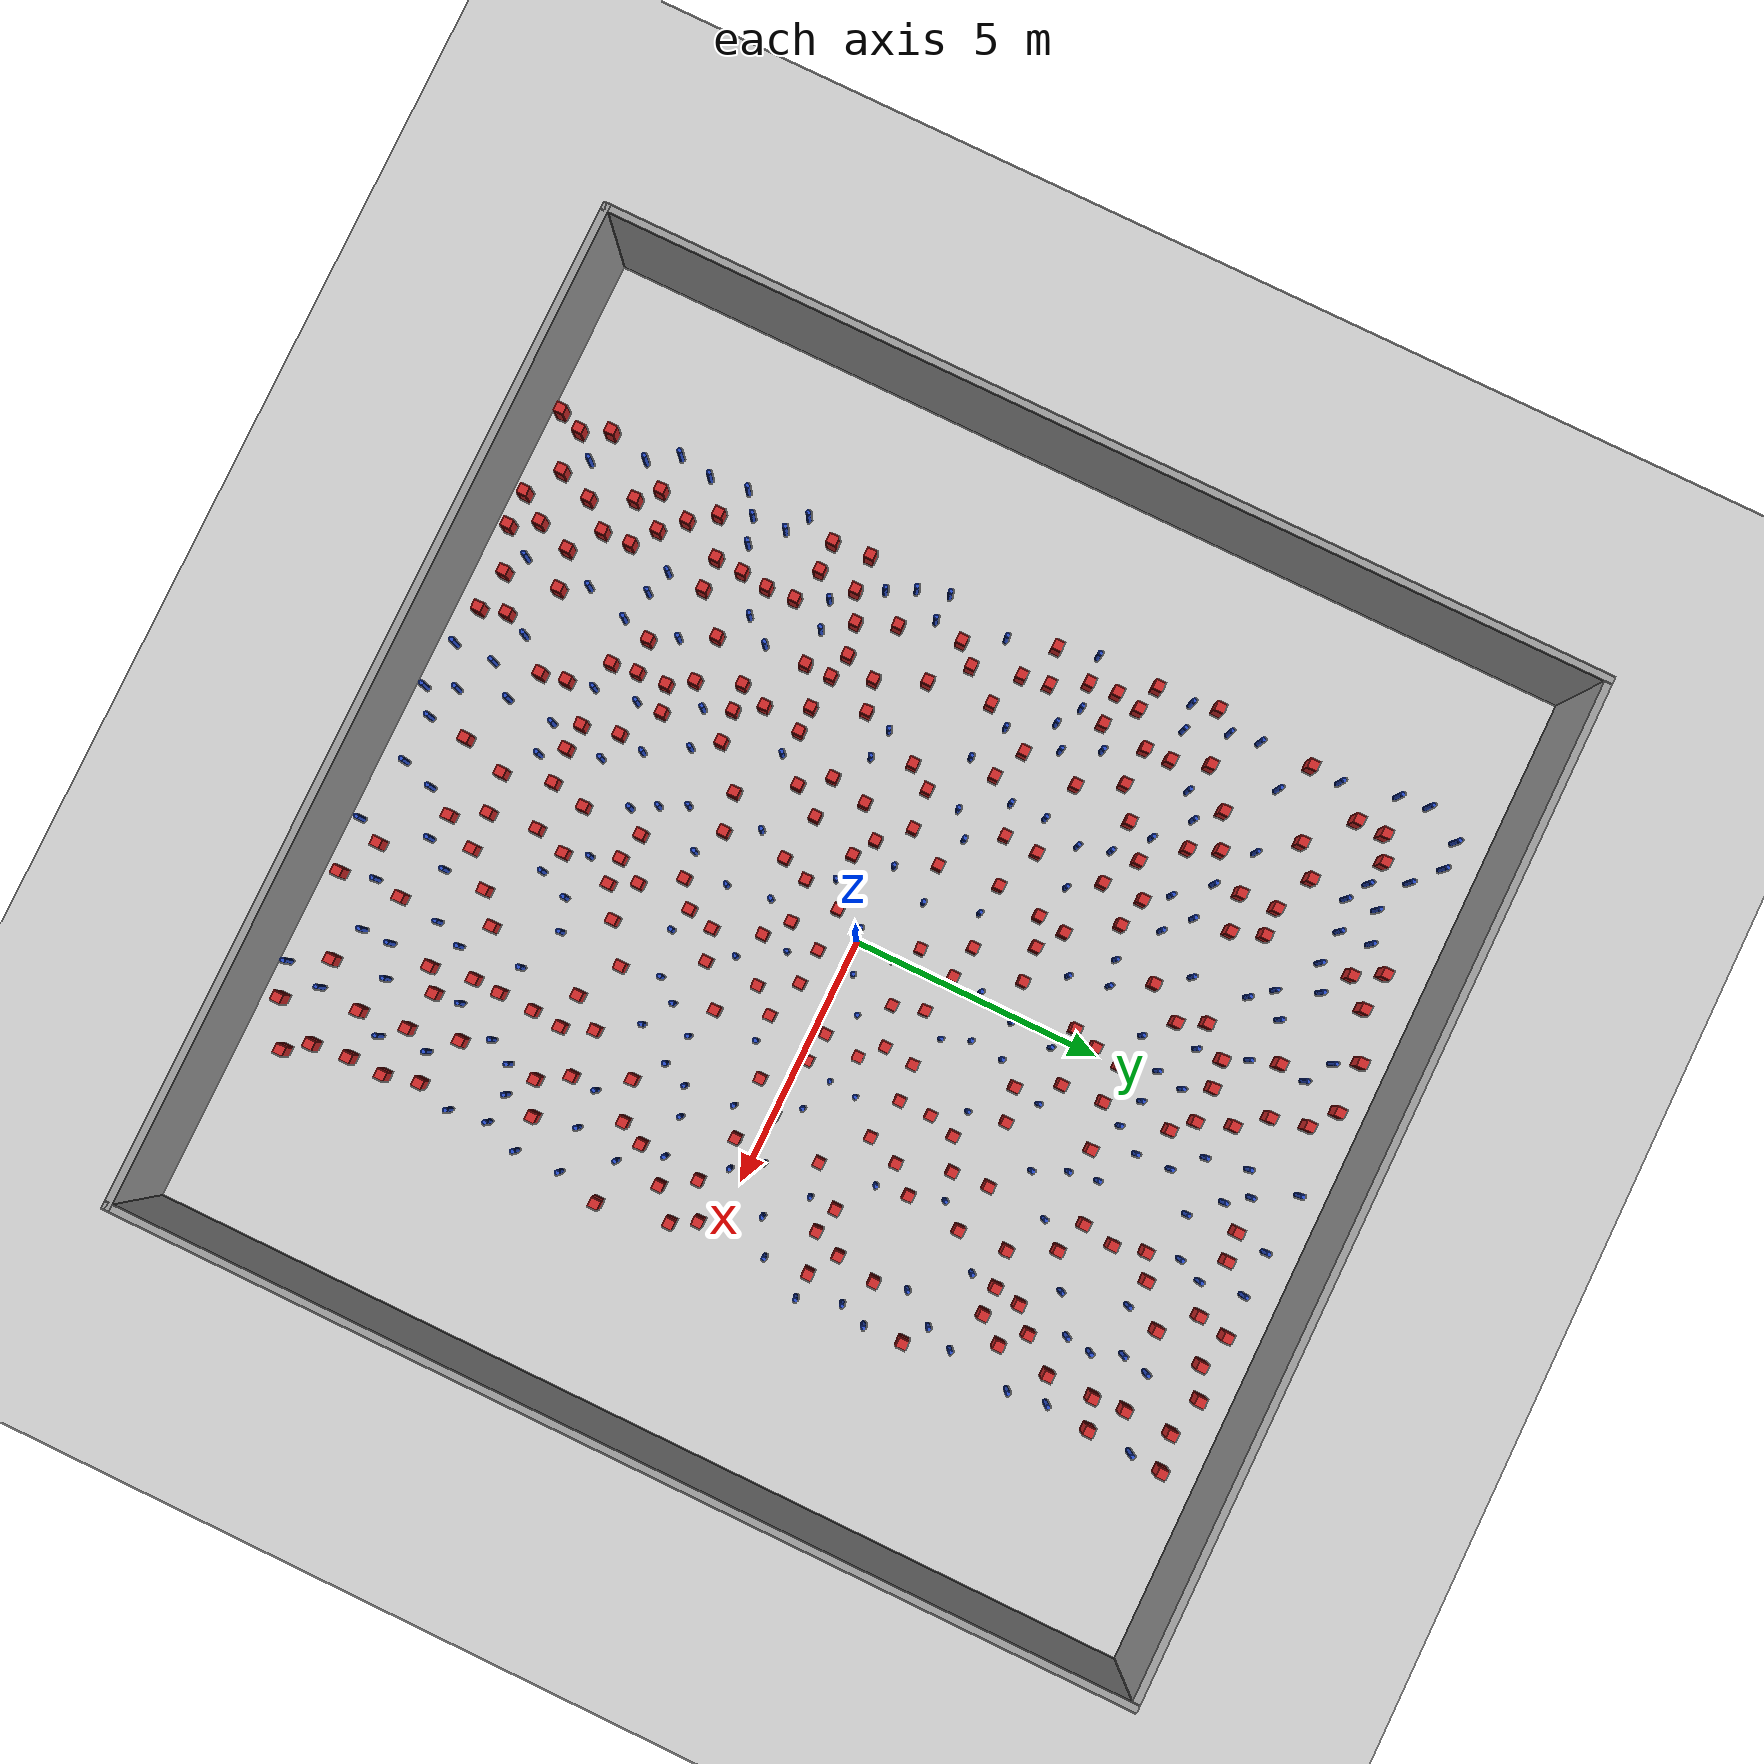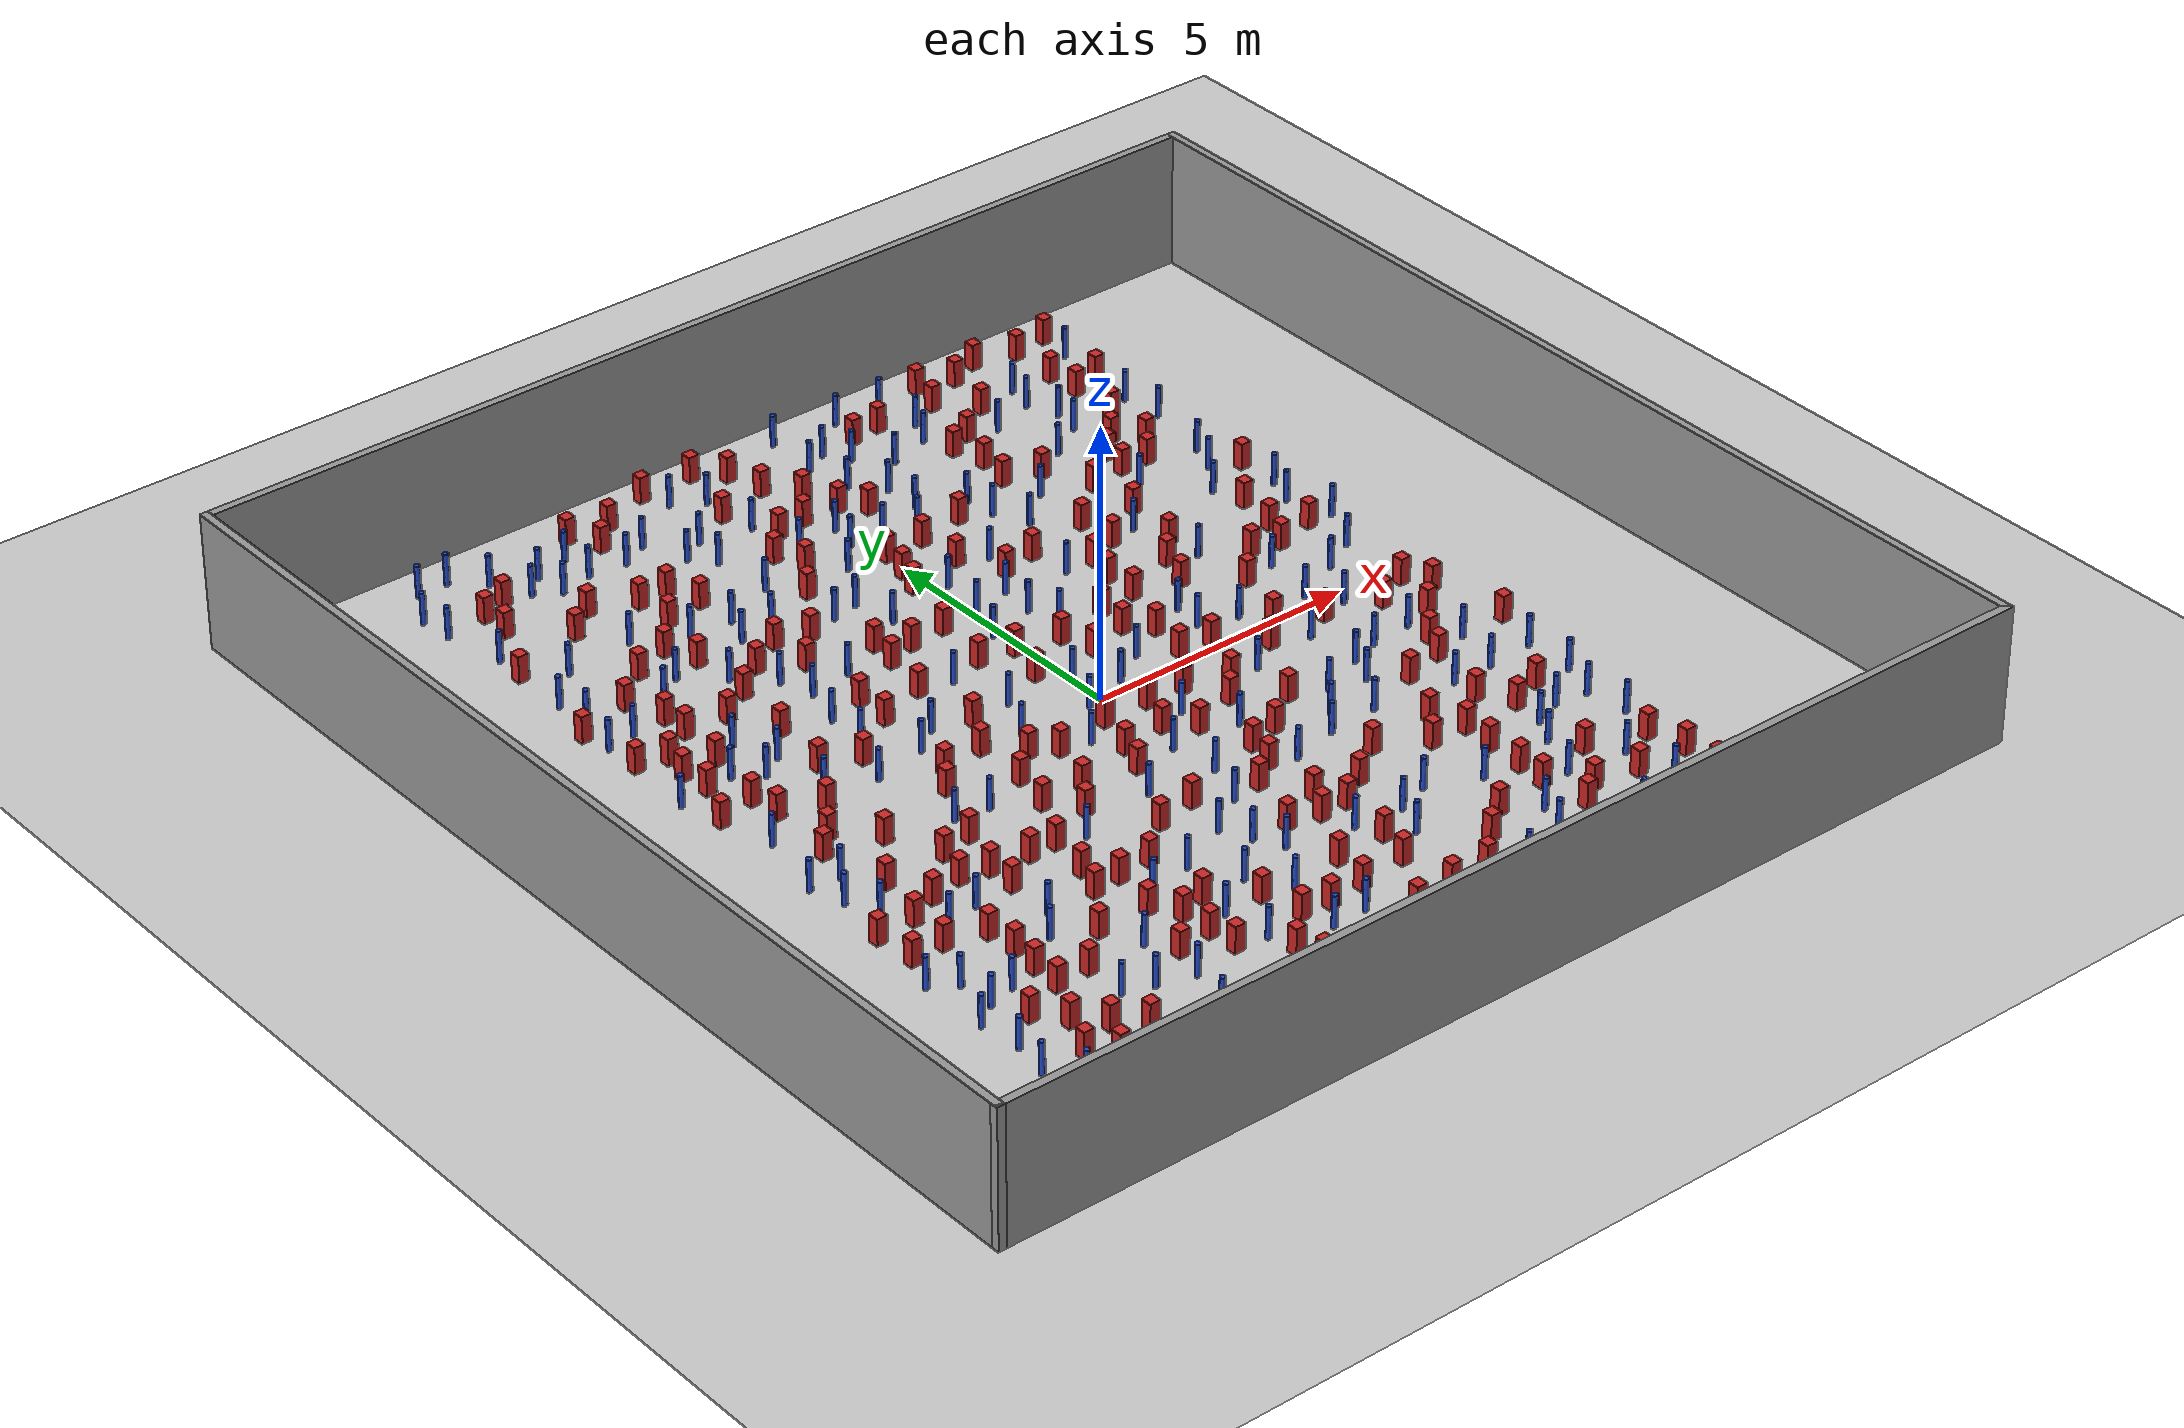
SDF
<sdf version="1.6">
 <world name="default">
  <light name="sun" type="directional">
   <pose>0 0 1000 0 -0 0</pose>
   <diffuse>0.8 0.8 0.8 1</diffuse>
   <specular>0.1 0.1 0.1 1</specular>
   <attenuation>
    <range>1000</range>
    <constant>0.9</constant>
    <linear>0.01</linear>
    <quadratic>0.001</quadratic>
   </attenuation>
   <direction>-0.5 0.5 -1</direction>
  </light>
  <model name="ground_plane">
   <static>1</static>
   <link name="link">
    <collision name="collision">
     <geometry><plane><normal>0 0 1</normal><size>100 100</size></plane></geometry>
     <surface><friction><ode><mu>100</mu><mu2>50</mu2></ode></friction></surface>
    </collision>
    <visual name="visual">
     <cast_shadows>0</cast_shadows>
     <geometry><plane><normal>0 0 1</normal><size>100 100</size></plane></geometry>
     <material>
      <ambient>1.0 1.0 1.0 1.0</ambient>
      <diffuse>0.8 0.8 0.8 1.0</diffuse>
      <specular>0.01 0.01 0.01 1.000000</specular>
     </material>
    </visual>
   </link>
  </model>
  <gravity>0 0 -9.8</gravity>
  <magnetic_field>6e-06 2.3e-05 -4.2e-05</magnetic_field>
  <atmosphere type="adiabatic"/>
  <physics name="default_physics" default="0" type="ode">
   <max_step_size>0.001</max_step_size>
   <real_time_factor>1</real_time_factor>
   <real_time_update_rate>1000</real_time_update_rate>
  </physics>
  <scene><ambient>0.4 0.4 0.4 1</ambient><background>0.7 0.7 0.7 1</background><shadows>1</shadows></scene>
  <spherical_coordinates>
   <surface_model>EARTH_WGS84</surface_model>
   <latitude_deg>0</latitude_deg>
   <longitude_deg>0</longitude_deg>
   <elevation>0</elevation>
   <heading_deg>0</heading_deg>
  </spherical_coordinates>
  <plugin name="gazebo_occupancy_map" filename="libgazebo_2Dmap_plugin.so">
   <map_resolution>0.05</map_resolution>
   <map_topic>generated_map</map_topic>
   <map_height>0.01</map_height>
   <map_size_x>50</map_size_x>
   <map_size_y>50</map_size_y>
  </plugin>
  <model name="NamedLocations">
   <static>true</static>
   <link name="DefaultStart"><pose>8.5 0 0 0 0 3.14</pose></link>
  </model>
  <model name="20x20_walls">
   <pose>0.044518 0.176112 0 0 -0 0</pose>
   <link name="Wall_1">
    <collision name="Wall_1_Collision">
     <geometry><box><size>20 0.15 2.5</size></box></geometry>
     <pose>0 0 1.25 0 -0 0</pose>
    </collision>
    <visual name="Wall_1_Visual">
     <pose>0 0 1.25 0 -0 0</pose>
     <geometry><box><size>20 0.15 2.5</size></box></geometry>
     <material>
      <script><uri>file://media/materials/scripts/gazebo.material</uri><name>Gazebo/Grey</name></script>
      <ambient>0.976471 0.992157 1 1</ambient>
     </material>
     <meta><layer>0</layer></meta>
    </visual>
    <pose>0 9.925 0 0 -0 0</pose>
   </link>
   <link name="Wall_3">
    <collision name="Wall_3_Collision">
     <geometry><box><size>20 0.15 2.5</size></box></geometry>
     <pose>0 0 1.25 0 -0 0</pose>
    </collision>
    <visual name="Wall_3_Visual">
     <pose>0 0 1.25 0 -0 0</pose>
     <geometry><box><size>20 0.15 2.5</size></box></geometry>
     <material>
      <script><uri>file://media/materials/scripts/gazebo.material</uri><name>Gazebo/Grey</name></script>
      <ambient>0.976471 0.992157 1 1</ambient>
     </material>
     <meta><layer>0</layer></meta>
    </visual>
    <pose>9.925 0 0 0 0 -1.5708</pose>
   </link>
   <link name="Wall_4">
    <collision name="Wall_4_Collision">
     <geometry><box><size>20 0.15 2.5</size></box></geometry>
     <pose>0 0 1.25 0 -0 0</pose>
    </collision>
    <visual name="Wall_4_Visual">
     <pose>0 0 1.25 0 -0 0</pose>
     <geometry><box><size>20 0.15 2.5</size></box></geometry>
     <material>
      <script><uri>file://media/materials/scripts/gazebo.material</uri><name>Gazebo/Grey</name></script>
      <ambient>0.976471 0.992157 1 1</ambient>
     </material>
     <meta><layer>0</layer></meta>
    </visual>
    <pose>0 -9.925 0 0 -0 3.14159</pose>
   </link>
   <link name="Wall_5">
    <collision name="Wall_5_Collision">
     <geometry><box><size>20 0.15 2.5</size></box></geometry>
     <pose>0 0 1.25 0 -0 0</pose>
    </collision>
    <visual name="Wall_5_Visual">
     <pose>0 0 1.25 0 -0 0</pose>
     <geometry><box><size>20 0.15 2.5</size></box></geometry>
     <material>
      <script><uri>file://media/materials/scripts/gazebo.material</uri><name>Gazebo/Grey</name></script>
      <ambient>0.976471 0.992157 1 1</ambient>
     </material>
     <meta><layer>0</layer></meta>
    </visual>
    <pose>-9.925 0 0 0 -0 1.5708</pose>
   </link>
   <static>1</static>
  </model>
  <model name="square_post_obstacle0">
   <static>true</static>
   <pose>-2.3731624759 0.0419707652193 8.22691968438e-08 7.2212513382e-06 -7.54495500217e-07 2.29674213826e-05</pose>
   <link name="link">
    <pose>0 0 0.25 0 -0 0</pose>
    <inertial>
     <mass>100</mass>
     <inertia>
      <ixx>0.166667</ixx>
      <ixy>0</ixy>
      <ixz>0</ixz>
      <iyy>0.166667</iyy>
      <iyz>0</iyz>
      <izz>0.166667</izz>
     </inertia>
    </inertial>
    <collision name="collision"><geometry><box><size>.2 .2 .5</size></box></geometry></collision>
    <visual name="visual">
     <geometry><box><size>.2 .2 .5</size></box></geometry>
     <material>
      <script><name>Gazebo/Red</name><uri>file://media/materials/scripts/gazebo.material</uri></script>
     </material>
    </visual>
   </link>
  </model>
  <model name="square_post_obstacle1">
   <static>true</static>
   <pose>-3.92318719585 6.10322206568 8.22691968438e-08 7.22125133819e-06 -7.54495500217e-07 2.29674213826e-05</pose>
   <link name="link">
    <pose>0 0 0.25 0 -0 0</pose>
    <inertial>
     <mass>100</mass>
     <inertia>
      <ixx>0.166667</ixx>
      <ixy>0</ixy>
      <ixz>0</ixz>
      <iyy>0.166667</iyy>
      <iyz>0</iyz>
      <izz>0.166667</izz>
     </inertia>
    </inertial>
    <collision name="collision"><geometry><box><size>.2 .2 .5</size></box></geometry></collision>
    <visual name="visual">
     <geometry><box><size>.2 .2 .5</size></box></geometry>
     <material>
      <script><name>Gazebo/Red</name><uri>file://media/materials/scripts/gazebo.material</uri></script>
     </material>
    </visual>
   </link>
  </model>
  <model name="pole_obstacle0">
   <static>true</static>
   <pose>-2.60340925272 0.994244192545 2.88873142074e-08 -9.90536689701e-09 4.60219948992e-07 -1.20965994959e-07</pose>
   <link name="link">
    <pose>0 0 0.3 0 -0 0</pose>
    <inertial>
     <mass>1</mass>
     <inertia><ixx>0.145833</ixx><ixy>0</ixy><ixz>0</ixz><iyy>0.145833</iyy><iyz>0</iyz><izz>0.125</izz></inertia>
    </inertial>
    <collision name="collision">
     <geometry><cylinder><radius>0.05</radius><length>.6</length></cylinder></geometry>
    </collision>
    <visual name="visual">
     <geometry><cylinder><radius>0.05</radius><length>.6</length></cylinder></geometry>
     <material>
      <script><name>Gazebo/Blue</name><uri>file://media/materials/scripts/gazebo.material</uri></script>
     </material>
    </visual>
   </link>
  </model>
  <model name="square_post_obstacle2">
   <static>true</static>
   <pose>3.41418709103 2.44954421194 8.22691968438e-08 7.2212513382e-06 -7.54495500217e-07 2.29674213826e-05</pose>
   <link name="link">
    <pose>0 0 0.25 0 -0 0</pose>
    <inertial>
     <mass>100</mass>
     <inertia>
      <ixx>0.166667</ixx>
      <ixy>0</ixy>
      <ixz>0</ixz>
      <iyy>0.166667</iyy>
      <iyz>0</iyz>
      <izz>0.166667</izz>
     </inertia>
    </inertial>
    <collision name="collision"><geometry><box><size>.2 .2 .5</size></box></geometry></collision>
    <visual name="visual">
     <geometry><box><size>.2 .2 .5</size></box></geometry>
     <material>
      <script><name>Gazebo/Red</name><uri>file://media/materials/scripts/gazebo.material</uri></script>
     </material>
    </visual>
   </link>
  </model>
  <model name="pole_obstacle1">
   <static>true</static>
   <pose>-6.46145248811 -4.59415883303 2.88873142074e-08 -9.90536690842e-09 4.60219948965e-07 -1.20965994976e-07</pose>
   <link name="link">
    <pose>0 0 0.3 0 -0 0</pose>
    <inertial>
     <mass>1</mass>
     <inertia><ixx>0.145833</ixx><ixy>0</ixy><ixz>0</ixz><iyy>0.145833</iyy><iyz>0</iyz><izz>0.125</izz></inertia>
    </inertial>
    <collision name="collision">
     <geometry><cylinder><radius>0.05</radius><length>.6</length></cylinder></geometry>
    </collision>
    <visual name="visual">
     <geometry><cylinder><radius>0.05</radius><length>.6</length></cylinder></geometry>
     <material>
      <script><name>Gazebo/Blue</name><uri>file://media/materials/scripts/gazebo.material</uri></script>
     </material>
    </visual>
   </link>
  </model>
  <model name="square_post_obstacle3">
   <static>true</static>
   <pose>4.13522312738 -2.65579902675 8.22691968438e-08 7.2212513382e-06 -7.54495500217e-07 2.29674213826e-05</pose>
   <link name="link">
    <pose>0 0 0.25 0 -0 0</pose>
    <inertial>
     <mass>100</mass>
     <inertia>
      <ixx>0.166667</ixx>
      <ixy>0</ixy>
      <ixz>0</ixz>
      <iyy>0.166667</iyy>
      <iyz>0</iyz>
      <izz>0.166667</izz>
     </inertia>
    </inertial>
    <collision name="collision"><geometry><box><size>.2 .2 .5</size></box></geometry></collision>
    <visual name="visual">
     <geometry><box><size>.2 .2 .5</size></box></geometry>
     <material>
      <script><name>Gazebo/Red</name><uri>file://media/materials/scripts/gazebo.material</uri></script>
     </material>
    </visual>
   </link>
  </model>
  <model name="pole_obstacle2">
   <static>true</static>
   <pose>2.07751800171 5.97733146448 2.88873142074e-08 -9.90536689859e-09 4.60219948989e-07 -1.20965994961e-07</pose>
   <link name="link">
    <pose>0 0 0.3 0 -0 0</pose>
    <inertial>
     <mass>1</mass>
     <inertia><ixx>0.145833</ixx><ixy>0</ixy><ixz>0</ixz><iyy>0.145833</iyy><iyz>0</iyz><izz>0.125</izz></inertia>
    </inertial>
    <collision name="collision">
     <geometry><cylinder><radius>0.05</radius><length>.6</length></cylinder></geometry>
    </collision>
    <visual name="visual">
     <geometry><cylinder><radius>0.05</radius><length>.6</length></cylinder></geometry>
     <material>
      <script><name>Gazebo/Blue</name><uri>file://media/materials/scripts/gazebo.material</uri></script>
     </material>
    </visual>
   </link>
  </model>
  <model name="pole_obstacle3">
   <static>true</static>
   <pose>-3.62500078362 2.20097115959 2.88873142074e-08 -9.90536690232e-09 4.6021994898e-07 -1.20965994968e-07</pose>
   <link name="link">
    <pose>0 0 0.3 0 -0 0</pose>
    <inertial>
     <mass>1</mass>
     <inertia><ixx>0.145833</ixx><ixy>0</ixy><ixz>0</ixz><iyy>0.145833</iyy><iyz>0</iyz><izz>0.125</izz></inertia>
    </inertial>
    <collision name="collision">
     <geometry><cylinder><radius>0.05</radius><length>.6</length></cylinder></geometry>
    </collision>
    <visual name="visual">
     <geometry><cylinder><radius>0.05</radius><length>.6</length></cylinder></geometry>
     <material>
      <script><name>Gazebo/Blue</name><uri>file://media/materials/scripts/gazebo.material</uri></script>
     </material>
    </visual>
   </link>
  </model>
  <model name="square_post_obstacle4">
   <static>true</static>
   <pose>-0.0230214975011 5.42789947488 8.22691968438e-08 7.22125133819e-06 -7.54495500217e-07 2.29674213826e-05</pose>
   <link name="link">
    <pose>0 0 0.25 0 -0 0</pose>
    <inertial>
     <mass>100</mass>
     <inertia>
      <ixx>0.166667</ixx>
      <ixy>0</ixy>
      <ixz>0</ixz>
      <iyy>0.166667</iyy>
      <iyz>0</iyz>
      <izz>0.166667</izz>
     </inertia>
    </inertial>
    <collision name="collision"><geometry><box><size>.2 .2 .5</size></box></geometry></collision>
    <visual name="visual">
     <geometry><box><size>.2 .2 .5</size></box></geometry>
     <material>
      <script><name>Gazebo/Red</name><uri>file://media/materials/scripts/gazebo.material</uri></script>
     </material>
    </visual>
   </link>
  </model>
  <model name="square_post_obstacle5">
   <static>true</static>
   <pose>0.884554935236 -5.68348603818 8.22691968438e-08 7.2212513382e-06 -7.54495500217e-07 2.29674213826e-05</pose>
   <link name="link">
    <pose>0 0 0.25 0 -0 0</pose>
    <inertial>
     <mass>100</mass>
     <inertia>
      <ixx>0.166667</ixx>
      <ixy>0</ixy>
      <ixz>0</ixz>
      <iyy>0.166667</iyy>
      <iyz>0</iyz>
      <izz>0.166667</izz>
     </inertia>
    </inertial>
    <collision name="collision"><geometry><box><size>.2 .2 .5</size></box></geometry></collision>
    <visual name="visual">
     <geometry><box><size>.2 .2 .5</size></box></geometry>
     <material>
      <script><name>Gazebo/Red</name><uri>file://media/materials/scripts/gazebo.material</uri></script>
     </material>
    </visual>
   </link>
  </model>
  <model name="square_post_obstacle6">
   <static>true</static>
   <pose>-3.60637497472 -2.69285466474 8.22691968438e-08 7.2212513382e-06 -7.54495500217e-07 2.29674213826e-05</pose>
   <link name="link">
    <pose>0 0 0.25 0 -0 0</pose>
    <inertial>
     <mass>100</mass>
     <inertia>
      <ixx>0.166667</ixx>
      <ixy>0</ixy>
      <ixz>0</ixz>
      <iyy>0.166667</iyy>
      <iyz>0</iyz>
      <izz>0.166667</izz>
     </inertia>
    </inertial>
    <collision name="collision"><geometry><box><size>.2 .2 .5</size></box></geometry></collision>
    <visual name="visual">
     <geometry><box><size>.2 .2 .5</size></box></geometry>
     <material>
      <script><name>Gazebo/Red</name><uri>file://media/materials/scripts/gazebo.material</uri></script>
     </material>
    </visual>
   </link>
  </model>
  <model name="pole_obstacle4">
   <static>true</static>
   <pose>-3.32747737507 4.94547146037 2.88873142074e-08 -9.90536692062e-09 4.60219948937e-07 -1.20965994985e-07</pose>
   <link name="link">
    <pose>0 0 0.3 0 -0 0</pose>
    <inertial>
     <mass>1</mass>
     <inertia><ixx>0.145833</ixx><ixy>0</ixy><ixz>0</ixz><iyy>0.145833</iyy><iyz>0</iyz><izz>0.125</izz></inertia>
    </inertial>
    <collision name="collision">
     <geometry><cylinder><radius>0.05</radius><length>.6</length></cylinder></geometry>
    </collision>
    <visual name="visual">
     <geometry><cylinder><radius>0.05</radius><length>.6</length></cylinder></geometry>
     <material>
      <script><name>Gazebo/Blue</name><uri>file://media/materials/scripts/gazebo.material</uri></script>
     </material>
    </visual>
   </link>
  </model>
  <model name="pole_obstacle5">
   <static>true</static>
   <pose>1.32508364615 6.40722247907 2.88873142074e-08 -9.90536689852e-09 4.60219948989e-07 -1.2096599496e-07</pose>
   <link name="link">
    <pose>0 0 0.3 0 -0 0</pose>
    <inertial>
     <mass>1</mass>
     <inertia><ixx>0.145833</ixx><ixy>0</ixy><ixz>0</ixz><iyy>0.145833</iyy><iyz>0</iyz><izz>0.125</izz></inertia>
    </inertial>
    <collision name="collision">
     <geometry><cylinder><radius>0.05</radius><length>.6</length></cylinder></geometry>
    </collision>
    <visual name="visual">
     <geometry><cylinder><radius>0.05</radius><length>.6</length></cylinder></geometry>
     <material>
      <script><name>Gazebo/Blue</name><uri>file://media/materials/scripts/gazebo.material</uri></script>
     </material>
    </visual>
   </link>
  </model>
  <model name="square_post_obstacle7">
   <static>true</static>
   <pose>1.55606180272 -7.26533026162 8.22691968438e-08 7.2212513382e-06 -7.54495500217e-07 2.29674213826e-05</pose>
   <link name="link">
    <pose>0 0 0.25 0 -0 0</pose>
    <inertial>
     <mass>100</mass>
     <inertia>
      <ixx>0.166667</ixx>
      <ixy>0</ixy>
      <ixz>0</ixz>
      <iyy>0.166667</iyy>
      <iyz>0</iyz>
      <izz>0.166667</izz>
     </inertia>
    </inertial>
    <collision name="collision"><geometry><box><size>.2 .2 .5</size></box></geometry></collision>
    <visual name="visual">
     <geometry><box><size>.2 .2 .5</size></box></geometry>
     <material>
      <script><name>Gazebo/Red</name><uri>file://media/materials/scripts/gazebo.material</uri></script>
     </material>
    </visual>
   </link>
  </model>
  <model name="square_post_obstacle8">
   <static>true</static>
   <pose>4.02171252029 1.15391218855 8.22691968438e-08 7.2212513382e-06 -7.54495500217e-07 2.29674213826e-05</pose>
   <link name="link">
    <pose>0 0 0.25 0 -0 0</pose>
    <inertial>
     <mass>100</mass>
     <inertia>
      <ixx>0.166667</ixx>
      <ixy>0</ixy>
      <ixz>0</ixz>
      <iyy>0.166667</iyy>
      <iyz>0</iyz>
      <izz>0.166667</izz>
     </inertia>
    </inertial>
    <collision name="collision"><geometry><box><size>.2 .2 .5</size></box></geometry></collision>
    <visual name="visual">
     <geometry><box><size>.2 .2 .5</size></box></geometry>
     <material>
      <script><name>Gazebo/Red</name><uri>file://media/materials/scripts/gazebo.material</uri></script>
     </material>
    </visual>
   </link>
  </model>
  <model name="pole_obstacle6">
   <static>true</static>
   <pose>1.93231918267 7.72622487613 2.88873142074e-08 -9.90536689852e-09 4.60219948989e-07 -1.2096599496e-07</pose>
   <link name="link">
    <pose>0 0 0.3 0 -0 0</pose>
    <inertial>
     <mass>1</mass>
     <inertia><ixx>0.145833</ixx><ixy>0</ixy><ixz>0</ixz><iyy>0.145833</iyy><iyz>0</iyz><izz>0.125</izz></inertia>
    </inertial>
    <collision name="collision">
     <geometry><cylinder><radius>0.05</radius><length>.6</length></cylinder></geometry>
    </collision>
    <visual name="visual">
     <geometry><cylinder><radius>0.05</radius><length>.6</length></cylinder></geometry>
     <material>
      <script><name>Gazebo/Blue</name><uri>file://media/materials/scripts/gazebo.material</uri></script>
     </material>
    </visual>
   </link>
  </model>
  <model name="pole_obstacle7">
   <static>true</static>
   <pose>4.25041789018 -6.17766045648 2.88873142074e-08 -9.90536690842e-09 4.60219948965e-07 -1.20965994976e-07</pose>
   <link name="link">
    <pose>0 0 0.3 0 -0 0</pose>
    <inertial>
     <mass>1</mass>
     <inertia><ixx>0.145833</ixx><ixy>0</ixy><ixz>0</ixz><iyy>0.145833</iyy><iyz>0</iyz><izz>0.125</izz></inertia>
    </inertial>
    <collision name="collision">
     <geometry><cylinder><radius>0.05</radius><length>.6</length></cylinder></geometry>
    </collision>
    <visual name="visual">
     <geometry><cylinder><radius>0.05</radius><length>.6</length></cylinder></geometry>
     <material>
      <script><name>Gazebo/Blue</name><uri>file://media/materials/scripts/gazebo.material</uri></script>
     </material>
    </visual>
   </link>
  </model>
  <model name="square_post_obstacle9">
   <static>true</static>
   <pose>-2.95118306738 9.09099483135 8.22691968438e-08 7.22125133819e-06 -7.54495500217e-07 2.29674213826e-05</pose>
   <link name="link">
    <pose>0 0 0.25 0 -0 0</pose>
    <inertial>
     <mass>100</mass>
     <inertia>
      <ixx>0.166667</ixx>
      <ixy>0</ixy>
      <ixz>0</ixz>
      <iyy>0.166667</iyy>
      <iyz>0</iyz>
      <izz>0.166667</izz>
     </inertia>
    </inertial>
    <collision name="collision"><geometry><box><size>.2 .2 .5</size></box></geometry></collision>
    <visual name="visual">
     <geometry><box><size>.2 .2 .5</size></box></geometry>
     <material>
      <script><name>Gazebo/Red</name><uri>file://media/materials/scripts/gazebo.material</uri></script>
     </material>
    </visual>
   </link>
  </model>
  <model name="square_post_obstacle10">
   <static>true</static>
   <pose>-5.98233309754 -0.667109607882 8.22691968438e-08 7.2212513382e-06 -7.54495500217e-07 2.29674213826e-05</pose>
   <link name="link">
    <pose>0 0 0.25 0 -0 0</pose>
    <inertial>
     <mass>100</mass>
     <inertia>
      <ixx>0.166667</ixx>
      <ixy>0</ixy>
      <ixz>0</ixz>
      <iyy>0.166667</iyy>
      <iyz>0</iyz>
      <izz>0.166667</izz>
     </inertia>
    </inertial>
    <collision name="collision"><geometry><box><size>.2 .2 .5</size></box></geometry></collision>
    <visual name="visual">
     <geometry><box><size>.2 .2 .5</size></box></geometry>
     <material>
      <script><name>Gazebo/Red</name><uri>file://media/materials/scripts/gazebo.material</uri></script>
     </material>
    </visual>
   </link>
  </model>
  <model name="square_post_obstacle11">
   <static>true</static>
   <pose>3.17586104604 1.81544225425 8.22691968438e-08 7.2212513382e-06 -7.54495500217e-07 2.29674213826e-05</pose>
   <link name="link">
    <pose>0 0 0.25 0 -0 0</pose>
    <inertial>
     <mass>100</mass>
     <inertia>
      <ixx>0.166667</ixx>
      <ixy>0</ixy>
      <ixz>0</ixz>
      <iyy>0.166667</iyy>
      <iyz>0</iyz>
      <izz>0.166667</izz>
     </inertia>
    </inertial>
    <collision name="collision"><geometry><box><size>.2 .2 .5</size></box></geometry></collision>
    <visual name="visual">
     <geometry><box><size>.2 .2 .5</size></box></geometry>
     <material>
      <script><name>Gazebo/Red</name><uri>file://media/materials/scripts/gazebo.material</uri></script>
     </material>
    </visual>
   </link>
  </model>
  <model name="square_post_obstacle12">
   <static>true</static>
   <pose>2.14708013972 -6.70917561124 8.22691968438e-08 7.2212513382e-06 -7.54495500217e-07 2.29674213826e-05</pose>
   <link name="link">
    <pose>0 0 0.25 0 -0 0</pose>
    <inertial>
     <mass>100</mass>
     <inertia>
      <ixx>0.166667</ixx>
      <ixy>0</ixy>
      <ixz>0</ixz>
      <iyy>0.166667</iyy>
      <iyz>0</iyz>
      <izz>0.166667</izz>
     </inertia>
    </inertial>
    <collision name="collision"><geometry><box><size>.2 .2 .5</size></box></geometry></collision>
    <visual name="visual">
     <geometry><box><size>.2 .2 .5</size></box></geometry>
     <material>
      <script><name>Gazebo/Red</name><uri>file://media/materials/scripts/gazebo.material</uri></script>
     </material>
    </visual>
   </link>
  </model>
  <model name="square_post_obstacle13">
   <static>true</static>
   <pose>1.82181593819 8.7151289453 8.22691968438e-08 7.22125133819e-06 -7.54495500217e-07 2.29674213826e-05</pose>
   <link name="link">
    <pose>0 0 0.25 0 -0 0</pose>
    <inertial>
     <mass>100</mass>
     <inertia>
      <ixx>0.166667</ixx>
      <ixy>0</ixy>
      <ixz>0</ixz>
      <iyy>0.166667</iyy>
      <iyz>0</iyz>
      <izz>0.166667</izz>
     </inertia>
    </inertial>
    <collision name="collision"><geometry><box><size>.2 .2 .5</size></box></geometry></collision>
    <visual name="visual">
     <geometry><box><size>.2 .2 .5</size></box></geometry>
     <material>
      <script><name>Gazebo/Red</name><uri>file://media/materials/scripts/gazebo.material</uri></script>
     </material>
    </visual>
   </link>
  </model>
  <model name="pole_obstacle8">
   <static>true</static>
   <pose>-6.69223474554 -1.24528265409 2.88873142074e-08 -9.90536689445e-09 4.60219948999e-07 -1.20965994956e-07</pose>
   <link name="link">
    <pose>0 0 0.3 0 -0 0</pose>
    <inertial>
     <mass>1</mass>
     <inertia><ixx>0.145833</ixx><ixy>0</ixy><ixz>0</ixz><iyy>0.145833</iyy><iyz>0</iyz><izz>0.125</izz></inertia>
    </inertial>
    <collision name="collision">
     <geometry><cylinder><radius>0.05</radius><length>.6</length></cylinder></geometry>
    </collision>
    <visual name="visual">
     <geometry><cylinder><radius>0.05</radius><length>.6</length></cylinder></geometry>
     <material>
      <script><name>Gazebo/Blue</name><uri>file://media/materials/scripts/gazebo.material</uri></script>
     </material>
    </visual>
   </link>
  </model>
  <model name="square_post_obstacle14">
   <static>true</static>
   <pose>-6.7860666134 3.04604485807 8.22691968438e-08 7.2212513382e-06 -7.54495500217e-07 2.29674213826e-05</pose>
   <link name="link">
    <pose>0 0 0.25 0 -0 0</pose>
    <inertial>
     <mass>100</mass>
     <inertia>
      <ixx>0.166667</ixx>
      <ixy>0</ixy>
      <ixz>0</ixz>
      <iyy>0.166667</iyy>
      <iyz>0</iyz>
      <izz>0.166667</izz>
     </inertia>
    </inertial>
    <collision name="collision"><geometry><box><size>.2 .2 .5</size></box></geometry></collision>
    <visual name="visual">
     <geometry><box><size>.2 .2 .5</size></box></geometry>
     <material>
      <script><name>Gazebo/Red</name><uri>file://media/materials/scripts/gazebo.material</uri></script>
     </material>
    </visual>
   </link>
  </model>
  <model name="square_post_obstacle15">
   <static>true</static>
   <pose>3.59028391547 0.0141733033644 8.22691968438e-08 7.22125133819e-06 -7.54495500217e-07 2.29674213826e-05</pose>
   <link name="link">
    <pose>0 0 0.25 0 -0 0</pose>
    <inertial>
     <mass>100</mass>
     <inertia>
      <ixx>0.166667</ixx>
      <ixy>0</ixy>
      <ixz>0</ixz>
      <iyy>0.166667</iyy>
      <iyz>0</iyz>
      <izz>0.166667</izz>
     </inertia>
    </inertial>
    <collision name="collision"><geometry><box><size>.2 .2 .5</size></box></geometry></collision>
    <visual name="visual">
     <geometry><box><size>.2 .2 .5</size></box></geometry>
     <material>
      <script><name>Gazebo/Red</name><uri>file://media/materials/scripts/gazebo.material</uri></script>
     </material>
    </visual>
   </link>
  </model>
  <model name="square_post_obstacle16">
   <static>true</static>
   <pose>-1.69396350508 5.36391911132 8.22691968438e-08 7.2212513382e-06 -7.54495500217e-07 2.29674213826e-05</pose>
   <link name="link">
    <pose>0 0 0.25 0 -0 0</pose>
    <inertial>
     <mass>100</mass>
     <inertia>
      <ixx>0.166667</ixx>
      <ixy>0</ixy>
      <ixz>0</ixz>
      <iyy>0.166667</iyy>
      <iyz>0</iyz>
      <izz>0.166667</izz>
     </inertia>
    </inertial>
    <collision name="collision"><geometry><box><size>.2 .2 .5</size></box></geometry></collision>
    <visual name="visual">
     <geometry><box><size>.2 .2 .5</size></box></geometry>
     <material>
      <script><name>Gazebo/Red</name><uri>file://media/materials/scripts/gazebo.material</uri></script>
     </material>
    </visual>
   </link>
  </model>
  <model name="pole_obstacle9">
   <static>true</static>
   <pose>3.24602878182 0.450953983572 2.88873142074e-08 -9.90536689151e-09 4.60219949006e-07 -1.20965994951e-07</pose>
   <link name="link">
    <pose>0 0 0.3 0 -0 0</pose>
    <inertial>
     <mass>1</mass>
     <inertia><ixx>0.145833</ixx><ixy>0</ixy><ixz>0</ixz><iyy>0.145833</iyy><iyz>0</iyz><izz>0.125</izz></inertia>
    </inertial>
    <collision name="collision">
     <geometry><cylinder><radius>0.05</radius><length>.6</length></cylinder></geometry>
    </collision>
    <visual name="visual">
     <geometry><cylinder><radius>0.05</radius><length>.6</length></cylinder></geometry>
     <material>
      <script><name>Gazebo/Blue</name><uri>file://media/materials/scripts/gazebo.material</uri></script>
     </material>
    </visual>
   </link>
  </model>
  <model name="square_post_obstacle17">
   <static>true</static>
   <pose>0.65483960181 6.78613451432 8.22691968438e-08 7.2212513382e-06 -7.54495500217e-07 2.29674213826e-05</pose>
   <link name="link">
    <pose>0 0 0.25 0 -0 0</pose>
    <inertial>
     <mass>100</mass>
     <inertia>
      <ixx>0.166667</ixx>
      <ixy>0</ixy>
      <ixz>0</ixz>
      <iyy>0.166667</iyy>
      <iyz>0</iyz>
      <izz>0.166667</izz>
     </inertia>
    </inertial>
    <collision name="collision"><geometry><box><size>.2 .2 .5</size></box></geometry></collision>
    <visual name="visual">
     <geometry><box><size>.2 .2 .5</size></box></geometry>
     <material>
      <script><name>Gazebo/Red</name><uri>file://media/materials/scripts/gazebo.material</uri></script>
     </material>
    </visual>
   </link>
  </model>
  <model name="square_post_obstacle18">
   <static>true</static>
   <pose>0.332091267459 -3.42011661913 8.22691968438e-08 7.22125133819e-06 -7.54495500217e-07 2.29674213826e-05</pose>
   <link name="link">
    <pose>0 0 0.25 0 -0 0</pose>
    <inertial>
     <mass>100</mass>
     <inertia>
      <ixx>0.166667</ixx>
      <ixy>0</ixy>
      <ixz>0</ixz>
      <iyy>0.166667</iyy>
      <iyz>0</iyz>
      <izz>0.166667</izz>
     </inertia>
    </inertial>
    <collision name="collision"><geometry><box><size>.2 .2 .5</size></box></geometry></collision>
    <visual name="visual">
     <geometry><box><size>.2 .2 .5</size></box></geometry>
     <material>
      <script><name>Gazebo/Red</name><uri>file://media/materials/scripts/gazebo.material</uri></script>
     </material>
    </visual>
   </link>
  </model>
  <model name="pole_obstacle10">
   <static>true</static>
   <pose>-5.34272363832 1.61929441346 2.88873142074e-08 -9.90536689445e-09 4.60219948999e-07 -1.20965994956e-07</pose>
   <link name="link">
    <pose>0 0 0.3 0 -0 0</pose>
    <inertial>
     <mass>1</mass>
     <inertia><ixx>0.145833</ixx><ixy>0</ixy><ixz>0</ixz><iyy>0.145833</iyy><iyz>0</iyz><izz>0.125</izz></inertia>
    </inertial>
    <collision name="collision">
     <geometry><cylinder><radius>0.05</radius><length>.6</length></cylinder></geometry>
    </collision>
    <visual name="visual">
     <geometry><cylinder><radius>0.05</radius><length>.6</length></cylinder></geometry>
     <material>
      <script><name>Gazebo/Blue</name><uri>file://media/materials/scripts/gazebo.material</uri></script>
     </material>
    </visual>
   </link>
  </model>
  <model name="square_post_obstacle19">
   <static>true</static>
   <pose>3.85054422246 2.91519529944 8.22691968438e-08 7.2212513382e-06 -7.54495500217e-07 2.29674213826e-05</pose>
   <link name="link">
    <pose>0 0 0.25 0 -0 0</pose>
    <inertial>
     <mass>100</mass>
     <inertia>
      <ixx>0.166667</ixx>
      <ixy>0</ixy>
      <ixz>0</ixz>
      <iyy>0.166667</iyy>
      <iyz>0</iyz>
      <izz>0.166667</izz>
     </inertia>
    </inertial>
    <collision name="collision"><geometry><box><size>.2 .2 .5</size></box></geometry></collision>
    <visual name="visual">
     <geometry><box><size>.2 .2 .5</size></box></geometry>
     <material>
      <script><name>Gazebo/Red</name><uri>file://media/materials/scripts/gazebo.material</uri></script>
     </material>
    </visual>
   </link>
  </model>
  <model name="pole_obstacle11">
   <static>true</static>
   <pose>5.1539246293 -1.47649896476 2.88873142074e-08 -9.90536689445e-09 4.60219948999e-07 -1.20965994956e-07</pose>
   <link name="link">
    <pose>0 0 0.3 0 -0 0</pose>
    <inertial>
     <mass>1</mass>
     <inertia><ixx>0.145833</ixx><ixy>0</ixy><ixz>0</ixz><iyy>0.145833</iyy><iyz>0</iyz><izz>0.125</izz></inertia>
    </inertial>
    <collision name="collision">
     <geometry><cylinder><radius>0.05</radius><length>.6</length></cylinder></geometry>
    </collision>
    <visual name="visual">
     <geometry><cylinder><radius>0.05</radius><length>.6</length></cylinder></geometry>
     <material>
      <script><name>Gazebo/Blue</name><uri>file://media/materials/scripts/gazebo.material</uri></script>
     </material>
    </visual>
   </link>
  </model>
  <model name="square_post_obstacle20">
   <static>true</static>
   <pose>0.76591102103 4.6098551937 8.22691968438e-08 7.2212513382e-06 -7.54495500217e-07 2.29674213826e-05</pose>
   <link name="link">
    <pose>0 0 0.25 0 -0 0</pose>
    <inertial>
     <mass>100</mass>
     <inertia>
      <ixx>0.166667</ixx>
      <ixy>0</ixy>
      <ixz>0</ixz>
      <iyy>0.166667</iyy>
      <iyz>0</iyz>
      <izz>0.166667</izz>
     </inertia>
    </inertial>
    <collision name="collision"><geometry><box><size>.2 .2 .5</size></box></geometry></collision>
    <visual name="visual">
     <geometry><box><size>.2 .2 .5</size></box></geometry>
     <material>
      <script><name>Gazebo/Red</name><uri>file://media/materials/scripts/gazebo.material</uri></script>
     </material>
    </visual>
   </link>
  </model>
  <model name="pole_obstacle12">
   <static>true</static>
   <pose>5.87228479408 4.29156723029 2.88873142074e-08 -9.90536690842e-09 4.60219948965e-07 -1.20965994976e-07</pose>
   <link name="link">
    <pose>0 0 0.3 0 -0 0</pose>
    <inertial>
     <mass>1</mass>
     <inertia><ixx>0.145833</ixx><ixy>0</ixy><ixz>0</ixz><iyy>0.145833</iyy><iyz>0</iyz><izz>0.125</izz></inertia>
    </inertial>
    <collision name="collision">
     <geometry><cylinder><radius>0.05</radius><length>.6</length></cylinder></geometry>
    </collision>
    <visual name="visual">
     <geometry><cylinder><radius>0.05</radius><length>.6</length></cylinder></geometry>
     <material>
      <script><name>Gazebo/Blue</name><uri>file://media/materials/scripts/gazebo.material</uri></script>
     </material>
    </visual>
   </link>
  </model>
  <model name="square_post_obstacle21">
   <static>true</static>
   <pose>-0.835728895165 2.02179317641 8.22691968438e-08 7.2212513382e-06 -7.54495500217e-07 2.29674213826e-05</pose>
   <link name="link">
    <pose>0 0 0.25 0 -0 0</pose>
    <inertial>
     <mass>100</mass>
     <inertia>
      <ixx>0.166667</ixx>
      <ixy>0</ixy>
      <ixz>0</ixz>
      <iyy>0.166667</iyy>
      <iyz>0</iyz>
      <izz>0.166667</izz>
     </inertia>
    </inertial>
    <collision name="collision"><geometry><box><size>.2 .2 .5</size></box></geometry></collision>
    <visual name="visual">
     <geometry><box><size>.2 .2 .5</size></box></geometry>
     <material>
      <script><name>Gazebo/Red</name><uri>file://media/materials/scripts/gazebo.material</uri></script>
     </material>
    </visual>
   </link>
  </model>
  <model name="pole_obstacle13">
   <static>true</static>
   <pose>6.3707468323 3.20079395214 2.88873142074e-08 -9.90536690245e-09 4.6021994898e-07 -1.20965994966e-07</pose>
   <link name="link">
    <pose>0 0 0.3 0 -0 0</pose>
    <inertial>
     <mass>1</mass>
     <inertia><ixx>0.145833</ixx><ixy>0</ixy><ixz>0</ixz><iyy>0.145833</iyy><iyz>0</iyz><izz>0.125</izz></inertia>
    </inertial>
    <collision name="collision">
     <geometry><cylinder><radius>0.05</radius><length>.6</length></cylinder></geometry>
    </collision>
    <visual name="visual">
     <geometry><cylinder><radius>0.05</radius><length>.6</length></cylinder></geometry>
     <material>
      <script><name>Gazebo/Blue</name><uri>file://media/materials/scripts/gazebo.material</uri></script>
     </material>
    </visual>
   </link>
  </model>
  <model name="square_post_obstacle22">
   <static>true</static>
   <pose>-5.62600483172 -0.300672023755 8.22691968438e-08 7.2212513382e-06 -7.54495500217e-07 2.29674213826e-05</pose>
   <link name="link">
    <pose>0 0 0.25 0 -0 0</pose>
    <inertial>
     <mass>100</mass>
     <inertia>
      <ixx>0.166667</ixx>
      <ixy>0</ixy>
      <ixz>0</ixz>
      <iyy>0.166667</iyy>
      <iyz>0</iyz>
      <izz>0.166667</izz>
     </inertia>
    </inertial>
    <collision name="collision"><geometry><box><size>.2 .2 .5</size></box></geometry></collision>
    <visual name="visual">
     <geometry><box><size>.2 .2 .5</size></box></geometry>
     <material>
      <script><name>Gazebo/Red</name><uri>file://media/materials/scripts/gazebo.material</uri></script>
     </material>
    </visual>
   </link>
  </model>
  <model name="pole_obstacle14">
   <static>true</static>
   <pose>-6.680665818 5.23387129462 2.88873142074e-08 -9.90536690842e-09 4.60219948965e-07 -1.20965994976e-07</pose>
   <link name="link">
    <pose>0 0 0.3 0 -0 0</pose>
    <inertial>
     <mass>1</mass>
     <inertia><ixx>0.145833</ixx><ixy>0</ixy><ixz>0</ixz><iyy>0.145833</iyy><iyz>0</iyz><izz>0.125</izz></inertia>
    </inertial>
    <collision name="collision">
     <geometry><cylinder><radius>0.05</radius><length>.6</length></cylinder></geometry>
    </collision>
    <visual name="visual">
     <geometry><cylinder><radius>0.05</radius><length>.6</length></cylinder></geometry>
     <material>
      <script><name>Gazebo/Blue</name><uri>file://media/materials/scripts/gazebo.material</uri></script>
     </material>
    </visual>
   </link>
  </model>
  <model name="pole_obstacle15">
   <static>true</static>
   <pose>6.03215885526 0.99990793642 2.88873142074e-08 -9.90536689329e-09 4.60219949001e-07 -1.20965994952e-07</pose>
   <link name="link">
    <pose>0 0 0.3 0 -0 0</pose>
    <inertial>
     <mass>1</mass>
     <inertia><ixx>0.145833</ixx><ixy>0</ixy><ixz>0</ixz><iyy>0.145833</iyy><iyz>0</iyz><izz>0.125</izz></inertia>
    </inertial>
    <collision name="collision">
     <geometry><cylinder><radius>0.05</radius><length>.6</length></cylinder></geometry>
    </collision>
    <visual name="visual">
     <geometry><cylinder><radius>0.05</radius><length>.6</length></cylinder></geometry>
     <material>
      <script><name>Gazebo/Blue</name><uri>file://media/materials/scripts/gazebo.material</uri></script>
     </material>
    </visual>
   </link>
  </model>
  <model name="pole_obstacle16">
   <static>true</static>
   <pose>-6.89624991938 -7.01245706391 2.88873142074e-08 -9.90536690842e-09 4.60219948965e-07 -1.20965994976e-07</pose>
   <link name="link">
    <pose>0 0 0.3 0 -0 0</pose>
    <inertial>
     <mass>1</mass>
     <inertia><ixx>0.145833</ixx><ixy>0</ixy><ixz>0</ixz><iyy>0.145833</iyy><iyz>0</iyz><izz>0.125</izz></inertia>
    </inertial>
    <collision name="collision">
     <geometry><cylinder><radius>0.05</radius><length>.6</length></cylinder></geometry>
    </collision>
    <visual name="visual">
     <geometry><cylinder><radius>0.05</radius><length>.6</length></cylinder></geometry>
     <material>
      <script><name>Gazebo/Blue</name><uri>file://media/materials/scripts/gazebo.material</uri></script>
     </material>
    </visual>
   </link>
  </model>
  <model name="square_post_obstacle23">
   <static>true</static>
   <pose>4.68276450183 5.10691720269 8.22691968438e-08 7.2212513382e-06 -7.54495500217e-07 2.29674213826e-05</pose>
   <link name="link">
    <pose>0 0 0.25 0 -0 0</pose>
    <inertial>
     <mass>100</mass>
     <inertia>
      <ixx>0.166667</ixx>
      <ixy>0</ixy>
      <ixz>0</ixz>
      <iyy>0.166667</iyy>
      <iyz>0</iyz>
      <izz>0.166667</izz>
     </inertia>
    </inertial>
    <collision name="collision"><geometry><box><size>.2 .2 .5</size></box></geometry></collision>
    <visual name="visual">
     <geometry><box><size>.2 .2 .5</size></box></geometry>
     <material>
      <script><name>Gazebo/Red</name><uri>file://media/materials/scripts/gazebo.material</uri></script>
     </material>
    </visual>
   </link>
  </model>
  <model name="pole_obstacle17">
   <static>true</static>
   <pose>0.841496908532 -8.48705982292 2.88873142074e-08 -9.90536690779e-09 4.60219948967e-07 -1.20965994975e-07</pose>
   <link name="link">
    <pose>0 0 0.3 0 -0 0</pose>
    <inertial>
     <mass>1</mass>
     <inertia><ixx>0.145833</ixx><ixy>0</ixy><ixz>0</ixz><iyy>0.145833</iyy><iyz>0</iyz><izz>0.125</izz></inertia>
    </inertial>
    <collision name="collision">
     <geometry><cylinder><radius>0.05</radius><length>.6</length></cylinder></geometry>
    </collision>
    <visual name="visual">
     <geometry><cylinder><radius>0.05</radius><length>.6</length></cylinder></geometry>
     <material>
      <script><name>Gazebo/Blue</name><uri>file://media/materials/scripts/gazebo.material</uri></script>
     </material>
    </visual>
   </link>
  </model>
  <model name="square_post_obstacle24">
   <static>true</static>
   <pose>-3.96279926447 6.8308532378 8.22691968438e-08 7.22125133819e-06 -7.54495500217e-07 2.29674213826e-05</pose>
   <link name="link">
    <pose>0 0 0.25 0 -0 0</pose>
    <inertial>
     <mass>100</mass>
     <inertia>
      <ixx>0.166667</ixx>
      <ixy>0</ixy>
      <ixz>0</ixz>
      <iyy>0.166667</iyy>
      <iyz>0</iyz>
      <izz>0.166667</izz>
     </inertia>
    </inertial>
    <collision name="collision"><geometry><box><size>.2 .2 .5</size></box></geometry></collision>
    <visual name="visual">
     <geometry><box><size>.2 .2 .5</size></box></geometry>
     <material>
      <script><name>Gazebo/Red</name><uri>file://media/materials/scripts/gazebo.material</uri></script>
     </material>
    </visual>
   </link>
  </model>
  <model name="square_post_obstacle25">
   <static>true</static>
   <pose>-5.38854171255 -8.22522433541 8.22691968438e-08 7.2212513382e-06 -7.54495500217e-07 2.29674213826e-05</pose>
   <link name="link">
    <pose>0 0 0.25 0 -0 0</pose>
    <inertial>
     <mass>100</mass>
     <inertia>
      <ixx>0.166667</ixx>
      <ixy>0</ixy>
      <ixz>0</ixz>
      <iyy>0.166667</iyy>
      <iyz>0</iyz>
      <izz>0.166667</izz>
     </inertia>
    </inertial>
    <collision name="collision"><geometry><box><size>.2 .2 .5</size></box></geometry></collision>
    <visual name="visual">
     <geometry><box><size>.2 .2 .5</size></box></geometry>
     <material>
      <script><name>Gazebo/Red</name><uri>file://media/materials/scripts/gazebo.material</uri></script>
     </material>
    </visual>
   </link>
  </model>
  <model name="square_post_obstacle26">
   <static>true</static>
   <pose>-2.73915093022 -6.44929739623 8.22691968438e-08 7.2212513382e-06 -7.54495500217e-07 2.29674213826e-05</pose>
   <link name="link">
    <pose>0 0 0.25 0 -0 0</pose>
    <inertial>
     <mass>100</mass>
     <inertia>
      <ixx>0.166667</ixx>
      <ixy>0</ixy>
      <ixz>0</ixz>
      <iyy>0.166667</iyy>
      <iyz>0</iyz>
      <izz>0.166667</izz>
     </inertia>
    </inertial>
    <collision name="collision"><geometry><box><size>.2 .2 .5</size></box></geometry></collision>
    <visual name="visual">
     <geometry><box><size>.2 .2 .5</size></box></geometry>
     <material>
      <script><name>Gazebo/Red</name><uri>file://media/materials/scripts/gazebo.material</uri></script>
     </material>
    </visual>
   </link>
  </model>
  <model name="square_post_obstacle27">
   <static>true</static>
   <pose>3.0144751496 -9.32477972756 8.22691968438e-08 7.22125133819e-06 -7.54495500217e-07 2.29674213826e-05</pose>
   <link name="link">
    <pose>0 0 0.25 0 -0 0</pose>
    <inertial>
     <mass>100</mass>
     <inertia>
      <ixx>0.166667</ixx>
      <ixy>0</ixy>
      <ixz>0</ixz>
      <iyy>0.166667</iyy>
      <iyz>0</iyz>
      <izz>0.166667</izz>
     </inertia>
    </inertial>
    <collision name="collision"><geometry><box><size>.2 .2 .5</size></box></geometry></collision>
    <visual name="visual">
     <geometry><box><size>.2 .2 .5</size></box></geometry>
     <material>
      <script><name>Gazebo/Red</name><uri>file://media/materials/scripts/gazebo.material</uri></script>
     </material>
    </visual>
   </link>
  </model>
  <model name="pole_obstacle18">
   <static>true</static>
   <pose>-6.94188928809 8.61827318614 2.88873142074e-08 -9.9053668967e-09 4.60219948993e-07 -1.20965994957e-07</pose>
   <link name="link">
    <pose>0 0 0.3 0 -0 0</pose>
    <inertial>
     <mass>1</mass>
     <inertia><ixx>0.145833</ixx><ixy>0</ixy><ixz>0</ixz><iyy>0.145833</iyy><iyz>0</iyz><izz>0.125</izz></inertia>
    </inertial>
    <collision name="collision">
     <geometry><cylinder><radius>0.05</radius><length>.6</length></cylinder></geometry>
    </collision>
    <visual name="visual">
     <geometry><cylinder><radius>0.05</radius><length>.6</length></cylinder></geometry>
     <material>
      <script><name>Gazebo/Blue</name><uri>file://media/materials/scripts/gazebo.material</uri></script>
     </material>
    </visual>
   </link>
  </model>
  <model name="square_post_obstacle28">
   <static>true</static>
   <pose>-6.6841204937 6.29382803994 8.22691968438e-08 7.2212513382e-06 -7.54495500217e-07 2.29674213826e-05</pose>
   <link name="link">
    <pose>0 0 0.25 0 -0 0</pose>
    <inertial>
     <mass>100</mass>
     <inertia>
      <ixx>0.166667</ixx>
      <ixy>0</ixy>
      <ixz>0</ixz>
      <iyy>0.166667</iyy>
      <iyz>0</iyz>
      <izz>0.166667</izz>
     </inertia>
    </inertial>
    <collision name="collision"><geometry><box><size>.2 .2 .5</size></box></geometry></collision>
    <visual name="visual">
     <geometry><box><size>.2 .2 .5</size></box></geometry>
     <material>
      <script><name>Gazebo/Red</name><uri>file://media/materials/scripts/gazebo.material</uri></script>
     </material>
    </visual>
   </link>
  </model>
  <model name="pole_obstacle19">
   <static>true</static>
   <pose>3.15353701961 5.38212913449 2.88873142074e-08 -9.90536689859e-09 4.60219948989e-07 -1.20965994961e-07</pose>
   <link name="link">
    <pose>0 0 0.3 0 -0 0</pose>
    <inertial>
     <mass>1</mass>
     <inertia><ixx>0.145833</ixx><ixy>0</ixy><ixz>0</ixz><iyy>0.145833</iyy><iyz>0</iyz><izz>0.125</izz></inertia>
    </inertial>
    <collision name="collision">
     <geometry><cylinder><radius>0.05</radius><length>.6</length></cylinder></geometry>
    </collision>
    <visual name="visual">
     <geometry><cylinder><radius>0.05</radius><length>.6</length></cylinder></geometry>
     <material>
      <script><name>Gazebo/Blue</name><uri>file://media/materials/scripts/gazebo.material</uri></script>
     </material>
    </visual>
   </link>
  </model>
  <model name="square_post_obstacle29">
   <static>true</static>
   <pose>-3.473738309 -0.489324181434 8.22691968438e-08 7.2212513382e-06 -7.54495500217e-07 2.29674213826e-05</pose>
   <link name="link">
    <pose>0 0 0.25 0 -0 0</pose>
    <inertial>
     <mass>100</mass>
     <inertia>
      <ixx>0.166667</ixx>
      <ixy>0</ixy>
      <ixz>0</ixz>
      <iyy>0.166667</iyy>
      <iyz>0</iyz>
      <izz>0.166667</izz>
     </inertia>
    </inertial>
    <collision name="collision"><geometry><box><size>.2 .2 .5</size></box></geometry></collision>
    <visual name="visual">
     <geometry><box><size>.2 .2 .5</size></box></geometry>
     <material>
      <script><name>Gazebo/Red</name><uri>file://media/materials/scripts/gazebo.material</uri></script>
     </material>
    </visual>
   </link>
  </model>
  <model name="square_post_obstacle30">
   <static>true</static>
   <pose>-5.81576217852 -6.35316441127 8.22691968438e-08 7.2212513382e-06 -7.54495500217e-07 2.29674213826e-05</pose>
   <link name="link">
    <pose>0 0 0.25 0 -0 0</pose>
    <inertial>
     <mass>100</mass>
     <inertia>
      <ixx>0.166667</ixx>
      <ixy>0</ixy>
      <ixz>0</ixz>
      <iyy>0.166667</iyy>
      <iyz>0</iyz>
      <izz>0.166667</izz>
     </inertia>
    </inertial>
    <collision name="collision"><geometry><box><size>.2 .2 .5</size></box></geometry></collision>
    <visual name="visual">
     <geometry><box><size>.2 .2 .5</size></box></geometry>
     <material>
      <script><name>Gazebo/Red</name><uri>file://media/materials/scripts/gazebo.material</uri></script>
     </material>
    </visual>
   </link>
  </model>
  <model name="pole_obstacle20">
   <static>true</static>
   <pose>-1.79097347158 4.52578666777 2.88873142074e-08 -9.90536689852e-09 4.60219948989e-07 -1.2096599496e-07</pose>
   <link name="link">
    <pose>0 0 0.3 0 -0 0</pose>
    <inertial>
     <mass>1</mass>
     <inertia><ixx>0.145833</ixx><ixy>0</ixy><ixz>0</ixz><iyy>0.145833</iyy><iyz>0</iyz><izz>0.125</izz></inertia>
    </inertial>
    <collision name="collision">
     <geometry><cylinder><radius>0.05</radius><length>.6</length></cylinder></geometry>
    </collision>
    <visual name="visual">
     <geometry><cylinder><radius>0.05</radius><length>.6</length></cylinder></geometry>
     <material>
      <script><name>Gazebo/Blue</name><uri>file://media/materials/scripts/gazebo.material</uri></script>
     </material>
    </visual>
   </link>
  </model>
  <model name="pole_obstacle21">
   <static>true</static>
   <pose>1.27009599475 4.378853582 2.88873142074e-08 -9.90536689852e-09 4.60219948989e-07 -1.2096599496e-07</pose>
   <link name="link">
    <pose>0 0 0.3 0 -0 0</pose>
    <inertial>
     <mass>1</mass>
     <inertia><ixx>0.145833</ixx><ixy>0</ixy><ixz>0</ixz><iyy>0.145833</iyy><iyz>0</iyz><izz>0.125</izz></inertia>
    </inertial>
    <collision name="collision">
     <geometry><cylinder><radius>0.05</radius><length>.6</length></cylinder></geometry>
    </collision>
    <visual name="visual">
     <geometry><cylinder><radius>0.05</radius><length>.6</length></cylinder></geometry>
     <material>
      <script><name>Gazebo/Blue</name><uri>file://media/materials/scripts/gazebo.material</uri></script>
     </material>
    </visual>
   </link>
  </model>
  <model name="square_post_obstacle31">
   <static>true</static>
   <pose>-5.87201184156 0.633304953575 8.22691968438e-08 7.2212513382e-06 -7.54495500217e-07 2.29674213826e-05</pose>
   <link name="link">
    <pose>0 0 0.25 0 -0 0</pose>
    <inertial>
     <mass>100</mass>
     <inertia>
      <ixx>0.166667</ixx>
      <ixy>0</ixy>
      <ixz>0</ixz>
      <iyy>0.166667</iyy>
      <iyz>0</iyz>
      <izz>0.166667</izz>
     </inertia>
    </inertial>
    <collision name="collision"><geometry><box><size>.2 .2 .5</size></box></geometry></collision>
    <visual name="visual">
     <geometry><box><size>.2 .2 .5</size></box></geometry>
     <material>
      <script><name>Gazebo/Red</name><uri>file://media/materials/scripts/gazebo.material</uri></script>
     </material>
    </visual>
   </link>
  </model>
  <model name="pole_obstacle22">
   <static>true</static>
   <pose>-4.06175415335 0.444013066375 2.88873142074e-08 -9.90536689981e-09 4.60219948986e-07 -1.20965994962e-07</pose>
   <link name="link">
    <pose>0 0 0.3 0 -0 0</pose>
    <inertial>
     <mass>1</mass>
     <inertia><ixx>0.145833</ixx><ixy>0</ixy><ixz>0</ixz><iyy>0.145833</iyy><iyz>0</iyz><izz>0.125</izz></inertia>
    </inertial>
    <collision name="collision">
     <geometry><cylinder><radius>0.05</radius><length>.6</length></cylinder></geometry>
    </collision>
    <visual name="visual">
     <geometry><cylinder><radius>0.05</radius><length>.6</length></cylinder></geometry>
     <material>
      <script><name>Gazebo/Blue</name><uri>file://media/materials/scripts/gazebo.material</uri></script>
     </material>
    </visual>
   </link>
  </model>
  <model name="pole_obstacle23">
   <static>true</static>
   <pose>1.72007324495 -8.07215050449 2.88873142074e-08 -9.90536690474e-09 4.60219948974e-07 -1.2096599497e-07</pose>
   <link name="link">
    <pose>0 0 0.3 0 -0 0</pose>
    <inertial>
     <mass>1</mass>
     <inertia><ixx>0.145833</ixx><ixy>0</ixy><ixz>0</ixz><iyy>0.145833</iyy><iyz>0</iyz><izz>0.125</izz></inertia>
    </inertial>
    <collision name="collision">
     <geometry><cylinder><radius>0.05</radius><length>.6</length></cylinder></geometry>
    </collision>
    <visual name="visual">
     <geometry><cylinder><radius>0.05</radius><length>.6</length></cylinder></geometry>
     <material>
      <script><name>Gazebo/Blue</name><uri>file://media/materials/scripts/gazebo.material</uri></script>
     </material>
    </visual>
   </link>
  </model>
  <model name="pole_obstacle24">
   <static>true</static>
   <pose>2.63097724094 1.23968411557 2.88873142074e-08 -9.90536689395e-09 4.60219949e-07 -1.20965994953e-07</pose>
   <link name="link">
    <pose>0 0 0.3 0 -0 0</pose>
    <inertial>
     <mass>1</mass>
     <inertia><ixx>0.145833</ixx><ixy>0</ixy><ixz>0</ixz><iyy>0.145833</iyy><iyz>0</iyz><izz>0.125</izz></inertia>
    </inertial>
    <collision name="collision">
     <geometry><cylinder><radius>0.05</radius><length>.6</length></cylinder></geometry>
    </collision>
    <visual name="visual">
     <geometry><cylinder><radius>0.05</radius><length>.6</length></cylinder></geometry>
     <material>
      <script><name>Gazebo/Blue</name><uri>file://media/materials/scripts/gazebo.material</uri></script>
     </material>
    </visual>
   </link>
  </model>
  <model name="pole_obstacle25">
   <static>true</static>
   <pose>4.46883859706 0.244820934111 2.88873142074e-08 -9.90536689438e-09 4.60219948999e-07 -1.20965994956e-07</pose>
   <link name="link">
    <pose>0 0 0.3 0 -0 0</pose>
    <inertial>
     <mass>1</mass>
     <inertia><ixx>0.145833</ixx><ixy>0</ixy><ixz>0</ixz><iyy>0.145833</iyy><iyz>0</iyz><izz>0.125</izz></inertia>
    </inertial>
    <collision name="collision">
     <geometry><cylinder><radius>0.05</radius><length>.6</length></cylinder></geometry>
    </collision>
    <visual name="visual">
     <geometry><cylinder><radius>0.05</radius><length>.6</length></cylinder></geometry>
     <material>
      <script><name>Gazebo/Blue</name><uri>file://media/materials/scripts/gazebo.material</uri></script>
     </material>
    </visual>
   </link>
  </model>
  <model name="pole_obstacle26">
   <static>true</static>
   <pose>-1.29544428824 -7.91974382998 2.88873142074e-08 -9.90536689852e-09 4.60219948989e-07 -1.2096599496e-07</pose>
   <link name="link">
    <pose>0 0 0.3 0 -0 0</pose>
    <inertial>
     <mass>1</mass>
     <inertia><ixx>0.145833</ixx><ixy>0</ixy><ixz>0</ixz><iyy>0.145833</iyy><iyz>0</iyz><izz>0.125</izz></inertia>
    </inertial>
    <collision name="collision">
     <geometry><cylinder><radius>0.05</radius><length>.6</length></cylinder></geometry>
    </collision>
    <visual name="visual">
     <geometry><cylinder><radius>0.05</radius><length>.6</length></cylinder></geometry>
     <material>
      <script><name>Gazebo/Blue</name><uri>file://media/materials/scripts/gazebo.material</uri></script>
     </material>
    </visual>
   </link>
  </model>
  <model name="pole_obstacle27">
   <static>true</static>
   <pose>-1.24151862394 -6.95522540877 2.88873142074e-08 -9.90536689852e-09 4.60219948989e-07 -1.2096599496e-07</pose>
   <link name="link">
    <pose>0 0 0.3 0 -0 0</pose>
    <inertial>
     <mass>1</mass>
     <inertia><ixx>0.145833</ixx><ixy>0</ixy><ixz>0</ixz><iyy>0.145833</iyy><iyz>0</iyz><izz>0.125</izz></inertia>
    </inertial>
    <collision name="collision">
     <geometry><cylinder><radius>0.05</radius><length>.6</length></cylinder></geometry>
    </collision>
    <visual name="visual">
     <geometry><cylinder><radius>0.05</radius><length>.6</length></cylinder></geometry>
     <material>
      <script><name>Gazebo/Blue</name><uri>file://media/materials/scripts/gazebo.material</uri></script>
     </material>
    </visual>
   </link>
  </model>
  <model name="square_post_obstacle32">
   <static>true</static>
   <pose>3.97822362959 4.99952866251 8.22691968438e-08 7.2212513382e-06 -7.54495500217e-07 2.29674213826e-05</pose>
   <link name="link">
    <pose>0 0 0.25 0 -0 0</pose>
    <inertial>
     <mass>100</mass>
     <inertia>
      <ixx>0.166667</ixx>
      <ixy>0</ixy>
      <ixz>0</ixz>
      <iyy>0.166667</iyy>
      <iyz>0</iyz>
      <izz>0.166667</izz>
     </inertia>
    </inertial>
    <collision name="collision"><geometry><box><size>.2 .2 .5</size></box></geometry></collision>
    <visual name="visual">
     <geometry><box><size>.2 .2 .5</size></box></geometry>
     <material>
      <script><name>Gazebo/Red</name><uri>file://media/materials/scripts/gazebo.material</uri></script>
     </material>
    </visual>
   </link>
  </model>
  <model name="square_post_obstacle33">
   <static>true</static>
   <pose>2.70273354113 -6.28351806401 8.22691968438e-08 7.2212513382e-06 -7.54495500217e-07 2.29674213826e-05</pose>
   <link name="link">
    <pose>0 0 0.25 0 -0 0</pose>
    <inertial>
     <mass>100</mass>
     <inertia>
      <ixx>0.166667</ixx>
      <ixy>0</ixy>
      <ixz>0</ixz>
      <iyy>0.166667</iyy>
      <iyz>0</iyz>
      <izz>0.166667</izz>
     </inertia>
    </inertial>
    <collision name="collision"><geometry><box><size>.2 .2 .5</size></box></geometry></collision>
    <visual name="visual">
     <geometry><box><size>.2 .2 .5</size></box></geometry>
     <material>
      <script><name>Gazebo/Red</name><uri>file://media/materials/scripts/gazebo.material</uri></script>
     </material>
    </visual>
   </link>
  </model>
  <model name="pole_obstacle28">
   <static>true</static>
   <pose>3.59871586614 -2.2254511847 2.88873142074e-08 -9.90536690232e-09 4.6021994898e-07 -1.20965994968e-07</pose>
   <link name="link">
    <pose>0 0 0.3 0 -0 0</pose>
    <inertial>
     <mass>1</mass>
     <inertia><ixx>0.145833</ixx><ixy>0</ixy><ixz>0</ixz><iyy>0.145833</iyy><iyz>0</iyz><izz>0.125</izz></inertia>
    </inertial>
    <collision name="collision">
     <geometry><cylinder><radius>0.05</radius><length>.6</length></cylinder></geometry>
    </collision>
    <visual name="visual">
     <geometry><cylinder><radius>0.05</radius><length>.6</length></cylinder></geometry>
     <material>
      <script><name>Gazebo/Blue</name><uri>file://media/materials/scripts/gazebo.material</uri></script>
     </material>
    </visual>
   </link>
  </model>
  <model name="pole_obstacle29">
   <static>true</static>
   <pose>-6.39486669541 0.0746615488944 2.88873142074e-08 -9.90536689222e-09 4.60219949004e-07 -1.20965994951e-07</pose>
   <link name="link">
    <pose>0 0 0.3 0 -0 0</pose>
    <inertial>
     <mass>1</mass>
     <inertia><ixx>0.145833</ixx><ixy>0</ixy><ixz>0</ixz><iyy>0.145833</iyy><iyz>0</iyz><izz>0.125</izz></inertia>
    </inertial>
    <collision name="collision">
     <geometry><cylinder><radius>0.05</radius><length>.6</length></cylinder></geometry>
    </collision>
    <visual name="visual">
     <geometry><cylinder><radius>0.05</radius><length>.6</length></cylinder></geometry>
     <material>
      <script><name>Gazebo/Blue</name><uri>file://media/materials/scripts/gazebo.material</uri></script>
     </material>
    </visual>
   </link>
  </model>
  <model name="square_post_obstacle34">
   <static>true</static>
   <pose>2.49851427638 3.19317485091 8.22691968438e-08 7.2212513382e-06 -7.54495500217e-07 2.29674213826e-05</pose>
   <link name="link">
    <pose>0 0 0.25 0 -0 0</pose>
    <inertial>
     <mass>100</mass>
     <inertia>
      <ixx>0.166667</ixx>
      <ixy>0</ixy>
      <ixz>0</ixz>
      <iyy>0.166667</iyy>
      <iyz>0</iyz>
      <izz>0.166667</izz>
     </inertia>
    </inertial>
    <collision name="collision"><geometry><box><size>.2 .2 .5</size></box></geometry></collision>
    <visual name="visual">
     <geometry><box><size>.2 .2 .5</size></box></geometry>
     <material>
      <script><name>Gazebo/Red</name><uri>file://media/materials/scripts/gazebo.material</uri></script>
     </material>
    </visual>
   </link>
  </model>
  <model name="pole_obstacle30">
   <static>true</static>
   <pose>0.820039946281 3.40295459279 2.88873142074e-08 -9.90536689636e-09 4.60219948994e-07 -1.20965994958e-07</pose>
   <link name="link">
    <pose>0 0 0.3 0 -0 0</pose>
    <inertial>
     <mass>1</mass>
     <inertia><ixx>0.145833</ixx><ixy>0</ixy><ixz>0</ixz><iyy>0.145833</iyy><iyz>0</iyz><izz>0.125</izz></inertia>
    </inertial>
    <collision name="collision">
     <geometry><cylinder><radius>0.05</radius><length>.6</length></cylinder></geometry>
    </collision>
    <visual name="visual">
     <geometry><cylinder><radius>0.05</radius><length>.6</length></cylinder></geometry>
     <material>
      <script><name>Gazebo/Blue</name><uri>file://media/materials/scripts/gazebo.material</uri></script>
     </material>
    </visual>
   </link>
  </model>
  <model name="pole_obstacle31">
   <static>true</static>
   <pose>1.30204411857 -3.21546482563 2.88873142074e-08 -9.90536689791e-09 4.6021994899e-07 -1.20965994959e-07</pose>
   <link name="link">
    <pose>0 0 0.3 0 -0 0</pose>
    <inertial>
     <mass>1</mass>
     <inertia><ixx>0.145833</ixx><ixy>0</ixy><ixz>0</ixz><iyy>0.145833</iyy><iyz>0</iyz><izz>0.125</izz></inertia>
    </inertial>
    <collision name="collision">
     <geometry><cylinder><radius>0.05</radius><length>.6</length></cylinder></geometry>
    </collision>
    <visual name="visual">
     <geometry><cylinder><radius>0.05</radius><length>.6</length></cylinder></geometry>
     <material>
      <script><name>Gazebo/Blue</name><uri>file://media/materials/scripts/gazebo.material</uri></script>
     </material>
    </visual>
   </link>
  </model>
  <model name="pole_obstacle32">
   <static>true</static>
   <pose>-3.38771883126 7.99462689383 2.88873142074e-08 -9.90536689866e-09 4.60219948988e-07 -1.20965994962e-07</pose>
   <link name="link">
    <pose>0 0 0.3 0 -0 0</pose>
    <inertial>
     <mass>1</mass>
     <inertia><ixx>0.145833</ixx><ixy>0</ixy><ixz>0</ixz><iyy>0.145833</iyy><iyz>0</iyz><izz>0.125</izz></inertia>
    </inertial>
    <collision name="collision">
     <geometry><cylinder><radius>0.05</radius><length>.6</length></cylinder></geometry>
    </collision>
    <visual name="visual">
     <geometry><cylinder><radius>0.05</radius><length>.6</length></cylinder></geometry>
     <material>
      <script><name>Gazebo/Blue</name><uri>file://media/materials/scripts/gazebo.material</uri></script>
     </material>
    </visual>
   </link>
  </model>
  <model name="pole_obstacle33">
   <static>true</static>
   <pose>2.13014091983 -7.55885595009 2.88873142074e-08 -9.90536689859e-09 4.60219948989e-07 -1.20965994961e-07</pose>
   <link name="link">
    <pose>0 0 0.3 0 -0 0</pose>
    <inertial>
     <mass>1</mass>
     <inertia><ixx>0.145833</ixx><ixy>0</ixy><ixz>0</ixz><iyy>0.145833</iyy><iyz>0</iyz><izz>0.125</izz></inertia>
    </inertial>
    <collision name="collision">
     <geometry><cylinder><radius>0.05</radius><length>.6</length></cylinder></geometry>
    </collision>
    <visual name="visual">
     <geometry><cylinder><radius>0.05</radius><length>.6</length></cylinder></geometry>
     <material>
      <script><name>Gazebo/Blue</name><uri>file://media/materials/scripts/gazebo.material</uri></script>
     </material>
    </visual>
   </link>
  </model>
  <model name="square_post_obstacle35">
   <static>true</static>
   <pose>-3.65602229555 4.12133369663 8.22691968438e-08 7.2212513382e-06 -7.54495500217e-07 2.29674213826e-05</pose>
   <link name="link">
    <pose>0 0 0.25 0 -0 0</pose>
    <inertial>
     <mass>100</mass>
     <inertia>
      <ixx>0.166667</ixx>
      <ixy>0</ixy>
      <ixz>0</ixz>
      <iyy>0.166667</iyy>
      <iyz>0</iyz>
      <izz>0.166667</izz>
     </inertia>
    </inertial>
    <collision name="collision"><geometry><box><size>.2 .2 .5</size></box></geometry></collision>
    <visual name="visual">
     <geometry><box><size>.2 .2 .5</size></box></geometry>
     <material>
      <script><name>Gazebo/Red</name><uri>file://media/materials/scripts/gazebo.material</uri></script>
     </material>
    </visual>
   </link>
  </model>
  <model name="pole_obstacle34">
   <static>true</static>
   <pose>-6.50235670165 -1.85695007518 2.88873142074e-08 -9.90536689445e-09 4.60219948999e-07 -1.20965994956e-07</pose>
   <link name="link">
    <pose>0 0 0.3 0 -0 0</pose>
    <inertial>
     <mass>1</mass>
     <inertia><ixx>0.145833</ixx><ixy>0</ixy><ixz>0</ixz><iyy>0.145833</iyy><iyz>0</iyz><izz>0.125</izz></inertia>
    </inertial>
    <collision name="collision">
     <geometry><cylinder><radius>0.05</radius><length>.6</length></cylinder></geometry>
    </collision>
    <visual name="visual">
     <geometry><cylinder><radius>0.05</radius><length>.6</length></cylinder></geometry>
     <material>
      <script><name>Gazebo/Blue</name><uri>file://media/materials/scripts/gazebo.material</uri></script>
     </material>
    </visual>
   </link>
  </model>
  <model name="pole_obstacle35">
   <static>true</static>
   <pose>-5.91298071037 -5.12505855681 2.88873142074e-08 -9.90536690842e-09 4.60219948965e-07 -1.20965994976e-07</pose>
   <link name="link">
    <pose>0 0 0.3 0 -0 0</pose>
    <inertial>
     <mass>1</mass>
     <inertia><ixx>0.145833</ixx><ixy>0</ixy><ixz>0</ixz><iyy>0.145833</iyy><iyz>0</iyz><izz>0.125</izz></inertia>
    </inertial>
    <collision name="collision">
     <geometry><cylinder><radius>0.05</radius><length>.6</length></cylinder></geometry>
    </collision>
    <visual name="visual">
     <geometry><cylinder><radius>0.05</radius><length>.6</length></cylinder></geometry>
     <material>
      <script><name>Gazebo/Blue</name><uri>file://media/materials/scripts/gazebo.material</uri></script>
     </material>
    </visual>
   </link>
  </model>
  <model name="pole_obstacle36">
   <static>true</static>
   <pose>-3.87047037281 -8.80147134352 2.88873142074e-08 -9.9053668994e-09 4.60219948987e-07 -1.20965994963e-07</pose>
   <link name="link">
    <pose>0 0 0.3 0 -0 0</pose>
    <inertial>
     <mass>1</mass>
     <inertia><ixx>0.145833</ixx><ixy>0</ixy><ixz>0</ixz><iyy>0.145833</iyy><iyz>0</iyz><izz>0.125</izz></inertia>
    </inertial>
    <collision name="collision">
     <geometry><cylinder><radius>0.05</radius><length>.6</length></cylinder></geometry>
    </collision>
    <visual name="visual">
     <geometry><cylinder><radius>0.05</radius><length>.6</length></cylinder></geometry>
     <material>
      <script><name>Gazebo/Blue</name><uri>file://media/materials/scripts/gazebo.material</uri></script>
     </material>
    </visual>
   </link>
  </model>
  <model name="square_post_obstacle36">
   <static>true</static>
   <pose>5.28592899702 -0.731602783763 8.22691968438e-08 7.2212513382e-06 -7.54495500217e-07 2.29674213826e-05</pose>
   <link name="link">
    <pose>0 0 0.25 0 -0 0</pose>
    <inertial>
     <mass>100</mass>
     <inertia>
      <ixx>0.166667</ixx>
      <ixy>0</ixy>
      <ixz>0</ixz>
      <iyy>0.166667</iyy>
      <iyz>0</iyz>
      <izz>0.166667</izz>
     </inertia>
    </inertial>
    <collision name="collision"><geometry><box><size>.2 .2 .5</size></box></geometry></collision>
    <visual name="visual">
     <geometry><box><size>.2 .2 .5</size></box></geometry>
     <material>
      <script><name>Gazebo/Red</name><uri>file://media/materials/scripts/gazebo.material</uri></script>
     </material>
    </visual>
   </link>
  </model>
  <model name="square_post_obstacle37">
   <static>true</static>
   <pose>-0.364493390778 8.3667359219 8.22691968438e-08 7.22125133819e-06 -7.54495500217e-07 2.29674213826e-05</pose>
   <link name="link">
    <pose>0 0 0.25 0 -0 0</pose>
    <inertial>
     <mass>100</mass>
     <inertia>
      <ixx>0.166667</ixx>
      <ixy>0</ixy>
      <ixz>0</ixz>
      <iyy>0.166667</iyy>
      <iyz>0</iyz>
      <izz>0.166667</izz>
     </inertia>
    </inertial>
    <collision name="collision"><geometry><box><size>.2 .2 .5</size></box></geometry></collision>
    <visual name="visual">
     <geometry><box><size>.2 .2 .5</size></box></geometry>
     <material>
      <script><name>Gazebo/Red</name><uri>file://media/materials/scripts/gazebo.material</uri></script>
     </material>
    </visual>
   </link>
  </model>
  <model name="pole_obstacle37">
   <static>true</static>
   <pose>-2.88926127242 8.24488207635 2.88873142074e-08 -9.90536692318e-09 4.6021994893e-07 -1.20965994988e-07</pose>
   <link name="link">
    <pose>0 0 0.3 0 -0 0</pose>
    <inertial>
     <mass>1</mass>
     <inertia><ixx>0.145833</ixx><ixy>0</ixy><ixz>0</ixz><iyy>0.145833</iyy><iyz>0</iyz><izz>0.125</izz></inertia>
    </inertial>
    <collision name="collision">
     <geometry><cylinder><radius>0.05</radius><length>.6</length></cylinder></geometry>
    </collision>
    <visual name="visual">
     <geometry><cylinder><radius>0.05</radius><length>.6</length></cylinder></geometry>
     <material>
      <script><name>Gazebo/Blue</name><uri>file://media/materials/scripts/gazebo.material</uri></script>
     </material>
    </visual>
   </link>
  </model>
  <model name="pole_obstacle38">
   <static>true</static>
   <pose>-3.24315775724 -1.26322818179 2.88873142074e-08 -9.90536689395e-09 4.60219949e-07 -1.20965994953e-07</pose>
   <link name="link">
    <pose>0 0 0.3 0 -0 0</pose>
    <inertial>
     <mass>1</mass>
     <inertia><ixx>0.145833</ixx><ixy>0</ixy><ixz>0</ixz><iyy>0.145833</iyy><iyz>0</iyz><izz>0.125</izz></inertia>
    </inertial>
    <collision name="collision">
     <geometry><cylinder><radius>0.05</radius><length>.6</length></cylinder></geometry>
    </collision>
    <visual name="visual">
     <geometry><cylinder><radius>0.05</radius><length>.6</length></cylinder></geometry>
     <material>
      <script><name>Gazebo/Blue</name><uri>file://media/materials/scripts/gazebo.material</uri></script>
     </material>
    </visual>
   </link>
  </model>
  <model name="square_post_obstacle38">
   <static>true</static>
   <pose>-0.285716844559 4.3962112451 8.22691968438e-08 7.2212513382e-06 -7.54495500217e-07 2.29674213826e-05</pose>
   <link name="link">
    <pose>0 0 0.25 0 -0 0</pose>
    <inertial>
     <mass>100</mass>
     <inertia>
      <ixx>0.166667</ixx>
      <ixy>0</ixy>
      <ixz>0</ixz>
      <iyy>0.166667</iyy>
      <iyz>0</iyz>
      <izz>0.166667</izz>
     </inertia>
    </inertial>
    <collision name="collision"><geometry><box><size>.2 .2 .5</size></box></geometry></collision>
    <visual name="visual">
     <geometry><box><size>.2 .2 .5</size></box></geometry>
     <material>
      <script><name>Gazebo/Red</name><uri>file://media/materials/scripts/gazebo.material</uri></script>
     </material>
    </visual>
   </link>
  </model>
  <model name="square_post_obstacle39">
   <static>true</static>
   <pose>-4.25296908652 3.6552107047 8.22691968438e-08 7.2212513382e-06 -7.54495500217e-07 2.29674213826e-05</pose>
   <link name="link">
    <pose>0 0 0.25 0 -0 0</pose>
    <inertial>
     <mass>100</mass>
     <inertia>
      <ixx>0.166667</ixx>
      <ixy>0</ixy>
      <ixz>0</ixz>
      <iyy>0.166667</iyy>
      <iyz>0</iyz>
      <izz>0.166667</izz>
     </inertia>
    </inertial>
    <collision name="collision"><geometry><box><size>.2 .2 .5</size></box></geometry></collision>
    <visual name="visual">
     <geometry><box><size>.2 .2 .5</size></box></geometry>
     <material>
      <script><name>Gazebo/Red</name><uri>file://media/materials/scripts/gazebo.material</uri></script>
     </material>
    </visual>
   </link>
  </model>
  <model name="pole_obstacle39">
   <static>true</static>
   <pose>-6.43101364666 -5.27138680431 2.88873142074e-08 -9.90536690842e-09 4.60219948965e-07 -1.20965994976e-07</pose>
   <link name="link">
    <pose>0 0 0.3 0 -0 0</pose>
    <inertial>
     <mass>1</mass>
     <inertia><ixx>0.145833</ixx><ixy>0</ixy><ixz>0</ixz><iyy>0.145833</iyy><iyz>0</iyz><izz>0.125</izz></inertia>
    </inertial>
    <collision name="collision">
     <geometry><cylinder><radius>0.05</radius><length>.6</length></cylinder></geometry>
    </collision>
    <visual name="visual">
     <geometry><cylinder><radius>0.05</radius><length>.6</length></cylinder></geometry>
     <material>
      <script><name>Gazebo/Blue</name><uri>file://media/materials/scripts/gazebo.material</uri></script>
     </material>
    </visual>
   </link>
  </model>
  <model name="pole_obstacle40">
   <static>true</static>
   <pose>-2.61356018661 3.10762073044 2.88873142074e-08 -9.90536690232e-09 4.6021994898e-07 -1.20965994968e-07</pose>
   <link name="link">
    <pose>0 0 0.3 0 -0 0</pose>
    <inertial>
     <mass>1</mass>
     <inertia><ixx>0.145833</ixx><ixy>0</ixy><ixz>0</ixz><iyy>0.145833</iyy><iyz>0</iyz><izz>0.125</izz></inertia>
    </inertial>
    <collision name="collision">
     <geometry><cylinder><radius>0.05</radius><length>.6</length></cylinder></geometry>
    </collision>
    <visual name="visual">
     <geometry><cylinder><radius>0.05</radius><length>.6</length></cylinder></geometry>
     <material>
      <script><name>Gazebo/Blue</name><uri>file://media/materials/scripts/gazebo.material</uri></script>
     </material>
    </visual>
   </link>
  </model>
  <model name="pole_obstacle41">
   <static>true</static>
   <pose>-2.65165789935 5.06268338332 2.88873142074e-08 -9.90536689859e-09 4.60219948989e-07 -1.20965994961e-07</pose>
   <link name="link">
    <pose>0 0 0.3 0 -0 0</pose>
    <inertial>
     <mass>1</mass>
     <inertia><ixx>0.145833</ixx><ixy>0</ixy><ixz>0</ixz><iyy>0.145833</iyy><iyz>0</iyz><izz>0.125</izz></inertia>
    </inertial>
    <collision name="collision">
     <geometry><cylinder><radius>0.05</radius><length>.6</length></cylinder></geometry>
    </collision>
    <visual name="visual">
     <geometry><cylinder><radius>0.05</radius><length>.6</length></cylinder></geometry>
     <material>
      <script><name>Gazebo/Blue</name><uri>file://media/materials/scripts/gazebo.material</uri></script>
     </material>
    </visual>
   </link>
  </model>
  <model name="pole_obstacle42">
   <static>true</static>
   <pose>-1.81489456536 -9.29456355967 2.88873142074e-08 -9.90536690474e-09 4.60219948974e-07 -1.2096599497e-07</pose>
   <link name="link">
    <pose>0 0 0.3 0 -0 0</pose>
    <inertial>
     <mass>1</mass>
     <inertia><ixx>0.145833</ixx><ixy>0</ixy><ixz>0</ixz><iyy>0.145833</iyy><iyz>0</iyz><izz>0.125</izz></inertia>
    </inertial>
    <collision name="collision">
     <geometry><cylinder><radius>0.05</radius><length>.6</length></cylinder></geometry>
    </collision>
    <visual name="visual">
     <geometry><cylinder><radius>0.05</radius><length>.6</length></cylinder></geometry>
     <material>
      <script><name>Gazebo/Blue</name><uri>file://media/materials/scripts/gazebo.material</uri></script>
     </material>
    </visual>
   </link>
  </model>
  <model name="pole_obstacle43">
   <static>true</static>
   <pose>-3.71937577487 -5.51501637689 2.88873142074e-08 -9.90536689859e-09 4.60219948989e-07 -1.20965994961e-07</pose>
   <link name="link">
    <pose>0 0 0.3 0 -0 0</pose>
    <inertial>
     <mass>1</mass>
     <inertia><ixx>0.145833</ixx><ixy>0</ixy><ixz>0</ixz><iyy>0.145833</iyy><iyz>0</iyz><izz>0.125</izz></inertia>
    </inertial>
    <collision name="collision">
     <geometry><cylinder><radius>0.05</radius><length>.6</length></cylinder></geometry>
    </collision>
    <visual name="visual">
     <geometry><cylinder><radius>0.05</radius><length>.6</length></cylinder></geometry>
     <material>
      <script><name>Gazebo/Blue</name><uri>file://media/materials/scripts/gazebo.material</uri></script>
     </material>
    </visual>
   </link>
  </model>
  <model name="square_post_obstacle40">
   <static>true</static>
   <pose>-1.77938917814 -1.71613806845 8.22691968438e-08 7.2212513382e-06 -7.54495500217e-07 2.29674213826e-05</pose>
   <link name="link">
    <pose>0 0 0.25 0 -0 0</pose>
    <inertial>
     <mass>100</mass>
     <inertia>
      <ixx>0.166667</ixx>
      <ixy>0</ixy>
      <ixz>0</ixz>
      <iyy>0.166667</iyy>
      <iyz>0</iyz>
      <izz>0.166667</izz>
     </inertia>
    </inertial>
    <collision name="collision"><geometry><box><size>.2 .2 .5</size></box></geometry></collision>
    <visual name="visual">
     <geometry><box><size>.2 .2 .5</size></box></geometry>
     <material>
      <script><name>Gazebo/Red</name><uri>file://media/materials/scripts/gazebo.material</uri></script>
     </material>
    </visual>
   </link>
  </model>
  <model name="square_post_obstacle41">
   <static>true</static>
   <pose>1.93724850079 0.960109891192 8.22691968438e-08 7.2212513382e-06 -7.54495500217e-07 2.29674213826e-05</pose>
   <link name="link">
    <pose>0 0 0.25 0 -0 0</pose>
    <inertial>
     <mass>100</mass>
     <inertia>
      <ixx>0.166667</ixx>
      <ixy>0</ixy>
      <ixz>0</ixz>
      <iyy>0.166667</iyy>
      <iyz>0</iyz>
      <izz>0.166667</izz>
     </inertia>
    </inertial>
    <collision name="collision"><geometry><box><size>.2 .2 .5</size></box></geometry></collision>
    <visual name="visual">
     <geometry><box><size>.2 .2 .5</size></box></geometry>
     <material>
      <script><name>Gazebo/Red</name><uri>file://media/materials/scripts/gazebo.material</uri></script>
     </material>
    </visual>
   </link>
  </model>
  <model name="pole_obstacle44">
   <static>true</static>
   <pose>0.751218466088 2.73740976181 2.88873142074e-08 -9.90536689636e-09 4.60219948994e-07 -1.20965994958e-07</pose>
   <link name="link">
    <pose>0 0 0.3 0 -0 0</pose>
    <inertial>
     <mass>1</mass>
     <inertia><ixx>0.145833</ixx><ixy>0</ixy><ixz>0</ixz><iyy>0.145833</iyy><iyz>0</iyz><izz>0.125</izz></inertia>
    </inertial>
    <collision name="collision">
     <geometry><cylinder><radius>0.05</radius><length>.6</length></cylinder></geometry>
    </collision>
    <visual name="visual">
     <geometry><cylinder><radius>0.05</radius><length>.6</length></cylinder></geometry>
     <material>
      <script><name>Gazebo/Blue</name><uri>file://media/materials/scripts/gazebo.material</uri></script>
     </material>
    </visual>
   </link>
  </model>
  <model name="pole_obstacle45">
   <static>true</static>
   <pose>-1.16799015663 7.56392326182 2.88873142074e-08 -9.90536689852e-09 4.60219948989e-07 -1.2096599496e-07</pose>
   <link name="link">
    <pose>0 0 0.3 0 -0 0</pose>
    <inertial>
     <mass>1</mass>
     <inertia><ixx>0.145833</ixx><ixy>0</ixy><ixz>0</ixz><iyy>0.145833</iyy><iyz>0</iyz><izz>0.125</izz></inertia>
    </inertial>
    <collision name="collision">
     <geometry><cylinder><radius>0.05</radius><length>.6</length></cylinder></geometry>
    </collision>
    <visual name="visual">
     <geometry><cylinder><radius>0.05</radius><length>.6</length></cylinder></geometry>
     <material>
      <script><name>Gazebo/Blue</name><uri>file://media/materials/scripts/gazebo.material</uri></script>
     </material>
    </visual>
   </link>
  </model>
  <model name="square_post_obstacle42">
   <static>true</static>
   <pose>-6.65838526368 1.01261114527 8.22691968438e-08 7.2212513382e-06 -7.54495500217e-07 2.29674213826e-05</pose>
   <link name="link">
    <pose>0 0 0.25 0 -0 0</pose>
    <inertial>
     <mass>100</mass>
     <inertia>
      <ixx>0.166667</ixx>
      <ixy>0</ixy>
      <ixz>0</ixz>
      <iyy>0.166667</iyy>
      <iyz>0</iyz>
      <izz>0.166667</izz>
     </inertia>
    </inertial>
    <collision name="collision"><geometry><box><size>.2 .2 .5</size></box></geometry></collision>
    <visual name="visual">
     <geometry><box><size>.2 .2 .5</size></box></geometry>
     <material>
      <script><name>Gazebo/Red</name><uri>file://media/materials/scripts/gazebo.material</uri></script>
     </material>
    </visual>
   </link>
  </model>
  <model name="square_post_obstacle43">
   <static>true</static>
   <pose>-2.82227406231 -5.33965310086 8.22691968438e-08 7.2212513382e-06 -7.54495500217e-07 2.29674213826e-05</pose>
   <link name="link">
    <pose>0 0 0.25 0 -0 0</pose>
    <inertial>
     <mass>100</mass>
     <inertia>
      <ixx>0.166667</ixx>
      <ixy>0</ixy>
      <ixz>0</ixz>
      <iyy>0.166667</iyy>
      <iyz>0</iyz>
      <izz>0.166667</izz>
     </inertia>
    </inertial>
    <collision name="collision"><geometry><box><size>.2 .2 .5</size></box></geometry></collision>
    <visual name="visual">
     <geometry><box><size>.2 .2 .5</size></box></geometry>
     <material>
      <script><name>Gazebo/Red</name><uri>file://media/materials/scripts/gazebo.material</uri></script>
     </material>
    </visual>
   </link>
  </model>
  <model name="square_post_obstacle44">
   <static>true</static>
   <pose>3.83859760371 -4.29896919838 8.22691968438e-08 7.2212513382e-06 -7.54495500217e-07 2.29674213826e-05</pose>
   <link name="link">
    <pose>0 0 0.25 0 -0 0</pose>
    <inertial>
     <mass>100</mass>
     <inertia>
      <ixx>0.166667</ixx>
      <ixy>0</ixy>
      <ixz>0</ixz>
      <iyy>0.166667</iyy>
      <iyz>0</iyz>
      <izz>0.166667</izz>
     </inertia>
    </inertial>
    <collision name="collision"><geometry><box><size>.2 .2 .5</size></box></geometry></collision>
    <visual name="visual">
     <geometry><box><size>.2 .2 .5</size></box></geometry>
     <material>
      <script><name>Gazebo/Red</name><uri>file://media/materials/scripts/gazebo.material</uri></script>
     </material>
    </visual>
   </link>
  </model>
  <model name="square_post_obstacle45">
   <static>true</static>
   <pose>-5.75638788323 -7.42453870226 8.22691968438e-08 7.22125133819e-06 -7.54495500217e-07 2.29674213826e-05</pose>
   <link name="link">
    <pose>0 0 0.25 0 -0 0</pose>
    <inertial>
     <mass>100</mass>
     <inertia>
      <ixx>0.166667</ixx>
      <ixy>0</ixy>
      <ixz>0</ixz>
      <iyy>0.166667</iyy>
      <iyz>0</iyz>
      <izz>0.166667</izz>
     </inertia>
    </inertial>
    <collision name="collision"><geometry><box><size>.2 .2 .5</size></box></geometry></collision>
    <visual name="visual">
     <geometry><box><size>.2 .2 .5</size></box></geometry>
     <material>
      <script><name>Gazebo/Red</name><uri>file://media/materials/scripts/gazebo.material</uri></script>
     </material>
    </visual>
   </link>
  </model>
  <model name="square_post_obstacle46">
   <static>true</static>
   <pose>2.33652234879 -3.78186999209 8.22691968438e-08 7.2212513382e-06 -7.54495500217e-07 2.29674213826e-05</pose>
   <link name="link">
    <pose>0 0 0.25 0 -0 0</pose>
    <inertial>
     <mass>100</mass>
     <inertia>
      <ixx>0.166667</ixx>
      <ixy>0</ixy>
      <ixz>0</ixz>
      <iyy>0.166667</iyy>
      <iyz>0</iyz>
      <izz>0.166667</izz>
     </inertia>
    </inertial>
    <collision name="collision"><geometry><box><size>.2 .2 .5</size></box></geometry></collision>
    <visual name="visual">
     <geometry><box><size>.2 .2 .5</size></box></geometry>
     <material>
      <script><name>Gazebo/Red</name><uri>file://media/materials/scripts/gazebo.material</uri></script>
     </material>
    </visual>
   </link>
  </model>
  <model name="square_post_obstacle47">
   <static>true</static>
   <pose>1.61409860061 -4.29518466606 8.22691968438e-08 7.2212513382e-06 -7.54495500217e-07 2.29674213826e-05</pose>
   <link name="link">
    <pose>0 0 0.25 0 -0 0</pose>
    <inertial>
     <mass>100</mass>
     <inertia>
      <ixx>0.166667</ixx>
      <ixy>0</ixy>
      <ixz>0</ixz>
      <iyy>0.166667</iyy>
      <iyz>0</iyz>
      <izz>0.166667</izz>
     </inertia>
    </inertial>
    <collision name="collision"><geometry><box><size>.2 .2 .5</size></box></geometry></collision>
    <visual name="visual">
     <geometry><box><size>.2 .2 .5</size></box></geometry>
     <material>
      <script><name>Gazebo/Red</name><uri>file://media/materials/scripts/gazebo.material</uri></script>
     </material>
    </visual>
   </link>
  </model>
  <model name="square_post_obstacle48">
   <static>true</static>
   <pose>3.78404851062 -4.89229251819 8.22691968438e-08 7.2212513382e-06 -7.54495500217e-07 2.29674213826e-05</pose>
   <link name="link">
    <pose>0 0 0.25 0 -0 0</pose>
    <inertial>
     <mass>100</mass>
     <inertia>
      <ixx>0.166667</ixx>
      <ixy>0</ixy>
      <ixz>0</ixz>
      <iyy>0.166667</iyy>
      <iyz>0</iyz>
      <izz>0.166667</izz>
     </inertia>
    </inertial>
    <collision name="collision"><geometry><box><size>.2 .2 .5</size></box></geometry></collision>
    <visual name="visual">
     <geometry><box><size>.2 .2 .5</size></box></geometry>
     <material>
      <script><name>Gazebo/Red</name><uri>file://media/materials/scripts/gazebo.material</uri></script>
     </material>
    </visual>
   </link>
  </model>
  <model name="pole_obstacle46">
   <static>true</static>
   <pose>0.0445648369064 0.753632747079 2.88873142074e-08 -9.90536689992e-09 4.60219948986e-07 -1.20965994962e-07</pose>
   <link name="link">
    <pose>0 0 0.3 0 -0 0</pose>
    <inertial>
     <mass>1</mass>
     <inertia><ixx>0.145833</ixx><ixy>0</ixy><ixz>0</ixz><iyy>0.145833</iyy><iyz>0</iyz><izz>0.125</izz></inertia>
    </inertial>
    <collision name="collision">
     <geometry><cylinder><radius>0.05</radius><length>.6</length></cylinder></geometry>
    </collision>
    <visual name="visual">
     <geometry><cylinder><radius>0.05</radius><length>.6</length></cylinder></geometry>
     <material>
      <script><name>Gazebo/Blue</name><uri>file://media/materials/scripts/gazebo.material</uri></script>
     </material>
    </visual>
   </link>
  </model>
  <model name="pole_obstacle47">
   <static>true</static>
   <pose>-6.58316703163 4.63881542568 2.88873142074e-08 -9.90536690842e-09 4.60219948965e-07 -1.20965994976e-07</pose>
   <link name="link">
    <pose>0 0 0.3 0 -0 0</pose>
    <inertial>
     <mass>1</mass>
     <inertia><ixx>0.145833</ixx><ixy>0</ixy><ixz>0</ixz><iyy>0.145833</iyy><iyz>0</iyz><izz>0.125</izz></inertia>
    </inertial>
    <collision name="collision">
     <geometry><cylinder><radius>0.05</radius><length>.6</length></cylinder></geometry>
    </collision>
    <visual name="visual">
     <geometry><cylinder><radius>0.05</radius><length>.6</length></cylinder></geometry>
     <material>
      <script><name>Gazebo/Blue</name><uri>file://media/materials/scripts/gazebo.material</uri></script>
     </material>
    </visual>
   </link>
  </model>
  <model name="pole_obstacle48">
   <static>true</static>
   <pose>-3.61156983142 -6.60549499672 2.88873142074e-08 -9.90536689859e-09 4.60219948989e-07 -1.20965994961e-07</pose>
   <link name="link">
    <pose>0 0 0.3 0 -0 0</pose>
    <inertial>
     <mass>1</mass>
     <inertia><ixx>0.145833</ixx><ixy>0</ixy><ixz>0</ixz><iyy>0.145833</iyy><iyz>0</iyz><izz>0.125</izz></inertia>
    </inertial>
    <collision name="collision">
     <geometry><cylinder><radius>0.05</radius><length>.6</length></cylinder></geometry>
    </collision>
    <visual name="visual">
     <geometry><cylinder><radius>0.05</radius><length>.6</length></cylinder></geometry>
     <material>
      <script><name>Gazebo/Blue</name><uri>file://media/materials/scripts/gazebo.material</uri></script>
     </material>
    </visual>
   </link>
  </model>
  <model name="pole_obstacle49">
   <static>true</static>
   <pose>0.736741072179 -1.09115977994 2.88873142074e-08 -9.90536689855e-09 4.60219948989e-07 -1.20965994962e-07</pose>
   <link name="link">
    <pose>0 0 0.3 0 -0 0</pose>
    <inertial>
     <mass>1</mass>
     <inertia><ixx>0.145833</ixx><ixy>0</ixy><ixz>0</ixz><iyy>0.145833</iyy><iyz>0</iyz><izz>0.125</izz></inertia>
    </inertial>
    <collision name="collision">
     <geometry><cylinder><radius>0.05</radius><length>.6</length></cylinder></geometry>
    </collision>
    <visual name="visual">
     <geometry><cylinder><radius>0.05</radius><length>.6</length></cylinder></geometry>
     <material>
      <script><name>Gazebo/Blue</name><uri>file://media/materials/scripts/gazebo.material</uri></script>
     </material>
    </visual>
   </link>
  </model>
  <model name="pole_obstacle50">
   <static>true</static>
   <pose>-6.52406111084 -7.57652183236 2.88873142074e-08 -9.90536690842e-09 4.60219948965e-07 -1.20965994976e-07</pose>
   <link name="link">
    <pose>0 0 0.3 0 -0 0</pose>
    <inertial>
     <mass>1</mass>
     <inertia><ixx>0.145833</ixx><ixy>0</ixy><ixz>0</ixz><iyy>0.145833</iyy><iyz>0</iyz><izz>0.125</izz></inertia>
    </inertial>
    <collision name="collision">
     <geometry><cylinder><radius>0.05</radius><length>.6</length></cylinder></geometry>
    </collision>
    <visual name="visual">
     <geometry><cylinder><radius>0.05</radius><length>.6</length></cylinder></geometry>
     <material>
      <script><name>Gazebo/Blue</name><uri>file://media/materials/scripts/gazebo.material</uri></script>
     </material>
    </visual>
   </link>
  </model>
  <model name="square_post_obstacle49">
   <static>true</static>
   <pose>-0.783361529921 -3.14025951833 8.22691968438e-08 7.2212513382e-06 -7.54495500217e-07 2.29674213826e-05</pose>
   <link name="link">
    <pose>0 0 0.25 0 -0 0</pose>
    <inertial>
     <mass>100</mass>
     <inertia>
      <ixx>0.166667</ixx>
      <ixy>0</ixy>
      <ixz>0</ixz>
      <iyy>0.166667</iyy>
      <iyz>0</iyz>
      <izz>0.166667</izz>
     </inertia>
    </inertial>
    <collision name="collision"><geometry><box><size>.2 .2 .5</size></box></geometry></collision>
    <visual name="visual">
     <geometry><box><size>.2 .2 .5</size></box></geometry>
     <material>
      <script><name>Gazebo/Red</name><uri>file://media/materials/scripts/gazebo.material</uri></script>
     </material>
    </visual>
   </link>
  </model>
  <model name="square_post_obstacle50">
   <static>true</static>
   <pose>4.91427063715 -2.45755925299 8.22691968438e-08 7.2212513382e-06 -7.54495500217e-07 2.29674213826e-05</pose>
   <link name="link">
    <pose>0 0 0.25 0 -0 0</pose>
    <inertial>
     <mass>100</mass>
     <inertia>
      <ixx>0.166667</ixx>
      <ixy>0</ixy>
      <ixz>0</ixz>
      <iyy>0.166667</iyy>
      <iyz>0</iyz>
      <izz>0.166667</izz>
     </inertia>
    </inertial>
    <collision name="collision"><geometry><box><size>.2 .2 .5</size></box></geometry></collision>
    <visual name="visual">
     <geometry><box><size>.2 .2 .5</size></box></geometry>
     <material>
      <script><name>Gazebo/Red</name><uri>file://media/materials/scripts/gazebo.material</uri></script>
     </material>
    </visual>
   </link>
  </model>
  <model name="square_post_obstacle51">
   <static>true</static>
   <pose>3.0394977059 6.72533661205 8.22691968438e-08 7.2212513382e-06 -7.54495500217e-07 2.29674213826e-05</pose>
   <link name="link">
    <pose>0 0 0.25 0 -0 0</pose>
    <inertial>
     <mass>100</mass>
     <inertia>
      <ixx>0.166667</ixx>
      <ixy>0</ixy>
      <ixz>0</ixz>
      <iyy>0.166667</iyy>
      <iyz>0</iyz>
      <izz>0.166667</izz>
     </inertia>
    </inertial>
    <collision name="collision"><geometry><box><size>.2 .2 .5</size></box></geometry></collision>
    <visual name="visual">
     <geometry><box><size>.2 .2 .5</size></box></geometry>
     <material>
      <script><name>Gazebo/Red</name><uri>file://media/materials/scripts/gazebo.material</uri></script>
     </material>
    </visual>
   </link>
  </model>
  <model name="square_post_obstacle52">
   <static>true</static>
   <pose>-4.76873628464 -5.50413913749 8.22691968438e-08 7.22125133819e-06 -7.54495500217e-07 2.29674213826e-05</pose>
   <link name="link">
    <pose>0 0 0.25 0 -0 0</pose>
    <inertial>
     <mass>100</mass>
     <inertia>
      <ixx>0.166667</ixx>
      <ixy>0</ixy>
      <ixz>0</ixz>
      <iyy>0.166667</iyy>
      <iyz>0</iyz>
      <izz>0.166667</izz>
     </inertia>
    </inertial>
    <collision name="collision"><geometry><box><size>.2 .2 .5</size></box></geometry></collision>
    <visual name="visual">
     <geometry><box><size>.2 .2 .5</size></box></geometry>
     <material>
      <script><name>Gazebo/Red</name><uri>file://media/materials/scripts/gazebo.material</uri></script>
     </material>
    </visual>
   </link>
  </model>
  <model name="square_post_obstacle53">
   <static>true</static>
   <pose>-3.25608603577 -3.48951153543 8.22691968438e-08 7.2212513382e-06 -7.54495500217e-07 2.29674213826e-05</pose>
   <link name="link">
    <pose>0 0 0.25 0 -0 0</pose>
    <inertial>
     <mass>100</mass>
     <inertia>
      <ixx>0.166667</ixx>
      <ixy>0</ixy>
      <ixz>0</ixz>
      <iyy>0.166667</iyy>
      <iyz>0</iyz>
      <izz>0.166667</izz>
     </inertia>
    </inertial>
    <collision name="collision"><geometry><box><size>.2 .2 .5</size></box></geometry></collision>
    <visual name="visual">
     <geometry><box><size>.2 .2 .5</size></box></geometry>
     <material>
      <script><name>Gazebo/Red</name><uri>file://media/materials/scripts/gazebo.material</uri></script>
     </material>
    </visual>
   </link>
  </model>
  <model name="pole_obstacle51">
   <static>true</static>
   <pose>-2.58568316584 -2.79401171315 2.88873142074e-08 -9.90536690232e-09 4.6021994898e-07 -1.20965994968e-07</pose>
   <link name="link">
    <pose>0 0 0.3 0 -0 0</pose>
    <inertial>
     <mass>1</mass>
     <inertia><ixx>0.145833</ixx><ixy>0</ixy><ixz>0</ixz><iyy>0.145833</iyy><iyz>0</iyz><izz>0.125</izz></inertia>
    </inertial>
    <collision name="collision">
     <geometry><cylinder><radius>0.05</radius><length>.6</length></cylinder></geometry>
    </collision>
    <visual name="visual">
     <geometry><cylinder><radius>0.05</radius><length>.6</length></cylinder></geometry>
     <material>
      <script><name>Gazebo/Blue</name><uri>file://media/materials/scripts/gazebo.material</uri></script>
     </material>
    </visual>
   </link>
  </model>
  <model name="square_post_obstacle54">
   <static>true</static>
   <pose>-2.30677509787 -5.1812894545 8.22691968438e-08 7.2212513382e-06 -7.54495500217e-07 2.29674213826e-05</pose>
   <link name="link">
    <pose>0 0 0.25 0 -0 0</pose>
    <inertial>
     <mass>100</mass>
     <inertia>
      <ixx>0.166667</ixx>
      <ixy>0</ixy>
      <ixz>0</ixz>
      <iyy>0.166667</iyy>
      <iyz>0</iyz>
      <izz>0.166667</izz>
     </inertia>
    </inertial>
    <collision name="collision"><geometry><box><size>.2 .2 .5</size></box></geometry></collision>
    <visual name="visual">
     <geometry><box><size>.2 .2 .5</size></box></geometry>
     <material>
      <script><name>Gazebo/Red</name><uri>file://media/materials/scripts/gazebo.material</uri></script>
     </material>
    </visual>
   </link>
  </model>
  <model name="square_post_obstacle55">
   <static>true</static>
   <pose>-3.93323044225 0.995874588349 8.22691968438e-08 7.2212513382e-06 -7.54495500217e-07 2.29674213826e-05</pose>
   <link name="link">
    <pose>0 0 0.25 0 -0 0</pose>
    <inertial>
     <mass>100</mass>
     <inertia>
      <ixx>0.166667</ixx>
      <ixy>0</ixy>
      <ixz>0</ixz>
      <iyy>0.166667</iyy>
      <iyz>0</iyz>
      <izz>0.166667</izz>
     </inertia>
    </inertial>
    <collision name="collision"><geometry><box><size>.2 .2 .5</size></box></geometry></collision>
    <visual name="visual">
     <geometry><box><size>.2 .2 .5</size></box></geometry>
     <material>
      <script><name>Gazebo/Red</name><uri>file://media/materials/scripts/gazebo.material</uri></script>
     </material>
    </visual>
   </link>
  </model>
  <model name="pole_obstacle52">
   <static>true</static>
   <pose>-5.25927893948 4.40153513606 2.88873142074e-08 -9.90536690842e-09 4.60219948965e-07 -1.20965994976e-07</pose>
   <link name="link">
    <pose>0 0 0.3 0 -0 0</pose>
    <inertial>
     <mass>1</mass>
     <inertia><ixx>0.145833</ixx><ixy>0</ixy><ixz>0</ixz><iyy>0.145833</iyy><iyz>0</iyz><izz>0.125</izz></inertia>
    </inertial>
    <collision name="collision">
     <geometry><cylinder><radius>0.05</radius><length>.6</length></cylinder></geometry>
    </collision>
    <visual name="visual">
     <geometry><cylinder><radius>0.05</radius><length>.6</length></cylinder></geometry>
     <material>
      <script><name>Gazebo/Blue</name><uri>file://media/materials/scripts/gazebo.material</uri></script>
     </material>
    </visual>
   </link>
  </model>
  <model name="square_post_obstacle56">
   <static>true</static>
   <pose>-0.0695081800152 -5.7257466203 8.22691968438e-08 7.2212513382e-06 -7.54495500217e-07 2.29674213826e-05</pose>
   <link name="link">
    <pose>0 0 0.25 0 -0 0</pose>
    <inertial>
     <mass>100</mass>
     <inertia>
      <ixx>0.166667</ixx>
      <ixy>0</ixy>
      <ixz>0</ixz>
      <iyy>0.166667</iyy>
      <iyz>0</iyz>
      <izz>0.166667</izz>
     </inertia>
    </inertial>
    <collision name="collision"><geometry><box><size>.2 .2 .5</size></box></geometry></collision>
    <visual name="visual">
     <geometry><box><size>.2 .2 .5</size></box></geometry>
     <material>
      <script><name>Gazebo/Red</name><uri>file://media/materials/scripts/gazebo.material</uri></script>
     </material>
    </visual>
   </link>
  </model>
  <model name="pole_obstacle53">
   <static>true</static>
   <pose>4.78237646165 7.77168306923 2.88873142074e-08 -9.90536690842e-09 4.60219948965e-07 -1.20965994976e-07</pose>
   <link name="link">
    <pose>0 0 0.3 0 -0 0</pose>
    <inertial>
     <mass>1</mass>
     <inertia><ixx>0.145833</ixx><ixy>0</ixy><ixz>0</ixz><iyy>0.145833</iyy><iyz>0</iyz><izz>0.125</izz></inertia>
    </inertial>
    <collision name="collision">
     <geometry><cylinder><radius>0.05</radius><length>.6</length></cylinder></geometry>
    </collision>
    <visual name="visual">
     <geometry><cylinder><radius>0.05</radius><length>.6</length></cylinder></geometry>
     <material>
      <script><name>Gazebo/Blue</name><uri>file://media/materials/scripts/gazebo.material</uri></script>
     </material>
    </visual>
   </link>
  </model>
  <model name="square_post_obstacle57">
   <static>true</static>
   <pose>3.5673597654 5.85975031929 8.22691968438e-08 7.2212513382e-06 -7.54495500217e-07 2.29674213826e-05</pose>
   <link name="link">
    <pose>0 0 0.25 0 -0 0</pose>
    <inertial>
     <mass>100</mass>
     <inertia>
      <ixx>0.166667</ixx>
      <ixy>0</ixy>
      <ixz>0</ixz>
      <iyy>0.166667</iyy>
      <iyz>0</iyz>
      <izz>0.166667</izz>
     </inertia>
    </inertial>
    <collision name="collision"><geometry><box><size>.2 .2 .5</size></box></geometry></collision>
    <visual name="visual">
     <geometry><box><size>.2 .2 .5</size></box></geometry>
     <material>
      <script><name>Gazebo/Red</name><uri>file://media/materials/scripts/gazebo.material</uri></script>
     </material>
    </visual>
   </link>
  </model>
  <model name="pole_obstacle54">
   <static>true</static>
   <pose>-6.01261843919 5.91382881985 2.88873142074e-08 -9.90536690842e-09 4.60219948965e-07 -1.20965994976e-07</pose>
   <link name="link">
    <pose>0 0 0.3 0 -0 0</pose>
    <inertial>
     <mass>1</mass>
     <inertia><ixx>0.145833</ixx><ixy>0</ixy><ixz>0</ixz><iyy>0.145833</iyy><iyz>0</iyz><izz>0.125</izz></inertia>
    </inertial>
    <collision name="collision">
     <geometry><cylinder><radius>0.05</radius><length>.6</length></cylinder></geometry>
    </collision>
    <visual name="visual">
     <geometry><cylinder><radius>0.05</radius><length>.6</length></cylinder></geometry>
     <material>
      <script><name>Gazebo/Blue</name><uri>file://media/materials/scripts/gazebo.material</uri></script>
     </material>
    </visual>
   </link>
  </model>
  <model name="pole_obstacle55">
   <static>true</static>
   <pose>6.26999977133 -4.03999626203 2.88873142074e-08 -9.90536690819e-09 4.60219948966e-07 -1.20965994975e-07</pose>
   <link name="link">
    <pose>0 0 0.3 0 -0 0</pose>
    <inertial>
     <mass>1</mass>
     <inertia><ixx>0.145833</ixx><ixy>0</ixy><ixz>0</ixz><iyy>0.145833</iyy><iyz>0</iyz><izz>0.125</izz></inertia>
    </inertial>
    <collision name="collision">
     <geometry><cylinder><radius>0.05</radius><length>.6</length></cylinder></geometry>
    </collision>
    <visual name="visual">
     <geometry><cylinder><radius>0.05</radius><length>.6</length></cylinder></geometry>
     <material>
      <script><name>Gazebo/Blue</name><uri>file://media/materials/scripts/gazebo.material</uri></script>
     </material>
    </visual>
   </link>
  </model>
  <model name="square_post_obstacle58">
   <static>true</static>
   <pose>1.95049181299 -0.862214484759 8.22691968438e-08 7.2212513382e-06 -7.54495500217e-07 2.29674213826e-05</pose>
   <link name="link">
    <pose>0 0 0.25 0 -0 0</pose>
    <inertial>
     <mass>100</mass>
     <inertia>
      <ixx>0.166667</ixx>
      <ixy>0</ixy>
      <ixz>0</ixz>
      <iyy>0.166667</iyy>
      <iyz>0</iyz>
      <izz>0.166667</izz>
     </inertia>
    </inertial>
    <collision name="collision"><geometry><box><size>.2 .2 .5</size></box></geometry></collision>
    <visual name="visual">
     <geometry><box><size>.2 .2 .5</size></box></geometry>
     <material>
      <script><name>Gazebo/Red</name><uri>file://media/materials/scripts/gazebo.material</uri></script>
     </material>
    </visual>
   </link>
  </model>
  <model name="square_post_obstacle59">
   <static>true</static>
   <pose>5.72613425645 7.58430285339 8.22691968438e-08 7.2212513382e-06 -7.54495500217e-07 2.29674213826e-05</pose>
   <link name="link">
    <pose>0 0 0.25 0 -0 0</pose>
    <inertial>
     <mass>100</mass>
     <inertia>
      <ixx>0.166667</ixx>
      <ixy>0</ixy>
      <ixz>0</ixz>
      <iyy>0.166667</iyy>
      <iyz>0</iyz>
      <izz>0.166667</izz>
     </inertia>
    </inertial>
    <collision name="collision"><geometry><box><size>.2 .2 .5</size></box></geometry></collision>
    <visual name="visual">
     <geometry><box><size>.2 .2 .5</size></box></geometry>
     <material>
      <script><name>Gazebo/Red</name><uri>file://media/materials/scripts/gazebo.material</uri></script>
     </material>
    </visual>
   </link>
  </model>
  <model name="square_post_obstacle60">
   <static>true</static>
   <pose>-2.29127723298 -3.92457616306 8.22691968438e-08 7.2212513382e-06 -7.54495500217e-07 2.29674213826e-05</pose>
   <link name="link">
    <pose>0 0 0.25 0 -0 0</pose>
    <inertial>
     <mass>100</mass>
     <inertia>
      <ixx>0.166667</ixx>
      <ixy>0</ixy>
      <ixz>0</ixz>
      <iyy>0.166667</iyy>
      <iyz>0</iyz>
      <izz>0.166667</izz>
     </inertia>
    </inertial>
    <collision name="collision"><geometry><box><size>.2 .2 .5</size></box></geometry></collision>
    <visual name="visual">
     <geometry><box><size>.2 .2 .5</size></box></geometry>
     <material>
      <script><name>Gazebo/Red</name><uri>file://media/materials/scripts/gazebo.material</uri></script>
     </material>
    </visual>
   </link>
  </model>
  <model name="pole_obstacle56">
   <static>true</static>
   <pose>-4.91317525555 1.90789537212 2.88873142074e-08 -9.90536689445e-09 4.60219948999e-07 -1.20965994956e-07</pose>
   <link name="link">
    <pose>0 0 0.3 0 -0 0</pose>
    <inertial>
     <mass>1</mass>
     <inertia><ixx>0.145833</ixx><ixy>0</ixy><ixz>0</ixz><iyy>0.145833</iyy><iyz>0</iyz><izz>0.125</izz></inertia>
    </inertial>
    <collision name="collision">
     <geometry><cylinder><radius>0.05</radius><length>.6</length></cylinder></geometry>
    </collision>
    <visual name="visual">
     <geometry><cylinder><radius>0.05</radius><length>.6</length></cylinder></geometry>
     <material>
      <script><name>Gazebo/Blue</name><uri>file://media/materials/scripts/gazebo.material</uri></script>
     </material>
    </visual>
   </link>
  </model>
  <model name="pole_obstacle57">
   <static>true</static>
   <pose>3.92585107874 7.46655053736 2.88873142074e-08 -9.90536689859e-09 4.60219948989e-07 -1.20965994961e-07</pose>
   <link name="link">
    <pose>0 0 0.3 0 -0 0</pose>
    <inertial>
     <mass>1</mass>
     <inertia><ixx>0.145833</ixx><ixy>0</ixy><ixz>0</ixz><iyy>0.145833</iyy><iyz>0</iyz><izz>0.125</izz></inertia>
    </inertial>
    <collision name="collision">
     <geometry><cylinder><radius>0.05</radius><length>.6</length></cylinder></geometry>
    </collision>
    <visual name="visual">
     <geometry><cylinder><radius>0.05</radius><length>.6</length></cylinder></geometry>
     <material>
      <script><name>Gazebo/Blue</name><uri>file://media/materials/scripts/gazebo.material</uri></script>
     </material>
    </visual>
   </link>
  </model>
  <model name="square_post_obstacle61">
   <static>true</static>
   <pose>-1.45544882068 6.57386196193 8.22691968438e-08 7.2212513382e-06 -7.54495500217e-07 2.29674213826e-05</pose>
   <link name="link">
    <pose>0 0 0.25 0 -0 0</pose>
    <inertial>
     <mass>100</mass>
     <inertia>
      <ixx>0.166667</ixx>
      <ixy>0</ixy>
      <ixz>0</ixz>
      <iyy>0.166667</iyy>
      <iyz>0</iyz>
      <izz>0.166667</izz>
     </inertia>
    </inertial>
    <collision name="collision"><geometry><box><size>.2 .2 .5</size></box></geometry></collision>
    <visual name="visual">
     <geometry><box><size>.2 .2 .5</size></box></geometry>
     <material>
      <script><name>Gazebo/Red</name><uri>file://media/materials/scripts/gazebo.material</uri></script>
     </material>
    </visual>
   </link>
  </model>
  <model name="pole_obstacle58">
   <static>true</static>
   <pose>3.80412692736 -8.44848855763 2.88873142074e-08 -9.90536692318e-09 4.6021994893e-07 -1.20965994988e-07</pose>
   <link name="link">
    <pose>0 0 0.3 0 -0 0</pose>
    <inertial>
     <mass>1</mass>
     <inertia><ixx>0.145833</ixx><ixy>0</ixy><ixz>0</ixz><iyy>0.145833</iyy><iyz>0</iyz><izz>0.125</izz></inertia>
    </inertial>
    <collision name="collision">
     <geometry><cylinder><radius>0.05</radius><length>.6</length></cylinder></geometry>
    </collision>
    <visual name="visual">
     <geometry><cylinder><radius>0.05</radius><length>.6</length></cylinder></geometry>
     <material>
      <script><name>Gazebo/Blue</name><uri>file://media/materials/scripts/gazebo.material</uri></script>
     </material>
    </visual>
   </link>
  </model>
  <model name="pole_obstacle59">
   <static>true</static>
   <pose>-1.7805644084 9.0081873259 2.88873142074e-08 -9.90536690474e-09 4.60219948974e-07 -1.2096599497e-07</pose>
   <link name="link">
    <pose>0 0 0.3 0 -0 0</pose>
    <inertial>
     <mass>1</mass>
     <inertia><ixx>0.145833</ixx><ixy>0</ixy><ixz>0</ixz><iyy>0.145833</iyy><iyz>0</iyz><izz>0.125</izz></inertia>
    </inertial>
    <collision name="collision">
     <geometry><cylinder><radius>0.05</radius><length>.6</length></cylinder></geometry>
    </collision>
    <visual name="visual">
     <geometry><cylinder><radius>0.05</radius><length>.6</length></cylinder></geometry>
     <material>
      <script><name>Gazebo/Blue</name><uri>file://media/materials/scripts/gazebo.material</uri></script>
     </material>
    </visual>
   </link>
  </model>
  <model name="pole_obstacle60">
   <static>true</static>
   <pose>0.0974385137581 -2.65451899456 2.88873142074e-08 -9.90536689907e-09 4.60219948988e-07 -1.20965994961e-07</pose>
   <link name="link">
    <pose>0 0 0.3 0 -0 0</pose>
    <inertial>
     <mass>1</mass>
     <inertia><ixx>0.145833</ixx><ixy>0</ixy><ixz>0</ixz><iyy>0.145833</iyy><iyz>0</iyz><izz>0.125</izz></inertia>
    </inertial>
    <collision name="collision">
     <geometry><cylinder><radius>0.05</radius><length>.6</length></cylinder></geometry>
    </collision>
    <visual name="visual">
     <geometry><cylinder><radius>0.05</radius><length>.6</length></cylinder></geometry>
     <material>
      <script><name>Gazebo/Blue</name><uri>file://media/materials/scripts/gazebo.material</uri></script>
     </material>
    </visual>
   </link>
  </model>
  <model name="square_post_obstacle62">
   <static>true</static>
   <pose>5.6103100675 -9.27098484616 8.22691968438e-08 7.22125133819e-06 -7.54495500217e-07 2.29674213826e-05</pose>
   <link name="link">
    <pose>0 0 0.25 0 -0 0</pose>
    <inertial>
     <mass>100</mass>
     <inertia>
      <ixx>0.166667</ixx>
      <ixy>0</ixy>
      <ixz>0</ixz>
      <iyy>0.166667</iyy>
      <iyz>0</iyz>
      <izz>0.166667</izz>
     </inertia>
    </inertial>
    <collision name="collision"><geometry><box><size>.2 .2 .5</size></box></geometry></collision>
    <visual name="visual">
     <geometry><box><size>.2 .2 .5</size></box></geometry>
     <material>
      <script><name>Gazebo/Red</name><uri>file://media/materials/scripts/gazebo.material</uri></script>
     </material>
    </visual>
   </link>
  </model>
  <model name="square_post_obstacle63">
   <static>true</static>
   <pose>-1.53705062481 -3.28708723595 8.22691968438e-08 7.2212513382e-06 -7.54495500217e-07 2.29674213826e-05</pose>
   <link name="link">
    <pose>0 0 0.25 0 -0 0</pose>
    <inertial>
     <mass>100</mass>
     <inertia>
      <ixx>0.166667</ixx>
      <ixy>0</ixy>
      <ixz>0</ixz>
      <iyy>0.166667</iyy>
      <iyz>0</iyz>
      <izz>0.166667</izz>
     </inertia>
    </inertial>
    <collision name="collision"><geometry><box><size>.2 .2 .5</size></box></geometry></collision>
    <visual name="visual">
     <geometry><box><size>.2 .2 .5</size></box></geometry>
     <material>
      <script><name>Gazebo/Red</name><uri>file://media/materials/scripts/gazebo.material</uri></script>
     </material>
    </visual>
   </link>
  </model>
  <model name="pole_obstacle61">
   <static>true</static>
   <pose>-6.76347307878 -6.33393074547 2.88873142074e-08 -9.90536690842e-09 4.60219948965e-07 -1.20965994976e-07</pose>
   <link name="link">
    <pose>0 0 0.3 0 -0 0</pose>
    <inertial>
     <mass>1</mass>
     <inertia><ixx>0.145833</ixx><ixy>0</ixy><ixz>0</ixz><iyy>0.145833</iyy><iyz>0</iyz><izz>0.125</izz></inertia>
    </inertial>
    <collision name="collision">
     <geometry><cylinder><radius>0.05</radius><length>.6</length></cylinder></geometry>
    </collision>
    <visual name="visual">
     <geometry><cylinder><radius>0.05</radius><length>.6</length></cylinder></geometry>
     <material>
      <script><name>Gazebo/Blue</name><uri>file://media/materials/scripts/gazebo.material</uri></script>
     </material>
    </visual>
   </link>
  </model>
  <model name="pole_obstacle62">
   <static>true</static>
   <pose>0.392738603074 6.07941229914 2.88873142074e-08 -9.90536689683e-09 4.60219948993e-07 -1.20965994957e-07</pose>
   <link name="link">
    <pose>0 0 0.3 0 -0 0</pose>
    <inertial>
     <mass>1</mass>
     <inertia><ixx>0.145833</ixx><ixy>0</ixy><ixz>0</ixz><iyy>0.145833</iyy><iyz>0</iyz><izz>0.125</izz></inertia>
    </inertial>
    <collision name="collision">
     <geometry><cylinder><radius>0.05</radius><length>.6</length></cylinder></geometry>
    </collision>
    <visual name="visual">
     <geometry><cylinder><radius>0.05</radius><length>.6</length></cylinder></geometry>
     <material>
      <script><name>Gazebo/Blue</name><uri>file://media/materials/scripts/gazebo.material</uri></script>
     </material>
    </visual>
   </link>
  </model>
  <model name="square_post_obstacle64">
   <static>true</static>
   <pose>0.789387973491 -4.16631128242 8.22691968438e-08 7.22125133819e-06 -7.54495500217e-07 2.29674213826e-05</pose>
   <link name="link">
    <pose>0 0 0.25 0 -0 0</pose>
    <inertial>
     <mass>100</mass>
     <inertia>
      <ixx>0.166667</ixx>
      <ixy>0</ixy>
      <ixz>0</ixz>
      <iyy>0.166667</iyy>
      <iyz>0</iyz>
      <izz>0.166667</izz>
     </inertia>
    </inertial>
    <collision name="collision"><geometry><box><size>.2 .2 .5</size></box></geometry></collision>
    <visual name="visual">
     <geometry><box><size>.2 .2 .5</size></box></geometry>
     <material>
      <script><name>Gazebo/Red</name><uri>file://media/materials/scripts/gazebo.material</uri></script>
     </material>
    </visual>
   </link>
  </model>
  <model name="square_post_obstacle65">
   <static>true</static>
   <pose>-5.1479095921 0.347851052922 8.22691968438e-08 7.2212513382e-06 -7.54495500217e-07 2.29674213826e-05</pose>
   <link name="link">
    <pose>0 0 0.25 0 -0 0</pose>
    <inertial>
     <mass>100</mass>
     <inertia>
      <ixx>0.166667</ixx>
      <ixy>0</ixy>
      <ixz>0</ixz>
      <iyy>0.166667</iyy>
      <iyz>0</iyz>
      <izz>0.166667</izz>
     </inertia>
    </inertial>
    <collision name="collision"><geometry><box><size>.2 .2 .5</size></box></geometry></collision>
    <visual name="visual">
     <geometry><box><size>.2 .2 .5</size></box></geometry>
     <material>
      <script><name>Gazebo/Red</name><uri>file://media/materials/scripts/gazebo.material</uri></script>
     </material>
    </visual>
   </link>
  </model>
  <model name="pole_obstacle63">
   <static>true</static>
   <pose>4.36748059141 -1.53994922033 2.88873142074e-08 -9.90536689445e-09 4.60219948999e-07 -1.20965994956e-07</pose>
   <link name="link">
    <pose>0 0 0.3 0 -0 0</pose>
    <inertial>
     <mass>1</mass>
     <inertia><ixx>0.145833</ixx><ixy>0</ixy><ixz>0</ixz><iyy>0.145833</iyy><iyz>0</iyz><izz>0.125</izz></inertia>
    </inertial>
    <collision name="collision">
     <geometry><cylinder><radius>0.05</radius><length>.6</length></cylinder></geometry>
    </collision>
    <visual name="visual">
     <geometry><cylinder><radius>0.05</radius><length>.6</length></cylinder></geometry>
     <material>
      <script><name>Gazebo/Blue</name><uri>file://media/materials/scripts/gazebo.material</uri></script>
     </material>
    </visual>
   </link>
  </model>
  <model name="square_post_obstacle66">
   <static>true</static>
   <pose>-5.73075902964 -1.88004602222 8.22691968438e-08 7.2212513382e-06 -7.54495500217e-07 2.29674213826e-05</pose>
   <link name="link">
    <pose>0 0 0.25 0 -0 0</pose>
    <inertial>
     <mass>100</mass>
     <inertia>
      <ixx>0.166667</ixx>
      <ixy>0</ixy>
      <ixz>0</ixz>
      <iyy>0.166667</iyy>
      <iyz>0</iyz>
      <izz>0.166667</izz>
     </inertia>
    </inertial>
    <collision name="collision"><geometry><box><size>.2 .2 .5</size></box></geometry></collision>
    <visual name="visual">
     <geometry><box><size>.2 .2 .5</size></box></geometry>
     <material>
      <script><name>Gazebo/Red</name><uri>file://media/materials/scripts/gazebo.material</uri></script>
     </material>
    </visual>
   </link>
  </model>
  <model name="pole_obstacle64">
   <static>true</static>
   <pose>6.45954698307 1.85123220881 2.88873142074e-08 -9.90536689445e-09 4.60219948999e-07 -1.20965994956e-07</pose>
   <link name="link">
    <pose>0 0 0.3 0 -0 0</pose>
    <inertial>
     <mass>1</mass>
     <inertia><ixx>0.145833</ixx><ixy>0</ixy><ixz>0</ixz><iyy>0.145833</iyy><iyz>0</iyz><izz>0.125</izz></inertia>
    </inertial>
    <collision name="collision">
     <geometry><cylinder><radius>0.05</radius><length>.6</length></cylinder></geometry>
    </collision>
    <visual name="visual">
     <geometry><cylinder><radius>0.05</radius><length>.6</length></cylinder></geometry>
     <material>
      <script><name>Gazebo/Blue</name><uri>file://media/materials/scripts/gazebo.material</uri></script>
     </material>
    </visual>
   </link>
  </model>
  <model name="square_post_obstacle67">
   <static>true</static>
   <pose>-1.86234983022 -0.497988338039 8.22691968438e-08 7.2212513382e-06 -7.54495500217e-07 2.29674213826e-05</pose>
   <link name="link">
    <pose>0 0 0.25 0 -0 0</pose>
    <inertial>
     <mass>100</mass>
     <inertia>
      <ixx>0.166667</ixx>
      <ixy>0</ixy>
      <ixz>0</ixz>
      <iyy>0.166667</iyy>
      <iyz>0</iyz>
      <izz>0.166667</izz>
     </inertia>
    </inertial>
    <collision name="collision"><geometry><box><size>.2 .2 .5</size></box></geometry></collision>
    <visual name="visual">
     <geometry><box><size>.2 .2 .5</size></box></geometry>
     <material>
      <script><name>Gazebo/Red</name><uri>file://media/materials/scripts/gazebo.material</uri></script>
     </material>
    </visual>
   </link>
  </model>
  <model name="pole_obstacle65">
   <static>true</static>
   <pose>0.709715411998 9.47757860078 2.88873142074e-08 -9.90536690779e-09 4.60219948967e-07 -1.20965994975e-07</pose>
   <link name="link">
    <pose>0 0 0.3 0 -0 0</pose>
    <inertial>
     <mass>1</mass>
     <inertia><ixx>0.145833</ixx><ixy>0</ixy><ixz>0</ixz><iyy>0.145833</iyy><iyz>0</iyz><izz>0.125</izz></inertia>
    </inertial>
    <collision name="collision">
     <geometry><cylinder><radius>0.05</radius><length>.6</length></cylinder></geometry>
    </collision>
    <visual name="visual">
     <geometry><cylinder><radius>0.05</radius><length>.6</length></cylinder></geometry>
     <material>
      <script><name>Gazebo/Blue</name><uri>file://media/materials/scripts/gazebo.material</uri></script>
     </material>
    </visual>
   </link>
  </model>
  <model name="square_post_obstacle68">
   <static>true</static>
   <pose>-0.911592674147 -6.50263978861 8.22691968438e-08 7.22125133819e-06 -7.54495500217e-07 2.29674213826e-05</pose>
   <link name="link">
    <pose>0 0 0.25 0 -0 0</pose>
    <inertial>
     <mass>100</mass>
     <inertia>
      <ixx>0.166667</ixx>
      <ixy>0</ixy>
      <ixz>0</ixz>
      <iyy>0.166667</iyy>
      <iyz>0</iyz>
      <izz>0.166667</izz>
     </inertia>
    </inertial>
    <collision name="collision"><geometry><box><size>.2 .2 .5</size></box></geometry></collision>
    <visual name="visual">
     <geometry><box><size>.2 .2 .5</size></box></geometry>
     <material>
      <script><name>Gazebo/Red</name><uri>file://media/materials/scripts/gazebo.material</uri></script>
     </material>
    </visual>
   </link>
  </model>
  <model name="pole_obstacle66">
   <static>true</static>
   <pose>-6.05613286096 -8.52652682393 2.88873142074e-08 -9.9053668967e-09 4.60219948993e-07 -1.20965994957e-07</pose>
   <link name="link">
    <pose>0 0 0.3 0 -0 0</pose>
    <inertial>
     <mass>1</mass>
     <inertia><ixx>0.145833</ixx><ixy>0</ixy><ixz>0</ixz><iyy>0.145833</iyy><iyz>0</iyz><izz>0.125</izz></inertia>
    </inertial>
    <collision name="collision">
     <geometry><cylinder><radius>0.05</radius><length>.6</length></cylinder></geometry>
    </collision>
    <visual name="visual">
     <geometry><cylinder><radius>0.05</radius><length>.6</length></cylinder></geometry>
     <material>
      <script><name>Gazebo/Blue</name><uri>file://media/materials/scripts/gazebo.material</uri></script>
     </material>
    </visual>
   </link>
  </model>
  <model name="square_post_obstacle69">
   <static>true</static>
   <pose>0.463410066052 -0.579139525449 8.22691968438e-08 7.2212513382e-06 -7.54495500217e-07 2.29674213826e-05</pose>
   <link name="link">
    <pose>0 0 0.25 0 -0 0</pose>
    <inertial>
     <mass>100</mass>
     <inertia>
      <ixx>0.166667</ixx>
      <ixy>0</ixy>
      <ixz>0</ixz>
      <iyy>0.166667</iyy>
      <iyz>0</iyz>
      <izz>0.166667</izz>
     </inertia>
    </inertial>
    <collision name="collision"><geometry><box><size>.2 .2 .5</size></box></geometry></collision>
    <visual name="visual">
     <geometry><box><size>.2 .2 .5</size></box></geometry>
     <material>
      <script><name>Gazebo/Red</name><uri>file://media/materials/scripts/gazebo.material</uri></script>
     </material>
    </visual>
   </link>
  </model>
  <model name="square_post_obstacle70">
   <static>true</static>
   <pose>0.814972331682 -7.28877649369 8.22691968438e-08 7.2212513382e-06 -7.54495500217e-07 2.29674213826e-05</pose>
   <link name="link">
    <pose>0 0 0.25 0 -0 0</pose>
    <inertial>
     <mass>100</mass>
     <inertia>
      <ixx>0.166667</ixx>
      <ixy>0</ixy>
      <ixz>0</ixz>
      <iyy>0.166667</iyy>
      <iyz>0</iyz>
      <izz>0.166667</izz>
     </inertia>
    </inertial>
    <collision name="collision"><geometry><box><size>.2 .2 .5</size></box></geometry></collision>
    <visual name="visual">
     <geometry><box><size>.2 .2 .5</size></box></geometry>
     <material>
      <script><name>Gazebo/Red</name><uri>file://media/materials/scripts/gazebo.material</uri></script>
     </material>
    </visual>
   </link>
  </model>
  <model name="pole_obstacle67">
   <static>true</static>
   <pose>6.01151102757 -4.73775907542 2.88873142074e-08 -9.90536690842e-09 4.60219948965e-07 -1.20965994976e-07</pose>
   <link name="link">
    <pose>0 0 0.3 0 -0 0</pose>
    <inertial>
     <mass>1</mass>
     <inertia><ixx>0.145833</ixx><ixy>0</ixy><ixz>0</ixz><iyy>0.145833</iyy><iyz>0</iyz><izz>0.125</izz></inertia>
    </inertial>
    <collision name="collision">
     <geometry><cylinder><radius>0.05</radius><length>.6</length></cylinder></geometry>
    </collision>
    <visual name="visual">
     <geometry><cylinder><radius>0.05</radius><length>.6</length></cylinder></geometry>
     <material>
      <script><name>Gazebo/Blue</name><uri>file://media/materials/scripts/gazebo.material</uri></script>
     </material>
    </visual>
   </link>
  </model>
  <model name="square_post_obstacle71">
   <static>true</static>
   <pose>4.57361484724 -3.7049282111 8.22691968438e-08 7.2212513382e-06 -7.54495500217e-07 2.29674213826e-05</pose>
   <link name="link">
    <pose>0 0 0.25 0 -0 0</pose>
    <inertial>
     <mass>100</mass>
     <inertia>
      <ixx>0.166667</ixx>
      <ixy>0</ixy>
      <ixz>0</ixz>
      <iyy>0.166667</iyy>
      <iyz>0</iyz>
      <izz>0.166667</izz>
     </inertia>
    </inertial>
    <collision name="collision"><geometry><box><size>.2 .2 .5</size></box></geometry></collision>
    <visual name="visual">
     <geometry><box><size>.2 .2 .5</size></box></geometry>
     <material>
      <script><name>Gazebo/Red</name><uri>file://media/materials/scripts/gazebo.material</uri></script>
     </material>
    </visual>
   </link>
  </model>
  <model name="pole_obstacle68">
   <static>true</static>
   <pose>3.74584057635 -0.733672223118 2.88873142074e-08 -9.90536689285e-09 4.60219949002e-07 -1.20965994953e-07</pose>
   <link name="link">
    <pose>0 0 0.3 0 -0 0</pose>
    <inertial>
     <mass>1</mass>
     <inertia><ixx>0.145833</ixx><ixy>0</ixy><ixz>0</ixz><iyy>0.145833</iyy><iyz>0</iyz><izz>0.125</izz></inertia>
    </inertial>
    <collision name="collision">
     <geometry><cylinder><radius>0.05</radius><length>.6</length></cylinder></geometry>
    </collision>
    <visual name="visual">
     <geometry><cylinder><radius>0.05</radius><length>.6</length></cylinder></geometry>
     <material>
      <script><name>Gazebo/Blue</name><uri>file://media/materials/scripts/gazebo.material</uri></script>
     </material>
    </visual>
   </link>
  </model>
  <model name="square_post_obstacle72">
   <static>true</static>
   <pose>1.5594632655 -2.37701082443 8.22691968438e-08 7.2212513382e-06 -7.54495500217e-07 2.29674213826e-05</pose>
   <link name="link">
    <pose>0 0 0.25 0 -0 0</pose>
    <inertial>
     <mass>100</mass>
     <inertia>
      <ixx>0.166667</ixx>
      <ixy>0</ixy>
      <ixz>0</ixz>
      <iyy>0.166667</iyy>
      <iyz>0</iyz>
      <izz>0.166667</izz>
     </inertia>
    </inertial>
    <collision name="collision"><geometry><box><size>.2 .2 .5</size></box></geometry></collision>
    <visual name="visual">
     <geometry><box><size>.2 .2 .5</size></box></geometry>
     <material>
      <script><name>Gazebo/Red</name><uri>file://media/materials/scripts/gazebo.material</uri></script>
     </material>
    </visual>
   </link>
  </model>
  <model name="square_post_obstacle73">
   <static>true</static>
   <pose>-4.34005270872 -8.15746044014 8.22691968438e-08 7.22125133819e-06 -7.54495500217e-07 2.29674213826e-05</pose>
   <link name="link">
    <pose>0 0 0.25 0 -0 0</pose>
    <inertial>
     <mass>100</mass>
     <inertia>
      <ixx>0.166667</ixx>
      <ixy>0</ixy>
      <ixz>0</ixz>
      <iyy>0.166667</iyy>
      <iyz>0</iyz>
      <izz>0.166667</izz>
     </inertia>
    </inertial>
    <collision name="collision"><geometry><box><size>.2 .2 .5</size></box></geometry></collision>
    <visual name="visual">
     <geometry><box><size>.2 .2 .5</size></box></geometry>
     <material>
      <script><name>Gazebo/Red</name><uri>file://media/materials/scripts/gazebo.material</uri></script>
     </material>
    </visual>
   </link>
  </model>
  <model name="square_post_obstacle74">
   <static>true</static>
   <pose>6.33999220539 3.98039969989 8.22691968438e-08 7.2212513382e-06 -7.54495500217e-07 2.29674213826e-05</pose>
   <link name="link">
    <pose>0 0 0.25 0 -0 0</pose>
    <inertial>
     <mass>100</mass>
     <inertia>
      <ixx>0.166667</ixx>
      <ixy>0</ixy>
      <ixz>0</ixz>
      <iyy>0.166667</iyy>
      <iyz>0</iyz>
      <izz>0.166667</izz>
     </inertia>
    </inertial>
    <collision name="collision"><geometry><box><size>.2 .2 .5</size></box></geometry></collision>
    <visual name="visual">
     <geometry><box><size>.2 .2 .5</size></box></geometry>
     <material>
      <script><name>Gazebo/Red</name><uri>file://media/materials/scripts/gazebo.material</uri></script>
     </material>
    </visual>
   </link>
  </model>
  <model name="square_post_obstacle75">
   <static>true</static>
   <pose>-3.10308952383 -2.69210156754 8.22691968438e-08 7.2212513382e-06 -7.54495500217e-07 2.29674213826e-05</pose>
   <link name="link">
    <pose>0 0 0.25 0 -0 0</pose>
    <inertial>
     <mass>100</mass>
     <inertia>
      <ixx>0.166667</ixx>
      <ixy>0</ixy>
      <ixz>0</ixz>
      <iyy>0.166667</iyy>
      <iyz>0</iyz>
      <izz>0.166667</izz>
     </inertia>
    </inertial>
    <collision name="collision"><geometry><box><size>.2 .2 .5</size></box></geometry></collision>
    <visual name="visual">
     <geometry><box><size>.2 .2 .5</size></box></geometry>
     <material>
      <script><name>Gazebo/Red</name><uri>file://media/materials/scripts/gazebo.material</uri></script>
     </material>
    </visual>
   </link>
  </model>
  <model name="pole_obstacle69">
   <static>true</static>
   <pose>2.73239671398 7.97262630561 2.88873142074e-08 -9.90536689866e-09 4.60219948988e-07 -1.20965994962e-07</pose>
   <link name="link">
    <pose>0 0 0.3 0 -0 0</pose>
    <inertial>
     <mass>1</mass>
     <inertia><ixx>0.145833</ixx><ixy>0</ixy><ixz>0</ixz><iyy>0.145833</iyy><iyz>0</iyz><izz>0.125</izz></inertia>
    </inertial>
    <collision name="collision">
     <geometry><cylinder><radius>0.05</radius><length>.6</length></cylinder></geometry>
    </collision>
    <visual name="visual">
     <geometry><cylinder><radius>0.05</radius><length>.6</length></cylinder></geometry>
     <material>
      <script><name>Gazebo/Blue</name><uri>file://media/materials/scripts/gazebo.material</uri></script>
     </material>
    </visual>
   </link>
  </model>
  <model name="pole_obstacle70">
   <static>true</static>
   <pose>5.40621550223 -4.65525916743 2.88873142074e-08 -9.90536690842e-09 4.60219948965e-07 -1.20965994976e-07</pose>
   <link name="link">
    <pose>0 0 0.3 0 -0 0</pose>
    <inertial>
     <mass>1</mass>
     <inertia><ixx>0.145833</ixx><ixy>0</ixy><ixz>0</ixz><iyy>0.145833</iyy><iyz>0</iyz><izz>0.125</izz></inertia>
    </inertial>
    <collision name="collision">
     <geometry><cylinder><radius>0.05</radius><length>.6</length></cylinder></geometry>
    </collision>
    <visual name="visual">
     <geometry><cylinder><radius>0.05</radius><length>.6</length></cylinder></geometry>
     <material>
      <script><name>Gazebo/Blue</name><uri>file://media/materials/scripts/gazebo.material</uri></script>
     </material>
    </visual>
   </link>
  </model>
  <model name="pole_obstacle71">
   <static>true</static>
   <pose>-0.348502553733 -9.09916075996 2.88873142074e-08 -9.90536691079e-09 4.6021994896e-07 -1.2096599498e-07</pose>
   <link name="link">
    <pose>0 0 0.3 0 -0 0</pose>
    <inertial>
     <mass>1</mass>
     <inertia><ixx>0.145833</ixx><ixy>0</ixy><ixz>0</ixz><iyy>0.145833</iyy><iyz>0</iyz><izz>0.125</izz></inertia>
    </inertial>
    <collision name="collision">
     <geometry><cylinder><radius>0.05</radius><length>.6</length></cylinder></geometry>
    </collision>
    <visual name="visual">
     <geometry><cylinder><radius>0.05</radius><length>.6</length></cylinder></geometry>
     <material>
      <script><name>Gazebo/Blue</name><uri>file://media/materials/scripts/gazebo.material</uri></script>
     </material>
    </visual>
   </link>
  </model>
  <model name="square_post_obstacle76">
   <static>true</static>
   <pose>-3.15319473334 -0.0411521689804 8.22691968438e-08 7.2212513382e-06 -7.54495500217e-07 2.29674213826e-05</pose>
   <link name="link">
    <pose>0 0 0.25 0 -0 0</pose>
    <inertial>
     <mass>100</mass>
     <inertia>
      <ixx>0.166667</ixx>
      <ixy>0</ixy>
      <ixz>0</ixz>
      <iyy>0.166667</iyy>
      <iyz>0</iyz>
      <izz>0.166667</izz>
     </inertia>
    </inertial>
    <collision name="collision"><geometry><box><size>.2 .2 .5</size></box></geometry></collision>
    <visual name="visual">
     <geometry><box><size>.2 .2 .5</size></box></geometry>
     <material>
      <script><name>Gazebo/Red</name><uri>file://media/materials/scripts/gazebo.material</uri></script>
     </material>
    </visual>
   </link>
  </model>
  <model name="pole_obstacle72">
   <static>true</static>
   <pose>-1.05344564588 -8.86628568529 2.88873142074e-08 -9.90536690474e-09 4.60219948974e-07 -1.2096599497e-07</pose>
   <link name="link">
    <pose>0 0 0.3 0 -0 0</pose>
    <inertial>
     <mass>1</mass>
     <inertia><ixx>0.145833</ixx><ixy>0</ixy><ixz>0</ixz><iyy>0.145833</iyy><iyz>0</iyz><izz>0.125</izz></inertia>
    </inertial>
    <collision name="collision">
     <geometry><cylinder><radius>0.05</radius><length>.6</length></cylinder></geometry>
    </collision>
    <visual name="visual">
     <geometry><cylinder><radius>0.05</radius><length>.6</length></cylinder></geometry>
     <material>
      <script><name>Gazebo/Blue</name><uri>file://media/materials/scripts/gazebo.material</uri></script>
     </material>
    </visual>
   </link>
  </model>
  <model name="pole_obstacle73">
   <static>true</static>
   <pose>3.1580665488 -5.4530728534 2.88873142074e-08 -9.90536689859e-09 4.60219948989e-07 -1.20965994961e-07</pose>
   <link name="link">
    <pose>0 0 0.3 0 -0 0</pose>
    <inertial>
     <mass>1</mass>
     <inertia><ixx>0.145833</ixx><ixy>0</ixy><ixz>0</ixz><iyy>0.145833</iyy><iyz>0</iyz><izz>0.125</izz></inertia>
    </inertial>
    <collision name="collision">
     <geometry><cylinder><radius>0.05</radius><length>.6</length></cylinder></geometry>
    </collision>
    <visual name="visual">
     <geometry><cylinder><radius>0.05</radius><length>.6</length></cylinder></geometry>
     <material>
      <script><name>Gazebo/Blue</name><uri>file://media/materials/scripts/gazebo.material</uri></script>
     </material>
    </visual>
   </link>
  </model>
  <model name="pole_obstacle74">
   <static>true</static>
   <pose>6.08176715338 4.83812957806 2.88873142074e-08 -9.90536690842e-09 4.60219948965e-07 -1.20965994976e-07</pose>
   <link name="link">
    <pose>0 0 0.3 0 -0 0</pose>
    <inertial>
     <mass>1</mass>
     <inertia><ixx>0.145833</ixx><ixy>0</ixy><ixz>0</ixz><iyy>0.145833</iyy><iyz>0</iyz><izz>0.125</izz></inertia>
    </inertial>
    <collision name="collision">
     <geometry><cylinder><radius>0.05</radius><length>.6</length></cylinder></geometry>
    </collision>
    <visual name="visual">
     <geometry><cylinder><radius>0.05</radius><length>.6</length></cylinder></geometry>
     <material>
      <script><name>Gazebo/Blue</name><uri>file://media/materials/scripts/gazebo.material</uri></script>
     </material>
    </visual>
   </link>
  </model>
  <model name="pole_obstacle75">
   <static>true</static>
   <pose>4.90165788443 8.29391243555 2.88873142074e-08 -9.9053668967e-09 4.60219948993e-07 -1.20965994957e-07</pose>
   <link name="link">
    <pose>0 0 0.3 0 -0 0</pose>
    <inertial>
     <mass>1</mass>
     <inertia><ixx>0.145833</ixx><ixy>0</ixy><ixz>0</ixz><iyy>0.145833</iyy><iyz>0</iyz><izz>0.125</izz></inertia>
    </inertial>
    <collision name="collision">
     <geometry><cylinder><radius>0.05</radius><length>.6</length></cylinder></geometry>
    </collision>
    <visual name="visual">
     <geometry><cylinder><radius>0.05</radius><length>.6</length></cylinder></geometry>
     <material>
      <script><name>Gazebo/Blue</name><uri>file://media/materials/scripts/gazebo.material</uri></script>
     </material>
    </visual>
   </link>
  </model>
  <model name="pole_obstacle76">
   <static>true</static>
   <pose>2.57444826513 0.685583261074 2.88873142074e-08 -9.90536689285e-09 4.60219949002e-07 -1.20965994953e-07</pose>
   <link name="link">
    <pose>0 0 0.3 0 -0 0</pose>
    <inertial>
     <mass>1</mass>
     <inertia><ixx>0.145833</ixx><ixy>0</ixy><ixz>0</ixz><iyy>0.145833</iyy><iyz>0</iyz><izz>0.125</izz></inertia>
    </inertial>
    <collision name="collision">
     <geometry><cylinder><radius>0.05</radius><length>.6</length></cylinder></geometry>
    </collision>
    <visual name="visual">
     <geometry><cylinder><radius>0.05</radius><length>.6</length></cylinder></geometry>
     <material>
      <script><name>Gazebo/Blue</name><uri>file://media/materials/scripts/gazebo.material</uri></script>
     </material>
    </visual>
   </link>
  </model>
  <model name="pole_obstacle77">
   <static>true</static>
   <pose>1.93530498515 9.35324967003 2.88873142074e-08 -9.90536690474e-09 4.60219948974e-07 -1.2096599497e-07</pose>
   <link name="link">
    <pose>0 0 0.3 0 -0 0</pose>
    <inertial>
     <mass>1</mass>
     <inertia><ixx>0.145833</ixx><ixy>0</ixy><ixz>0</ixz><iyy>0.145833</iyy><iyz>0</iyz><izz>0.125</izz></inertia>
    </inertial>
    <collision name="collision">
     <geometry><cylinder><radius>0.05</radius><length>.6</length></cylinder></geometry>
    </collision>
    <visual name="visual">
     <geometry><cylinder><radius>0.05</radius><length>.6</length></cylinder></geometry>
     <material>
      <script><name>Gazebo/Blue</name><uri>file://media/materials/scripts/gazebo.material</uri></script>
     </material>
    </visual>
   </link>
  </model>
  <model name="pole_obstacle78">
   <static>true</static>
   <pose>-0.597152201284 -6.93137915934 2.88873142074e-08 -9.90536689661e-09 4.60219948993e-07 -1.20965994957e-07</pose>
   <link name="link">
    <pose>0 0 0.3 0 -0 0</pose>
    <inertial>
     <mass>1</mass>
     <inertia><ixx>0.145833</ixx><ixy>0</ixy><ixz>0</ixz><iyy>0.145833</iyy><iyz>0</iyz><izz>0.125</izz></inertia>
    </inertial>
    <collision name="collision">
     <geometry><cylinder><radius>0.05</radius><length>.6</length></cylinder></geometry>
    </collision>
    <visual name="visual">
     <geometry><cylinder><radius>0.05</radius><length>.6</length></cylinder></geometry>
     <material>
      <script><name>Gazebo/Blue</name><uri>file://media/materials/scripts/gazebo.material</uri></script>
     </material>
    </visual>
   </link>
  </model>
  <model name="square_post_obstacle77">
   <static>true</static>
   <pose>-2.59081537723 -1.73606076694 8.22691968438e-08 7.2212513382e-06 -7.54495500217e-07 2.29674213826e-05</pose>
   <link name="link">
    <pose>0 0 0.25 0 -0 0</pose>
    <inertial>
     <mass>100</mass>
     <inertia>
      <ixx>0.166667</ixx>
      <ixy>0</ixy>
      <ixz>0</ixz>
      <iyy>0.166667</iyy>
      <iyz>0</iyz>
      <izz>0.166667</izz>
     </inertia>
    </inertial>
    <collision name="collision"><geometry><box><size>.2 .2 .5</size></box></geometry></collision>
    <visual name="visual">
     <geometry><box><size>.2 .2 .5</size></box></geometry>
     <material>
      <script><name>Gazebo/Red</name><uri>file://media/materials/scripts/gazebo.material</uri></script>
     </material>
    </visual>
   </link>
  </model>
  <model name="pole_obstacle79">
   <static>true</static>
   <pose>0.612384202883 -9.14737824431 2.88873142074e-08 -9.90536690779e-09 4.60219948967e-07 -1.20965994975e-07</pose>
   <link name="link">
    <pose>0 0 0.3 0 -0 0</pose>
    <inertial>
     <mass>1</mass>
     <inertia><ixx>0.145833</ixx><ixy>0</ixy><ixz>0</ixz><iyy>0.145833</iyy><iyz>0</iyz><izz>0.125</izz></inertia>
    </inertial>
    <collision name="collision">
     <geometry><cylinder><radius>0.05</radius><length>.6</length></cylinder></geometry>
    </collision>
    <visual name="visual">
     <geometry><cylinder><radius>0.05</radius><length>.6</length></cylinder></geometry>
     <material>
      <script><name>Gazebo/Blue</name><uri>file://media/materials/scripts/gazebo.material</uri></script>
     </material>
    </visual>
   </link>
  </model>
  <model name="square_post_obstacle78">
   <static>true</static>
   <pose>0.793573176055 1.11742098328 8.22691968438e-08 7.2212513382e-06 -7.54495500217e-07 2.29674213826e-05</pose>
   <link name="link">
    <pose>0 0 0.25 0 -0 0</pose>
    <inertial>
     <mass>100</mass>
     <inertia>
      <ixx>0.166667</ixx>
      <ixy>0</ixy>
      <ixz>0</ixz>
      <iyy>0.166667</iyy>
      <iyz>0</iyz>
      <izz>0.166667</izz>
     </inertia>
    </inertial>
    <collision name="collision"><geometry><box><size>.2 .2 .5</size></box></geometry></collision>
    <visual name="visual">
     <geometry><box><size>.2 .2 .5</size></box></geometry>
     <material>
      <script><name>Gazebo/Red</name><uri>file://media/materials/scripts/gazebo.material</uri></script>
     </material>
    </visual>
   </link>
  </model>
  <model name="square_post_obstacle79">
   <static>true</static>
   <pose>3.7329081014 -6.147804471 8.22691968438e-08 7.2212513382e-06 -7.54495500217e-07 2.29674213826e-05</pose>
   <link name="link">
    <pose>0 0 0.25 0 -0 0</pose>
    <inertial>
     <mass>100</mass>
     <inertia>
      <ixx>0.166667</ixx>
      <ixy>0</ixy>
      <ixz>0</ixz>
      <iyy>0.166667</iyy>
      <iyz>0</iyz>
      <izz>0.166667</izz>
     </inertia>
    </inertial>
    <collision name="collision"><geometry><box><size>.2 .2 .5</size></box></geometry></collision>
    <visual name="visual">
     <geometry><box><size>.2 .2 .5</size></box></geometry>
     <material>
      <script><name>Gazebo/Red</name><uri>file://media/materials/scripts/gazebo.material</uri></script>
     </material>
    </visual>
   </link>
  </model>
  <model name="pole_obstacle80">
   <static>true</static>
   <pose>1.23912340645 0.612406813624 2.88873142074e-08 -9.90536689692e-09 4.60219948993e-07 -1.20965994958e-07</pose>
   <link name="link">
    <pose>0 0 0.3 0 -0 0</pose>
    <inertial>
     <mass>1</mass>
     <inertia><ixx>0.145833</ixx><ixy>0</ixy><ixz>0</ixz><iyy>0.145833</iyy><iyz>0</iyz><izz>0.125</izz></inertia>
    </inertial>
    <collision name="collision">
     <geometry><cylinder><radius>0.05</radius><length>.6</length></cylinder></geometry>
    </collision>
    <visual name="visual">
     <geometry><cylinder><radius>0.05</radius><length>.6</length></cylinder></geometry>
     <material>
      <script><name>Gazebo/Blue</name><uri>file://media/materials/scripts/gazebo.material</uri></script>
     </material>
    </visual>
   </link>
  </model>
  <model name="pole_obstacle81">
   <static>true</static>
   <pose>4.9270510892 6.68030689159 2.88873142074e-08 -9.90536690842e-09 4.60219948965e-07 -1.20965994976e-07</pose>
   <link name="link">
    <pose>0 0 0.3 0 -0 0</pose>
    <inertial>
     <mass>1</mass>
     <inertia><ixx>0.145833</ixx><ixy>0</ixy><ixz>0</ixz><iyy>0.145833</iyy><iyz>0</iyz><izz>0.125</izz></inertia>
    </inertial>
    <collision name="collision">
     <geometry><cylinder><radius>0.05</radius><length>.6</length></cylinder></geometry>
    </collision>
    <visual name="visual">
     <geometry><cylinder><radius>0.05</radius><length>.6</length></cylinder></geometry>
     <material>
      <script><name>Gazebo/Blue</name><uri>file://media/materials/scripts/gazebo.material</uri></script>
     </material>
    </visual>
   </link>
  </model>
  <model name="pole_obstacle82">
   <static>true</static>
   <pose>0.982436810914 5.9064865035 2.88873142074e-08 -9.90536689421e-09 4.60219948999e-07 -1.20965994953e-07</pose>
   <link name="link">
    <pose>0 0 0.3 0 -0 0</pose>
    <inertial>
     <mass>1</mass>
     <inertia><ixx>0.145833</ixx><ixy>0</ixy><ixz>0</ixz><iyy>0.145833</iyy><iyz>0</iyz><izz>0.125</izz></inertia>
    </inertial>
    <collision name="collision">
     <geometry><cylinder><radius>0.05</radius><length>.6</length></cylinder></geometry>
    </collision>
    <visual name="visual">
     <geometry><cylinder><radius>0.05</radius><length>.6</length></cylinder></geometry>
     <material>
      <script><name>Gazebo/Blue</name><uri>file://media/materials/scripts/gazebo.material</uri></script>
     </material>
    </visual>
   </link>
  </model>
  <model name="pole_obstacle83">
   <static>true</static>
   <pose>6.34977256217 8.65056129445 2.88873142074e-08 -9.9053668967e-09 4.60219948993e-07 -1.20965994957e-07</pose>
   <link name="link">
    <pose>0 0 0.3 0 -0 0</pose>
    <inertial>
     <mass>1</mass>
     <inertia><ixx>0.145833</ixx><ixy>0</ixy><ixz>0</ixz><iyy>0.145833</iyy><iyz>0</iyz><izz>0.125</izz></inertia>
    </inertial>
    <collision name="collision">
     <geometry><cylinder><radius>0.05</radius><length>.6</length></cylinder></geometry>
    </collision>
    <visual name="visual">
     <geometry><cylinder><radius>0.05</radius><length>.6</length></cylinder></geometry>
     <material>
      <script><name>Gazebo/Blue</name><uri>file://media/materials/scripts/gazebo.material</uri></script>
     </material>
    </visual>
   </link>
  </model>
  <model name="pole_obstacle84">
   <static>true</static>
   <pose>5.45637696834 -7.28297900864 2.88873142074e-08 -9.90536690842e-09 4.60219948965e-07 -1.20965994976e-07</pose>
   <link name="link">
    <pose>0 0 0.3 0 -0 0</pose>
    <inertial>
     <mass>1</mass>
     <inertia><ixx>0.145833</ixx><ixy>0</ixy><ixz>0</ixz><iyy>0.145833</iyy><iyz>0</iyz><izz>0.125</izz></inertia>
    </inertial>
    <collision name="collision">
     <geometry><cylinder><radius>0.05</radius><length>.6</length></cylinder></geometry>
    </collision>
    <visual name="visual">
     <geometry><cylinder><radius>0.05</radius><length>.6</length></cylinder></geometry>
     <material>
      <script><name>Gazebo/Blue</name><uri>file://media/materials/scripts/gazebo.material</uri></script>
     </material>
    </visual>
   </link>
  </model>
  <model name="pole_obstacle85">
   <static>true</static>
   <pose>-3.85227615762 -1.17030086917 2.88873142074e-08 -9.90536689395e-09 4.60219949e-07 -1.20965994953e-07</pose>
   <link name="link">
    <pose>0 0 0.3 0 -0 0</pose>
    <inertial>
     <mass>1</mass>
     <inertia><ixx>0.145833</ixx><ixy>0</ixy><ixz>0</ixz><iyy>0.145833</iyy><iyz>0</iyz><izz>0.125</izz></inertia>
    </inertial>
    <collision name="collision">
     <geometry><cylinder><radius>0.05</radius><length>.6</length></cylinder></geometry>
    </collision>
    <visual name="visual">
     <geometry><cylinder><radius>0.05</radius><length>.6</length></cylinder></geometry>
     <material>
      <script><name>Gazebo/Blue</name><uri>file://media/materials/scripts/gazebo.material</uri></script>
     </material>
    </visual>
   </link>
  </model>
  <model name="square_post_obstacle80">
   <static>true</static>
   <pose>-1.95469268471 0.761956556208 8.22691968438e-08 7.2212513382e-06 -7.54495500217e-07 2.29674213826e-05</pose>
   <link name="link">
    <pose>0 0 0.25 0 -0 0</pose>
    <inertial>
     <mass>100</mass>
     <inertia>
      <ixx>0.166667</ixx>
      <ixy>0</ixy>
      <ixz>0</ixz>
      <iyy>0.166667</iyy>
      <iyz>0</iyz>
      <izz>0.166667</izz>
     </inertia>
    </inertial>
    <collision name="collision"><geometry><box><size>.2 .2 .5</size></box></geometry></collision>
    <visual name="visual">
     <geometry><box><size>.2 .2 .5</size></box></geometry>
     <material>
      <script><name>Gazebo/Red</name><uri>file://media/materials/scripts/gazebo.material</uri></script>
     </material>
    </visual>
   </link>
  </model>
  <model name="pole_obstacle86">
   <static>true</static>
   <pose>1.23219059961 -1.91712161186 2.88873142074e-08 -9.90536689672e-09 4.60219948993e-07 -1.20965994959e-07</pose>
   <link name="link">
    <pose>0 0 0.3 0 -0 0</pose>
    <inertial>
     <mass>1</mass>
     <inertia><ixx>0.145833</ixx><ixy>0</ixy><ixz>0</ixz><iyy>0.145833</iyy><iyz>0</iyz><izz>0.125</izz></inertia>
    </inertial>
    <collision name="collision">
     <geometry><cylinder><radius>0.05</radius><length>.6</length></cylinder></geometry>
    </collision>
    <visual name="visual">
     <geometry><cylinder><radius>0.05</radius><length>.6</length></cylinder></geometry>
     <material>
      <script><name>Gazebo/Blue</name><uri>file://media/materials/scripts/gazebo.material</uri></script>
     </material>
    </visual>
   </link>
  </model>
  <model name="pole_obstacle87">
   <static>true</static>
   <pose>5.4259007002 3.65219915211 2.88873142074e-08 -9.90536690245e-09 4.6021994898e-07 -1.20965994966e-07</pose>
   <link name="link">
    <pose>0 0 0.3 0 -0 0</pose>
    <inertial>
     <mass>1</mass>
     <inertia><ixx>0.145833</ixx><ixy>0</ixy><ixz>0</ixz><iyy>0.145833</iyy><iyz>0</iyz><izz>0.125</izz></inertia>
    </inertial>
    <collision name="collision">
     <geometry><cylinder><radius>0.05</radius><length>.6</length></cylinder></geometry>
    </collision>
    <visual name="visual">
     <geometry><cylinder><radius>0.05</radius><length>.6</length></cylinder></geometry>
     <material>
      <script><name>Gazebo/Blue</name><uri>file://media/materials/scripts/gazebo.material</uri></script>
     </material>
    </visual>
   </link>
  </model>
  <model name="square_post_obstacle81">
   <static>true</static>
   <pose>-5.37946193562 -4.98454100906 8.22691968438e-08 7.2212513382e-06 -7.54495500217e-07 2.29674213826e-05</pose>
   <link name="link">
    <pose>0 0 0.25 0 -0 0</pose>
    <inertial>
     <mass>100</mass>
     <inertia>
      <ixx>0.166667</ixx>
      <ixy>0</ixy>
      <ixz>0</ixz>
      <iyy>0.166667</iyy>
      <iyz>0</iyz>
      <izz>0.166667</izz>
     </inertia>
    </inertial>
    <collision name="collision"><geometry><box><size>.2 .2 .5</size></box></geometry></collision>
    <visual name="visual">
     <geometry><box><size>.2 .2 .5</size></box></geometry>
     <material>
      <script><name>Gazebo/Red</name><uri>file://media/materials/scripts/gazebo.material</uri></script>
     </material>
    </visual>
   </link>
  </model>
  <model name="pole_obstacle88">
   <static>true</static>
   <pose>-6.84931770645 -5.56929413745 2.88873142074e-08 -9.90536690842e-09 4.60219948965e-07 -1.20965994976e-07</pose>
   <link name="link">
    <pose>0 0 0.3 0 -0 0</pose>
    <inertial>
     <mass>1</mass>
     <inertia><ixx>0.145833</ixx><ixy>0</ixy><ixz>0</ixz><iyy>0.145833</iyy><iyz>0</iyz><izz>0.125</izz></inertia>
    </inertial>
    <collision name="collision">
     <geometry><cylinder><radius>0.05</radius><length>.6</length></cylinder></geometry>
    </collision>
    <visual name="visual">
     <geometry><cylinder><radius>0.05</radius><length>.6</length></cylinder></geometry>
     <material>
      <script><name>Gazebo/Blue</name><uri>file://media/materials/scripts/gazebo.material</uri></script>
     </material>
    </visual>
   </link>
  </model>
  <model name="pole_obstacle89">
   <static>true</static>
   <pose>-4.11752006702 8.70291778051 2.88873142074e-08 -9.9053668967e-09 4.60219948993e-07 -1.20965994957e-07</pose>
   <link name="link">
    <pose>0 0 0.3 0 -0 0</pose>
    <inertial>
     <mass>1</mass>
     <inertia><ixx>0.145833</ixx><ixy>0</ixy><ixz>0</ixz><iyy>0.145833</iyy><iyz>0</iyz><izz>0.125</izz></inertia>
    </inertial>
    <collision name="collision">
     <geometry><cylinder><radius>0.05</radius><length>.6</length></cylinder></geometry>
    </collision>
    <visual name="visual">
     <geometry><cylinder><radius>0.05</radius><length>.6</length></cylinder></geometry>
     <material>
      <script><name>Gazebo/Blue</name><uri>file://media/materials/scripts/gazebo.material</uri></script>
     </material>
    </visual>
   </link>
  </model>
  <model name="square_post_obstacle82">
   <static>true</static>
   <pose>5.97383376736 -0.394830166997 8.22691968438e-08 7.2212513382e-06 -7.54495500217e-07 2.29674213826e-05</pose>
   <link name="link">
    <pose>0 0 0.25 0 -0 0</pose>
    <inertial>
     <mass>100</mass>
     <inertia>
      <ixx>0.166667</ixx>
      <ixy>0</ixy>
      <ixz>0</ixz>
      <iyy>0.166667</iyy>
      <iyz>0</iyz>
      <izz>0.166667</izz>
     </inertia>
    </inertial>
    <collision name="collision"><geometry><box><size>.2 .2 .5</size></box></geometry></collision>
    <visual name="visual">
     <geometry><box><size>.2 .2 .5</size></box></geometry>
     <material>
      <script><name>Gazebo/Red</name><uri>file://media/materials/scripts/gazebo.material</uri></script>
     </material>
    </visual>
   </link>
  </model>
  <model name="pole_obstacle90">
   <static>true</static>
   <pose>1.94061850437 -9.42228404839 2.88873142074e-08 -9.90536690474e-09 4.60219948974e-07 -1.2096599497e-07</pose>
   <link name="link">
    <pose>0 0 0.3 0 -0 0</pose>
    <inertial>
     <mass>1</mass>
     <inertia><ixx>0.145833</ixx><ixy>0</ixy><ixz>0</ixz><iyy>0.145833</iyy><iyz>0</iyz><izz>0.125</izz></inertia>
    </inertial>
    <collision name="collision">
     <geometry><cylinder><radius>0.05</radius><length>.6</length></cylinder></geometry>
    </collision>
    <visual name="visual">
     <geometry><cylinder><radius>0.05</radius><length>.6</length></cylinder></geometry>
     <material>
      <script><name>Gazebo/Blue</name><uri>file://media/materials/scripts/gazebo.material</uri></script>
     </material>
    </visual>
   </link>
  </model>
  <model name="pole_obstacle91">
   <static>true</static>
   <pose>4.44073487184 -7.63886266071 2.88873142074e-08 -9.90536690842e-09 4.60219948965e-07 -1.20965994976e-07</pose>
   <link name="link">
    <pose>0 0 0.3 0 -0 0</pose>
    <inertial>
     <mass>1</mass>
     <inertia><ixx>0.145833</ixx><ixy>0</ixy><ixz>0</ixz><iyy>0.145833</iyy><iyz>0</iyz><izz>0.125</izz></inertia>
    </inertial>
    <collision name="collision">
     <geometry><cylinder><radius>0.05</radius><length>.6</length></cylinder></geometry>
    </collision>
    <visual name="visual">
     <geometry><cylinder><radius>0.05</radius><length>.6</length></cylinder></geometry>
     <material>
      <script><name>Gazebo/Blue</name><uri>file://media/materials/scripts/gazebo.material</uri></script>
     </material>
    </visual>
   </link>
  </model>
  <model name="pole_obstacle92">
   <static>true</static>
   <pose>3.13015871847 -2.93727743271 2.88873142074e-08 -9.90536690232e-09 4.6021994898e-07 -1.20965994968e-07</pose>
   <link name="link">
    <pose>0 0 0.3 0 -0 0</pose>
    <inertial>
     <mass>1</mass>
     <inertia><ixx>0.145833</ixx><ixy>0</ixy><ixz>0</ixz><iyy>0.145833</iyy><iyz>0</iyz><izz>0.125</izz></inertia>
    </inertial>
    <collision name="collision">
     <geometry><cylinder><radius>0.05</radius><length>.6</length></cylinder></geometry>
    </collision>
    <visual name="visual">
     <geometry><cylinder><radius>0.05</radius><length>.6</length></cylinder></geometry>
     <material>
      <script><name>Gazebo/Blue</name><uri>file://media/materials/scripts/gazebo.material</uri></script>
     </material>
    </visual>
   </link>
  </model>
  <model name="pole_obstacle93">
   <static>true</static>
   <pose>-4.748808727 8.54163741249 2.88873142074e-08 -9.9053668967e-09 4.60219948993e-07 -1.20965994957e-07</pose>
   <link name="link">
    <pose>0 0 0.3 0 -0 0</pose>
    <inertial>
     <mass>1</mass>
     <inertia><ixx>0.145833</ixx><ixy>0</ixy><ixz>0</ixz><iyy>0.145833</iyy><iyz>0</iyz><izz>0.125</izz></inertia>
    </inertial>
    <collision name="collision">
     <geometry><cylinder><radius>0.05</radius><length>.6</length></cylinder></geometry>
    </collision>
    <visual name="visual">
     <geometry><cylinder><radius>0.05</radius><length>.6</length></cylinder></geometry>
     <material>
      <script><name>Gazebo/Blue</name><uri>file://media/materials/scripts/gazebo.material</uri></script>
     </material>
    </visual>
   </link>
  </model>
  <model name="pole_obstacle94">
   <static>true</static>
   <pose>-2.22666016097 7.05140017026 2.88873142074e-08 -9.90536689859e-09 4.60219948989e-07 -1.20965994961e-07</pose>
   <link name="link">
    <pose>0 0 0.3 0 -0 0</pose>
    <inertial>
     <mass>1</mass>
     <inertia><ixx>0.145833</ixx><ixy>0</ixy><ixz>0</ixz><iyy>0.145833</iyy><iyz>0</iyz><izz>0.125</izz></inertia>
    </inertial>
    <collision name="collision">
     <geometry><cylinder><radius>0.05</radius><length>.6</length></cylinder></geometry>
    </collision>
    <visual name="visual">
     <geometry><cylinder><radius>0.05</radius><length>.6</length></cylinder></geometry>
     <material>
      <script><name>Gazebo/Blue</name><uri>file://media/materials/scripts/gazebo.material</uri></script>
     </material>
    </visual>
   </link>
  </model>
  <model name="square_post_obstacle83">
   <static>true</static>
   <pose>-2.17954546836 -2.27250172768 8.22691968438e-08 7.2212513382e-06 -7.54495500217e-07 2.29674213826e-05</pose>
   <link name="link">
    <pose>0 0 0.25 0 -0 0</pose>
    <inertial>
     <mass>100</mass>
     <inertia>
      <ixx>0.166667</ixx>
      <ixy>0</ixy>
      <ixz>0</ixz>
      <iyy>0.166667</iyy>
      <iyz>0</iyz>
      <izz>0.166667</izz>
     </inertia>
    </inertial>
    <collision name="collision"><geometry><box><size>.2 .2 .5</size></box></geometry></collision>
    <visual name="visual">
     <geometry><box><size>.2 .2 .5</size></box></geometry>
     <material>
      <script><name>Gazebo/Red</name><uri>file://media/materials/scripts/gazebo.material</uri></script>
     </material>
    </visual>
   </link>
  </model>
  <model name="pole_obstacle95">
   <static>true</static>
   <pose>2.16450011094 5.40975289306 2.88873142074e-08 -9.90536689859e-09 4.60219948989e-07 -1.20965994961e-07</pose>
   <link name="link">
    <pose>0 0 0.3 0 -0 0</pose>
    <inertial>
     <mass>1</mass>
     <inertia><ixx>0.145833</ixx><ixy>0</ixy><ixz>0</ixz><iyy>0.145833</iyy><iyz>0</iyz><izz>0.125</izz></inertia>
    </inertial>
    <collision name="collision">
     <geometry><cylinder><radius>0.05</radius><length>.6</length></cylinder></geometry>
    </collision>
    <visual name="visual">
     <geometry><cylinder><radius>0.05</radius><length>.6</length></cylinder></geometry>
     <material>
      <script><name>Gazebo/Blue</name><uri>file://media/materials/scripts/gazebo.material</uri></script>
     </material>
    </visual>
   </link>
  </model>
  <model name="pole_obstacle96">
   <static>true</static>
   <pose>-5.25080104474 2.6191359312 2.88873142074e-08 -9.90536690245e-09 4.6021994898e-07 -1.20965994966e-07</pose>
   <link name="link">
    <pose>0 0 0.3 0 -0 0</pose>
    <inertial>
     <mass>1</mass>
     <inertia><ixx>0.145833</ixx><ixy>0</ixy><ixz>0</ixz><iyy>0.145833</iyy><iyz>0</iyz><izz>0.125</izz></inertia>
    </inertial>
    <collision name="collision">
     <geometry><cylinder><radius>0.05</radius><length>.6</length></cylinder></geometry>
    </collision>
    <visual name="visual">
     <geometry><cylinder><radius>0.05</radius><length>.6</length></cylinder></geometry>
     <material>
      <script><name>Gazebo/Blue</name><uri>file://media/materials/scripts/gazebo.material</uri></script>
     </material>
    </visual>
   </link>
  </model>
  <model name="square_post_obstacle84">
   <static>true</static>
   <pose>-6.69979892688 -2.93054896401 8.22691968438e-08 7.2212513382e-06 -7.54495500217e-07 2.29674213826e-05</pose>
   <link name="link">
    <pose>0 0 0.25 0 -0 0</pose>
    <inertial>
     <mass>100</mass>
     <inertia>
      <ixx>0.166667</ixx>
      <ixy>0</ixy>
      <ixz>0</ixz>
      <iyy>0.166667</iyy>
      <iyz>0</iyz>
      <izz>0.166667</izz>
     </inertia>
    </inertial>
    <collision name="collision"><geometry><box><size>.2 .2 .5</size></box></geometry></collision>
    <visual name="visual">
     <geometry><box><size>.2 .2 .5</size></box></geometry>
     <material>
      <script><name>Gazebo/Red</name><uri>file://media/materials/scripts/gazebo.material</uri></script>
     </material>
    </visual>
   </link>
  </model>
  <model name="square_post_obstacle85">
   <static>true</static>
   <pose>2.21650781867 -8.90144093768 8.22691968438e-08 7.22125133819e-06 -7.54495500217e-07 2.29674213826e-05</pose>
   <link name="link">
    <pose>0 0 0.25 0 -0 0</pose>
    <inertial>
     <mass>100</mass>
     <inertia>
      <ixx>0.166667</ixx>
      <ixy>0</ixy>
      <ixz>0</ixz>
      <iyy>0.166667</iyy>
      <iyz>0</iyz>
      <izz>0.166667</izz>
     </inertia>
    </inertial>
    <collision name="collision"><geometry><box><size>.2 .2 .5</size></box></geometry></collision>
    <visual name="visual">
     <geometry><box><size>.2 .2 .5</size></box></geometry>
     <material>
      <script><name>Gazebo/Red</name><uri>file://media/materials/scripts/gazebo.material</uri></script>
     </material>
    </visual>
   </link>
  </model>
  <model name="square_post_obstacle86">
   <static>true</static>
   <pose>-3.4271530813 8.62339217717 8.22691968438e-08 7.2212513382e-06 -7.54495500217e-07 2.29674213826e-05</pose>
   <link name="link">
    <pose>0 0 0.25 0 -0 0</pose>
    <inertial>
     <mass>100</mass>
     <inertia>
      <ixx>0.166667</ixx>
      <ixy>0</ixy>
      <ixz>0</ixz>
      <iyy>0.166667</iyy>
      <iyz>0</iyz>
      <izz>0.166667</izz>
     </inertia>
    </inertial>
    <collision name="collision"><geometry><box><size>.2 .2 .5</size></box></geometry></collision>
    <visual name="visual">
     <geometry><box><size>.2 .2 .5</size></box></geometry>
     <material>
      <script><name>Gazebo/Red</name><uri>file://media/materials/scripts/gazebo.material</uri></script>
     </material>
    </visual>
   </link>
  </model>
  <model name="square_post_obstacle87">
   <static>true</static>
   <pose>3.87876587095 -6.99782058586 8.22691968438e-08 7.22125133819e-06 -7.54495500217e-07 2.29674213826e-05</pose>
   <link name="link">
    <pose>0 0 0.25 0 -0 0</pose>
    <inertial>
     <mass>100</mass>
     <inertia>
      <ixx>0.166667</ixx>
      <ixy>0</ixy>
      <ixz>0</ixz>
      <iyy>0.166667</iyy>
      <iyz>0</iyz>
      <izz>0.166667</izz>
     </inertia>
    </inertial>
    <collision name="collision"><geometry><box><size>.2 .2 .5</size></box></geometry></collision>
    <visual name="visual">
     <geometry><box><size>.2 .2 .5</size></box></geometry>
     <material>
      <script><name>Gazebo/Red</name><uri>file://media/materials/scripts/gazebo.material</uri></script>
     </material>
    </visual>
   </link>
  </model>
  <model name="pole_obstacle97">
   <static>true</static>
   <pose>-0.0226844994251 -1.79330081845 2.88873142074e-08 -9.90536690152e-09 4.60219948982e-07 -1.20965994964e-07</pose>
   <link name="link">
    <pose>0 0 0.3 0 -0 0</pose>
    <inertial>
     <mass>1</mass>
     <inertia><ixx>0.145833</ixx><ixy>0</ixy><ixz>0</ixz><iyy>0.145833</iyy><iyz>0</iyz><izz>0.125</izz></inertia>
    </inertial>
    <collision name="collision">
     <geometry><cylinder><radius>0.05</radius><length>.6</length></cylinder></geometry>
    </collision>
    <visual name="visual">
     <geometry><cylinder><radius>0.05</radius><length>.6</length></cylinder></geometry>
     <material>
      <script><name>Gazebo/Blue</name><uri>file://media/materials/scripts/gazebo.material</uri></script>
     </material>
    </visual>
   </link>
  </model>
  <model name="pole_obstacle98">
   <static>true</static>
   <pose>2.83179011673 9.31703349555 2.88873142074e-08 -9.90536692318e-09 4.6021994893e-07 -1.20965994988e-07</pose>
   <link name="link">
    <pose>0 0 0.3 0 -0 0</pose>
    <inertial>
     <mass>1</mass>
     <inertia><ixx>0.145833</ixx><ixy>0</ixy><ixz>0</ixz><iyy>0.145833</iyy><iyz>0</iyz><izz>0.125</izz></inertia>
    </inertial>
    <collision name="collision">
     <geometry><cylinder><radius>0.05</radius><length>.6</length></cylinder></geometry>
    </collision>
    <visual name="visual">
     <geometry><cylinder><radius>0.05</radius><length>.6</length></cylinder></geometry>
     <material>
      <script><name>Gazebo/Blue</name><uri>file://media/materials/scripts/gazebo.material</uri></script>
     </material>
    </visual>
   </link>
  </model>
  <model name="pole_obstacle99">
   <static>true</static>
   <pose>-2.71224328505 -4.51716945643 2.88873142074e-08 -9.90536689859e-09 4.60219948989e-07 -1.20965994961e-07</pose>
   <link name="link">
    <pose>0 0 0.3 0 -0 0</pose>
    <inertial>
     <mass>1</mass>
     <inertia><ixx>0.145833</ixx><ixy>0</ixy><ixz>0</ixz><iyy>0.145833</iyy><iyz>0</iyz><izz>0.125</izz></inertia>
    </inertial>
    <collision name="collision">
     <geometry><cylinder><radius>0.05</radius><length>.6</length></cylinder></geometry>
    </collision>
    <visual name="visual">
     <geometry><cylinder><radius>0.05</radius><length>.6</length></cylinder></geometry>
     <material>
      <script><name>Gazebo/Blue</name><uri>file://media/materials/scripts/gazebo.material</uri></script>
     </material>
    </visual>
   </link>
  </model>
  <model name="pole_obstacle100">
   <static>true</static>
   <pose>-1.03474530846 -5.82933490669 2.88873142074e-08 -9.90536689792e-09 4.6021994899e-07 -1.2096599496e-07</pose>
   <link name="link">
    <pose>0 0 0.3 0 -0 0</pose>
    <inertial>
     <mass>1</mass>
     <inertia><ixx>0.145833</ixx><ixy>0</ixy><ixz>0</ixz><iyy>0.145833</iyy><iyz>0</iyz><izz>0.125</izz></inertia>
    </inertial>
    <collision name="collision">
     <geometry><cylinder><radius>0.05</radius><length>.6</length></cylinder></geometry>
    </collision>
    <visual name="visual">
     <geometry><cylinder><radius>0.05</radius><length>.6</length></cylinder></geometry>
     <material>
      <script><name>Gazebo/Blue</name><uri>file://media/materials/scripts/gazebo.material</uri></script>
     </material>
    </visual>
   </link>
  </model>
  <model name="square_post_obstacle88">
   <static>true</static>
   <pose>-2.41449330346 -0.983638743938 8.22691968438e-08 7.2212513382e-06 -7.54495500217e-07 2.29674213826e-05</pose>
   <link name="link">
    <pose>0 0 0.25 0 -0 0</pose>
    <inertial>
     <mass>100</mass>
     <inertia>
      <ixx>0.166667</ixx>
      <ixy>0</ixy>
      <ixz>0</ixz>
      <iyy>0.166667</iyy>
      <iyz>0</iyz>
      <izz>0.166667</izz>
     </inertia>
    </inertial>
    <collision name="collision"><geometry><box><size>.2 .2 .5</size></box></geometry></collision>
    <visual name="visual">
     <geometry><box><size>.2 .2 .5</size></box></geometry>
     <material>
      <script><name>Gazebo/Red</name><uri>file://media/materials/scripts/gazebo.material</uri></script>
     </material>
    </visual>
   </link>
  </model>
  <model name="pole_obstacle101">
   <static>true</static>
   <pose>-6.64450626305 6.91198784381 2.88873142074e-08 -9.90536690842e-09 4.60219948965e-07 -1.20965994976e-07</pose>
   <link name="link">
    <pose>0 0 0.3 0 -0 0</pose>
    <inertial>
     <mass>1</mass>
     <inertia><ixx>0.145833</ixx><ixy>0</ixy><ixz>0</ixz><iyy>0.145833</iyy><iyz>0</iyz><izz>0.125</izz></inertia>
    </inertial>
    <collision name="collision">
     <geometry><cylinder><radius>0.05</radius><length>.6</length></cylinder></geometry>
    </collision>
    <visual name="visual">
     <geometry><cylinder><radius>0.05</radius><length>.6</length></cylinder></geometry>
     <material>
      <script><name>Gazebo/Blue</name><uri>file://media/materials/scripts/gazebo.material</uri></script>
     </material>
    </visual>
   </link>
  </model>
  <model name="square_post_obstacle89">
   <static>true</static>
   <pose>-4.97266910387 -9.37228262145 8.22691968438e-08 7.22125133819e-06 -7.54495500217e-07 2.29674213826e-05</pose>
   <link name="link">
    <pose>0 0 0.25 0 -0 0</pose>
    <inertial>
     <mass>100</mass>
     <inertia>
      <ixx>0.166667</ixx>
      <ixy>0</ixy>
      <ixz>0</ixz>
      <iyy>0.166667</iyy>
      <iyz>0</iyz>
      <izz>0.166667</izz>
     </inertia>
    </inertial>
    <collision name="collision"><geometry><box><size>.2 .2 .5</size></box></geometry></collision>
    <visual name="visual">
     <geometry><box><size>.2 .2 .5</size></box></geometry>
     <material>
      <script><name>Gazebo/Red</name><uri>file://media/materials/scripts/gazebo.material</uri></script>
     </material>
    </visual>
   </link>
  </model>
  <model name="square_post_obstacle90">
   <static>true</static>
   <pose>-2.09744206645 1.95798275049 8.22691968438e-08 7.2212513382e-06 -7.54495500217e-07 2.29674213826e-05</pose>
   <link name="link">
    <pose>0 0 0.25 0 -0 0</pose>
    <inertial>
     <mass>100</mass>
     <inertia>
      <ixx>0.166667</ixx>
      <ixy>0</ixy>
      <ixz>0</ixz>
      <iyy>0.166667</iyy>
      <iyz>0</iyz>
      <izz>0.166667</izz>
     </inertia>
    </inertial>
    <collision name="collision"><geometry><box><size>.2 .2 .5</size></box></geometry></collision>
    <visual name="visual">
     <geometry><box><size>.2 .2 .5</size></box></geometry>
     <material>
      <script><name>Gazebo/Red</name><uri>file://media/materials/scripts/gazebo.material</uri></script>
     </material>
    </visual>
   </link>
  </model>
  <model name="pole_obstacle102">
   <static>true</static>
   <pose>-4.31191837084 -3.98675876905 2.88873142074e-08 -9.90536690067e-09 4.60219948984e-07 -1.20965994963e-07</pose>
   <link name="link">
    <pose>0 0 0.3 0 -0 0</pose>
    <inertial>
     <mass>1</mass>
     <inertia><ixx>0.145833</ixx><ixy>0</ixy><ixz>0</ixz><iyy>0.145833</iyy><iyz>0</iyz><izz>0.125</izz></inertia>
    </inertial>
    <collision name="collision">
     <geometry><cylinder><radius>0.05</radius><length>.6</length></cylinder></geometry>
    </collision>
    <visual name="visual">
     <geometry><cylinder><radius>0.05</radius><length>.6</length></cylinder></geometry>
     <material>
      <script><name>Gazebo/Blue</name><uri>file://media/materials/scripts/gazebo.material</uri></script>
     </material>
    </visual>
   </link>
  </model>
  <model name="square_post_obstacle91">
   <static>true</static>
   <pose>-0.388251314456 -0.574025814259 8.22691968438e-08 7.2212513382e-06 -7.54495500217e-07 2.29674213826e-05</pose>
   <link name="link">
    <pose>0 0 0.25 0 -0 0</pose>
    <inertial>
     <mass>100</mass>
     <inertia>
      <ixx>0.166667</ixx>
      <ixy>0</ixy>
      <ixz>0</ixz>
      <iyy>0.166667</iyy>
      <iyz>0</iyz>
      <izz>0.166667</izz>
     </inertia>
    </inertial>
    <collision name="collision"><geometry><box><size>.2 .2 .5</size></box></geometry></collision>
    <visual name="visual">
     <geometry><box><size>.2 .2 .5</size></box></geometry>
     <material>
      <script><name>Gazebo/Red</name><uri>file://media/materials/scripts/gazebo.material</uri></script>
     </material>
    </visual>
   </link>
  </model>
  <model name="pole_obstacle103">
   <static>true</static>
   <pose>-4.85498222592 0.792165620245 2.88873142074e-08 -9.90536689837e-09 4.60219948989e-07 -1.2096599496e-07</pose>
   <link name="link">
    <pose>0 0 0.3 0 -0 0</pose>
    <inertial>
     <mass>1</mass>
     <inertia><ixx>0.145833</ixx><ixy>0</ixy><ixz>0</ixz><iyy>0.145833</iyy><iyz>0</iyz><izz>0.125</izz></inertia>
    </inertial>
    <collision name="collision">
     <geometry><cylinder><radius>0.05</radius><length>.6</length></cylinder></geometry>
    </collision>
    <visual name="visual">
     <geometry><cylinder><radius>0.05</radius><length>.6</length></cylinder></geometry>
     <material>
      <script><name>Gazebo/Blue</name><uri>file://media/materials/scripts/gazebo.material</uri></script>
     </material>
    </visual>
   </link>
  </model>
  <model name="pole_obstacle104">
   <static>true</static>
   <pose>0.222548389686 4.13478257113 2.88873142074e-08 -9.90536689491e-09 4.60219948997e-07 -1.20965994955e-07</pose>
   <link name="link">
    <pose>0 0 0.3 0 -0 0</pose>
    <inertial>
     <mass>1</mass>
     <inertia><ixx>0.145833</ixx><ixy>0</ixy><ixz>0</ixz><iyy>0.145833</iyy><iyz>0</iyz><izz>0.125</izz></inertia>
    </inertial>
    <collision name="collision">
     <geometry><cylinder><radius>0.05</radius><length>.6</length></cylinder></geometry>
    </collision>
    <visual name="visual">
     <geometry><cylinder><radius>0.05</radius><length>.6</length></cylinder></geometry>
     <material>
      <script><name>Gazebo/Blue</name><uri>file://media/materials/scripts/gazebo.material</uri></script>
     </material>
    </visual>
   </link>
  </model>
  <model name="square_post_obstacle92">
   <static>true</static>
   <pose>0.197331601672 -1.26277803613 8.22691968438e-08 7.2212513382e-06 -7.54495500217e-07 2.29674213826e-05</pose>
   <link name="link">
    <pose>0 0 0.25 0 -0 0</pose>
    <inertial>
     <mass>100</mass>
     <inertia>
      <ixx>0.166667</ixx>
      <ixy>0</ixy>
      <ixz>0</ixz>
      <iyy>0.166667</iyy>
      <iyz>0</iyz>
      <izz>0.166667</izz>
     </inertia>
    </inertial>
    <collision name="collision"><geometry><box><size>.2 .2 .5</size></box></geometry></collision>
    <visual name="visual">
     <geometry><box><size>.2 .2 .5</size></box></geometry>
     <material>
      <script><name>Gazebo/Red</name><uri>file://media/materials/scripts/gazebo.material</uri></script>
     </material>
    </visual>
   </link>
  </model>
  <model name="square_post_obstacle93">
   <static>true</static>
   <pose>-2.60583437431 -9.16882725097 8.22691968438e-08 7.22125133819e-06 -7.54495500217e-07 2.29674213826e-05</pose>
   <link name="link">
    <pose>0 0 0.25 0 -0 0</pose>
    <inertial>
     <mass>100</mass>
     <inertia>
      <ixx>0.166667</ixx>
      <ixy>0</ixy>
      <ixz>0</ixz>
      <iyy>0.166667</iyy>
      <iyz>0</iyz>
      <izz>0.166667</izz>
     </inertia>
    </inertial>
    <collision name="collision"><geometry><box><size>.2 .2 .5</size></box></geometry></collision>
    <visual name="visual">
     <geometry><box><size>.2 .2 .5</size></box></geometry>
     <material>
      <script><name>Gazebo/Red</name><uri>file://media/materials/scripts/gazebo.material</uri></script>
     </material>
    </visual>
   </link>
  </model>
  <model name="pole_obstacle105">
   <static>true</static>
   <pose>4.22287582424 6.23194761758 2.88873142074e-08 -9.90536690842e-09 4.60219948965e-07 -1.20965994976e-07</pose>
   <link name="link">
    <pose>0 0 0.3 0 -0 0</pose>
    <inertial>
     <mass>1</mass>
     <inertia><ixx>0.145833</ixx><ixy>0</ixy><ixz>0</ixz><iyy>0.145833</iyy><iyz>0</iyz><izz>0.125</izz></inertia>
    </inertial>
    <collision name="collision">
     <geometry><cylinder><radius>0.05</radius><length>.6</length></cylinder></geometry>
    </collision>
    <visual name="visual">
     <geometry><cylinder><radius>0.05</radius><length>.6</length></cylinder></geometry>
     <material>
      <script><name>Gazebo/Blue</name><uri>file://media/materials/scripts/gazebo.material</uri></script>
     </material>
    </visual>
   </link>
  </model>
  <model name="pole_obstacle106">
   <static>true</static>
   <pose>2.23678772007 -5.0718978327 2.88873142074e-08 -9.90536689859e-09 4.60219948989e-07 -1.20965994961e-07</pose>
   <link name="link">
    <pose>0 0 0.3 0 -0 0</pose>
    <inertial>
     <mass>1</mass>
     <inertia><ixx>0.145833</ixx><ixy>0</ixy><ixz>0</ixz><iyy>0.145833</iyy><iyz>0</iyz><izz>0.125</izz></inertia>
    </inertial>
    <collision name="collision">
     <geometry><cylinder><radius>0.05</radius><length>.6</length></cylinder></geometry>
    </collision>
    <visual name="visual">
     <geometry><cylinder><radius>0.05</radius><length>.6</length></cylinder></geometry>
     <material>
      <script><name>Gazebo/Blue</name><uri>file://media/materials/scripts/gazebo.material</uri></script>
     </material>
    </visual>
   </link>
  </model>
  <model name="square_post_obstacle94">
   <static>true</static>
   <pose>3.76303756401 -5.60661279271 8.22691968438e-08 7.2212513382e-06 -7.54495500217e-07 2.29674213826e-05</pose>
   <link name="link">
    <pose>0 0 0.25 0 -0 0</pose>
    <inertial>
     <mass>100</mass>
     <inertia>
      <ixx>0.166667</ixx>
      <ixy>0</ixy>
      <ixz>0</ixz>
      <iyy>0.166667</iyy>
      <iyz>0</iyz>
      <izz>0.166667</izz>
     </inertia>
    </inertial>
    <collision name="collision"><geometry><box><size>.2 .2 .5</size></box></geometry></collision>
    <visual name="visual">
     <geometry><box><size>.2 .2 .5</size></box></geometry>
     <material>
      <script><name>Gazebo/Red</name><uri>file://media/materials/scripts/gazebo.material</uri></script>
     </material>
    </visual>
   </link>
  </model>
  <model name="pole_obstacle107">
   <static>true</static>
   <pose>-1.2919113772 4.62738854577 2.88873142074e-08 -9.90536689852e-09 4.60219948989e-07 -1.2096599496e-07</pose>
   <link name="link">
    <pose>0 0 0.3 0 -0 0</pose>
    <inertial>
     <mass>1</mass>
     <inertia><ixx>0.145833</ixx><ixy>0</ixy><ixz>0</ixz><iyy>0.145833</iyy><iyz>0</iyz><izz>0.125</izz></inertia>
    </inertial>
    <collision name="collision">
     <geometry><cylinder><radius>0.05</radius><length>.6</length></cylinder></geometry>
    </collision>
    <visual name="visual">
     <geometry><cylinder><radius>0.05</radius><length>.6</length></cylinder></geometry>
     <material>
      <script><name>Gazebo/Blue</name><uri>file://media/materials/scripts/gazebo.material</uri></script>
     </material>
    </visual>
   </link>
  </model>
  <model name="square_post_obstacle95">
   <static>true</static>
   <pose>-3.44843701684 -6.02226615077 8.22691968438e-08 7.22125133819e-06 -7.54495500217e-07 2.29674213826e-05</pose>
   <link name="link">
    <pose>0 0 0.25 0 -0 0</pose>
    <inertial>
     <mass>100</mass>
     <inertia>
      <ixx>0.166667</ixx>
      <ixy>0</ixy>
      <ixz>0</ixz>
      <iyy>0.166667</iyy>
      <iyz>0</iyz>
      <izz>0.166667</izz>
     </inertia>
    </inertial>
    <collision name="collision"><geometry><box><size>.2 .2 .5</size></box></geometry></collision>
    <visual name="visual">
     <geometry><box><size>.2 .2 .5</size></box></geometry>
     <material>
      <script><name>Gazebo/Red</name><uri>file://media/materials/scripts/gazebo.material</uri></script>
     </material>
    </visual>
   </link>
  </model>
  <model name="pole_obstacle108">
   <static>true</static>
   <pose>-0.244324881327 6.11331587808 2.88873142074e-08 -9.90536689703e-09 4.60219948992e-07 -1.20965994959e-07</pose>
   <link name="link">
    <pose>0 0 0.3 0 -0 0</pose>
    <inertial>
     <mass>1</mass>
     <inertia><ixx>0.145833</ixx><ixy>0</ixy><ixz>0</ixz><iyy>0.145833</iyy><iyz>0</iyz><izz>0.125</izz></inertia>
    </inertial>
    <collision name="collision">
     <geometry><cylinder><radius>0.05</radius><length>.6</length></cylinder></geometry>
    </collision>
    <visual name="visual">
     <geometry><cylinder><radius>0.05</radius><length>.6</length></cylinder></geometry>
     <material>
      <script><name>Gazebo/Blue</name><uri>file://media/materials/scripts/gazebo.material</uri></script>
     </material>
    </visual>
   </link>
  </model>
  <model name="square_post_obstacle96">
   <static>true</static>
   <pose>-6.35853561531 2.4029784489 8.22691968438e-08 7.2212513382e-06 -7.54495500217e-07 2.29674213826e-05</pose>
   <link name="link">
    <pose>0 0 0.25 0 -0 0</pose>
    <inertial>
     <mass>100</mass>
     <inertia>
      <ixx>0.166667</ixx>
      <ixy>0</ixy>
      <ixz>0</ixz>
      <iyy>0.166667</iyy>
      <iyz>0</iyz>
      <izz>0.166667</izz>
     </inertia>
    </inertial>
    <collision name="collision"><geometry><box><size>.2 .2 .5</size></box></geometry></collision>
    <visual name="visual">
     <geometry><box><size>.2 .2 .5</size></box></geometry>
     <material>
      <script><name>Gazebo/Red</name><uri>file://media/materials/scripts/gazebo.material</uri></script>
     </material>
    </visual>
   </link>
  </model>
  <model name="pole_obstacle109">
   <static>true</static>
   <pose>-0.686730005713 -4.45706729058 2.88873142074e-08 -9.90536689661e-09 4.60219948993e-07 -1.20965994957e-07</pose>
   <link name="link">
    <pose>0 0 0.3 0 -0 0</pose>
    <inertial>
     <mass>1</mass>
     <inertia><ixx>0.145833</ixx><ixy>0</ixy><ixz>0</ixz><iyy>0.145833</iyy><iyz>0</iyz><izz>0.125</izz></inertia>
    </inertial>
    <collision name="collision">
     <geometry><cylinder><radius>0.05</radius><length>.6</length></cylinder></geometry>
    </collision>
    <visual name="visual">
     <geometry><cylinder><radius>0.05</radius><length>.6</length></cylinder></geometry>
     <material>
      <script><name>Gazebo/Blue</name><uri>file://media/materials/scripts/gazebo.material</uri></script>
     </material>
    </visual>
   </link>
  </model>
  <model name="square_post_obstacle97">
   <static>true</static>
   <pose>2.38449490779 8.77435600925 8.22691968438e-08 7.22125133819e-06 -7.54495500217e-07 2.29674213826e-05</pose>
   <link name="link">
    <pose>0 0 0.25 0 -0 0</pose>
    <inertial>
     <mass>100</mass>
     <inertia>
      <ixx>0.166667</ixx>
      <ixy>0</ixy>
      <ixz>0</ixz>
      <iyy>0.166667</iyy>
      <iyz>0</iyz>
      <izz>0.166667</izz>
     </inertia>
    </inertial>
    <collision name="collision"><geometry><box><size>.2 .2 .5</size></box></geometry></collision>
    <visual name="visual">
     <geometry><box><size>.2 .2 .5</size></box></geometry>
     <material>
      <script><name>Gazebo/Red</name><uri>file://media/materials/scripts/gazebo.material</uri></script>
     </material>
    </visual>
   </link>
  </model>
  <model name="square_post_obstacle98">
   <static>true</static>
   <pose>-4.58661355288 -8.85754499312 8.22691968438e-08 7.22125133819e-06 -7.54495500217e-07 2.29674213826e-05</pose>
   <link name="link">
    <pose>0 0 0.25 0 -0 0</pose>
    <inertial>
     <mass>100</mass>
     <inertia>
      <ixx>0.166667</ixx>
      <ixy>0</ixy>
      <ixz>0</ixz>
      <iyy>0.166667</iyy>
      <iyz>0</iyz>
      <izz>0.166667</izz>
     </inertia>
    </inertial>
    <collision name="collision"><geometry><box><size>.2 .2 .5</size></box></geometry></collision>
    <visual name="visual">
     <geometry><box><size>.2 .2 .5</size></box></geometry>
     <material>
      <script><name>Gazebo/Red</name><uri>file://media/materials/scripts/gazebo.material</uri></script>
     </material>
    </visual>
   </link>
  </model>
  <model name="pole_obstacle110">
   <static>true</static>
   <pose>-1.47766390141 -5.18041618831 2.88873142074e-08 -9.90536689852e-09 4.60219948989e-07 -1.2096599496e-07</pose>
   <link name="link">
    <pose>0 0 0.3 0 -0 0</pose>
    <inertial>
     <mass>1</mass>
     <inertia><ixx>0.145833</ixx><ixy>0</ixy><ixz>0</ixz><iyy>0.145833</iyy><iyz>0</iyz><izz>0.125</izz></inertia>
    </inertial>
    <collision name="collision">
     <geometry><cylinder><radius>0.05</radius><length>.6</length></cylinder></geometry>
    </collision>
    <visual name="visual">
     <geometry><cylinder><radius>0.05</radius><length>.6</length></cylinder></geometry>
     <material>
      <script><name>Gazebo/Blue</name><uri>file://media/materials/scripts/gazebo.material</uri></script>
     </material>
    </visual>
   </link>
  </model>
  <model name="pole_obstacle111">
   <static>true</static>
   <pose>-0.136774276391 6.66364186366 2.88873142074e-08 -9.90536689816e-09 4.6021994899e-07 -1.20965994961e-07</pose>
   <link name="link">
    <pose>0 0 0.3 0 -0 0</pose>
    <inertial>
     <mass>1</mass>
     <inertia><ixx>0.145833</ixx><ixy>0</ixy><ixz>0</ixz><iyy>0.145833</iyy><iyz>0</iyz><izz>0.125</izz></inertia>
    </inertial>
    <collision name="collision">
     <geometry><cylinder><radius>0.05</radius><length>.6</length></cylinder></geometry>
    </collision>
    <visual name="visual">
     <geometry><cylinder><radius>0.05</radius><length>.6</length></cylinder></geometry>
     <material>
      <script><name>Gazebo/Blue</name><uri>file://media/materials/scripts/gazebo.material</uri></script>
     </material>
    </visual>
   </link>
  </model>
  <model name="pole_obstacle112">
   <static>true</static>
   <pose>1.13340663607 8.67235284381 2.88873142074e-08 -9.90536690474e-09 4.60219948974e-07 -1.2096599497e-07</pose>
   <link name="link">
    <pose>0 0 0.3 0 -0 0</pose>
    <inertial>
     <mass>1</mass>
     <inertia><ixx>0.145833</ixx><ixy>0</ixy><ixz>0</ixz><iyy>0.145833</iyy><iyz>0</iyz><izz>0.125</izz></inertia>
    </inertial>
    <collision name="collision">
     <geometry><cylinder><radius>0.05</radius><length>.6</length></cylinder></geometry>
    </collision>
    <visual name="visual">
     <geometry><cylinder><radius>0.05</radius><length>.6</length></cylinder></geometry>
     <material>
      <script><name>Gazebo/Blue</name><uri>file://media/materials/scripts/gazebo.material</uri></script>
     </material>
    </visual>
   </link>
  </model>
  <model name="square_post_obstacle99">
   <static>true</static>
   <pose>5.0989144237 -6.86395251007 8.22691968438e-08 7.2212513382e-06 -7.54495500217e-07 2.29674213826e-05</pose>
   <link name="link">
    <pose>0 0 0.25 0 -0 0</pose>
    <inertial>
     <mass>100</mass>
     <inertia>
      <ixx>0.166667</ixx>
      <ixy>0</ixy>
      <ixz>0</ixz>
      <iyy>0.166667</iyy>
      <iyz>0</iyz>
      <izz>0.166667</izz>
     </inertia>
    </inertial>
    <collision name="collision"><geometry><box><size>.2 .2 .5</size></box></geometry></collision>
    <visual name="visual">
     <geometry><box><size>.2 .2 .5</size></box></geometry>
     <material>
      <script><name>Gazebo/Red</name><uri>file://media/materials/scripts/gazebo.material</uri></script>
     </material>
    </visual>
   </link>
  </model>
  <model name="pole_obstacle113">
   <static>true</static>
   <pose>-1.47502626442 1.85555112962 2.88873142074e-08 -9.90536689672e-09 4.60219948993e-07 -1.20965994959e-07</pose>
   <link name="link">
    <pose>0 0 0.3 0 -0 0</pose>
    <inertial>
     <mass>1</mass>
     <inertia><ixx>0.145833</ixx><ixy>0</ixy><ixz>0</ixz><iyy>0.145833</iyy><iyz>0</iyz><izz>0.125</izz></inertia>
    </inertial>
    <collision name="collision">
     <geometry><cylinder><radius>0.05</radius><length>.6</length></cylinder></geometry>
    </collision>
    <visual name="visual">
     <geometry><cylinder><radius>0.05</radius><length>.6</length></cylinder></geometry>
     <material>
      <script><name>Gazebo/Blue</name><uri>file://media/materials/scripts/gazebo.material</uri></script>
     </material>
    </visual>
   </link>
  </model>
  <model name="square_post_obstacle100">
   <static>true</static>
   <pose>4.55235017081 -8.70953090875 8.22691968438e-08 7.2212513382e-06 -7.54495500217e-07 2.29674213826e-05</pose>
   <link name="link">
    <pose>0 0 0.25 0 -0 0</pose>
    <inertial>
     <mass>100</mass>
     <inertia>
      <ixx>0.166667</ixx>
      <ixy>0</ixy>
      <ixz>0</ixz>
      <iyy>0.166667</iyy>
      <iyz>0</iyz>
      <izz>0.166667</izz>
     </inertia>
    </inertial>
    <collision name="collision"><geometry><box><size>.2 .2 .5</size></box></geometry></collision>
    <visual name="visual">
     <geometry><box><size>.2 .2 .5</size></box></geometry>
     <material>
      <script><name>Gazebo/Red</name><uri>file://media/materials/scripts/gazebo.material</uri></script>
     </material>
    </visual>
   </link>
  </model>
  <model name="square_post_obstacle101">
   <static>true</static>
   <pose>-6.12352943262 -7.05329330474 8.22691968438e-08 7.2212513382e-06 -7.54495500217e-07 2.29674213826e-05</pose>
   <link name="link">
    <pose>0 0 0.25 0 -0 0</pose>
    <inertial>
     <mass>100</mass>
     <inertia>
      <ixx>0.166667</ixx>
      <ixy>0</ixy>
      <ixz>0</ixz>
      <iyy>0.166667</iyy>
      <iyz>0</iyz>
      <izz>0.166667</izz>
     </inertia>
    </inertial>
    <collision name="collision"><geometry><box><size>.2 .2 .5</size></box></geometry></collision>
    <visual name="visual">
     <geometry><box><size>.2 .2 .5</size></box></geometry>
     <material>
      <script><name>Gazebo/Red</name><uri>file://media/materials/scripts/gazebo.material</uri></script>
     </material>
    </visual>
   </link>
  </model>
  <model name="pole_obstacle114">
   <static>true</static>
   <pose>-5.47666873834 8.87687345916 2.88873142074e-08 -9.9053668967e-09 4.60219948993e-07 -1.20965994957e-07</pose>
   <link name="link">
    <pose>0 0 0.3 0 -0 0</pose>
    <inertial>
     <mass>1</mass>
     <inertia><ixx>0.145833</ixx><ixy>0</ixy><ixz>0</ixz><iyy>0.145833</iyy><iyz>0</iyz><izz>0.125</izz></inertia>
    </inertial>
    <collision name="collision">
     <geometry><cylinder><radius>0.05</radius><length>.6</length></cylinder></geometry>
    </collision>
    <visual name="visual">
     <geometry><cylinder><radius>0.05</radius><length>.6</length></cylinder></geometry>
     <material>
      <script><name>Gazebo/Blue</name><uri>file://media/materials/scripts/gazebo.material</uri></script>
     </material>
    </visual>
   </link>
  </model>
  <model name="pole_obstacle115">
   <static>true</static>
   <pose>6.127169274 -5.50140581768 2.88873142074e-08 -9.90536690842e-09 4.60219948965e-07 -1.20965994976e-07</pose>
   <link name="link">
    <pose>0 0 0.3 0 -0 0</pose>
    <inertial>
     <mass>1</mass>
     <inertia><ixx>0.145833</ixx><ixy>0</ixy><ixz>0</ixz><iyy>0.145833</iyy><iyz>0</iyz><izz>0.125</izz></inertia>
    </inertial>
    <collision name="collision">
     <geometry><cylinder><radius>0.05</radius><length>.6</length></cylinder></geometry>
    </collision>
    <visual name="visual">
     <geometry><cylinder><radius>0.05</radius><length>.6</length></cylinder></geometry>
     <material>
      <script><name>Gazebo/Blue</name><uri>file://media/materials/scripts/gazebo.material</uri></script>
     </material>
    </visual>
   </link>
  </model>
  <model name="square_post_obstacle102">
   <static>true</static>
   <pose>-4.26174544369 4.85645241731 8.22691968438e-08 7.2212513382e-06 -7.54495500217e-07 2.29674213826e-05</pose>
   <link name="link">
    <pose>0 0 0.25 0 -0 0</pose>
    <inertial>
     <mass>100</mass>
     <inertia>
      <ixx>0.166667</ixx>
      <ixy>0</ixy>
      <ixz>0</ixz>
      <iyy>0.166667</iyy>
      <iyz>0</iyz>
      <izz>0.166667</izz>
     </inertia>
    </inertial>
    <collision name="collision"><geometry><box><size>.2 .2 .5</size></box></geometry></collision>
    <visual name="visual">
     <geometry><box><size>.2 .2 .5</size></box></geometry>
     <material>
      <script><name>Gazebo/Red</name><uri>file://media/materials/scripts/gazebo.material</uri></script>
     </material>
    </visual>
   </link>
  </model>
  <model name="pole_obstacle116">
   <static>true</static>
   <pose>-3.59956804571 3.57866576461 2.88873142074e-08 -9.90536690232e-09 4.6021994898e-07 -1.20965994968e-07</pose>
   <link name="link">
    <pose>0 0 0.3 0 -0 0</pose>
    <inertial>
     <mass>1</mass>
     <inertia><ixx>0.145833</ixx><ixy>0</ixy><ixz>0</ixz><iyy>0.145833</iyy><iyz>0</iyz><izz>0.125</izz></inertia>
    </inertial>
    <collision name="collision">
     <geometry><cylinder><radius>0.05</radius><length>.6</length></cylinder></geometry>
    </collision>
    <visual name="visual">
     <geometry><cylinder><radius>0.05</radius><length>.6</length></cylinder></geometry>
     <material>
      <script><name>Gazebo/Blue</name><uri>file://media/materials/scripts/gazebo.material</uri></script>
     </material>
    </visual>
   </link>
  </model>
  <model name="pole_obstacle117">
   <static>true</static>
   <pose>-2.17874669669 -6.54104495442 2.88873142074e-08 -9.90536689859e-09 4.60219948989e-07 -1.20965994961e-07</pose>
   <link name="link">
    <pose>0 0 0.3 0 -0 0</pose>
    <inertial>
     <mass>1</mass>
     <inertia><ixx>0.145833</ixx><ixy>0</ixy><ixz>0</ixz><iyy>0.145833</iyy><iyz>0</iyz><izz>0.125</izz></inertia>
    </inertial>
    <collision name="collision">
     <geometry><cylinder><radius>0.05</radius><length>.6</length></cylinder></geometry>
    </collision>
    <visual name="visual">
     <geometry><cylinder><radius>0.05</radius><length>.6</length></cylinder></geometry>
     <material>
      <script><name>Gazebo/Blue</name><uri>file://media/materials/scripts/gazebo.material</uri></script>
     </material>
    </visual>
   </link>
  </model>
  <model name="pole_obstacle118">
   <static>true</static>
   <pose>6.20872909456 6.87181503256 2.88873142074e-08 -9.90536690842e-09 4.60219948965e-07 -1.20965994976e-07</pose>
   <link name="link">
    <pose>0 0 0.3 0 -0 0</pose>
    <inertial>
     <mass>1</mass>
     <inertia><ixx>0.145833</ixx><ixy>0</ixy><ixz>0</ixz><iyy>0.145833</iyy><iyz>0</iyz><izz>0.125</izz></inertia>
    </inertial>
    <collision name="collision">
     <geometry><cylinder><radius>0.05</radius><length>.6</length></cylinder></geometry>
    </collision>
    <visual name="visual">
     <geometry><cylinder><radius>0.05</radius><length>.6</length></cylinder></geometry>
     <material>
      <script><name>Gazebo/Blue</name><uri>file://media/materials/scripts/gazebo.material</uri></script>
     </material>
    </visual>
   </link>
  </model>
  <model name="square_post_obstacle103">
   <static>true</static>
   <pose>-0.053666954821 -4.52414792182 8.22691968438e-08 7.2212513382e-06 -7.54495500217e-07 2.29674213826e-05</pose>
   <link name="link">
    <pose>0 0 0.25 0 -0 0</pose>
    <inertial>
     <mass>100</mass>
     <inertia>
      <ixx>0.166667</ixx>
      <ixy>0</ixy>
      <ixz>0</ixz>
      <iyy>0.166667</iyy>
      <iyz>0</iyz>
      <izz>0.166667</izz>
     </inertia>
    </inertial>
    <collision name="collision"><geometry><box><size>.2 .2 .5</size></box></geometry></collision>
    <visual name="visual">
     <geometry><box><size>.2 .2 .5</size></box></geometry>
     <material>
      <script><name>Gazebo/Red</name><uri>file://media/materials/scripts/gazebo.material</uri></script>
     </material>
    </visual>
   </link>
  </model>
  <model name="square_post_obstacle104">
   <static>true</static>
   <pose>-3.58839003748 -7.97431016761 8.22691968438e-08 7.2212513382e-06 -7.54495500217e-07 2.29674213826e-05</pose>
   <link name="link">
    <pose>0 0 0.25 0 -0 0</pose>
    <inertial>
     <mass>100</mass>
     <inertia>
      <ixx>0.166667</ixx>
      <ixy>0</ixy>
      <ixz>0</ixz>
      <iyy>0.166667</iyy>
      <iyz>0</iyz>
      <izz>0.166667</izz>
     </inertia>
    </inertial>
    <collision name="collision"><geometry><box><size>.2 .2 .5</size></box></geometry></collision>
    <visual name="visual">
     <geometry><box><size>.2 .2 .5</size></box></geometry>
     <material>
      <script><name>Gazebo/Red</name><uri>file://media/materials/scripts/gazebo.material</uri></script>
     </material>
    </visual>
   </link>
  </model>
  <model name="square_post_obstacle105">
   <static>true</static>
   <pose>-4.58642199558 1.29209107574 8.22691968438e-08 7.2212513382e-06 -7.54495500217e-07 2.29674213826e-05</pose>
   <link name="link">
    <pose>0 0 0.25 0 -0 0</pose>
    <inertial>
     <mass>100</mass>
     <inertia>
      <ixx>0.166667</ixx>
      <ixy>0</ixy>
      <ixz>0</ixz>
      <iyy>0.166667</iyy>
      <iyz>0</iyz>
      <izz>0.166667</izz>
     </inertia>
    </inertial>
    <collision name="collision"><geometry><box><size>.2 .2 .5</size></box></geometry></collision>
    <visual name="visual">
     <geometry><box><size>.2 .2 .5</size></box></geometry>
     <material>
      <script><name>Gazebo/Red</name><uri>file://media/materials/scripts/gazebo.material</uri></script>
     </material>
    </visual>
   </link>
  </model>
  <model name="square_post_obstacle106">
   <static>true</static>
   <pose>0.514018701214 -4.67254723086 8.22691968438e-08 7.22125133819e-06 -7.54495500217e-07 2.29674213826e-05</pose>
   <link name="link">
    <pose>0 0 0.25 0 -0 0</pose>
    <inertial>
     <mass>100</mass>
     <inertia>
      <ixx>0.166667</ixx>
      <ixy>0</ixy>
      <ixz>0</ixz>
      <iyy>0.166667</iyy>
      <iyz>0</iyz>
      <izz>0.166667</izz>
     </inertia>
    </inertial>
    <collision name="collision"><geometry><box><size>.2 .2 .5</size></box></geometry></collision>
    <visual name="visual">
     <geometry><box><size>.2 .2 .5</size></box></geometry>
     <material>
      <script><name>Gazebo/Red</name><uri>file://media/materials/scripts/gazebo.material</uri></script>
     </material>
    </visual>
   </link>
  </model>
  <model name="square_post_obstacle107">
   <static>true</static>
   <pose>5.68318173254 8.22591805903 8.22691968438e-08 7.22125133819e-06 -7.54495500217e-07 2.29674213826e-05</pose>
   <link name="link">
    <pose>0 0 0.25 0 -0 0</pose>
    <inertial>
     <mass>100</mass>
     <inertia>
      <ixx>0.166667</ixx>
      <ixy>0</ixy>
      <ixz>0</ixz>
      <iyy>0.166667</iyy>
      <iyz>0</iyz>
      <izz>0.166667</izz>
     </inertia>
    </inertial>
    <collision name="collision"><geometry><box><size>.2 .2 .5</size></box></geometry></collision>
    <visual name="visual">
     <geometry><box><size>.2 .2 .5</size></box></geometry>
     <material>
      <script><name>Gazebo/Red</name><uri>file://media/materials/scripts/gazebo.material</uri></script>
     </material>
    </visual>
   </link>
  </model>
  <model name="pole_obstacle119">
   <static>true</static>
   <pose>6.18392863633 2.67448558779 2.88873142074e-08 -9.90536690245e-09 4.6021994898e-07 -1.20965994966e-07</pose>
   <link name="link">
    <pose>0 0 0.3 0 -0 0</pose>
    <inertial>
     <mass>1</mass>
     <inertia><ixx>0.145833</ixx><ixy>0</ixy><ixz>0</ixz><iyy>0.145833</iyy><iyz>0</iyz><izz>0.125</izz></inertia>
    </inertial>
    <collision name="collision">
     <geometry><cylinder><radius>0.05</radius><length>.6</length></cylinder></geometry>
    </collision>
    <visual name="visual">
     <geometry><cylinder><radius>0.05</radius><length>.6</length></cylinder></geometry>
     <material>
      <script><name>Gazebo/Blue</name><uri>file://media/materials/scripts/gazebo.material</uri></script>
     </material>
    </visual>
   </link>
  </model>
  <model name="square_post_obstacle108">
   <static>true</static>
   <pose>-5.18919935576 5.16452784856 8.22691968438e-08 7.2212513382e-06 -7.54495500217e-07 2.29674213826e-05</pose>
   <link name="link">
    <pose>0 0 0.25 0 -0 0</pose>
    <inertial>
     <mass>100</mass>
     <inertia>
      <ixx>0.166667</ixx>
      <ixy>0</ixy>
      <ixz>0</ixz>
      <iyy>0.166667</iyy>
      <iyz>0</iyz>
      <izz>0.166667</izz>
     </inertia>
    </inertial>
    <collision name="collision"><geometry><box><size>.2 .2 .5</size></box></geometry></collision>
    <visual name="visual">
     <geometry><box><size>.2 .2 .5</size></box></geometry>
     <material>
      <script><name>Gazebo/Red</name><uri>file://media/materials/scripts/gazebo.material</uri></script>
     </material>
    </visual>
   </link>
  </model>
  <model name="square_post_obstacle109">
   <static>true</static>
   <pose>3.10336097169 3.4605759816 8.22691968438e-08 7.2212513382e-06 -7.54495500217e-07 2.29674213826e-05</pose>
   <link name="link">
    <pose>0 0 0.25 0 -0 0</pose>
    <inertial>
     <mass>100</mass>
     <inertia>
      <ixx>0.166667</ixx>
      <ixy>0</ixy>
      <ixz>0</ixz>
      <iyy>0.166667</iyy>
      <iyz>0</iyz>
      <izz>0.166667</izz>
     </inertia>
    </inertial>
    <collision name="collision"><geometry><box><size>.2 .2 .5</size></box></geometry></collision>
    <visual name="visual">
     <geometry><box><size>.2 .2 .5</size></box></geometry>
     <material>
      <script><name>Gazebo/Red</name><uri>file://media/materials/scripts/gazebo.material</uri></script>
     </material>
    </visual>
   </link>
  </model>
  <model name="square_post_obstacle110">
   <static>true</static>
   <pose>6.48930885036 -2.26585989702 8.22691968438e-08 7.2212513382e-06 -7.54495500217e-07 2.29674213826e-05</pose>
   <link name="link">
    <pose>0 0 0.25 0 -0 0</pose>
    <inertial>
     <mass>100</mass>
     <inertia>
      <ixx>0.166667</ixx>
      <ixy>0</ixy>
      <ixz>0</ixz>
      <iyy>0.166667</iyy>
      <iyz>0</iyz>
      <izz>0.166667</izz>
     </inertia>
    </inertial>
    <collision name="collision"><geometry><box><size>.2 .2 .5</size></box></geometry></collision>
    <visual name="visual">
     <geometry><box><size>.2 .2 .5</size></box></geometry>
     <material>
      <script><name>Gazebo/Red</name><uri>file://media/materials/scripts/gazebo.material</uri></script>
     </material>
    </visual>
   </link>
  </model>
  <model name="square_post_obstacle111">
   <static>true</static>
   <pose>6.07237083826 -6.8949102178 8.22691968438e-08 7.2212513382e-06 -7.54495500217e-07 2.29674213826e-05</pose>
   <link name="link">
    <pose>0 0 0.25 0 -0 0</pose>
    <inertial>
     <mass>100</mass>
     <inertia>
      <ixx>0.166667</ixx>
      <ixy>0</ixy>
      <ixz>0</ixz>
      <iyy>0.166667</iyy>
      <iyz>0</iyz>
      <izz>0.166667</izz>
     </inertia>
    </inertial>
    <collision name="collision"><geometry><box><size>.2 .2 .5</size></box></geometry></collision>
    <visual name="visual">
     <geometry><box><size>.2 .2 .5</size></box></geometry>
     <material>
      <script><name>Gazebo/Red</name><uri>file://media/materials/scripts/gazebo.material</uri></script>
     </material>
    </visual>
   </link>
  </model>
  <model name="pole_obstacle120">
   <static>true</static>
   <pose>-4.15807709004 4.15984010015 2.88873142074e-08 -9.90536690842e-09 4.60219948965e-07 -1.20965994976e-07</pose>
   <link name="link">
    <pose>0 0 0.3 0 -0 0</pose>
    <inertial>
     <mass>1</mass>
     <inertia><ixx>0.145833</ixx><ixy>0</ixy><ixz>0</ixz><iyy>0.145833</iyy><iyz>0</iyz><izz>0.125</izz></inertia>
    </inertial>
    <collision name="collision">
     <geometry><cylinder><radius>0.05</radius><length>.6</length></cylinder></geometry>
    </collision>
    <visual name="visual">
     <geometry><cylinder><radius>0.05</radius><length>.6</length></cylinder></geometry>
     <material>
      <script><name>Gazebo/Blue</name><uri>file://media/materials/scripts/gazebo.material</uri></script>
     </material>
    </visual>
   </link>
  </model>
  <model name="square_post_obstacle112">
   <static>true</static>
   <pose>2.95464507836 -8.07482498071 8.22691968438e-08 7.2212513382e-06 -7.54495500217e-07 2.29674213826e-05</pose>
   <link name="link">
    <pose>0 0 0.25 0 -0 0</pose>
    <inertial>
     <mass>100</mass>
     <inertia>
      <ixx>0.166667</ixx>
      <ixy>0</ixy>
      <ixz>0</ixz>
      <iyy>0.166667</iyy>
      <iyz>0</iyz>
      <izz>0.166667</izz>
     </inertia>
    </inertial>
    <collision name="collision"><geometry><box><size>.2 .2 .5</size></box></geometry></collision>
    <visual name="visual">
     <geometry><box><size>.2 .2 .5</size></box></geometry>
     <material>
      <script><name>Gazebo/Red</name><uri>file://media/materials/scripts/gazebo.material</uri></script>
     </material>
    </visual>
   </link>
  </model>
  <model name="pole_obstacle121">
   <static>true</static>
   <pose>5.37866802842 -3.17992027958 2.88873142074e-08 -9.90536690245e-09 4.6021994898e-07 -1.20965994966e-07</pose>
   <link name="link">
    <pose>0 0 0.3 0 -0 0</pose>
    <inertial>
     <mass>1</mass>
     <inertia><ixx>0.145833</ixx><ixy>0</ixy><ixz>0</ixz><iyy>0.145833</iyy><iyz>0</iyz><izz>0.125</izz></inertia>
    </inertial>
    <collision name="collision">
     <geometry><cylinder><radius>0.05</radius><length>.6</length></cylinder></geometry>
    </collision>
    <visual name="visual">
     <geometry><cylinder><radius>0.05</radius><length>.6</length></cylinder></geometry>
     <material>
      <script><name>Gazebo/Blue</name><uri>file://media/materials/scripts/gazebo.material</uri></script>
     </material>
    </visual>
   </link>
  </model>
  <model name="pole_obstacle122">
   <static>true</static>
   <pose>5.11686508193 -8.67368600597 2.88873142074e-08 -9.9053668967e-09 4.60219948993e-07 -1.20965994957e-07</pose>
   <link name="link">
    <pose>0 0 0.3 0 -0 0</pose>
    <inertial>
     <mass>1</mass>
     <inertia><ixx>0.145833</ixx><ixy>0</ixy><ixz>0</ixz><iyy>0.145833</iyy><iyz>0</iyz><izz>0.125</izz></inertia>
    </inertial>
    <collision name="collision">
     <geometry><cylinder><radius>0.05</radius><length>.6</length></cylinder></geometry>
    </collision>
    <visual name="visual">
     <geometry><cylinder><radius>0.05</radius><length>.6</length></cylinder></geometry>
     <material>
      <script><name>Gazebo/Blue</name><uri>file://media/materials/scripts/gazebo.material</uri></script>
     </material>
    </visual>
   </link>
  </model>
  <model name="pole_obstacle123">
   <static>true</static>
   <pose>1.9674485187 3.24825887018 2.88873142074e-08 -9.90536689941e-09 4.60219948987e-07 -1.20965994961e-07</pose>
   <link name="link">
    <pose>0 0 0.3 0 -0 0</pose>
    <inertial>
     <mass>1</mass>
     <inertia><ixx>0.145833</ixx><ixy>0</ixy><ixz>0</ixz><iyy>0.145833</iyy><iyz>0</iyz><izz>0.125</izz></inertia>
    </inertial>
    <collision name="collision">
     <geometry><cylinder><radius>0.05</radius><length>.6</length></cylinder></geometry>
    </collision>
    <visual name="visual">
     <geometry><cylinder><radius>0.05</radius><length>.6</length></cylinder></geometry>
     <material>
      <script><name>Gazebo/Blue</name><uri>file://media/materials/scripts/gazebo.material</uri></script>
     </material>
    </visual>
   </link>
  </model>
  <model name="pole_obstacle124">
   <static>true</static>
   <pose>-1.12741566007 3.8562525784 2.88873142074e-08 -9.90536689791e-09 4.6021994899e-07 -1.20965994959e-07</pose>
   <link name="link">
    <pose>0 0 0.3 0 -0 0</pose>
    <inertial>
     <mass>1</mass>
     <inertia><ixx>0.145833</ixx><ixy>0</ixy><ixz>0</ixz><iyy>0.145833</iyy><iyz>0</iyz><izz>0.125</izz></inertia>
    </inertial>
    <collision name="collision">
     <geometry><cylinder><radius>0.05</radius><length>.6</length></cylinder></geometry>
    </collision>
    <visual name="visual">
     <geometry><cylinder><radius>0.05</radius><length>.6</length></cylinder></geometry>
     <material>
      <script><name>Gazebo/Blue</name><uri>file://media/materials/scripts/gazebo.material</uri></script>
     </material>
    </visual>
   </link>
  </model>
  <model name="pole_obstacle125">
   <static>true</static>
   <pose>4.87763539398 -4.8628818913 2.88873142074e-08 -9.90536690842e-09 4.60219948965e-07 -1.20965994976e-07</pose>
   <link name="link">
    <pose>0 0 0.3 0 -0 0</pose>
    <inertial>
     <mass>1</mass>
     <inertia><ixx>0.145833</ixx><ixy>0</ixy><ixz>0</ixz><iyy>0.145833</iyy><iyz>0</iyz><izz>0.125</izz></inertia>
    </inertial>
    <collision name="collision">
     <geometry><cylinder><radius>0.05</radius><length>.6</length></cylinder></geometry>
    </collision>
    <visual name="visual">
     <geometry><cylinder><radius>0.05</radius><length>.6</length></cylinder></geometry>
     <material>
      <script><name>Gazebo/Blue</name><uri>file://media/materials/scripts/gazebo.material</uri></script>
     </material>
    </visual>
   </link>
  </model>
  <model name="pole_obstacle126">
   <static>true</static>
   <pose>-0.936953569316 -3.94710325393 2.88873142074e-08 -9.90536689636e-09 4.60219948994e-07 -1.20965994958e-07</pose>
   <link name="link">
    <pose>0 0 0.3 0 -0 0</pose>
    <inertial>
     <mass>1</mass>
     <inertia><ixx>0.145833</ixx><ixy>0</ixy><ixz>0</ixz><iyy>0.145833</iyy><iyz>0</iyz><izz>0.125</izz></inertia>
    </inertial>
    <collision name="collision">
     <geometry><cylinder><radius>0.05</radius><length>.6</length></cylinder></geometry>
    </collision>
    <visual name="visual">
     <geometry><cylinder><radius>0.05</radius><length>.6</length></cylinder></geometry>
     <material>
      <script><name>Gazebo/Blue</name><uri>file://media/materials/scripts/gazebo.material</uri></script>
     </material>
    </visual>
   </link>
  </model>
  <model name="pole_obstacle127">
   <static>true</static>
   <pose>-0.714834375082 5.56820709737 2.88873142074e-08 -9.90536689661e-09 4.60219948993e-07 -1.20965994957e-07</pose>
   <link name="link">
    <pose>0 0 0.3 0 -0 0</pose>
    <inertial>
     <mass>1</mass>
     <inertia><ixx>0.145833</ixx><ixy>0</ixy><ixz>0</ixz><iyy>0.145833</iyy><iyz>0</iyz><izz>0.125</izz></inertia>
    </inertial>
    <collision name="collision">
     <geometry><cylinder><radius>0.05</radius><length>.6</length></cylinder></geometry>
    </collision>
    <visual name="visual">
     <geometry><cylinder><radius>0.05</radius><length>.6</length></cylinder></geometry>
     <material>
      <script><name>Gazebo/Blue</name><uri>file://media/materials/scripts/gazebo.material</uri></script>
     </material>
    </visual>
   </link>
  </model>
  <model name="square_post_obstacle113">
   <static>true</static>
   <pose>4.29532509865 -6.70218752728 8.22691968438e-08 7.2212513382e-06 -7.54495500217e-07 2.29674213826e-05</pose>
   <link name="link">
    <pose>0 0 0.25 0 -0 0</pose>
    <inertial>
     <mass>100</mass>
     <inertia>
      <ixx>0.166667</ixx>
      <ixy>0</ixy>
      <ixz>0</ixz>
      <iyy>0.166667</iyy>
      <iyz>0</iyz>
      <izz>0.166667</izz>
     </inertia>
    </inertial>
    <collision name="collision"><geometry><box><size>.2 .2 .5</size></box></geometry></collision>
    <visual name="visual">
     <geometry><box><size>.2 .2 .5</size></box></geometry>
     <material>
      <script><name>Gazebo/Red</name><uri>file://media/materials/scripts/gazebo.material</uri></script>
     </material>
    </visual>
   </link>
  </model>
  <model name="pole_obstacle128">
   <static>true</static>
   <pose>-4.76695716701 -6.24679037391 2.88873142074e-08 -9.90536690842e-09 4.60219948965e-07 -1.20965994976e-07</pose>
   <link name="link">
    <pose>0 0 0.3 0 -0 0</pose>
    <inertial>
     <mass>1</mass>
     <inertia><ixx>0.145833</ixx><ixy>0</ixy><ixz>0</ixz><iyy>0.145833</iyy><iyz>0</iyz><izz>0.125</izz></inertia>
    </inertial>
    <collision name="collision">
     <geometry><cylinder><radius>0.05</radius><length>.6</length></cylinder></geometry>
    </collision>
    <visual name="visual">
     <geometry><cylinder><radius>0.05</radius><length>.6</length></cylinder></geometry>
     <material>
      <script><name>Gazebo/Blue</name><uri>file://media/materials/scripts/gazebo.material</uri></script>
     </material>
    </visual>
   </link>
  </model>
  <model name="pole_obstacle129">
   <static>true</static>
   <pose>-3.87198349732 5.58258474712 2.88873142074e-08 -9.90536692062e-09 4.60219948937e-07 -1.20965994985e-07</pose>
   <link name="link">
    <pose>0 0 0.3 0 -0 0</pose>
    <inertial>
     <mass>1</mass>
     <inertia><ixx>0.145833</ixx><ixy>0</ixy><ixz>0</ixz><iyy>0.145833</iyy><iyz>0</iyz><izz>0.125</izz></inertia>
    </inertial>
    <collision name="collision">
     <geometry><cylinder><radius>0.05</radius><length>.6</length></cylinder></geometry>
    </collision>
    <visual name="visual">
     <geometry><cylinder><radius>0.05</radius><length>.6</length></cylinder></geometry>
     <material>
      <script><name>Gazebo/Blue</name><uri>file://media/materials/scripts/gazebo.material</uri></script>
     </material>
    </visual>
   </link>
  </model>
  <model name="square_post_obstacle114">
   <static>true</static>
   <pose>0.646837217614 -1.64152318423 8.22691968438e-08 7.2212513382e-06 -7.54495500217e-07 2.29674213826e-05</pose>
   <link name="link">
    <pose>0 0 0.25 0 -0 0</pose>
    <inertial>
     <mass>100</mass>
     <inertia>
      <ixx>0.166667</ixx>
      <ixy>0</ixy>
      <ixz>0</ixz>
      <iyy>0.166667</iyy>
      <iyz>0</iyz>
      <izz>0.166667</izz>
     </inertia>
    </inertial>
    <collision name="collision"><geometry><box><size>.2 .2 .5</size></box></geometry></collision>
    <visual name="visual">
     <geometry><box><size>.2 .2 .5</size></box></geometry>
     <material>
      <script><name>Gazebo/Red</name><uri>file://media/materials/scripts/gazebo.material</uri></script>
     </material>
    </visual>
   </link>
  </model>
  <model name="pole_obstacle130">
   <static>true</static>
   <pose>-5.99169569158 9.34348227522 2.88873142074e-08 -9.9053668967e-09 4.60219948993e-07 -1.20965994957e-07</pose>
   <link name="link">
    <pose>0 0 0.3 0 -0 0</pose>
    <inertial>
     <mass>1</mass>
     <inertia><ixx>0.145833</ixx><ixy>0</ixy><ixz>0</ixz><iyy>0.145833</iyy><iyz>0</iyz><izz>0.125</izz></inertia>
    </inertial>
    <collision name="collision">
     <geometry><cylinder><radius>0.05</radius><length>.6</length></cylinder></geometry>
    </collision>
    <visual name="visual">
     <geometry><cylinder><radius>0.05</radius><length>.6</length></cylinder></geometry>
     <material>
      <script><name>Gazebo/Blue</name><uri>file://media/materials/scripts/gazebo.material</uri></script>
     </material>
    </visual>
   </link>
  </model>
  <model name="pole_obstacle131">
   <static>true</static>
   <pose>2.17916036868 -3.01405115687 2.88873142074e-08 -9.90536690232e-09 4.6021994898e-07 -1.20965994968e-07</pose>
   <link name="link">
    <pose>0 0 0.3 0 -0 0</pose>
    <inertial>
     <mass>1</mass>
     <inertia><ixx>0.145833</ixx><ixy>0</ixy><ixz>0</ixz><iyy>0.145833</iyy><iyz>0</iyz><izz>0.125</izz></inertia>
    </inertial>
    <collision name="collision">
     <geometry><cylinder><radius>0.05</radius><length>.6</length></cylinder></geometry>
    </collision>
    <visual name="visual">
     <geometry><cylinder><radius>0.05</radius><length>.6</length></cylinder></geometry>
     <material>
      <script><name>Gazebo/Blue</name><uri>file://media/materials/scripts/gazebo.material</uri></script>
     </material>
    </visual>
   </link>
  </model>
  <model name="pole_obstacle132">
   <static>true</static>
   <pose>-6.8834823391 -4.30624572221 2.88873142074e-08 -9.90536690842e-09 4.60219948965e-07 -1.20965994976e-07</pose>
   <link name="link">
    <pose>0 0 0.3 0 -0 0</pose>
    <inertial>
     <mass>1</mass>
     <inertia><ixx>0.145833</ixx><ixy>0</ixy><ixz>0</ixz><iyy>0.145833</iyy><iyz>0</iyz><izz>0.125</izz></inertia>
    </inertial>
    <collision name="collision">
     <geometry><cylinder><radius>0.05</radius><length>.6</length></cylinder></geometry>
    </collision>
    <visual name="visual">
     <geometry><cylinder><radius>0.05</radius><length>.6</length></cylinder></geometry>
     <material>
      <script><name>Gazebo/Blue</name><uri>file://media/materials/scripts/gazebo.material</uri></script>
     </material>
    </visual>
   </link>
  </model>
  <model name="pole_obstacle133">
   <static>true</static>
   <pose>-0.831274714553 -9.44400427229 2.88873142074e-08 -9.90536690779e-09 4.60219948967e-07 -1.20965994975e-07</pose>
   <link name="link">
    <pose>0 0 0.3 0 -0 0</pose>
    <inertial>
     <mass>1</mass>
     <inertia><ixx>0.145833</ixx><ixy>0</ixy><ixz>0</ixz><iyy>0.145833</iyy><iyz>0</iyz><izz>0.125</izz></inertia>
    </inertial>
    <collision name="collision">
     <geometry><cylinder><radius>0.05</radius><length>.6</length></cylinder></geometry>
    </collision>
    <visual name="visual">
     <geometry><cylinder><radius>0.05</radius><length>.6</length></cylinder></geometry>
     <material>
      <script><name>Gazebo/Blue</name><uri>file://media/materials/scripts/gazebo.material</uri></script>
     </material>
    </visual>
   </link>
  </model>
  <model name="square_post_obstacle115">
   <static>true</static>
   <pose>-4.30465818767 -2.60533181986 8.22691968438e-08 7.2212513382e-06 -7.54495500217e-07 2.29674213826e-05</pose>
   <link name="link">
    <pose>0 0 0.25 0 -0 0</pose>
    <inertial>
     <mass>100</mass>
     <inertia>
      <ixx>0.166667</ixx>
      <ixy>0</ixy>
      <ixz>0</ixz>
      <iyy>0.166667</iyy>
      <iyz>0</iyz>
      <izz>0.166667</izz>
     </inertia>
    </inertial>
    <collision name="collision"><geometry><box><size>.2 .2 .5</size></box></geometry></collision>
    <visual name="visual">
     <geometry><box><size>.2 .2 .5</size></box></geometry>
     <material>
      <script><name>Gazebo/Red</name><uri>file://media/materials/scripts/gazebo.material</uri></script>
     </material>
    </visual>
   </link>
  </model>
  <model name="pole_obstacle134">
   <static>true</static>
   <pose>3.30228848578 -6.66658823507 2.88873142074e-08 -9.90536689859e-09 4.60219948989e-07 -1.20965994961e-07</pose>
   <link name="link">
    <pose>0 0 0.3 0 -0 0</pose>
    <inertial>
     <mass>1</mass>
     <inertia><ixx>0.145833</ixx><ixy>0</ixy><ixz>0</ixz><iyy>0.145833</iyy><iyz>0</iyz><izz>0.125</izz></inertia>
    </inertial>
    <collision name="collision">
     <geometry><cylinder><radius>0.05</radius><length>.6</length></cylinder></geometry>
    </collision>
    <visual name="visual">
     <geometry><cylinder><radius>0.05</radius><length>.6</length></cylinder></geometry>
     <material>
      <script><name>Gazebo/Blue</name><uri>file://media/materials/scripts/gazebo.material</uri></script>
     </material>
    </visual>
   </link>
  </model>
  <model name="pole_obstacle135">
   <static>true</static>
   <pose>-0.205072689119 -3.46871111581 2.88873142074e-08 -9.90536692547e-09 4.60219948925e-07 -1.2096599499e-07</pose>
   <link name="link">
    <pose>0 0 0.3 0 -0 0</pose>
    <inertial>
     <mass>1</mass>
     <inertia><ixx>0.145833</ixx><ixy>0</ixy><ixz>0</ixz><iyy>0.145833</iyy><iyz>0</iyz><izz>0.125</izz></inertia>
    </inertial>
    <collision name="collision">
     <geometry><cylinder><radius>0.05</radius><length>.6</length></cylinder></geometry>
    </collision>
    <visual name="visual">
     <geometry><cylinder><radius>0.05</radius><length>.6</length></cylinder></geometry>
     <material>
      <script><name>Gazebo/Blue</name><uri>file://media/materials/scripts/gazebo.material</uri></script>
     </material>
    </visual>
   </link>
  </model>
  <model name="square_post_obstacle116">
   <static>true</static>
   <pose>-0.823009748107 -1.89367387959 8.22691968438e-08 7.2212513382e-06 -7.54495500217e-07 2.29674213826e-05</pose>
   <link name="link">
    <pose>0 0 0.25 0 -0 0</pose>
    <inertial>
     <mass>100</mass>
     <inertia>
      <ixx>0.166667</ixx>
      <ixy>0</ixy>
      <ixz>0</ixz>
      <iyy>0.166667</iyy>
      <iyz>0</iyz>
      <izz>0.166667</izz>
     </inertia>
    </inertial>
    <collision name="collision"><geometry><box><size>.2 .2 .5</size></box></geometry></collision>
    <visual name="visual">
     <geometry><box><size>.2 .2 .5</size></box></geometry>
     <material>
      <script><name>Gazebo/Red</name><uri>file://media/materials/scripts/gazebo.material</uri></script>
     </material>
    </visual>
   </link>
  </model>
  <model name="square_post_obstacle117">
   <static>true</static>
   <pose>-3.72348721313 9.17899535463 8.22691968438e-08 7.2212513382e-06 -7.54495500217e-07 2.29674213826e-05</pose>
   <link name="link">
    <pose>0 0 0.25 0 -0 0</pose>
    <inertial>
     <mass>100</mass>
     <inertia>
      <ixx>0.166667</ixx>
      <ixy>0</ixy>
      <ixz>0</ixz>
      <iyy>0.166667</iyy>
      <iyz>0</iyz>
      <izz>0.166667</izz>
     </inertia>
    </inertial>
    <collision name="collision"><geometry><box><size>.2 .2 .5</size></box></geometry></collision>
    <visual name="visual">
     <geometry><box><size>.2 .2 .5</size></box></geometry>
     <material>
      <script><name>Gazebo/Red</name><uri>file://media/materials/scripts/gazebo.material</uri></script>
     </material>
    </visual>
   </link>
  </model>
  <model name="pole_obstacle136">
   <static>true</static>
   <pose>0.675943462514 8.42280702141 2.88873142074e-08 -9.90536690779e-09 4.60219948967e-07 -1.20965994975e-07</pose>
   <link name="link">
    <pose>0 0 0.3 0 -0 0</pose>
    <inertial>
     <mass>1</mass>
     <inertia><ixx>0.145833</ixx><ixy>0</ixy><ixz>0</ixz><iyy>0.145833</iyy><iyz>0</iyz><izz>0.125</izz></inertia>
    </inertial>
    <collision name="collision">
     <geometry><cylinder><radius>0.05</radius><length>.6</length></cylinder></geometry>
    </collision>
    <visual name="visual">
     <geometry><cylinder><radius>0.05</radius><length>.6</length></cylinder></geometry>
     <material>
      <script><name>Gazebo/Blue</name><uri>file://media/materials/scripts/gazebo.material</uri></script>
     </material>
    </visual>
   </link>
  </model>
  <model name="square_post_obstacle118">
   <static>true</static>
   <pose>3.08702893572 -0.509921609257 8.22691968438e-08 7.2212513382e-06 -7.54495500217e-07 2.29674213826e-05</pose>
   <link name="link">
    <pose>0 0 0.25 0 -0 0</pose>
    <inertial>
     <mass>100</mass>
     <inertia>
      <ixx>0.166667</ixx>
      <ixy>0</ixy>
      <ixz>0</ixz>
      <iyy>0.166667</iyy>
      <iyz>0</iyz>
      <izz>0.166667</izz>
     </inertia>
    </inertial>
    <collision name="collision"><geometry><box><size>.2 .2 .5</size></box></geometry></collision>
    <visual name="visual">
     <geometry><box><size>.2 .2 .5</size></box></geometry>
     <material>
      <script><name>Gazebo/Red</name><uri>file://media/materials/scripts/gazebo.material</uri></script>
     </material>
    </visual>
   </link>
  </model>
  <model name="pole_obstacle137">
   <static>true</static>
   <pose>5.61924350365 -2.25988604688 2.88873142074e-08 -9.90536690245e-09 4.6021994898e-07 -1.20965994966e-07</pose>
   <link name="link">
    <pose>0 0 0.3 0 -0 0</pose>
    <inertial>
     <mass>1</mass>
     <inertia><ixx>0.145833</ixx><ixy>0</ixy><ixz>0</ixz><iyy>0.145833</iyy><iyz>0</iyz><izz>0.125</izz></inertia>
    </inertial>
    <collision name="collision">
     <geometry><cylinder><radius>0.05</radius><length>.6</length></cylinder></geometry>
    </collision>
    <visual name="visual">
     <geometry><cylinder><radius>0.05</radius><length>.6</length></cylinder></geometry>
     <material>
      <script><name>Gazebo/Blue</name><uri>file://media/materials/scripts/gazebo.material</uri></script>
     </material>
    </visual>
   </link>
  </model>
  <model name="pole_obstacle138">
   <static>true</static>
   <pose>-6.84712329264 1.79003808385 2.88873142074e-08 -9.90536689445e-09 4.60219948999e-07 -1.20965994956e-07</pose>
   <link name="link">
    <pose>0 0 0.3 0 -0 0</pose>
    <inertial>
     <mass>1</mass>
     <inertia><ixx>0.145833</ixx><ixy>0</ixy><ixz>0</ixz><iyy>0.145833</iyy><iyz>0</iyz><izz>0.125</izz></inertia>
    </inertial>
    <collision name="collision">
     <geometry><cylinder><radius>0.05</radius><length>.6</length></cylinder></geometry>
    </collision>
    <visual name="visual">
     <geometry><cylinder><radius>0.05</radius><length>.6</length></cylinder></geometry>
     <material>
      <script><name>Gazebo/Blue</name><uri>file://media/materials/scripts/gazebo.material</uri></script>
     </material>
    </visual>
   </link>
  </model>
  <model name="square_post_obstacle119">
   <static>true</static>
   <pose>1.1731424906 -7.9316139327 8.22691968438e-08 7.2212513382e-06 -7.54495500217e-07 2.29674213826e-05</pose>
   <link name="link">
    <pose>0 0 0.25 0 -0 0</pose>
    <inertial>
     <mass>100</mass>
     <inertia>
      <ixx>0.166667</ixx>
      <ixy>0</ixy>
      <ixz>0</ixz>
      <iyy>0.166667</iyy>
      <iyz>0</iyz>
      <izz>0.166667</izz>
     </inertia>
    </inertial>
    <collision name="collision"><geometry><box><size>.2 .2 .5</size></box></geometry></collision>
    <visual name="visual">
     <geometry><box><size>.2 .2 .5</size></box></geometry>
     <material>
      <script><name>Gazebo/Red</name><uri>file://media/materials/scripts/gazebo.material</uri></script>
     </material>
    </visual>
   </link>
  </model>
  <model name="square_post_obstacle120">
   <static>true</static>
   <pose>1.83925740022 3.97344979141 8.22691968438e-08 7.2212513382e-06 -7.54495500217e-07 2.29674213826e-05</pose>
   <link name="link">
    <pose>0 0 0.25 0 -0 0</pose>
    <inertial>
     <mass>100</mass>
     <inertia>
      <ixx>0.166667</ixx>
      <ixy>0</ixy>
      <ixz>0</ixz>
      <iyy>0.166667</iyy>
      <iyz>0</iyz>
      <izz>0.166667</izz>
     </inertia>
    </inertial>
    <collision name="collision"><geometry><box><size>.2 .2 .5</size></box></geometry></collision>
    <visual name="visual">
     <geometry><box><size>.2 .2 .5</size></box></geometry>
     <material>
      <script><name>Gazebo/Red</name><uri>file://media/materials/scripts/gazebo.material</uri></script>
     </material>
    </visual>
   </link>
  </model>
  <model name="square_post_obstacle121">
   <static>true</static>
   <pose>0.299298581726 7.15241721492 8.22691968438e-08 7.22125133819e-06 -7.54495500217e-07 2.29674213826e-05</pose>
   <link name="link">
    <pose>0 0 0.25 0 -0 0</pose>
    <inertial>
     <mass>100</mass>
     <inertia>
      <ixx>0.166667</ixx>
      <ixy>0</ixy>
      <ixz>0</ixz>
      <iyy>0.166667</iyy>
      <iyz>0</iyz>
      <izz>0.166667</izz>
     </inertia>
    </inertial>
    <collision name="collision"><geometry><box><size>.2 .2 .5</size></box></geometry></collision>
    <visual name="visual">
     <geometry><box><size>.2 .2 .5</size></box></geometry>
     <material>
      <script><name>Gazebo/Red</name><uri>file://media/materials/scripts/gazebo.material</uri></script>
     </material>
    </visual>
   </link>
  </model>
  <model name="square_post_obstacle122">
   <static>true</static>
   <pose>3.05649690263 4.18964386135 8.22691968438e-08 7.2212513382e-06 -7.54495500217e-07 2.29674213826e-05</pose>
   <link name="link">
    <pose>0 0 0.25 0 -0 0</pose>
    <inertial>
     <mass>100</mass>
     <inertia>
      <ixx>0.166667</ixx>
      <ixy>0</ixy>
      <ixz>0</ixz>
      <iyy>0.166667</iyy>
      <iyz>0</iyz>
      <izz>0.166667</izz>
     </inertia>
    </inertial>
    <collision name="collision"><geometry><box><size>.2 .2 .5</size></box></geometry></collision>
    <visual name="visual">
     <geometry><box><size>.2 .2 .5</size></box></geometry>
     <material>
      <script><name>Gazebo/Red</name><uri>file://media/materials/scripts/gazebo.material</uri></script>
     </material>
    </visual>
   </link>
  </model>
  <model name="pole_obstacle139">
   <static>true</static>
   <pose>-1.57899547713 0.025960130653 2.88873142074e-08 -9.90536689729e-09 4.60219948992e-07 -1.20965994959e-07</pose>
   <link name="link">
    <pose>0 0 0.3 0 -0 0</pose>
    <inertial>
     <mass>1</mass>
     <inertia><ixx>0.145833</ixx><ixy>0</ixy><ixz>0</ixz><iyy>0.145833</iyy><iyz>0</iyz><izz>0.125</izz></inertia>
    </inertial>
    <collision name="collision">
     <geometry><cylinder><radius>0.05</radius><length>.6</length></cylinder></geometry>
    </collision>
    <visual name="visual">
     <geometry><cylinder><radius>0.05</radius><length>.6</length></cylinder></geometry>
     <material>
      <script><name>Gazebo/Blue</name><uri>file://media/materials/scripts/gazebo.material</uri></script>
     </material>
    </visual>
   </link>
  </model>
  <model name="square_post_obstacle123">
   <static>true</static>
   <pose>-2.08216667692 -7.06753956158 8.22691968438e-08 7.22125133819e-06 -7.54495500217e-07 2.29674213826e-05</pose>
   <link name="link">
    <pose>0 0 0.25 0 -0 0</pose>
    <inertial>
     <mass>100</mass>
     <inertia>
      <ixx>0.166667</ixx>
      <ixy>0</ixy>
      <ixz>0</ixz>
      <iyy>0.166667</iyy>
      <iyz>0</iyz>
      <izz>0.166667</izz>
     </inertia>
    </inertial>
    <collision name="collision"><geometry><box><size>.2 .2 .5</size></box></geometry></collision>
    <visual name="visual">
     <geometry><box><size>.2 .2 .5</size></box></geometry>
     <material>
      <script><name>Gazebo/Red</name><uri>file://media/materials/scripts/gazebo.material</uri></script>
     </material>
    </visual>
   </link>
  </model>
  <model name="square_post_obstacle124">
   <static>true</static>
   <pose>5.5654410001 3.02153794793 8.22691968438e-08 7.2212513382e-06 -7.54495500217e-07 2.29674213826e-05</pose>
   <link name="link">
    <pose>0 0 0.25 0 -0 0</pose>
    <inertial>
     <mass>100</mass>
     <inertia>
      <ixx>0.166667</ixx>
      <ixy>0</ixy>
      <ixz>0</ixz>
      <iyy>0.166667</iyy>
      <iyz>0</iyz>
      <izz>0.166667</izz>
     </inertia>
    </inertial>
    <collision name="collision"><geometry><box><size>.2 .2 .5</size></box></geometry></collision>
    <visual name="visual">
     <geometry><box><size>.2 .2 .5</size></box></geometry>
     <material>
      <script><name>Gazebo/Red</name><uri>file://media/materials/scripts/gazebo.material</uri></script>
     </material>
    </visual>
   </link>
  </model>
  <model name="square_post_obstacle125">
   <static>true</static>
   <pose>2.33424580545 2.65014800814 8.22691968438e-08 7.2212513382e-06 -7.54495500217e-07 2.29674213826e-05</pose>
   <link name="link">
    <pose>0 0 0.25 0 -0 0</pose>
    <inertial>
     <mass>100</mass>
     <inertia>
      <ixx>0.166667</ixx>
      <ixy>0</ixy>
      <ixz>0</ixz>
      <iyy>0.166667</iyy>
      <iyz>0</iyz>
      <izz>0.166667</izz>
     </inertia>
    </inertial>
    <collision name="collision"><geometry><box><size>.2 .2 .5</size></box></geometry></collision>
    <visual name="visual">
     <geometry><box><size>.2 .2 .5</size></box></geometry>
     <material>
      <script><name>Gazebo/Red</name><uri>file://media/materials/scripts/gazebo.material</uri></script>
     </material>
    </visual>
   </link>
  </model>
  <model name="pole_obstacle140">
   <static>true</static>
   <pose>-2.11094239083 5.95054240738 2.88873142074e-08 -9.90536689859e-09 4.60219948989e-07 -1.20965994961e-07</pose>
   <link name="link">
    <pose>0 0 0.3 0 -0 0</pose>
    <inertial>
     <mass>1</mass>
     <inertia><ixx>0.145833</ixx><ixy>0</ixy><ixz>0</ixz><iyy>0.145833</iyy><iyz>0</iyz><izz>0.125</izz></inertia>
    </inertial>
    <collision name="collision">
     <geometry><cylinder><radius>0.05</radius><length>.6</length></cylinder></geometry>
    </collision>
    <visual name="visual">
     <geometry><cylinder><radius>0.05</radius><length>.6</length></cylinder></geometry>
     <material>
      <script><name>Gazebo/Blue</name><uri>file://media/materials/scripts/gazebo.material</uri></script>
     </material>
    </visual>
   </link>
  </model>
  <model name="pole_obstacle141">
   <static>true</static>
   <pose>-1.19614762888 0.819664989687 2.88873142074e-08 -9.90536689692e-09 4.60219948993e-07 -1.20965994958e-07</pose>
   <link name="link">
    <pose>0 0 0.3 0 -0 0</pose>
    <inertial>
     <mass>1</mass>
     <inertia><ixx>0.145833</ixx><ixy>0</ixy><ixz>0</ixz><iyy>0.145833</iyy><iyz>0</iyz><izz>0.125</izz></inertia>
    </inertial>
    <collision name="collision">
     <geometry><cylinder><radius>0.05</radius><length>.6</length></cylinder></geometry>
    </collision>
    <visual name="visual">
     <geometry><cylinder><radius>0.05</radius><length>.6</length></cylinder></geometry>
     <material>
      <script><name>Gazebo/Blue</name><uri>file://media/materials/scripts/gazebo.material</uri></script>
     </material>
    </visual>
   </link>
  </model>
  <model name="square_post_obstacle126">
   <static>true</static>
   <pose>-3.11817940388 -4.87730048211 8.22691968438e-08 7.22125133819e-06 -7.54495500217e-07 2.29674213826e-05</pose>
   <link name="link">
    <pose>0 0 0.25 0 -0 0</pose>
    <inertial>
     <mass>100</mass>
     <inertia>
      <ixx>0.166667</ixx>
      <ixy>0</ixy>
      <ixz>0</ixz>
      <iyy>0.166667</iyy>
      <iyz>0</iyz>
      <izz>0.166667</izz>
     </inertia>
    </inertial>
    <collision name="collision"><geometry><box><size>.2 .2 .5</size></box></geometry></collision>
    <visual name="visual">
     <geometry><box><size>.2 .2 .5</size></box></geometry>
     <material>
      <script><name>Gazebo/Red</name><uri>file://media/materials/scripts/gazebo.material</uri></script>
     </material>
    </visual>
   </link>
  </model>
  <model name="square_post_obstacle127">
   <static>true</static>
   <pose>1.17988550281 3.83633537052 8.22691968438e-08 7.2212513382e-06 -7.54495500217e-07 2.29674213826e-05</pose>
   <link name="link">
    <pose>0 0 0.25 0 -0 0</pose>
    <inertial>
     <mass>100</mass>
     <inertia>
      <ixx>0.166667</ixx>
      <ixy>0</ixy>
      <ixz>0</ixz>
      <iyy>0.166667</iyy>
      <iyz>0</iyz>
      <izz>0.166667</izz>
     </inertia>
    </inertial>
    <collision name="collision"><geometry><box><size>.2 .2 .5</size></box></geometry></collision>
    <visual name="visual">
     <geometry><box><size>.2 .2 .5</size></box></geometry>
     <material>
      <script><name>Gazebo/Red</name><uri>file://media/materials/scripts/gazebo.material</uri></script>
     </material>
    </visual>
   </link>
  </model>
  <model name="square_post_obstacle128">
   <static>true</static>
   <pose>5.19394275447 6.01625850763 8.22691968438e-08 7.2212513382e-06 -7.54495500217e-07 2.29674213826e-05</pose>
   <link name="link">
    <pose>0 0 0.25 0 -0 0</pose>
    <inertial>
     <mass>100</mass>
     <inertia>
      <ixx>0.166667</ixx>
      <ixy>0</ixy>
      <ixz>0</ixz>
      <iyy>0.166667</iyy>
      <iyz>0</iyz>
      <izz>0.166667</izz>
     </inertia>
    </inertial>
    <collision name="collision"><geometry><box><size>.2 .2 .5</size></box></geometry></collision>
    <visual name="visual">
     <geometry><box><size>.2 .2 .5</size></box></geometry>
     <material>
      <script><name>Gazebo/Red</name><uri>file://media/materials/scripts/gazebo.material</uri></script>
     </material>
    </visual>
   </link>
  </model>
  <model name="square_post_obstacle129">
   <static>true</static>
   <pose>-6.04107419991 -3.66880037566 8.22691968438e-08 7.2212513382e-06 -7.54495500217e-07 2.29674213826e-05</pose>
   <link name="link">
    <pose>0 0 0.25 0 -0 0</pose>
    <inertial>
     <mass>100</mass>
     <inertia>
      <ixx>0.166667</ixx>
      <ixy>0</ixy>
      <ixz>0</ixz>
      <iyy>0.166667</iyy>
      <iyz>0</iyz>
      <izz>0.166667</izz>
     </inertia>
    </inertial>
    <collision name="collision"><geometry><box><size>.2 .2 .5</size></box></geometry></collision>
    <visual name="visual">
     <geometry><box><size>.2 .2 .5</size></box></geometry>
     <material>
      <script><name>Gazebo/Red</name><uri>file://media/materials/scripts/gazebo.material</uri></script>
     </material>
    </visual>
   </link>
  </model>
  <model name="pole_obstacle142">
   <static>true</static>
   <pose>-2.09350917954 7.75827922354 2.88873142074e-08 -9.90536689859e-09 4.60219948989e-07 -1.20965994961e-07</pose>
   <link name="link">
    <pose>0 0 0.3 0 -0 0</pose>
    <inertial>
     <mass>1</mass>
     <inertia><ixx>0.145833</ixx><ixy>0</ixy><ixz>0</ixz><iyy>0.145833</iyy><iyz>0</iyz><izz>0.125</izz></inertia>
    </inertial>
    <collision name="collision">
     <geometry><cylinder><radius>0.05</radius><length>.6</length></cylinder></geometry>
    </collision>
    <visual name="visual">
     <geometry><cylinder><radius>0.05</radius><length>.6</length></cylinder></geometry>
     <material>
      <script><name>Gazebo/Blue</name><uri>file://media/materials/scripts/gazebo.material</uri></script>
     </material>
    </visual>
   </link>
  </model>
  <model name="square_post_obstacle130">
   <static>true</static>
   <pose>5.90901818749 -6.2031550911 8.22691968438e-08 7.2212513382e-06 -7.54495500217e-07 2.29674213826e-05</pose>
   <link name="link">
    <pose>0 0 0.25 0 -0 0</pose>
    <inertial>
     <mass>100</mass>
     <inertia>
      <ixx>0.166667</ixx>
      <ixy>0</ixy>
      <ixz>0</ixz>
      <iyy>0.166667</iyy>
      <iyz>0</iyz>
      <izz>0.166667</izz>
     </inertia>
    </inertial>
    <collision name="collision"><geometry><box><size>.2 .2 .5</size></box></geometry></collision>
    <visual name="visual">
     <geometry><box><size>.2 .2 .5</size></box></geometry>
     <material>
      <script><name>Gazebo/Red</name><uri>file://media/materials/scripts/gazebo.material</uri></script>
     </material>
    </visual>
   </link>
  </model>
  <model name="square_post_obstacle131">
   <static>true</static>
   <pose>4.28729180034 -0.439371883387 8.22691968438e-08 7.2212513382e-06 -7.54495500217e-07 2.29674213826e-05</pose>
   <link name="link">
    <pose>0 0 0.25 0 -0 0</pose>
    <inertial>
     <mass>100</mass>
     <inertia>
      <ixx>0.166667</ixx>
      <ixy>0</ixy>
      <ixz>0</ixz>
      <iyy>0.166667</iyy>
      <iyz>0</iyz>
      <izz>0.166667</izz>
     </inertia>
    </inertial>
    <collision name="collision"><geometry><box><size>.2 .2 .5</size></box></geometry></collision>
    <visual name="visual">
     <geometry><box><size>.2 .2 .5</size></box></geometry>
     <material>
      <script><name>Gazebo/Red</name><uri>file://media/materials/scripts/gazebo.material</uri></script>
     </material>
    </visual>
   </link>
  </model>
  <model name="square_post_obstacle132">
   <static>true</static>
   <pose>-0.225993755279 -6.44140842663 8.22691968438e-08 7.2212513382e-06 -7.54495500217e-07 2.29674213826e-05</pose>
   <link name="link">
    <pose>0 0 0.25 0 -0 0</pose>
    <inertial>
     <mass>100</mass>
     <inertia>
      <ixx>0.166667</ixx>
      <ixy>0</ixy>
      <ixz>0</ixz>
      <iyy>0.166667</iyy>
      <iyz>0</iyz>
      <izz>0.166667</izz>
     </inertia>
    </inertial>
    <collision name="collision"><geometry><box><size>.2 .2 .5</size></box></geometry></collision>
    <visual name="visual">
     <geometry><box><size>.2 .2 .5</size></box></geometry>
     <material>
      <script><name>Gazebo/Red</name><uri>file://media/materials/scripts/gazebo.material</uri></script>
     </material>
    </visual>
   </link>
  </model>
  <model name="pole_obstacle143">
   <static>true</static>
   <pose>4.61177263574 -3.18109168101 2.88873142074e-08 -9.90536690245e-09 4.6021994898e-07 -1.20965994966e-07</pose>
   <link name="link">
    <pose>0 0 0.3 0 -0 0</pose>
    <inertial>
     <mass>1</mass>
     <inertia><ixx>0.145833</ixx><ixy>0</ixy><ixz>0</ixz><iyy>0.145833</iyy><iyz>0</iyz><izz>0.125</izz></inertia>
    </inertial>
    <collision name="collision">
     <geometry><cylinder><radius>0.05</radius><length>.6</length></cylinder></geometry>
    </collision>
    <visual name="visual">
     <geometry><cylinder><radius>0.05</radius><length>.6</length></cylinder></geometry>
     <material>
      <script><name>Gazebo/Blue</name><uri>file://media/materials/scripts/gazebo.material</uri></script>
     </material>
    </visual>
   </link>
  </model>
  <model name="square_post_obstacle133">
   <static>true</static>
   <pose>4.8800960678 -5.86652532964 8.22691968438e-08 7.2212513382e-06 -7.54495500217e-07 2.29674213826e-05</pose>
   <link name="link">
    <pose>0 0 0.25 0 -0 0</pose>
    <inertial>
     <mass>100</mass>
     <inertia>
      <ixx>0.166667</ixx>
      <ixy>0</ixy>
      <ixz>0</ixz>
      <iyy>0.166667</iyy>
      <iyz>0</iyz>
      <izz>0.166667</izz>
     </inertia>
    </inertial>
    <collision name="collision"><geometry><box><size>.2 .2 .5</size></box></geometry></collision>
    <visual name="visual">
     <geometry><box><size>.2 .2 .5</size></box></geometry>
     <material>
      <script><name>Gazebo/Red</name><uri>file://media/materials/scripts/gazebo.material</uri></script>
     </material>
    </visual>
   </link>
  </model>
  <model name="pole_obstacle144">
   <static>true</static>
   <pose>0.964892750727 2.21010918374 2.88873142074e-08 -9.90536689802e-09 4.6021994899e-07 -1.2096599496e-07</pose>
   <link name="link">
    <pose>0 0 0.3 0 -0 0</pose>
    <inertial>
     <mass>1</mass>
     <inertia><ixx>0.145833</ixx><ixy>0</ixy><ixz>0</ixz><iyy>0.145833</iyy><iyz>0</iyz><izz>0.125</izz></inertia>
    </inertial>
    <collision name="collision">
     <geometry><cylinder><radius>0.05</radius><length>.6</length></cylinder></geometry>
    </collision>
    <visual name="visual">
     <geometry><cylinder><radius>0.05</radius><length>.6</length></cylinder></geometry>
     <material>
      <script><name>Gazebo/Blue</name><uri>file://media/materials/scripts/gazebo.material</uri></script>
     </material>
    </visual>
   </link>
  </model>
  <model name="square_post_obstacle134">
   <static>true</static>
   <pose>0.956268620171 -2.54991933352 8.22691968438e-08 7.2212513382e-06 -7.54495500217e-07 2.29674213826e-05</pose>
   <link name="link">
    <pose>0 0 0.25 0 -0 0</pose>
    <inertial>
     <mass>100</mass>
     <inertia>
      <ixx>0.166667</ixx>
      <ixy>0</ixy>
      <ixz>0</ixz>
      <iyy>0.166667</iyy>
      <iyz>0</iyz>
      <izz>0.166667</izz>
     </inertia>
    </inertial>
    <collision name="collision"><geometry><box><size>.2 .2 .5</size></box></geometry></collision>
    <visual name="visual">
     <geometry><box><size>.2 .2 .5</size></box></geometry>
     <material>
      <script><name>Gazebo/Red</name><uri>file://media/materials/scripts/gazebo.material</uri></script>
     </material>
    </visual>
   </link>
  </model>
  <model name="square_post_obstacle135">
   <static>true</static>
   <pose>-2.41663779811 4.33202581437 8.22691968438e-08 7.2212513382e-06 -7.54495500217e-07 2.29674213826e-05</pose>
   <link name="link">
    <pose>0 0 0.25 0 -0 0</pose>
    <inertial>
     <mass>100</mass>
     <inertia>
      <ixx>0.166667</ixx>
      <ixy>0</ixy>
      <ixz>0</ixz>
      <iyy>0.166667</iyy>
      <iyz>0</iyz>
      <izz>0.166667</izz>
     </inertia>
    </inertial>
    <collision name="collision"><geometry><box><size>.2 .2 .5</size></box></geometry></collision>
    <visual name="visual">
     <geometry><box><size>.2 .2 .5</size></box></geometry>
     <material>
      <script><name>Gazebo/Red</name><uri>file://media/materials/scripts/gazebo.material</uri></script>
     </material>
    </visual>
   </link>
  </model>
  <model name="pole_obstacle145">
   <static>true</static>
   <pose>-1.26196088534 8.67268815534 2.88873142074e-08 -9.90536690474e-09 4.60219948974e-07 -1.2096599497e-07</pose>
   <link name="link">
    <pose>0 0 0.3 0 -0 0</pose>
    <inertial>
     <mass>1</mass>
     <inertia><ixx>0.145833</ixx><ixy>0</ixy><ixz>0</ixz><iyy>0.145833</iyy><iyz>0</iyz><izz>0.125</izz></inertia>
    </inertial>
    <collision name="collision">
     <geometry><cylinder><radius>0.05</radius><length>.6</length></cylinder></geometry>
    </collision>
    <visual name="visual">
     <geometry><cylinder><radius>0.05</radius><length>.6</length></cylinder></geometry>
     <material>
      <script><name>Gazebo/Blue</name><uri>file://media/materials/scripts/gazebo.material</uri></script>
     </material>
    </visual>
   </link>
  </model>
  <model name="square_post_obstacle136">
   <static>true</static>
   <pose>4.66686483061 1.80032182734 8.22691968438e-08 7.2212513382e-06 -7.54495500217e-07 2.29674213826e-05</pose>
   <link name="link">
    <pose>0 0 0.25 0 -0 0</pose>
    <inertial>
     <mass>100</mass>
     <inertia>
      <ixx>0.166667</ixx>
      <ixy>0</ixy>
      <ixz>0</ixz>
      <iyy>0.166667</iyy>
      <iyz>0</iyz>
      <izz>0.166667</izz>
     </inertia>
    </inertial>
    <collision name="collision"><geometry><box><size>.2 .2 .5</size></box></geometry></collision>
    <visual name="visual">
     <geometry><box><size>.2 .2 .5</size></box></geometry>
     <material>
      <script><name>Gazebo/Red</name><uri>file://media/materials/scripts/gazebo.material</uri></script>
     </material>
    </visual>
   </link>
  </model>
  <model name="pole_obstacle146">
   <static>true</static>
   <pose>1.42985087556 8.25778762813 2.88873142074e-08 -9.90536690474e-09 4.60219948974e-07 -1.2096599497e-07</pose>
   <link name="link">
    <pose>0 0 0.3 0 -0 0</pose>
    <inertial>
     <mass>1</mass>
     <inertia><ixx>0.145833</ixx><ixy>0</ixy><ixz>0</ixz><iyy>0.145833</iyy><iyz>0</iyz><izz>0.125</izz></inertia>
    </inertial>
    <collision name="collision">
     <geometry><cylinder><radius>0.05</radius><length>.6</length></cylinder></geometry>
    </collision>
    <visual name="visual">
     <geometry><cylinder><radius>0.05</radius><length>.6</length></cylinder></geometry>
     <material>
      <script><name>Gazebo/Blue</name><uri>file://media/materials/scripts/gazebo.material</uri></script>
     </material>
    </visual>
   </link>
  </model>
  <model name="pole_obstacle147">
   <static>true</static>
   <pose>-6.26369027414 3.83638618991 2.88873142074e-08 -9.90536690245e-09 4.6021994898e-07 -1.20965994966e-07</pose>
   <link name="link">
    <pose>0 0 0.3 0 -0 0</pose>
    <inertial>
     <mass>1</mass>
     <inertia><ixx>0.145833</ixx><ixy>0</ixy><ixz>0</ixz><iyy>0.145833</iyy><iyz>0</iyz><izz>0.125</izz></inertia>
    </inertial>
    <collision name="collision">
     <geometry><cylinder><radius>0.05</radius><length>.6</length></cylinder></geometry>
    </collision>
    <visual name="visual">
     <geometry><cylinder><radius>0.05</radius><length>.6</length></cylinder></geometry>
     <material>
      <script><name>Gazebo/Blue</name><uri>file://media/materials/scripts/gazebo.material</uri></script>
     </material>
    </visual>
   </link>
  </model>
  <model name="pole_obstacle148">
   <static>true</static>
   <pose>-5.02618286176 -3.16250026472 2.88873142074e-08 -9.90536690245e-09 4.6021994898e-07 -1.20965994966e-07</pose>
   <link name="link">
    <pose>0 0 0.3 0 -0 0</pose>
    <inertial>
     <mass>1</mass>
     <inertia><ixx>0.145833</ixx><ixy>0</ixy><ixz>0</ixz><iyy>0.145833</iyy><iyz>0</iyz><izz>0.125</izz></inertia>
    </inertial>
    <collision name="collision">
     <geometry><cylinder><radius>0.05</radius><length>.6</length></cylinder></geometry>
    </collision>
    <visual name="visual">
     <geometry><cylinder><radius>0.05</radius><length>.6</length></cylinder></geometry>
     <material>
      <script><name>Gazebo/Blue</name><uri>file://media/materials/scripts/gazebo.material</uri></script>
     </material>
    </visual>
   </link>
  </model>
  <model name="square_post_obstacle137">
   <static>true</static>
   <pose>-5.40934075453 -6.77829700401 8.22691968438e-08 7.2212513382e-06 -7.54495500217e-07 2.29674213826e-05</pose>
   <link name="link">
    <pose>0 0 0.25 0 -0 0</pose>
    <inertial>
     <mass>100</mass>
     <inertia>
      <ixx>0.166667</ixx>
      <ixy>0</ixy>
      <ixz>0</ixz>
      <iyy>0.166667</iyy>
      <iyz>0</iyz>
      <izz>0.166667</izz>
     </inertia>
    </inertial>
    <collision name="collision"><geometry><box><size>.2 .2 .5</size></box></geometry></collision>
    <visual name="visual">
     <geometry><box><size>.2 .2 .5</size></box></geometry>
     <material>
      <script><name>Gazebo/Red</name><uri>file://media/materials/scripts/gazebo.material</uri></script>
     </material>
    </visual>
   </link>
  </model>
  <model name="square_post_obstacle138">
   <static>true</static>
   <pose>2.39888275156 0.139164505341 8.22691968438e-08 7.2212513382e-06 -7.54495500217e-07 2.29674213826e-05</pose>
   <link name="link">
    <pose>0 0 0.25 0 -0 0</pose>
    <inertial>
     <mass>100</mass>
     <inertia>
      <ixx>0.166667</ixx>
      <ixy>0</ixy>
      <ixz>0</ixz>
      <iyy>0.166667</iyy>
      <iyz>0</iyz>
      <izz>0.166667</izz>
     </inertia>
    </inertial>
    <collision name="collision"><geometry><box><size>.2 .2 .5</size></box></geometry></collision>
    <visual name="visual">
     <geometry><box><size>.2 .2 .5</size></box></geometry>
     <material>
      <script><name>Gazebo/Red</name><uri>file://media/materials/scripts/gazebo.material</uri></script>
     </material>
    </visual>
   </link>
  </model>
  <model name="square_post_obstacle139">
   <static>true</static>
   <pose>-3.99354223945 -1.70537522214 8.22691968438e-08 7.2212513382e-06 -7.54495500217e-07 2.29674213826e-05</pose>
   <link name="link">
    <pose>0 0 0.25 0 -0 0</pose>
    <inertial>
     <mass>100</mass>
     <inertia>
      <ixx>0.166667</ixx>
      <ixy>0</ixy>
      <ixz>0</ixz>
      <iyy>0.166667</iyy>
      <iyz>0</iyz>
      <izz>0.166667</izz>
     </inertia>
    </inertial>
    <collision name="collision"><geometry><box><size>.2 .2 .5</size></box></geometry></collision>
    <visual name="visual">
     <geometry><box><size>.2 .2 .5</size></box></geometry>
     <material>
      <script><name>Gazebo/Red</name><uri>file://media/materials/scripts/gazebo.material</uri></script>
     </material>
    </visual>
   </link>
  </model>
  <model name="square_post_obstacle140">
   <static>true</static>
   <pose>-4.49472581709 5.42919086002 8.22691968438e-08 7.22125133819e-06 -7.54495500217e-07 2.29674213826e-05</pose>
   <link name="link">
    <pose>0 0 0.25 0 -0 0</pose>
    <inertial>
     <mass>100</mass>
     <inertia>
      <ixx>0.166667</ixx>
      <ixy>0</ixy>
      <ixz>0</ixz>
      <iyy>0.166667</iyy>
      <iyz>0</iyz>
      <izz>0.166667</izz>
     </inertia>
    </inertial>
    <collision name="collision"><geometry><box><size>.2 .2 .5</size></box></geometry></collision>
    <visual name="visual">
     <geometry><box><size>.2 .2 .5</size></box></geometry>
     <material>
      <script><name>Gazebo/Red</name><uri>file://media/materials/scripts/gazebo.material</uri></script>
     </material>
    </visual>
   </link>
  </model>
  <model name="pole_obstacle149">
   <static>true</static>
   <pose>3.9464605849 2.2897985535 2.88873142074e-08 -9.90536690232e-09 4.6021994898e-07 -1.20965994968e-07</pose>
   <link name="link">
    <pose>0 0 0.3 0 -0 0</pose>
    <inertial>
     <mass>1</mass>
     <inertia><ixx>0.145833</ixx><ixy>0</ixy><ixz>0</ixz><iyy>0.145833</iyy><iyz>0</iyz><izz>0.125</izz></inertia>
    </inertial>
    <collision name="collision">
     <geometry><cylinder><radius>0.05</radius><length>.6</length></cylinder></geometry>
    </collision>
    <visual name="visual">
     <geometry><cylinder><radius>0.05</radius><length>.6</length></cylinder></geometry>
     <material>
      <script><name>Gazebo/Blue</name><uri>file://media/materials/scripts/gazebo.material</uri></script>
     </material>
    </visual>
   </link>
  </model>
  <model name="pole_obstacle150">
   <static>true</static>
   <pose>-1.80358921855 -8.47105041291 2.88873142074e-08 -9.90536690474e-09 4.60219948974e-07 -1.2096599497e-07</pose>
   <link name="link">
    <pose>0 0 0.3 0 -0 0</pose>
    <inertial>
     <mass>1</mass>
     <inertia><ixx>0.145833</ixx><ixy>0</ixy><ixz>0</ixz><iyy>0.145833</iyy><iyz>0</iyz><izz>0.125</izz></inertia>
    </inertial>
    <collision name="collision">
     <geometry><cylinder><radius>0.05</radius><length>.6</length></cylinder></geometry>
    </collision>
    <visual name="visual">
     <geometry><cylinder><radius>0.05</radius><length>.6</length></cylinder></geometry>
     <material>
      <script><name>Gazebo/Blue</name><uri>file://media/materials/scripts/gazebo.material</uri></script>
     </material>
    </visual>
   </link>
  </model>
  <model name="pole_obstacle151">
   <static>true</static>
   <pose>-2.56083638065 7.4540598208 2.88873142074e-08 -9.90536689859e-09 4.60219948989e-07 -1.20965994961e-07</pose>
   <link name="link">
    <pose>0 0 0.3 0 -0 0</pose>
    <inertial>
     <mass>1</mass>
     <inertia><ixx>0.145833</ixx><ixy>0</ixy><ixz>0</ixz><iyy>0.145833</iyy><iyz>0</iyz><izz>0.125</izz></inertia>
    </inertial>
    <collision name="collision">
     <geometry><cylinder><radius>0.05</radius><length>.6</length></cylinder></geometry>
    </collision>
    <visual name="visual">
     <geometry><cylinder><radius>0.05</radius><length>.6</length></cylinder></geometry>
     <material>
      <script><name>Gazebo/Blue</name><uri>file://media/materials/scripts/gazebo.material</uri></script>
     </material>
    </visual>
   </link>
  </model>
  <model name="square_post_obstacle141">
   <static>true</static>
   <pose>-6.12164264997 7.50396573815 8.22691968438e-08 7.22125133819e-06 -7.54495500217e-07 2.29674213826e-05</pose>
   <link name="link">
    <pose>0 0 0.25 0 -0 0</pose>
    <inertial>
     <mass>100</mass>
     <inertia>
      <ixx>0.166667</ixx>
      <ixy>0</ixy>
      <ixz>0</ixz>
      <iyy>0.166667</iyy>
      <iyz>0</iyz>
      <izz>0.166667</izz>
     </inertia>
    </inertial>
    <collision name="collision"><geometry><box><size>.2 .2 .5</size></box></geometry></collision>
    <visual name="visual">
     <geometry><box><size>.2 .2 .5</size></box></geometry>
     <material>
      <script><name>Gazebo/Red</name><uri>file://media/materials/scripts/gazebo.material</uri></script>
     </material>
    </visual>
   </link>
  </model>
  <model name="pole_obstacle152">
   <static>true</static>
   <pose>4.94157586347 -9.45278291059 2.88873142074e-08 -9.9053668967e-09 4.60219948993e-07 -1.20965994957e-07</pose>
   <link name="link">
    <pose>0 0 0.3 0 -0 0</pose>
    <inertial>
     <mass>1</mass>
     <inertia><ixx>0.145833</ixx><ixy>0</ixy><ixz>0</ixz><iyy>0.145833</iyy><iyz>0</iyz><izz>0.125</izz></inertia>
    </inertial>
    <collision name="collision">
     <geometry><cylinder><radius>0.05</radius><length>.6</length></cylinder></geometry>
    </collision>
    <visual name="visual">
     <geometry><cylinder><radius>0.05</radius><length>.6</length></cylinder></geometry>
     <material>
      <script><name>Gazebo/Blue</name><uri>file://media/materials/scripts/gazebo.material</uri></script>
     </material>
    </visual>
   </link>
  </model>
  <model name="pole_obstacle153">
   <static>true</static>
   <pose>-4.2569739503 -6.41872614695 2.88873142074e-08 -9.90536690842e-09 4.60219948965e-07 -1.20965994976e-07</pose>
   <link name="link">
    <pose>0 0 0.3 0 -0 0</pose>
    <inertial>
     <mass>1</mass>
     <inertia><ixx>0.145833</ixx><ixy>0</ixy><ixz>0</ixz><iyy>0.145833</iyy><iyz>0</iyz><izz>0.125</izz></inertia>
    </inertial>
    <collision name="collision">
     <geometry><cylinder><radius>0.05</radius><length>.6</length></cylinder></geometry>
    </collision>
    <visual name="visual">
     <geometry><cylinder><radius>0.05</radius><length>.6</length></cylinder></geometry>
     <material>
      <script><name>Gazebo/Blue</name><uri>file://media/materials/scripts/gazebo.material</uri></script>
     </material>
    </visual>
   </link>
  </model>
  <model name="square_post_obstacle142">
   <static>true</static>
   <pose>-6.68238306189 -9.4366141988 8.22691968438e-08 7.2212513382e-06 -7.54495500217e-07 2.29674213826e-05</pose>
   <link name="link">
    <pose>0 0 0.25 0 -0 0</pose>
    <inertial>
     <mass>100</mass>
     <inertia>
      <ixx>0.166667</ixx>
      <ixy>0</ixy>
      <ixz>0</ixz>
      <iyy>0.166667</iyy>
      <iyz>0</iyz>
      <izz>0.166667</izz>
     </inertia>
    </inertial>
    <collision name="collision"><geometry><box><size>.2 .2 .5</size></box></geometry></collision>
    <visual name="visual">
     <geometry><box><size>.2 .2 .5</size></box></geometry>
     <material>
      <script><name>Gazebo/Red</name><uri>file://media/materials/scripts/gazebo.material</uri></script>
     </material>
    </visual>
   </link>
  </model>
  <model name="square_post_obstacle143">
   <static>true</static>
   <pose>5.1972403082 -7.82537028488 8.22691968438e-08 7.2212513382e-06 -7.54495500217e-07 2.29674213826e-05</pose>
   <link name="link">
    <pose>0 0 0.25 0 -0 0</pose>
    <inertial>
     <mass>100</mass>
     <inertia>
      <ixx>0.166667</ixx>
      <ixy>0</ixy>
      <ixz>0</ixz>
      <iyy>0.166667</iyy>
      <iyz>0</iyz>
      <izz>0.166667</izz>
     </inertia>
    </inertial>
    <collision name="collision"><geometry><box><size>.2 .2 .5</size></box></geometry></collision>
    <visual name="visual">
     <geometry><box><size>.2 .2 .5</size></box></geometry>
     <material>
      <script><name>Gazebo/Red</name><uri>file://media/materials/scripts/gazebo.material</uri></script>
     </material>
    </visual>
   </link>
  </model>
  <model name="pole_obstacle154">
   <static>true</static>
   <pose>3.0641587065 -7.23152208212 2.88873142074e-08 -9.90536689859e-09 4.60219948989e-07 -1.20965994961e-07</pose>
   <link name="link">
    <pose>0 0 0.3 0 -0 0</pose>
    <inertial>
     <mass>1</mass>
     <inertia><ixx>0.145833</ixx><ixy>0</ixy><ixz>0</ixz><iyy>0.145833</iyy><iyz>0</iyz><izz>0.125</izz></inertia>
    </inertial>
    <collision name="collision">
     <geometry><cylinder><radius>0.05</radius><length>.6</length></cylinder></geometry>
    </collision>
    <visual name="visual">
     <geometry><cylinder><radius>0.05</radius><length>.6</length></cylinder></geometry>
     <material>
      <script><name>Gazebo/Blue</name><uri>file://media/materials/scripts/gazebo.material</uri></script>
     </material>
    </visual>
   </link>
  </model>
  <model name="square_post_obstacle144">
   <static>true</static>
   <pose>4.02556832011 4.03264601311 8.22691968438e-08 7.22125133819e-06 -7.54495500217e-07 2.29674213826e-05</pose>
   <link name="link">
    <pose>0 0 0.25 0 -0 0</pose>
    <inertial>
     <mass>100</mass>
     <inertia>
      <ixx>0.166667</ixx>
      <ixy>0</ixy>
      <ixz>0</ixz>
      <iyy>0.166667</iyy>
      <iyz>0</iyz>
      <izz>0.166667</izz>
     </inertia>
    </inertial>
    <collision name="collision"><geometry><box><size>.2 .2 .5</size></box></geometry></collision>
    <visual name="visual">
     <geometry><box><size>.2 .2 .5</size></box></geometry>
     <material>
      <script><name>Gazebo/Red</name><uri>file://media/materials/scripts/gazebo.material</uri></script>
     </material>
    </visual>
   </link>
  </model>
  <model name="pole_obstacle155">
   <static>true</static>
   <pose>-1.93832199771 -4.39727035846 2.88873142074e-08 -9.90536689852e-09 4.60219948989e-07 -1.2096599496e-07</pose>
   <link name="link">
    <pose>0 0 0.3 0 -0 0</pose>
    <inertial>
     <mass>1</mass>
     <inertia><ixx>0.145833</ixx><ixy>0</ixy><ixz>0</ixz><iyy>0.145833</iyy><iyz>0</iyz><izz>0.125</izz></inertia>
    </inertial>
    <collision name="collision">
     <geometry><cylinder><radius>0.05</radius><length>.6</length></cylinder></geometry>
    </collision>
    <visual name="visual">
     <geometry><cylinder><radius>0.05</radius><length>.6</length></cylinder></geometry>
     <material>
      <script><name>Gazebo/Blue</name><uri>file://media/materials/scripts/gazebo.material</uri></script>
     </material>
    </visual>
   </link>
  </model>
  <model name="square_post_obstacle145">
   <static>true</static>
   <pose>3.65474087346 9.34761919683 8.22691968438e-08 7.22125133819e-06 -7.54495500217e-07 2.29674213826e-05</pose>
   <link name="link">
    <pose>0 0 0.25 0 -0 0</pose>
    <inertial>
     <mass>100</mass>
     <inertia>
      <ixx>0.166667</ixx>
      <ixy>0</ixy>
      <ixz>0</ixz>
      <iyy>0.166667</iyy>
      <iyz>0</iyz>
      <izz>0.166667</izz>
     </inertia>
    </inertial>
    <collision name="collision"><geometry><box><size>.2 .2 .5</size></box></geometry></collision>
    <visual name="visual">
     <geometry><box><size>.2 .2 .5</size></box></geometry>
     <material>
      <script><name>Gazebo/Red</name><uri>file://media/materials/scripts/gazebo.material</uri></script>
     </material>
    </visual>
   </link>
  </model>
  <model name="square_post_obstacle146">
   <static>true</static>
   <pose>-5.63928715354 3.84920971347 8.22691968438e-08 7.2212513382e-06 -7.54495500217e-07 2.29674213826e-05</pose>
   <link name="link">
    <pose>0 0 0.25 0 -0 0</pose>
    <inertial>
     <mass>100</mass>
     <inertia>
      <ixx>0.166667</ixx>
      <ixy>0</ixy>
      <ixz>0</ixz>
      <iyy>0.166667</iyy>
      <iyz>0</iyz>
      <izz>0.166667</izz>
     </inertia>
    </inertial>
    <collision name="collision"><geometry><box><size>.2 .2 .5</size></box></geometry></collision>
    <visual name="visual">
     <geometry><box><size>.2 .2 .5</size></box></geometry>
     <material>
      <script><name>Gazebo/Red</name><uri>file://media/materials/scripts/gazebo.material</uri></script>
     </material>
    </visual>
   </link>
  </model>
  <model name="pole_obstacle156">
   <static>true</static>
   <pose>6.30064787182 6.10910929019 2.88873142074e-08 -9.90536690842e-09 4.60219948965e-07 -1.20965994976e-07</pose>
   <link name="link">
    <pose>0 0 0.3 0 -0 0</pose>
    <inertial>
     <mass>1</mass>
     <inertia><ixx>0.145833</ixx><ixy>0</ixy><ixz>0</ixz><iyy>0.145833</iyy><iyz>0</iyz><izz>0.125</izz></inertia>
    </inertial>
    <collision name="collision">
     <geometry><cylinder><radius>0.05</radius><length>.6</length></cylinder></geometry>
    </collision>
    <visual name="visual">
     <geometry><cylinder><radius>0.05</radius><length>.6</length></cylinder></geometry>
     <material>
      <script><name>Gazebo/Blue</name><uri>file://media/materials/scripts/gazebo.material</uri></script>
     </material>
    </visual>
   </link>
  </model>
  <model name="square_post_obstacle147">
   <static>true</static>
   <pose>4.91835032034 -4.2891862002 8.22691968438e-08 7.22125133819e-06 -7.54495500217e-07 2.29674213826e-05</pose>
   <link name="link">
    <pose>0 0 0.25 0 -0 0</pose>
    <inertial>
     <mass>100</mass>
     <inertia>
      <ixx>0.166667</ixx>
      <ixy>0</ixy>
      <ixz>0</ixz>
      <iyy>0.166667</iyy>
      <iyz>0</iyz>
      <izz>0.166667</izz>
     </inertia>
    </inertial>
    <collision name="collision"><geometry><box><size>.2 .2 .5</size></box></geometry></collision>
    <visual name="visual">
     <geometry><box><size>.2 .2 .5</size></box></geometry>
     <material>
      <script><name>Gazebo/Red</name><uri>file://media/materials/scripts/gazebo.material</uri></script>
     </material>
    </visual>
   </link>
  </model>
  <model name="square_post_obstacle148">
   <static>true</static>
   <pose>-5.64332952776 -8.90983813959 8.22691968438e-08 7.22125133819e-06 -7.54495500217e-07 2.29674213826e-05</pose>
   <link name="link">
    <pose>0 0 0.25 0 -0 0</pose>
    <inertial>
     <mass>100</mass>
     <inertia>
      <ixx>0.166667</ixx>
      <ixy>0</ixy>
      <ixz>0</ixz>
      <iyy>0.166667</iyy>
      <iyz>0</iyz>
      <izz>0.166667</izz>
     </inertia>
    </inertial>
    <collision name="collision"><geometry><box><size>.2 .2 .5</size></box></geometry></collision>
    <visual name="visual">
     <geometry><box><size>.2 .2 .5</size></box></geometry>
     <material>
      <script><name>Gazebo/Red</name><uri>file://media/materials/scripts/gazebo.material</uri></script>
     </material>
    </visual>
   </link>
  </model>
  <model name="square_post_obstacle149">
   <static>true</static>
   <pose>5.41634141831 2.21868008483 8.22691968438e-08 7.2212513382e-06 -7.54495500217e-07 2.29674213826e-05</pose>
   <link name="link">
    <pose>0 0 0.25 0 -0 0</pose>
    <inertial>
     <mass>100</mass>
     <inertia>
      <ixx>0.166667</ixx>
      <ixy>0</ixy>
      <ixz>0</ixz>
      <iyy>0.166667</iyy>
      <iyz>0</iyz>
      <izz>0.166667</izz>
     </inertia>
    </inertial>
    <collision name="collision"><geometry><box><size>.2 .2 .5</size></box></geometry></collision>
    <visual name="visual">
     <geometry><box><size>.2 .2 .5</size></box></geometry>
     <material>
      <script><name>Gazebo/Red</name><uri>file://media/materials/scripts/gazebo.material</uri></script>
     </material>
    </visual>
   </link>
  </model>
  <model name="square_post_obstacle150">
   <static>true</static>
   <pose>-4.43890708121 2.4413787644 8.22691968438e-08 7.2212513382e-06 -7.54495500217e-07 2.29674213826e-05</pose>
   <link name="link">
    <pose>0 0 0.25 0 -0 0</pose>
    <inertial>
     <mass>100</mass>
     <inertia>
      <ixx>0.166667</ixx>
      <ixy>0</ixy>
      <ixz>0</ixz>
      <iyy>0.166667</iyy>
      <iyz>0</iyz>
      <izz>0.166667</izz>
     </inertia>
    </inertial>
    <collision name="collision"><geometry><box><size>.2 .2 .5</size></box></geometry></collision>
    <visual name="visual">
     <geometry><box><size>.2 .2 .5</size></box></geometry>
     <material>
      <script><name>Gazebo/Red</name><uri>file://media/materials/scripts/gazebo.material</uri></script>
     </material>
    </visual>
   </link>
  </model>
  <model name="square_post_obstacle151">
   <static>true</static>
   <pose>1.54726333375 -1.31202369273 8.22691968438e-08 7.2212513382e-06 -7.54495500217e-07 2.29674213826e-05</pose>
   <link name="link">
    <pose>0 0 0.25 0 -0 0</pose>
    <inertial>
     <mass>100</mass>
     <inertia>
      <ixx>0.166667</ixx>
      <ixy>0</ixy>
      <ixz>0</ixz>
      <iyy>0.166667</iyy>
      <iyz>0</iyz>
      <izz>0.166667</izz>
     </inertia>
    </inertial>
    <collision name="collision"><geometry><box><size>.2 .2 .5</size></box></geometry></collision>
    <visual name="visual">
     <geometry><box><size>.2 .2 .5</size></box></geometry>
     <material>
      <script><name>Gazebo/Red</name><uri>file://media/materials/scripts/gazebo.material</uri></script>
     </material>
    </visual>
   </link>
  </model>
  <model name="pole_obstacle157">
   <static>true</static>
   <pose>-3.87524096434 -7.47170635291 2.88873142074e-08 -9.90536689859e-09 4.60219948989e-07 -1.20965994961e-07</pose>
   <link name="link">
    <pose>0 0 0.3 0 -0 0</pose>
    <inertial>
     <mass>1</mass>
     <inertia><ixx>0.145833</ixx><ixy>0</ixy><ixz>0</ixz><iyy>0.145833</iyy><iyz>0</iyz><izz>0.125</izz></inertia>
    </inertial>
    <collision name="collision">
     <geometry><cylinder><radius>0.05</radius><length>.6</length></cylinder></geometry>
    </collision>
    <visual name="visual">
     <geometry><cylinder><radius>0.05</radius><length>.6</length></cylinder></geometry>
     <material>
      <script><name>Gazebo/Blue</name><uri>file://media/materials/scripts/gazebo.material</uri></script>
     </material>
    </visual>
   </link>
  </model>
  <model name="pole_obstacle158">
   <static>true</static>
   <pose>-0.932223796516 6.58723440808 2.88873142074e-08 -9.90536689661e-09 4.60219948993e-07 -1.20965994957e-07</pose>
   <link name="link">
    <pose>0 0 0.3 0 -0 0</pose>
    <inertial>
     <mass>1</mass>
     <inertia><ixx>0.145833</ixx><ixy>0</ixy><ixz>0</ixz><iyy>0.145833</iyy><iyz>0</iyz><izz>0.125</izz></inertia>
    </inertial>
    <collision name="collision">
     <geometry><cylinder><radius>0.05</radius><length>.6</length></cylinder></geometry>
    </collision>
    <visual name="visual">
     <geometry><cylinder><radius>0.05</radius><length>.6</length></cylinder></geometry>
     <material>
      <script><name>Gazebo/Blue</name><uri>file://media/materials/scripts/gazebo.material</uri></script>
     </material>
    </visual>
   </link>
  </model>
  <model name="pole_obstacle159">
   <static>true</static>
   <pose>-3.06681810382 0.651021642171 2.88873142074e-08 -9.90536689285e-09 4.60219949002e-07 -1.20965994953e-07</pose>
   <link name="link">
    <pose>0 0 0.3 0 -0 0</pose>
    <inertial>
     <mass>1</mass>
     <inertia><ixx>0.145833</ixx><ixy>0</ixy><ixz>0</ixz><iyy>0.145833</iyy><iyz>0</iyz><izz>0.125</izz></inertia>
    </inertial>
    <collision name="collision">
     <geometry><cylinder><radius>0.05</radius><length>.6</length></cylinder></geometry>
    </collision>
    <visual name="visual">
     <geometry><cylinder><radius>0.05</radius><length>.6</length></cylinder></geometry>
     <material>
      <script><name>Gazebo/Blue</name><uri>file://media/materials/scripts/gazebo.material</uri></script>
     </material>
    </visual>
   </link>
  </model>
  <model name="square_post_obstacle152">
   <static>true</static>
   <pose>-1.43926661595 -6.44435816548 8.22691968438e-08 7.2212513382e-06 -7.54495500217e-07 2.29674213826e-05</pose>
   <link name="link">
    <pose>0 0 0.25 0 -0 0</pose>
    <inertial>
     <mass>100</mass>
     <inertia>
      <ixx>0.166667</ixx>
      <ixy>0</ixy>
      <ixz>0</ixz>
      <iyy>0.166667</iyy>
      <iyz>0</iyz>
      <izz>0.166667</izz>
     </inertia>
    </inertial>
    <collision name="collision"><geometry><box><size>.2 .2 .5</size></box></geometry></collision>
    <visual name="visual">
     <geometry><box><size>.2 .2 .5</size></box></geometry>
     <material>
      <script><name>Gazebo/Red</name><uri>file://media/materials/scripts/gazebo.material</uri></script>
     </material>
    </visual>
   </link>
  </model>
  <model name="square_post_obstacle153">
   <static>true</static>
   <pose>-3.45362550391 -4.04171936512 8.22691968438e-08 7.2212513382e-06 -7.54495500217e-07 2.29674213826e-05</pose>
   <link name="link">
    <pose>0 0 0.25 0 -0 0</pose>
    <inertial>
     <mass>100</mass>
     <inertia>
      <ixx>0.166667</ixx>
      <ixy>0</ixy>
      <ixz>0</ixz>
      <iyy>0.166667</iyy>
      <iyz>0</iyz>
      <izz>0.166667</izz>
     </inertia>
    </inertial>
    <collision name="collision"><geometry><box><size>.2 .2 .5</size></box></geometry></collision>
    <visual name="visual">
     <geometry><box><size>.2 .2 .5</size></box></geometry>
     <material>
      <script><name>Gazebo/Red</name><uri>file://media/materials/scripts/gazebo.material</uri></script>
     </material>
    </visual>
   </link>
  </model>
  <model name="pole_obstacle160">
   <static>true</static>
   <pose>1.36253921821 -5.88881871358 2.88873142074e-08 -9.90536689852e-09 4.60219948989e-07 -1.2096599496e-07</pose>
   <link name="link">
    <pose>0 0 0.3 0 -0 0</pose>
    <inertial>
     <mass>1</mass>
     <inertia><ixx>0.145833</ixx><ixy>0</ixy><ixz>0</ixz><iyy>0.145833</iyy><iyz>0</iyz><izz>0.125</izz></inertia>
    </inertial>
    <collision name="collision">
     <geometry><cylinder><radius>0.05</radius><length>.6</length></cylinder></geometry>
    </collision>
    <visual name="visual">
     <geometry><cylinder><radius>0.05</radius><length>.6</length></cylinder></geometry>
     <material>
      <script><name>Gazebo/Blue</name><uri>file://media/materials/scripts/gazebo.material</uri></script>
     </material>
    </visual>
   </link>
  </model>
  <model name="pole_obstacle161">
   <static>true</static>
   <pose>-6.13092230826 -1.27925563627 2.88873142074e-08 -9.90536689445e-09 4.60219948999e-07 -1.20965994956e-07</pose>
   <link name="link">
    <pose>0 0 0.3 0 -0 0</pose>
    <inertial>
     <mass>1</mass>
     <inertia><ixx>0.145833</ixx><ixy>0</ixy><ixz>0</ixz><iyy>0.145833</iyy><iyz>0</iyz><izz>0.125</izz></inertia>
    </inertial>
    <collision name="collision">
     <geometry><cylinder><radius>0.05</radius><length>.6</length></cylinder></geometry>
    </collision>
    <visual name="visual">
     <geometry><cylinder><radius>0.05</radius><length>.6</length></cylinder></geometry>
     <material>
      <script><name>Gazebo/Blue</name><uri>file://media/materials/scripts/gazebo.material</uri></script>
     </material>
    </visual>
   </link>
  </model>
  <model name="pole_obstacle162">
   <static>true</static>
   <pose>5.00784704349 7.18901620646 2.88873142074e-08 -9.90536690842e-09 4.60219948965e-07 -1.20965994976e-07</pose>
   <link name="link">
    <pose>0 0 0.3 0 -0 0</pose>
    <inertial>
     <mass>1</mass>
     <inertia><ixx>0.145833</ixx><ixy>0</ixy><ixz>0</ixz><iyy>0.145833</iyy><iyz>0</iyz><izz>0.125</izz></inertia>
    </inertial>
    <collision name="collision">
     <geometry><cylinder><radius>0.05</radius><length>.6</length></cylinder></geometry>
    </collision>
    <visual name="visual">
     <geometry><cylinder><radius>0.05</radius><length>.6</length></cylinder></geometry>
     <material>
      <script><name>Gazebo/Blue</name><uri>file://media/materials/scripts/gazebo.material</uri></script>
     </material>
    </visual>
   </link>
  </model>
  <model name="square_post_obstacle154">
   <static>true</static>
   <pose>-4.05698680317 -4.87180531949 8.22691968438e-08 7.22125133819e-06 -7.54495500217e-07 2.29674213826e-05</pose>
   <link name="link">
    <pose>0 0 0.25 0 -0 0</pose>
    <inertial>
     <mass>100</mass>
     <inertia>
      <ixx>0.166667</ixx>
      <ixy>0</ixy>
      <ixz>0</ixz>
      <iyy>0.166667</iyy>
      <iyz>0</iyz>
      <izz>0.166667</izz>
     </inertia>
    </inertial>
    <collision name="collision"><geometry><box><size>.2 .2 .5</size></box></geometry></collision>
    <visual name="visual">
     <geometry><box><size>.2 .2 .5</size></box></geometry>
     <material>
      <script><name>Gazebo/Red</name><uri>file://media/materials/scripts/gazebo.material</uri></script>
     </material>
    </visual>
   </link>
  </model>
  <model name="pole_obstacle163">
   <static>true</static>
   <pose>-2.51499728064 -8.16621674454 2.88873142074e-08 -9.90536692318e-09 4.6021994893e-07 -1.20965994988e-07</pose>
   <link name="link">
    <pose>0 0 0.3 0 -0 0</pose>
    <inertial>
     <mass>1</mass>
     <inertia><ixx>0.145833</ixx><ixy>0</ixy><ixz>0</ixz><iyy>0.145833</iyy><iyz>0</iyz><izz>0.125</izz></inertia>
    </inertial>
    <collision name="collision">
     <geometry><cylinder><radius>0.05</radius><length>.6</length></cylinder></geometry>
    </collision>
    <visual name="visual">
     <geometry><cylinder><radius>0.05</radius><length>.6</length></cylinder></geometry>
     <material>
      <script><name>Gazebo/Blue</name><uri>file://media/materials/scripts/gazebo.material</uri></script>
     </material>
    </visual>
   </link>
  </model>
  <model name="square_post_obstacle155">
   <static>true</static>
   <pose>-6.11200306331 8.07333083578 8.22691968438e-08 7.22125133819e-06 -7.54495500217e-07 2.29674213826e-05</pose>
   <link name="link">
    <pose>0 0 0.25 0 -0 0</pose>
    <inertial>
     <mass>100</mass>
     <inertia>
      <ixx>0.166667</ixx>
      <ixy>0</ixy>
      <ixz>0</ixz>
      <iyy>0.166667</iyy>
      <iyz>0</iyz>
      <izz>0.166667</izz>
     </inertia>
    </inertial>
    <collision name="collision"><geometry><box><size>.2 .2 .5</size></box></geometry></collision>
    <visual name="visual">
     <geometry><box><size>.2 .2 .5</size></box></geometry>
     <material>
      <script><name>Gazebo/Red</name><uri>file://media/materials/scripts/gazebo.material</uri></script>
     </material>
    </visual>
   </link>
  </model>
  <model name="square_post_obstacle156">
   <static>true</static>
   <pose>6.0534162319 -7.61185839415 8.22691968438e-08 7.2212513382e-06 -7.54495500217e-07 2.29674213826e-05</pose>
   <link name="link">
    <pose>0 0 0.25 0 -0 0</pose>
    <inertial>
     <mass>100</mass>
     <inertia>
      <ixx>0.166667</ixx>
      <ixy>0</ixy>
      <ixz>0</ixz>
      <iyy>0.166667</iyy>
      <iyz>0</iyz>
      <izz>0.166667</izz>
     </inertia>
    </inertial>
    <collision name="collision"><geometry><box><size>.2 .2 .5</size></box></geometry></collision>
    <visual name="visual">
     <geometry><box><size>.2 .2 .5</size></box></geometry>
     <material>
      <script><name>Gazebo/Red</name><uri>file://media/materials/scripts/gazebo.material</uri></script>
     </material>
    </visual>
   </link>
  </model>
  <model name="square_post_obstacle157">
   <static>true</static>
   <pose>6.13375808082 -8.34772837343 8.22691968438e-08 7.22125133819e-06 -7.54495500217e-07 2.29674213826e-05</pose>
   <link name="link">
    <pose>0 0 0.25 0 -0 0</pose>
    <inertial>
     <mass>100</mass>
     <inertia>
      <ixx>0.166667</ixx>
      <ixy>0</ixy>
      <ixz>0</ixz>
      <iyy>0.166667</iyy>
      <iyz>0</iyz>
      <izz>0.166667</izz>
     </inertia>
    </inertial>
    <collision name="collision"><geometry><box><size>.2 .2 .5</size></box></geometry></collision>
    <visual name="visual">
     <geometry><box><size>.2 .2 .5</size></box></geometry>
     <material>
      <script><name>Gazebo/Red</name><uri>file://media/materials/scripts/gazebo.material</uri></script>
     </material>
    </visual>
   </link>
  </model>
  <model name="pole_obstacle164">
   <static>true</static>
   <pose>3.81458418494 -1.71975040919 2.88873142074e-08 -9.90536689395e-09 4.60219949e-07 -1.20965994953e-07</pose>
   <link name="link">
    <pose>0 0 0.3 0 -0 0</pose>
    <inertial>
     <mass>1</mass>
     <inertia><ixx>0.145833</ixx><ixy>0</ixy><ixz>0</ixz><iyy>0.145833</iyy><iyz>0</iyz><izz>0.125</izz></inertia>
    </inertial>
    <collision name="collision">
     <geometry><cylinder><radius>0.05</radius><length>.6</length></cylinder></geometry>
    </collision>
    <visual name="visual">
     <geometry><cylinder><radius>0.05</radius><length>.6</length></cylinder></geometry>
     <material>
      <script><name>Gazebo/Blue</name><uri>file://media/materials/scripts/gazebo.material</uri></script>
     </material>
    </visual>
   </link>
  </model>
  <model name="pole_obstacle165">
   <static>true</static>
   <pose>0.724017570237 -5.20192849183 2.88873142074e-08 -9.90536689661e-09 4.60219948993e-07 -1.20965994957e-07</pose>
   <link name="link">
    <pose>0 0 0.3 0 -0 0</pose>
    <inertial>
     <mass>1</mass>
     <inertia><ixx>0.145833</ixx><ixy>0</ixy><ixz>0</ixz><iyy>0.145833</iyy><iyz>0</iyz><izz>0.125</izz></inertia>
    </inertial>
    <collision name="collision">
     <geometry><cylinder><radius>0.05</radius><length>.6</length></cylinder></geometry>
    </collision>
    <visual name="visual">
     <geometry><cylinder><radius>0.05</radius><length>.6</length></cylinder></geometry>
     <material>
      <script><name>Gazebo/Blue</name><uri>file://media/materials/scripts/gazebo.material</uri></script>
     </material>
    </visual>
   </link>
  </model>
  <model name="pole_obstacle166">
   <static>true</static>
   <pose>-6.54731439685 9.33942401652 2.88873142074e-08 -9.9053668967e-09 4.60219948993e-07 -1.20965994957e-07</pose>
   <link name="link">
    <pose>0 0 0.3 0 -0 0</pose>
    <inertial>
     <mass>1</mass>
     <inertia><ixx>0.145833</ixx><ixy>0</ixy><ixz>0</ixz><iyy>0.145833</iyy><iyz>0</iyz><izz>0.125</izz></inertia>
    </inertial>
    <collision name="collision">
     <geometry><cylinder><radius>0.05</radius><length>.6</length></cylinder></geometry>
    </collision>
    <visual name="visual">
     <geometry><cylinder><radius>0.05</radius><length>.6</length></cylinder></geometry>
     <material>
      <script><name>Gazebo/Blue</name><uri>file://media/materials/scripts/gazebo.material</uri></script>
     </material>
    </visual>
   </link>
  </model>
  <model name="square_post_obstacle158">
   <static>true</static>
   <pose>2.33921286921 2.01029641983 8.22691968438e-08 7.2212513382e-06 -7.54495500217e-07 2.29674213826e-05</pose>
   <link name="link">
    <pose>0 0 0.25 0 -0 0</pose>
    <inertial>
     <mass>100</mass>
     <inertia>
      <ixx>0.166667</ixx>
      <ixy>0</ixy>
      <ixz>0</ixz>
      <iyy>0.166667</iyy>
      <iyz>0</iyz>
      <izz>0.166667</izz>
     </inertia>
    </inertial>
    <collision name="collision"><geometry><box><size>.2 .2 .5</size></box></geometry></collision>
    <visual name="visual">
     <geometry><box><size>.2 .2 .5</size></box></geometry>
     <material>
      <script><name>Gazebo/Red</name><uri>file://media/materials/scripts/gazebo.material</uri></script>
     </material>
    </visual>
   </link>
  </model>
  <model name="square_post_obstacle159">
   <static>true</static>
   <pose>-0.668518752391 3.1345330302 8.22691968438e-08 7.2212513382e-06 -7.54495500217e-07 2.29674213826e-05</pose>
   <link name="link">
    <pose>0 0 0.25 0 -0 0</pose>
    <inertial>
     <mass>100</mass>
     <inertia>
      <ixx>0.166667</ixx>
      <ixy>0</ixy>
      <ixz>0</ixz>
      <iyy>0.166667</iyy>
      <iyz>0</iyz>
      <izz>0.166667</izz>
     </inertia>
    </inertial>
    <collision name="collision"><geometry><box><size>.2 .2 .5</size></box></geometry></collision>
    <visual name="visual">
     <geometry><box><size>.2 .2 .5</size></box></geometry>
     <material>
      <script><name>Gazebo/Red</name><uri>file://media/materials/scripts/gazebo.material</uri></script>
     </material>
    </visual>
   </link>
  </model>
  <model name="pole_obstacle167">
   <static>true</static>
   <pose>2.44366150699 4.78167556485 2.88873142074e-08 -9.90536689859e-09 4.60219948989e-07 -1.20965994961e-07</pose>
   <link name="link">
    <pose>0 0 0.3 0 -0 0</pose>
    <inertial>
     <mass>1</mass>
     <inertia><ixx>0.145833</ixx><ixy>0</ixy><ixz>0</ixz><iyy>0.145833</iyy><iyz>0</iyz><izz>0.125</izz></inertia>
    </inertial>
    <collision name="collision">
     <geometry><cylinder><radius>0.05</radius><length>.6</length></cylinder></geometry>
    </collision>
    <visual name="visual">
     <geometry><cylinder><radius>0.05</radius><length>.6</length></cylinder></geometry>
     <material>
      <script><name>Gazebo/Blue</name><uri>file://media/materials/scripts/gazebo.material</uri></script>
     </material>
    </visual>
   </link>
  </model>
  <model name="square_post_obstacle160">
   <static>true</static>
   <pose>-5.00980274769 -0.915872429384 8.22691968438e-08 7.22125133819e-06 -7.54495500217e-07 2.29674213826e-05</pose>
   <link name="link">
    <pose>0 0 0.25 0 -0 0</pose>
    <inertial>
     <mass>100</mass>
     <inertia>
      <ixx>0.166667</ixx>
      <ixy>0</ixy>
      <ixz>0</ixz>
      <iyy>0.166667</iyy>
      <iyz>0</iyz>
      <izz>0.166667</izz>
     </inertia>
    </inertial>
    <collision name="collision"><geometry><box><size>.2 .2 .5</size></box></geometry></collision>
    <visual name="visual">
     <geometry><box><size>.2 .2 .5</size></box></geometry>
     <material>
      <script><name>Gazebo/Red</name><uri>file://media/materials/scripts/gazebo.material</uri></script>
     </material>
    </visual>
   </link>
  </model>
  <model name="pole_obstacle168">
   <static>true</static>
   <pose>-3.11617007021 5.50422614489 2.88873142074e-08 -9.90536692062e-09 4.60219948937e-07 -1.20965994985e-07</pose>
   <link name="link">
    <pose>0 0 0.3 0 -0 0</pose>
    <inertial>
     <mass>1</mass>
     <inertia><ixx>0.145833</ixx><ixy>0</ixy><ixz>0</ixz><iyy>0.145833</iyy><iyz>0</iyz><izz>0.125</izz></inertia>
    </inertial>
    <collision name="collision">
     <geometry><cylinder><radius>0.05</radius><length>.6</length></cylinder></geometry>
    </collision>
    <visual name="visual">
     <geometry><cylinder><radius>0.05</radius><length>.6</length></cylinder></geometry>
     <material>
      <script><name>Gazebo/Blue</name><uri>file://media/materials/scripts/gazebo.material</uri></script>
     </material>
    </visual>
   </link>
  </model>
  <model name="pole_obstacle169">
   <static>true</static>
   <pose>2.53024942959 -2.59004932423 2.88873142074e-08 -9.90536690232e-09 4.6021994898e-07 -1.20965994968e-07</pose>
   <link name="link">
    <pose>0 0 0.3 0 -0 0</pose>
    <inertial>
     <mass>1</mass>
     <inertia><ixx>0.145833</ixx><ixy>0</ixy><ixz>0</ixz><iyy>0.145833</iyy><iyz>0</iyz><izz>0.125</izz></inertia>
    </inertial>
    <collision name="collision">
     <geometry><cylinder><radius>0.05</radius><length>.6</length></cylinder></geometry>
    </collision>
    <visual name="visual">
     <geometry><cylinder><radius>0.05</radius><length>.6</length></cylinder></geometry>
     <material>
      <script><name>Gazebo/Blue</name><uri>file://media/materials/scripts/gazebo.material</uri></script>
     </material>
    </visual>
   </link>
  </model>
  <model name="pole_obstacle170">
   <static>true</static>
   <pose>-4.6865639984 7.92634239211 2.88873142074e-08 -9.90536690842e-09 4.60219948965e-07 -1.20965994976e-07</pose>
   <link name="link">
    <pose>0 0 0.3 0 -0 0</pose>
    <inertial>
     <mass>1</mass>
     <inertia><ixx>0.145833</ixx><ixy>0</ixy><ixz>0</ixz><iyy>0.145833</iyy><iyz>0</iyz><izz>0.125</izz></inertia>
    </inertial>
    <collision name="collision">
     <geometry><cylinder><radius>0.05</radius><length>.6</length></cylinder></geometry>
    </collision>
    <visual name="visual">
     <geometry><cylinder><radius>0.05</radius><length>.6</length></cylinder></geometry>
     <material>
      <script><name>Gazebo/Blue</name><uri>file://media/materials/scripts/gazebo.material</uri></script>
     </material>
    </visual>
   </link>
  </model>
  <model name="square_post_obstacle161">
   <static>true</static>
   <pose>-2.7967510851 -5.9283455277 8.22691968438e-08 7.2212513382e-06 -7.54495500217e-07 2.29674213826e-05</pose>
   <link name="link">
    <pose>0 0 0.25 0 -0 0</pose>
    <inertial>
     <mass>100</mass>
     <inertia>
      <ixx>0.166667</ixx>
      <ixy>0</ixy>
      <ixz>0</ixz>
      <iyy>0.166667</iyy>
      <iyz>0</iyz>
      <izz>0.166667</izz>
     </inertia>
    </inertial>
    <collision name="collision"><geometry><box><size>.2 .2 .5</size></box></geometry></collision>
    <visual name="visual">
     <geometry><box><size>.2 .2 .5</size></box></geometry>
     <material>
      <script><name>Gazebo/Red</name><uri>file://media/materials/scripts/gazebo.material</uri></script>
     </material>
    </visual>
   </link>
  </model>
  <model name="pole_obstacle171">
   <static>true</static>
   <pose>-6.23275343721 -2.38517686582 2.88873142074e-08 -9.90536690245e-09 4.6021994898e-07 -1.20965994966e-07</pose>
   <link name="link">
    <pose>0 0 0.3 0 -0 0</pose>
    <inertial>
     <mass>1</mass>
     <inertia><ixx>0.145833</ixx><ixy>0</ixy><ixz>0</ixz><iyy>0.145833</iyy><iyz>0</iyz><izz>0.125</izz></inertia>
    </inertial>
    <collision name="collision">
     <geometry><cylinder><radius>0.05</radius><length>.6</length></cylinder></geometry>
    </collision>
    <visual name="visual">
     <geometry><cylinder><radius>0.05</radius><length>.6</length></cylinder></geometry>
     <material>
      <script><name>Gazebo/Blue</name><uri>file://media/materials/scripts/gazebo.material</uri></script>
     </material>
    </visual>
   </link>
  </model>
  <model name="square_post_obstacle162">
   <static>true</static>
   <pose>-5.8816533179 4.56982099787 8.22691968438e-08 7.2212513382e-06 -7.54495500217e-07 2.29674213826e-05</pose>
   <link name="link">
    <pose>0 0 0.25 0 -0 0</pose>
    <inertial>
     <mass>100</mass>
     <inertia>
      <ixx>0.166667</ixx>
      <ixy>0</ixy>
      <ixz>0</ixz>
      <iyy>0.166667</iyy>
      <iyz>0</iyz>
      <izz>0.166667</izz>
     </inertia>
    </inertial>
    <collision name="collision"><geometry><box><size>.2 .2 .5</size></box></geometry></collision>
    <visual name="visual">
     <geometry><box><size>.2 .2 .5</size></box></geometry>
     <material>
      <script><name>Gazebo/Red</name><uri>file://media/materials/scripts/gazebo.material</uri></script>
     </material>
    </visual>
   </link>
  </model>
  <model name="pole_obstacle172">
   <static>true</static>
   <pose>-3.41081197511 2.97020568949 2.88873142074e-08 -9.90536690232e-09 4.6021994898e-07 -1.20965994968e-07</pose>
   <link name="link">
    <pose>0 0 0.3 0 -0 0</pose>
    <inertial>
     <mass>1</mass>
     <inertia><ixx>0.145833</ixx><ixy>0</ixy><ixz>0</ixz><iyy>0.145833</iyy><iyz>0</iyz><izz>0.125</izz></inertia>
    </inertial>
    <collision name="collision">
     <geometry><cylinder><radius>0.05</radius><length>.6</length></cylinder></geometry>
    </collision>
    <visual name="visual">
     <geometry><cylinder><radius>0.05</radius><length>.6</length></cylinder></geometry>
     <material>
      <script><name>Gazebo/Blue</name><uri>file://media/materials/scripts/gazebo.material</uri></script>
     </material>
    </visual>
   </link>
  </model>
  <model name="square_post_obstacle163">
   <static>true</static>
   <pose>3.362796244 7.58754872633 8.22691968438e-08 7.2212513382e-06 -7.54495500217e-07 2.29674213826e-05</pose>
   <link name="link">
    <pose>0 0 0.25 0 -0 0</pose>
    <inertial>
     <mass>100</mass>
     <inertia>
      <ixx>0.166667</ixx>
      <ixy>0</ixy>
      <ixz>0</ixz>
      <iyy>0.166667</iyy>
      <iyz>0</iyz>
      <izz>0.166667</izz>
     </inertia>
    </inertial>
    <collision name="collision"><geometry><box><size>.2 .2 .5</size></box></geometry></collision>
    <visual name="visual">
     <geometry><box><size>.2 .2 .5</size></box></geometry>
     <material>
      <script><name>Gazebo/Red</name><uri>file://media/materials/scripts/gazebo.material</uri></script>
     </material>
    </visual>
   </link>
  </model>
  <model name="pole_obstacle173">
   <static>true</static>
   <pose>-0.255165368197 -0.0386571464127 2.88873142074e-08 -9.9053669019e-09 4.60219948981e-07 -1.20965994966e-07</pose>
   <link name="link">
    <pose>0 0 0.3 0 -0 0</pose>
    <inertial>
     <mass>1</mass>
     <inertia><ixx>0.145833</ixx><ixy>0</ixy><ixz>0</ixz><iyy>0.145833</iyy><iyz>0</iyz><izz>0.125</izz></inertia>
    </inertial>
    <collision name="collision">
     <geometry><cylinder><radius>0.05</radius><length>.6</length></cylinder></geometry>
    </collision>
    <visual name="visual">
     <geometry><cylinder><radius>0.05</radius><length>.6</length></cylinder></geometry>
     <material>
      <script><name>Gazebo/Blue</name><uri>file://media/materials/scripts/gazebo.material</uri></script>
     </material>
    </visual>
   </link>
  </model>
  <model name="pole_obstacle174">
   <static>true</static>
   <pose>-6.78787996911 3.75891777332 2.88873142074e-08 -9.90536690245e-09 4.6021994898e-07 -1.20965994966e-07</pose>
   <link name="link">
    <pose>0 0 0.3 0 -0 0</pose>
    <inertial>
     <mass>1</mass>
     <inertia><ixx>0.145833</ixx><ixy>0</ixy><ixz>0</ixz><iyy>0.145833</iyy><iyz>0</iyz><izz>0.125</izz></inertia>
    </inertial>
    <collision name="collision">
     <geometry><cylinder><radius>0.05</radius><length>.6</length></cylinder></geometry>
    </collision>
    <visual name="visual">
     <geometry><cylinder><radius>0.05</radius><length>.6</length></cylinder></geometry>
     <material>
      <script><name>Gazebo/Blue</name><uri>file://media/materials/scripts/gazebo.material</uri></script>
     </material>
    </visual>
   </link>
  </model>
  <model name="square_post_obstacle164">
   <static>true</static>
   <pose>-5.31283393585 -4.44135136184 8.22691968438e-08 7.22125133819e-06 -7.54495500217e-07 2.29674213826e-05</pose>
   <link name="link">
    <pose>0 0 0.25 0 -0 0</pose>
    <inertial>
     <mass>100</mass>
     <inertia>
      <ixx>0.166667</ixx>
      <ixy>0</ixy>
      <ixz>0</ixz>
      <iyy>0.166667</iyy>
      <iyz>0</iyz>
      <izz>0.166667</izz>
     </inertia>
    </inertial>
    <collision name="collision"><geometry><box><size>.2 .2 .5</size></box></geometry></collision>
    <visual name="visual">
     <geometry><box><size>.2 .2 .5</size></box></geometry>
     <material>
      <script><name>Gazebo/Red</name><uri>file://media/materials/scripts/gazebo.material</uri></script>
     </material>
    </visual>
   </link>
  </model>
  <model name="pole_obstacle175">
   <static>true</static>
   <pose>-4.07832317566 8.07333524273 2.88873142074e-08 -9.9053668967e-09 4.60219948993e-07 -1.20965994957e-07</pose>
   <link name="link">
    <pose>0 0 0.3 0 -0 0</pose>
    <inertial>
     <mass>1</mass>
     <inertia><ixx>0.145833</ixx><ixy>0</ixy><ixz>0</ixz><iyy>0.145833</iyy><iyz>0</iyz><izz>0.125</izz></inertia>
    </inertial>
    <collision name="collision">
     <geometry><cylinder><radius>0.05</radius><length>.6</length></cylinder></geometry>
    </collision>
    <visual name="visual">
     <geometry><cylinder><radius>0.05</radius><length>.6</length></cylinder></geometry>
     <material>
      <script><name>Gazebo/Blue</name><uri>file://media/materials/scripts/gazebo.material</uri></script>
     </material>
    </visual>
   </link>
  </model>
  <model name="pole_obstacle176">
   <static>true</static>
   <pose>-4.74619907877 6.03480780532 2.88873142074e-08 -9.90536690842e-09 4.60219948965e-07 -1.20965994976e-07</pose>
   <link name="link">
    <pose>0 0 0.3 0 -0 0</pose>
    <inertial>
     <mass>1</mass>
     <inertia><ixx>0.145833</ixx><ixy>0</ixy><ixz>0</ixz><iyy>0.145833</iyy><iyz>0</iyz><izz>0.125</izz></inertia>
    </inertial>
    <collision name="collision">
     <geometry><cylinder><radius>0.05</radius><length>.6</length></cylinder></geometry>
    </collision>
    <visual name="visual">
     <geometry><cylinder><radius>0.05</radius><length>.6</length></cylinder></geometry>
     <material>
      <script><name>Gazebo/Blue</name><uri>file://media/materials/scripts/gazebo.material</uri></script>
     </material>
    </visual>
   </link>
  </model>
  <model name="square_post_obstacle165">
   <static>true</static>
   <pose>0.073866533694 7.81908272592 8.22691968438e-08 7.2212513382e-06 -7.54495500217e-07 2.29674213826e-05</pose>
   <link name="link">
    <pose>0 0 0.25 0 -0 0</pose>
    <inertial>
     <mass>100</mass>
     <inertia>
      <ixx>0.166667</ixx>
      <ixy>0</ixy>
      <ixz>0</ixz>
      <iyy>0.166667</iyy>
      <iyz>0</iyz>
      <izz>0.166667</izz>
     </inertia>
    </inertial>
    <collision name="collision"><geometry><box><size>.2 .2 .5</size></box></geometry></collision>
    <visual name="visual">
     <geometry><box><size>.2 .2 .5</size></box></geometry>
     <material>
      <script><name>Gazebo/Red</name><uri>file://media/materials/scripts/gazebo.material</uri></script>
     </material>
    </visual>
   </link>
  </model>
  <model name="pole_obstacle177">
   <static>true</static>
   <pose>1.30187734715 7.09427205989 2.88873142074e-08 -9.90536689852e-09 4.60219948989e-07 -1.2096599496e-07</pose>
   <link name="link">
    <pose>0 0 0.3 0 -0 0</pose>
    <inertial>
     <mass>1</mass>
     <inertia><ixx>0.145833</ixx><ixy>0</ixy><ixz>0</ixz><iyy>0.145833</iyy><iyz>0</iyz><izz>0.125</izz></inertia>
    </inertial>
    <collision name="collision">
     <geometry><cylinder><radius>0.05</radius><length>.6</length></cylinder></geometry>
    </collision>
    <visual name="visual">
     <geometry><cylinder><radius>0.05</radius><length>.6</length></cylinder></geometry>
     <material>
      <script><name>Gazebo/Blue</name><uri>file://media/materials/scripts/gazebo.material</uri></script>
     </material>
    </visual>
   </link>
  </model>
  <model name="square_post_obstacle166">
   <static>true</static>
   <pose>-5.29158157276 6.73492573318 8.22691968438e-08 7.2212513382e-06 -7.54495500217e-07 2.29674213826e-05</pose>
   <link name="link">
    <pose>0 0 0.25 0 -0 0</pose>
    <inertial>
     <mass>100</mass>
     <inertia>
      <ixx>0.166667</ixx>
      <ixy>0</ixy>
      <ixz>0</ixz>
      <iyy>0.166667</iyy>
      <iyz>0</iyz>
      <izz>0.166667</izz>
     </inertia>
    </inertial>
    <collision name="collision"><geometry><box><size>.2 .2 .5</size></box></geometry></collision>
    <visual name="visual">
     <geometry><box><size>.2 .2 .5</size></box></geometry>
     <material>
      <script><name>Gazebo/Red</name><uri>file://media/materials/scripts/gazebo.material</uri></script>
     </material>
    </visual>
   </link>
  </model>
  <model name="square_post_obstacle167">
   <static>true</static>
   <pose>-3.43429582237 -9.04616216416 8.22691968438e-08 7.22125133819e-06 -7.54495500217e-07 2.29674213826e-05</pose>
   <link name="link">
    <pose>0 0 0.25 0 -0 0</pose>
    <inertial>
     <mass>100</mass>
     <inertia>
      <ixx>0.166667</ixx>
      <ixy>0</ixy>
      <ixz>0</ixz>
      <iyy>0.166667</iyy>
      <iyz>0</iyz>
      <izz>0.166667</izz>
     </inertia>
    </inertial>
    <collision name="collision"><geometry><box><size>.2 .2 .5</size></box></geometry></collision>
    <visual name="visual">
     <geometry><box><size>.2 .2 .5</size></box></geometry>
     <material>
      <script><name>Gazebo/Red</name><uri>file://media/materials/scripts/gazebo.material</uri></script>
     </material>
    </visual>
   </link>
  </model>
  <model name="square_post_obstacle168">
   <static>true</static>
   <pose>-1.98753336336 -7.5783942769 8.22691968438e-08 7.22125133819e-06 -7.54495500217e-07 2.29674213826e-05</pose>
   <link name="link">
    <pose>0 0 0.25 0 -0 0</pose>
    <inertial>
     <mass>100</mass>
     <inertia>
      <ixx>0.166667</ixx>
      <ixy>0</ixy>
      <ixz>0</ixz>
      <iyy>0.166667</iyy>
      <iyz>0</iyz>
      <izz>0.166667</izz>
     </inertia>
    </inertial>
    <collision name="collision"><geometry><box><size>.2 .2 .5</size></box></geometry></collision>
    <visual name="visual">
     <geometry><box><size>.2 .2 .5</size></box></geometry>
     <material>
      <script><name>Gazebo/Red</name><uri>file://media/materials/scripts/gazebo.material</uri></script>
     </material>
    </visual>
   </link>
  </model>
  <model name="pole_obstacle178">
   <static>true</static>
   <pose>4.60379510426 -5.34160305449 2.88873142074e-08 -9.90536690842e-09 4.60219948965e-07 -1.20965994976e-07</pose>
   <link name="link">
    <pose>0 0 0.3 0 -0 0</pose>
    <inertial>
     <mass>1</mass>
     <inertia><ixx>0.145833</ixx><ixy>0</ixy><ixz>0</ixz><iyy>0.145833</iyy><iyz>0</iyz><izz>0.125</izz></inertia>
    </inertial>
    <collision name="collision">
     <geometry><cylinder><radius>0.05</radius><length>.6</length></cylinder></geometry>
    </collision>
    <visual name="visual">
     <geometry><cylinder><radius>0.05</radius><length>.6</length></cylinder></geometry>
     <material>
      <script><name>Gazebo/Blue</name><uri>file://media/materials/scripts/gazebo.material</uri></script>
     </material>
    </visual>
   </link>
  </model>
  <model name="square_post_obstacle169">
   <static>true</static>
   <pose>-4.93939397229 -7.70803760168 8.22691968438e-08 7.2212513382e-06 -7.54495500217e-07 2.29674213826e-05</pose>
   <link name="link">
    <pose>0 0 0.25 0 -0 0</pose>
    <inertial>
     <mass>100</mass>
     <inertia>
      <ixx>0.166667</ixx>
      <ixy>0</ixy>
      <ixz>0</ixz>
      <iyy>0.166667</iyy>
      <iyz>0</iyz>
      <izz>0.166667</izz>
     </inertia>
    </inertial>
    <collision name="collision"><geometry><box><size>.2 .2 .5</size></box></geometry></collision>
    <visual name="visual">
     <geometry><box><size>.2 .2 .5</size></box></geometry>
     <material>
      <script><name>Gazebo/Red</name><uri>file://media/materials/scripts/gazebo.material</uri></script>
     </material>
    </visual>
   </link>
  </model>
  <model name="pole_obstacle179">
   <static>true</static>
   <pose>2.48656556403 -0.889929996083 2.88873142074e-08 -9.90536689285e-09 4.60219949002e-07 -1.20965994953e-07</pose>
   <link name="link">
    <pose>0 0 0.3 0 -0 0</pose>
    <inertial>
     <mass>1</mass>
     <inertia><ixx>0.145833</ixx><ixy>0</ixy><ixz>0</ixz><iyy>0.145833</iyy><iyz>0</iyz><izz>0.125</izz></inertia>
    </inertial>
    <collision name="collision">
     <geometry><cylinder><radius>0.05</radius><length>.6</length></cylinder></geometry>
    </collision>
    <visual name="visual">
     <geometry><cylinder><radius>0.05</radius><length>.6</length></cylinder></geometry>
     <material>
      <script><name>Gazebo/Blue</name><uri>file://media/materials/scripts/gazebo.material</uri></script>
     </material>
    </visual>
   </link>
  </model>
  <model name="pole_obstacle180">
   <static>true</static>
   <pose>0.116098580354 3.26587579567 2.88873142074e-08 -9.905366898e-09 4.6021994899e-07 -1.2096599496e-07</pose>
   <link name="link">
    <pose>0 0 0.3 0 -0 0</pose>
    <inertial>
     <mass>1</mass>
     <inertia><ixx>0.145833</ixx><ixy>0</ixy><ixz>0</ixz><iyy>0.145833</iyy><iyz>0</iyz><izz>0.125</izz></inertia>
    </inertial>
    <collision name="collision">
     <geometry><cylinder><radius>0.05</radius><length>.6</length></cylinder></geometry>
    </collision>
    <visual name="visual">
     <geometry><cylinder><radius>0.05</radius><length>.6</length></cylinder></geometry>
     <material>
      <script><name>Gazebo/Blue</name><uri>file://media/materials/scripts/gazebo.material</uri></script>
     </material>
    </visual>
   </link>
  </model>
  <model name="pole_obstacle181">
   <static>true</static>
   <pose>6.26096055053 -3.12335131121 2.88873142074e-08 -9.90536690245e-09 4.6021994898e-07 -1.20965994966e-07</pose>
   <link name="link">
    <pose>0 0 0.3 0 -0 0</pose>
    <inertial>
     <mass>1</mass>
     <inertia><ixx>0.145833</ixx><ixy>0</ixy><ixz>0</ixz><iyy>0.145833</iyy><iyz>0</iyz><izz>0.125</izz></inertia>
    </inertial>
    <collision name="collision">
     <geometry><cylinder><radius>0.05</radius><length>.6</length></cylinder></geometry>
    </collision>
    <visual name="visual">
     <geometry><cylinder><radius>0.05</radius><length>.6</length></cylinder></geometry>
     <material>
      <script><name>Gazebo/Blue</name><uri>file://media/materials/scripts/gazebo.material</uri></script>
     </material>
    </visual>
   </link>
  </model>
  <model name="square_post_obstacle170">
   <static>true</static>
   <pose>-2.98837901475 3.69142406228 8.22691968438e-08 7.2212513382e-06 -7.54495500217e-07 2.29674213826e-05</pose>
   <link name="link">
    <pose>0 0 0.25 0 -0 0</pose>
    <inertial>
     <mass>100</mass>
     <inertia>
      <ixx>0.166667</ixx>
      <ixy>0</ixy>
      <ixz>0</ixz>
      <iyy>0.166667</iyy>
      <iyz>0</iyz>
      <izz>0.166667</izz>
     </inertia>
    </inertial>
    <collision name="collision"><geometry><box><size>.2 .2 .5</size></box></geometry></collision>
    <visual name="visual">
     <geometry><box><size>.2 .2 .5</size></box></geometry>
     <material>
      <script><name>Gazebo/Red</name><uri>file://media/materials/scripts/gazebo.material</uri></script>
     </material>
    </visual>
   </link>
  </model>
  <model name="pole_obstacle182">
   <static>true</static>
   <pose>0.831002145692 7.59641868921 2.88873142074e-08 -9.90536689661e-09 4.60219948993e-07 -1.20965994957e-07</pose>
   <link name="link">
    <pose>0 0 0.3 0 -0 0</pose>
    <inertial>
     <mass>1</mass>
     <inertia><ixx>0.145833</ixx><ixy>0</ixy><ixz>0</ixz><iyy>0.145833</iyy><iyz>0</iyz><izz>0.125</izz></inertia>
    </inertial>
    <collision name="collision">
     <geometry><cylinder><radius>0.05</radius><length>.6</length></cylinder></geometry>
    </collision>
    <visual name="visual">
     <geometry><cylinder><radius>0.05</radius><length>.6</length></cylinder></geometry>
     <material>
      <script><name>Gazebo/Blue</name><uri>file://media/materials/scripts/gazebo.material</uri></script>
     </material>
    </visual>
   </link>
  </model>
  <model name="square_post_obstacle171">
   <static>true</static>
   <pose>0.81647523615 -3.08273182003 8.22691968438e-08 7.2212513382e-06 -7.54495500217e-07 2.29674213826e-05</pose>
   <link name="link">
    <pose>0 0 0.25 0 -0 0</pose>
    <inertial>
     <mass>100</mass>
     <inertia>
      <ixx>0.166667</ixx>
      <ixy>0</ixy>
      <ixz>0</ixz>
      <iyy>0.166667</iyy>
      <iyz>0</iyz>
      <izz>0.166667</izz>
     </inertia>
    </inertial>
    <collision name="collision"><geometry><box><size>.2 .2 .5</size></box></geometry></collision>
    <visual name="visual">
     <geometry><box><size>.2 .2 .5</size></box></geometry>
     <material>
      <script><name>Gazebo/Red</name><uri>file://media/materials/scripts/gazebo.material</uri></script>
     </material>
    </visual>
   </link>
  </model>
  <model name="pole_obstacle183">
   <static>true</static>
   <pose>-2.28820855159 -5.69429585537 2.88873142074e-08 -9.90536689859e-09 4.60219948989e-07 -1.20965994961e-07</pose>
   <link name="link">
    <pose>0 0 0.3 0 -0 0</pose>
    <inertial>
     <mass>1</mass>
     <inertia><ixx>0.145833</ixx><ixy>0</ixy><ixz>0</ixz><iyy>0.145833</iyy><iyz>0</iyz><izz>0.125</izz></inertia>
    </inertial>
    <collision name="collision">
     <geometry><cylinder><radius>0.05</radius><length>.6</length></cylinder></geometry>
    </collision>
    <visual name="visual">
     <geometry><cylinder><radius>0.05</radius><length>.6</length></cylinder></geometry>
     <material>
      <script><name>Gazebo/Blue</name><uri>file://media/materials/scripts/gazebo.material</uri></script>
     </material>
    </visual>
   </link>
  </model>
  <model name="square_post_obstacle172">
   <static>true</static>
   <pose>5.72015279218 6.65810227091 8.22691968438e-08 7.2212513382e-06 -7.54495500217e-07 2.29674213826e-05</pose>
   <link name="link">
    <pose>0 0 0.25 0 -0 0</pose>
    <inertial>
     <mass>100</mass>
     <inertia>
      <ixx>0.166667</ixx>
      <ixy>0</ixy>
      <ixz>0</ixz>
      <iyy>0.166667</iyy>
      <iyz>0</iyz>
      <izz>0.166667</izz>
     </inertia>
    </inertial>
    <collision name="collision"><geometry><box><size>.2 .2 .5</size></box></geometry></collision>
    <visual name="visual">
     <geometry><box><size>.2 .2 .5</size></box></geometry>
     <material>
      <script><name>Gazebo/Red</name><uri>file://media/materials/scripts/gazebo.material</uri></script>
     </material>
    </visual>
   </link>
  </model>
  <model name="pole_obstacle184">
   <static>true</static>
   <pose>1.6231592077 -5.2855580852 2.88873142074e-08 -9.90536689852e-09 4.60219948989e-07 -1.2096599496e-07</pose>
   <link name="link">
    <pose>0 0 0.3 0 -0 0</pose>
    <inertial>
     <mass>1</mass>
     <inertia><ixx>0.145833</ixx><ixy>0</ixy><ixz>0</ixz><iyy>0.145833</iyy><iyz>0</iyz><izz>0.125</izz></inertia>
    </inertial>
    <collision name="collision">
     <geometry><cylinder><radius>0.05</radius><length>.6</length></cylinder></geometry>
    </collision>
    <visual name="visual">
     <geometry><cylinder><radius>0.05</radius><length>.6</length></cylinder></geometry>
     <material>
      <script><name>Gazebo/Blue</name><uri>file://media/materials/scripts/gazebo.material</uri></script>
     </material>
    </visual>
   </link>
  </model>
  <model name="pole_obstacle185">
   <static>true</static>
   <pose>-6.87786953605 8.01210580514 2.88873142074e-08 -9.90536690354e-09 4.60219948977e-07 -1.20965994967e-07</pose>
   <link name="link">
    <pose>0 0 0.3 0 -0 0</pose>
    <inertial>
     <mass>1</mass>
     <inertia><ixx>0.145833</ixx><ixy>0</ixy><ixz>0</ixz><iyy>0.145833</iyy><iyz>0</iyz><izz>0.125</izz></inertia>
    </inertial>
    <collision name="collision">
     <geometry><cylinder><radius>0.05</radius><length>.6</length></cylinder></geometry>
    </collision>
    <visual name="visual">
     <geometry><cylinder><radius>0.05</radius><length>.6</length></cylinder></geometry>
     <material>
      <script><name>Gazebo/Blue</name><uri>file://media/materials/scripts/gazebo.material</uri></script>
     </material>
    </visual>
   </link>
  </model>
  <model name="pole_obstacle186">
   <static>true</static>
   <pose>2.84770117227 -8.64249526421 2.88873142074e-08 -9.90536692318e-09 4.6021994893e-07 -1.20965994988e-07</pose>
   <link name="link">
    <pose>0 0 0.3 0 -0 0</pose>
    <inertial>
     <mass>1</mass>
     <inertia><ixx>0.145833</ixx><ixy>0</ixy><ixz>0</ixz><iyy>0.145833</iyy><iyz>0</iyz><izz>0.125</izz></inertia>
    </inertial>
    <collision name="collision">
     <geometry><cylinder><radius>0.05</radius><length>.6</length></cylinder></geometry>
    </collision>
    <visual name="visual">
     <geometry><cylinder><radius>0.05</radius><length>.6</length></cylinder></geometry>
     <material>
      <script><name>Gazebo/Blue</name><uri>file://media/materials/scripts/gazebo.material</uri></script>
     </material>
    </visual>
   </link>
  </model>
  <model name="pole_obstacle187">
   <static>true</static>
   <pose>3.80888870458 -7.86282306281 2.88873142074e-08 -9.90536689859e-09 4.60219948989e-07 -1.20965994961e-07</pose>
   <link name="link">
    <pose>0 0 0.3 0 -0 0</pose>
    <inertial>
     <mass>1</mass>
     <inertia><ixx>0.145833</ixx><ixy>0</ixy><ixz>0</ixz><iyy>0.145833</iyy><iyz>0</iyz><izz>0.125</izz></inertia>
    </inertial>
    <collision name="collision">
     <geometry><cylinder><radius>0.05</radius><length>.6</length></cylinder></geometry>
    </collision>
    <visual name="visual">
     <geometry><cylinder><radius>0.05</radius><length>.6</length></cylinder></geometry>
     <material>
      <script><name>Gazebo/Blue</name><uri>file://media/materials/scripts/gazebo.material</uri></script>
     </material>
    </visual>
   </link>
  </model>
  <model name="square_post_obstacle173">
   <static>true</static>
   <pose>-2.74761172797 -8.64589487916 8.22691968438e-08 7.22125133819e-06 -7.54495500217e-07 2.29674213826e-05</pose>
   <link name="link">
    <pose>0 0 0.25 0 -0 0</pose>
    <inertial>
     <mass>100</mass>
     <inertia>
      <ixx>0.166667</ixx>
      <ixy>0</ixy>
      <ixz>0</ixz>
      <iyy>0.166667</iyy>
      <iyz>0</iyz>
      <izz>0.166667</izz>
     </inertia>
    </inertial>
    <collision name="collision"><geometry><box><size>.2 .2 .5</size></box></geometry></collision>
    <visual name="visual">
     <geometry><box><size>.2 .2 .5</size></box></geometry>
     <material>
      <script><name>Gazebo/Red</name><uri>file://media/materials/scripts/gazebo.material</uri></script>
     </material>
    </visual>
   </link>
  </model>
  <model name="square_post_obstacle174">
   <static>true</static>
   <pose>-6.25472276261 2.9020857944 8.22691968438e-08 7.2212513382e-06 -7.54495500217e-07 2.29674213826e-05</pose>
   <link name="link">
    <pose>0 0 0.25 0 -0 0</pose>
    <inertial>
     <mass>100</mass>
     <inertia>
      <ixx>0.166667</ixx>
      <ixy>0</ixy>
      <ixz>0</ixz>
      <iyy>0.166667</iyy>
      <iyz>0</iyz>
      <izz>0.166667</izz>
     </inertia>
    </inertial>
    <collision name="collision"><geometry><box><size>.2 .2 .5</size></box></geometry></collision>
    <visual name="visual">
     <geometry><box><size>.2 .2 .5</size></box></geometry>
     <material>
      <script><name>Gazebo/Red</name><uri>file://media/materials/scripts/gazebo.material</uri></script>
     </material>
    </visual>
   </link>
  </model>
  <model name="square_post_obstacle175">
   <static>true</static>
   <pose>-3.19576528671 6.23280493329 8.22691968438e-08 7.2212513382e-06 -7.54495500217e-07 2.29674213826e-05</pose>
   <link name="link">
    <pose>0 0 0.25 0 -0 0</pose>
    <inertial>
     <mass>100</mass>
     <inertia>
      <ixx>0.166667</ixx>
      <ixy>0</ixy>
      <ixz>0</ixz>
      <iyy>0.166667</iyy>
      <iyz>0</iyz>
      <izz>0.166667</izz>
     </inertia>
    </inertial>
    <collision name="collision"><geometry><box><size>.2 .2 .5</size></box></geometry></collision>
    <visual name="visual">
     <geometry><box><size>.2 .2 .5</size></box></geometry>
     <material>
      <script><name>Gazebo/Red</name><uri>file://media/materials/scripts/gazebo.material</uri></script>
     </material>
    </visual>
   </link>
  </model>
  <model name="square_post_obstacle176">
   <static>true</static>
   <pose>1.62308425281 1.94392637985 8.22691968438e-08 7.2212513382e-06 -7.54495500217e-07 2.29674213826e-05</pose>
   <link name="link">
    <pose>0 0 0.25 0 -0 0</pose>
    <inertial>
     <mass>100</mass>
     <inertia>
      <ixx>0.166667</ixx>
      <ixy>0</ixy>
      <ixz>0</ixz>
      <iyy>0.166667</iyy>
      <iyz>0</iyz>
      <izz>0.166667</izz>
     </inertia>
    </inertial>
    <collision name="collision"><geometry><box><size>.2 .2 .5</size></box></geometry></collision>
    <visual name="visual">
     <geometry><box><size>.2 .2 .5</size></box></geometry>
     <material>
      <script><name>Gazebo/Red</name><uri>file://media/materials/scripts/gazebo.material</uri></script>
     </material>
    </visual>
   </link>
  </model>
  <model name="square_post_obstacle177">
   <static>true</static>
   <pose>4.77842993445 5.63209008996 8.22691968438e-08 7.2212513382e-06 -7.54495500217e-07 2.29674213826e-05</pose>
   <link name="link">
    <pose>0 0 0.25 0 -0 0</pose>
    <inertial>
     <mass>100</mass>
     <inertia>
      <ixx>0.166667</ixx>
      <ixy>0</ixy>
      <ixz>0</ixz>
      <iyy>0.166667</iyy>
      <iyz>0</iyz>
      <izz>0.166667</izz>
     </inertia>
    </inertial>
    <collision name="collision"><geometry><box><size>.2 .2 .5</size></box></geometry></collision>
    <visual name="visual">
     <geometry><box><size>.2 .2 .5</size></box></geometry>
     <material>
      <script><name>Gazebo/Red</name><uri>file://media/materials/scripts/gazebo.material</uri></script>
     </material>
    </visual>
   </link>
  </model>
  <model name="square_post_obstacle178">
   <static>true</static>
   <pose>-3.41863055029 6.84824445513 8.22691968438e-08 7.2212513382e-06 -7.54495500217e-07 2.29674213826e-05</pose>
   <link name="link">
    <pose>0 0 0.25 0 -0 0</pose>
    <inertial>
     <mass>100</mass>
     <inertia>
      <ixx>0.166667</ixx>
      <ixy>0</ixy>
      <ixz>0</ixz>
      <iyy>0.166667</iyy>
      <iyz>0</iyz>
      <izz>0.166667</izz>
     </inertia>
    </inertial>
    <collision name="collision"><geometry><box><size>.2 .2 .5</size></box></geometry></collision>
    <visual name="visual">
     <geometry><box><size>.2 .2 .5</size></box></geometry>
     <material>
      <script><name>Gazebo/Red</name><uri>file://media/materials/scripts/gazebo.material</uri></script>
     </material>
    </visual>
   </link>
  </model>
  <model name="square_post_obstacle179">
   <static>true</static>
   <pose>0.718105190253 5.44007053577 8.22691968438e-08 7.2212513382e-06 -7.54495500217e-07 2.29674213826e-05</pose>
   <link name="link">
    <pose>0 0 0.25 0 -0 0</pose>
    <inertial>
     <mass>100</mass>
     <inertia>
      <ixx>0.166667</ixx>
      <ixy>0</ixy>
      <ixz>0</ixz>
      <iyy>0.166667</iyy>
      <iyz>0</iyz>
      <izz>0.166667</izz>
     </inertia>
    </inertial>
    <collision name="collision"><geometry><box><size>.2 .2 .5</size></box></geometry></collision>
    <visual name="visual">
     <geometry><box><size>.2 .2 .5</size></box></geometry>
     <material>
      <script><name>Gazebo/Red</name><uri>file://media/materials/scripts/gazebo.material</uri></script>
     </material>
    </visual>
   </link>
  </model>
  <model name="square_post_obstacle180">
   <static>true</static>
   <pose>4.92473092941 9.38798669857 8.22691968438e-08 7.22125133819e-06 -7.54495500217e-07 2.29674213826e-05</pose>
   <link name="link">
    <pose>0 0 0.25 0 -0 0</pose>
    <inertial>
     <mass>100</mass>
     <inertia>
      <ixx>0.166667</ixx>
      <ixy>0</ixy>
      <ixz>0</ixz>
      <iyy>0.166667</iyy>
      <iyz>0</iyz>
      <izz>0.166667</izz>
     </inertia>
    </inertial>
    <collision name="collision"><geometry><box><size>.2 .2 .5</size></box></geometry></collision>
    <visual name="visual">
     <geometry><box><size>.2 .2 .5</size></box></geometry>
     <material>
      <script><name>Gazebo/Red</name><uri>file://media/materials/scripts/gazebo.material</uri></script>
     </material>
    </visual>
   </link>
  </model>
  <model name="square_post_obstacle181">
   <static>true</static>
   <pose>2.30591971819 -1.83312882739 8.22691968438e-08 7.2212513382e-06 -7.54495500217e-07 2.29674213826e-05</pose>
   <link name="link">
    <pose>0 0 0.25 0 -0 0</pose>
    <inertial>
     <mass>100</mass>
     <inertia>
      <ixx>0.166667</ixx>
      <ixy>0</ixy>
      <ixz>0</ixz>
      <iyy>0.166667</iyy>
      <iyz>0</iyz>
      <izz>0.166667</izz>
     </inertia>
    </inertial>
    <collision name="collision"><geometry><box><size>.2 .2 .5</size></box></geometry></collision>
    <visual name="visual">
     <geometry><box><size>.2 .2 .5</size></box></geometry>
     <material>
      <script><name>Gazebo/Red</name><uri>file://media/materials/scripts/gazebo.material</uri></script>
     </material>
    </visual>
   </link>
  </model>
  <model name="square_post_obstacle182">
   <static>true</static>
   <pose>-2.99653908931 1.65893987363 8.22691968438e-08 7.2212513382e-06 -7.54495500217e-07 2.29674213826e-05</pose>
   <link name="link">
    <pose>0 0 0.25 0 -0 0</pose>
    <inertial>
     <mass>100</mass>
     <inertia>
      <ixx>0.166667</ixx>
      <ixy>0</ixy>
      <ixz>0</ixz>
      <iyy>0.166667</iyy>
      <iyz>0</iyz>
      <izz>0.166667</izz>
     </inertia>
    </inertial>
    <collision name="collision"><geometry><box><size>.2 .2 .5</size></box></geometry></collision>
    <visual name="visual">
     <geometry><box><size>.2 .2 .5</size></box></geometry>
     <material>
      <script><name>Gazebo/Red</name><uri>file://media/materials/scripts/gazebo.material</uri></script>
     </material>
    </visual>
   </link>
  </model>
  <model name="square_post_obstacle183">
   <static>true</static>
   <pose>-0.269292079998 -8.2987065197 8.22691968438e-08 7.22125133819e-06 -7.54495500217e-07 2.29674213826e-05</pose>
   <link name="link">
    <pose>0 0 0.25 0 -0 0</pose>
    <inertial>
     <mass>100</mass>
     <inertia>
      <ixx>0.166667</ixx>
      <ixy>0</ixy>
      <ixz>0</ixz>
      <iyy>0.166667</iyy>
      <iyz>0</iyz>
      <izz>0.166667</izz>
     </inertia>
    </inertial>
    <collision name="collision"><geometry><box><size>.2 .2 .5</size></box></geometry></collision>
    <visual name="visual">
     <geometry><box><size>.2 .2 .5</size></box></geometry>
     <material>
      <script><name>Gazebo/Red</name><uri>file://media/materials/scripts/gazebo.material</uri></script>
     </material>
    </visual>
   </link>
  </model>
  <model name="square_post_obstacle184">
   <static>true</static>
   <pose>6.40837607665 9.30122928815 8.22691968438e-08 7.22125133819e-06 -7.54495500217e-07 2.29674213826e-05</pose>
   <link name="link">
    <pose>0 0 0.25 0 -0 0</pose>
    <inertial>
     <mass>100</mass>
     <inertia>
      <ixx>0.166667</ixx>
      <ixy>0</ixy>
      <ixz>0</ixz>
      <iyy>0.166667</iyy>
      <iyz>0</iyz>
      <izz>0.166667</izz>
     </inertia>
    </inertial>
    <collision name="collision"><geometry><box><size>.2 .2 .5</size></box></geometry></collision>
    <visual name="visual">
     <geometry><box><size>.2 .2 .5</size></box></geometry>
     <material>
      <script><name>Gazebo/Red</name><uri>file://media/materials/scripts/gazebo.material</uri></script>
     </material>
    </visual>
   </link>
  </model>
  <model name="square_post_obstacle185">
   <static>true</static>
   <pose>-1.35135197104 8.11612232178 8.22691968438e-08 7.22125133819e-06 -7.54495500217e-07 2.29674213826e-05</pose>
   <link name="link">
    <pose>0 0 0.25 0 -0 0</pose>
    <inertial>
     <mass>100</mass>
     <inertia>
      <ixx>0.166667</ixx>
      <ixy>0</ixy>
      <ixz>0</ixz>
      <iyy>0.166667</iyy>
      <iyz>0</iyz>
      <izz>0.166667</izz>
     </inertia>
    </inertial>
    <collision name="collision"><geometry><box><size>.2 .2 .5</size></box></geometry></collision>
    <visual name="visual">
     <geometry><box><size>.2 .2 .5</size></box></geometry>
     <material>
      <script><name>Gazebo/Red</name><uri>file://media/materials/scripts/gazebo.material</uri></script>
     </material>
    </visual>
   </link>
  </model>
  <model name="square_post_obstacle186">
   <static>true</static>
   <pose>-5.62092498013 8.27896812639 8.22691968438e-08 7.22125133819e-06 -7.54495500217e-07 2.29674213826e-05</pose>
   <link name="link">
    <pose>0 0 0.25 0 -0 0</pose>
    <inertial>
     <mass>100</mass>
     <inertia>
      <ixx>0.166667</ixx>
      <ixy>0</ixy>
      <ixz>0</ixz>
      <iyy>0.166667</iyy>
      <iyz>0</iyz>
      <izz>0.166667</izz>
     </inertia>
    </inertial>
    <collision name="collision"><geometry><box><size>.2 .2 .5</size></box></geometry></collision>
    <visual name="visual">
     <geometry><box><size>.2 .2 .5</size></box></geometry>
     <material>
      <script><name>Gazebo/Red</name><uri>file://media/materials/scripts/gazebo.material</uri></script>
     </material>
    </visual>
   </link>
  </model>
  <model name="square_post_obstacle187">
   <static>true</static>
   <pose>-2.92420490768 -3.98887628196 8.22691968438e-08 7.22125133819e-06 -7.54495500217e-07 2.29674213826e-05</pose>
   <link name="link">
    <pose>0 0 0.25 0 -0 0</pose>
    <inertial>
     <mass>100</mass>
     <inertia>
      <ixx>0.166667</ixx>
      <ixy>0</ixy>
      <ixz>0</ixz>
      <iyy>0.166667</iyy>
      <iyz>0</iyz>
      <izz>0.166667</izz>
     </inertia>
    </inertial>
    <collision name="collision"><geometry><box><size>.2 .2 .5</size></box></geometry></collision>
    <visual name="visual">
     <geometry><box><size>.2 .2 .5</size></box></geometry>
     <material>
      <script><name>Gazebo/Red</name><uri>file://media/materials/scripts/gazebo.material</uri></script>
     </material>
    </visual>
   </link>
  </model>
  <model name="square_post_obstacle188">
   <static>true</static>
   <pose>-1.0017262706 9.47434307346 8.22691968438e-08 7.22125133819e-06 -7.54495500217e-07 2.29674213826e-05</pose>
   <link name="link">
    <pose>0 0 0.25 0 -0 0</pose>
    <inertial>
     <mass>100</mass>
     <inertia>
      <ixx>0.166667</ixx>
      <ixy>0</ixy>
      <ixz>0</ixz>
      <iyy>0.166667</iyy>
      <iyz>0</iyz>
      <izz>0.166667</izz>
     </inertia>
    </inertial>
    <collision name="collision"><geometry><box><size>.2 .2 .5</size></box></geometry></collision>
    <visual name="visual">
     <geometry><box><size>.2 .2 .5</size></box></geometry>
     <material>
      <script><name>Gazebo/Red</name><uri>file://media/materials/scripts/gazebo.material</uri></script>
     </material>
    </visual>
   </link>
  </model>
  <model name="square_post_obstacle189">
   <static>true</static>
   <pose>-1.59487084213 -5.71694269543 8.22691968438e-08 7.2212513382e-06 -7.54495500217e-07 2.29674213826e-05</pose>
   <link name="link">
    <pose>0 0 0.25 0 -0 0</pose>
    <inertial>
     <mass>100</mass>
     <inertia>
      <ixx>0.166667</ixx>
      <ixy>0</ixy>
      <ixz>0</ixz>
      <iyy>0.166667</iyy>
      <iyz>0</iyz>
      <izz>0.166667</izz>
     </inertia>
    </inertial>
    <collision name="collision"><geometry><box><size>.2 .2 .5</size></box></geometry></collision>
    <visual name="visual">
     <geometry><box><size>.2 .2 .5</size></box></geometry>
     <material>
      <script><name>Gazebo/Red</name><uri>file://media/materials/scripts/gazebo.material</uri></script>
     </material>
    </visual>
   </link>
  </model>
  <model name="square_post_obstacle190">
   <static>true</static>
   <pose>0.0211109372762 -7.39960330193 8.22691968438e-08 7.22125133819e-06 -7.54495500217e-07 2.29674213826e-05</pose>
   <link name="link">
    <pose>0 0 0.25 0 -0 0</pose>
    <inertial>
     <mass>100</mass>
     <inertia>
      <ixx>0.166667</ixx>
      <ixy>0</ixy>
      <ixz>0</ixz>
      <iyy>0.166667</iyy>
      <iyz>0</iyz>
      <izz>0.166667</izz>
     </inertia>
    </inertial>
    <collision name="collision"><geometry><box><size>.2 .2 .5</size></box></geometry></collision>
    <visual name="visual">
     <geometry><box><size>.2 .2 .5</size></box></geometry>
     <material>
      <script><name>Gazebo/Red</name><uri>file://media/materials/scripts/gazebo.material</uri></script>
     </material>
    </visual>
   </link>
  </model>
  <model name="square_post_obstacle191">
   <static>true</static>
   <pose>6.46474462538 -8.79412660811 8.22691968438e-08 7.2212513382e-06 -7.54495500217e-07 2.29674213826e-05</pose>
   <link name="link">
    <pose>0 0 0.25 0 -0 0</pose>
    <inertial>
     <mass>100</mass>
     <inertia>
      <ixx>0.166667</ixx>
      <ixy>0</ixy>
      <ixz>0</ixz>
      <iyy>0.166667</iyy>
      <iyz>0</iyz>
      <izz>0.166667</izz>
     </inertia>
    </inertial>
    <collision name="collision"><geometry><box><size>.2 .2 .5</size></box></geometry></collision>
    <visual name="visual">
     <geometry><box><size>.2 .2 .5</size></box></geometry>
     <material>
      <script><name>Gazebo/Red</name><uri>file://media/materials/scripts/gazebo.material</uri></script>
     </material>
    </visual>
   </link>
  </model>
  <model name="square_post_obstacle192">
   <static>true</static>
   <pose>-6.18190480408 -5.86242613584 8.22691968438e-08 7.22125133819e-06 -7.54495500217e-07 2.29674213826e-05</pose>
   <link name="link">
    <pose>0 0 0.25 0 -0 0</pose>
    <inertial>
     <mass>100</mass>
     <inertia>
      <ixx>0.166667</ixx>
      <ixy>0</ixy>
      <ixz>0</ixz>
      <iyy>0.166667</iyy>
      <iyz>0</iyz>
      <izz>0.166667</izz>
     </inertia>
    </inertial>
    <collision name="collision"><geometry><box><size>.2 .2 .5</size></box></geometry></collision>
    <visual name="visual">
     <geometry><box><size>.2 .2 .5</size></box></geometry>
     <material>
      <script><name>Gazebo/Red</name><uri>file://media/materials/scripts/gazebo.material</uri></script>
     </material>
    </visual>
   </link>
  </model>
  <model name="square_post_obstacle193">
   <static>true</static>
   <pose>-1.43457748521 -0.764746841478 8.22691968438e-08 7.2212513382e-06 -7.54495500217e-07 2.29674213826e-05</pose>
   <link name="link">
    <pose>0 0 0.25 0 -0 0</pose>
    <inertial>
     <mass>100</mass>
     <inertia>
      <ixx>0.166667</ixx>
      <ixy>0</ixy>
      <ixz>0</ixz>
      <iyy>0.166667</iyy>
      <iyz>0</iyz>
      <izz>0.166667</izz>
     </inertia>
    </inertial>
    <collision name="collision"><geometry><box><size>.2 .2 .5</size></box></geometry></collision>
    <visual name="visual">
     <geometry><box><size>.2 .2 .5</size></box></geometry>
     <material>
      <script><name>Gazebo/Red</name><uri>file://media/materials/scripts/gazebo.material</uri></script>
     </material>
    </visual>
   </link>
  </model>
  <model name="square_post_obstacle194">
   <static>true</static>
   <pose>-6.4944366085 -8.95983726895 8.22691968438e-08 7.2212513382e-06 -7.54495500217e-07 2.29674213826e-05</pose>
   <link name="link">
    <pose>0 0 0.25 0 -0 0</pose>
    <inertial>
     <mass>100</mass>
     <inertia>
      <ixx>0.166667</ixx>
      <ixy>0</ixy>
      <ixz>0</ixz>
      <iyy>0.166667</iyy>
      <iyz>0</iyz>
      <izz>0.166667</izz>
     </inertia>
    </inertial>
    <collision name="collision"><geometry><box><size>.2 .2 .5</size></box></geometry></collision>
    <visual name="visual">
     <geometry><box><size>.2 .2 .5</size></box></geometry>
     <material>
      <script><name>Gazebo/Red</name><uri>file://media/materials/scripts/gazebo.material</uri></script>
     </material>
    </visual>
   </link>
  </model>
  <model name="square_post_obstacle195">
   <static>true</static>
   <pose>2.91956148064 6.08401730229 8.22691968438e-08 7.2212513382e-06 -7.54495500217e-07 2.29674213826e-05</pose>
   <link name="link">
    <pose>0 0 0.25 0 -0 0</pose>
    <inertial>
     <mass>100</mass>
     <inertia>
      <ixx>0.166667</ixx>
      <ixy>0</ixy>
      <ixz>0</ixz>
      <iyy>0.166667</iyy>
      <iyz>0</iyz>
      <izz>0.166667</izz>
     </inertia>
    </inertial>
    <collision name="collision"><geometry><box><size>.2 .2 .5</size></box></geometry></collision>
    <visual name="visual">
     <geometry><box><size>.2 .2 .5</size></box></geometry>
     <material>
      <script><name>Gazebo/Red</name><uri>file://media/materials/scripts/gazebo.material</uri></script>
     </material>
    </visual>
   </link>
  </model>
  <model name="square_post_obstacle196">
   <static>true</static>
   <pose>-0.950608543305 7.1095433838 8.22691968438e-08 7.22125133819e-06 -7.54495500217e-07 2.29674213826e-05</pose>
   <link name="link">
    <pose>0 0 0.25 0 -0 0</pose>
    <inertial>
     <mass>100</mass>
     <inertia>
      <ixx>0.166667</ixx>
      <ixy>0</ixy>
      <ixz>0</ixz>
      <iyy>0.166667</iyy>
      <iyz>0</iyz>
      <izz>0.166667</izz>
     </inertia>
    </inertial>
    <collision name="collision"><geometry><box><size>.2 .2 .5</size></box></geometry></collision>
    <visual name="visual">
     <geometry><box><size>.2 .2 .5</size></box></geometry>
     <material>
      <script><name>Gazebo/Red</name><uri>file://media/materials/scripts/gazebo.material</uri></script>
     </material>
    </visual>
   </link>
  </model>
  <model name="square_post_obstacle197">
   <static>true</static>
   <pose>-2.96882421078 2.33131821435 8.22691968438e-08 7.2212513382e-06 -7.54495500217e-07 2.29674213826e-05</pose>
   <link name="link">
    <pose>0 0 0.25 0 -0 0</pose>
    <inertial>
     <mass>100</mass>
     <inertia>
      <ixx>0.166667</ixx>
      <ixy>0</ixy>
      <ixz>0</ixz>
      <iyy>0.166667</iyy>
      <iyz>0</iyz>
      <izz>0.166667</izz>
     </inertia>
    </inertial>
    <collision name="collision"><geometry><box><size>.2 .2 .5</size></box></geometry></collision>
    <visual name="visual">
     <geometry><box><size>.2 .2 .5</size></box></geometry>
     <material>
      <script><name>Gazebo/Red</name><uri>file://media/materials/scripts/gazebo.material</uri></script>
     </material>
    </visual>
   </link>
  </model>
  <model name="square_post_obstacle198">
   <static>true</static>
   <pose>5.95644622413 1.85828041781 8.22691968438e-08 7.2212513382e-06 -7.54495500217e-07 2.29674213826e-05</pose>
   <link name="link">
    <pose>0 0 0.25 0 -0 0</pose>
    <inertial>
     <mass>100</mass>
     <inertia>
      <ixx>0.166667</ixx>
      <ixy>0</ixy>
      <ixz>0</ixz>
      <iyy>0.166667</iyy>
      <iyz>0</iyz>
      <izz>0.166667</izz>
     </inertia>
    </inertial>
    <collision name="collision"><geometry><box><size>.2 .2 .5</size></box></geometry></collision>
    <visual name="visual">
     <geometry><box><size>.2 .2 .5</size></box></geometry>
     <material>
      <script><name>Gazebo/Red</name><uri>file://media/materials/scripts/gazebo.material</uri></script>
     </material>
    </visual>
   </link>
  </model>
  <model name="square_post_obstacle199">
   <static>true</static>
   <pose>-4.74570911388 7.18069379645 8.22691968438e-08 7.2212513382e-06 -7.54495500217e-07 2.29674213826e-05</pose>
   <link name="link">
    <pose>0 0 0.25 0 -0 0</pose>
    <inertial>
     <mass>100</mass>
     <inertia>
      <ixx>0.166667</ixx>
      <ixy>0</ixy>
      <ixz>0</ixz>
      <iyy>0.166667</iyy>
      <iyz>0</iyz>
      <izz>0.166667</izz>
     </inertia>
    </inertial>
    <collision name="collision"><geometry><box><size>.2 .2 .5</size></box></geometry></collision>
    <visual name="visual">
     <geometry><box><size>.2 .2 .5</size></box></geometry>
     <material>
      <script><name>Gazebo/Red</name><uri>file://media/materials/scripts/gazebo.material</uri></script>
     </material>
    </visual>
   </link>
  </model>
  <model name="square_post_obstacle200">
   <static>true</static>
   <pose>-3.01570853985 4.49839794382 8.22691968438e-08 7.2212513382e-06 -7.54495500217e-07 2.29674213826e-05</pose>
   <link name="link">
    <pose>0 0 0.25 0 -0 0</pose>
    <inertial>
     <mass>100</mass>
     <inertia>
      <ixx>0.166667</ixx>
      <ixy>0</ixy>
      <ixz>0</ixz>
      <iyy>0.166667</iyy>
      <iyz>0</iyz>
      <izz>0.166667</izz>
     </inertia>
    </inertial>
    <collision name="collision"><geometry><box><size>.2 .2 .5</size></box></geometry></collision>
    <visual name="visual">
     <geometry><box><size>.2 .2 .5</size></box></geometry>
     <material>
      <script><name>Gazebo/Red</name><uri>file://media/materials/scripts/gazebo.material</uri></script>
     </material>
    </visual>
   </link>
  </model>
  <model name="square_post_obstacle201">
   <static>true</static>
   <pose>-5.34731264254 -3.86671584127 8.22691968438e-08 7.2212513382e-06 -7.54495500217e-07 2.29674213826e-05</pose>
   <link name="link">
    <pose>0 0 0.25 0 -0 0</pose>
    <inertial>
     <mass>100</mass>
     <inertia>
      <ixx>0.166667</ixx>
      <ixy>0</ixy>
      <ixz>0</ixz>
      <iyy>0.166667</iyy>
      <iyz>0</iyz>
      <izz>0.166667</izz>
     </inertia>
    </inertial>
    <collision name="collision"><geometry><box><size>.2 .2 .5</size></box></geometry></collision>
    <visual name="visual">
     <geometry><box><size>.2 .2 .5</size></box></geometry>
     <material>
      <script><name>Gazebo/Red</name><uri>file://media/materials/scripts/gazebo.material</uri></script>
     </material>
    </visual>
   </link>
  </model>
  <model name="square_post_obstacle202">
   <static>true</static>
   <pose>4.33784635169 9.14554914576 8.22691968438e-08 7.22125133819e-06 -7.54495500217e-07 2.29674213826e-05</pose>
   <link name="link">
    <pose>0 0 0.25 0 -0 0</pose>
    <inertial>
     <mass>100</mass>
     <inertia>
      <ixx>0.166667</ixx>
      <ixy>0</ixy>
      <ixz>0</ixz>
      <iyy>0.166667</iyy>
      <iyz>0</iyz>
      <izz>0.166667</izz>
     </inertia>
    </inertial>
    <collision name="collision"><geometry><box><size>.2 .2 .5</size></box></geometry></collision>
    <visual name="visual">
     <geometry><box><size>.2 .2 .5</size></box></geometry>
     <material>
      <script><name>Gazebo/Red</name><uri>file://media/materials/scripts/gazebo.material</uri></script>
     </material>
    </visual>
   </link>
  </model>
  <model name="square_post_obstacle203">
   <static>true</static>
   <pose>-0.185989979648 1.91443852567 8.22691968438e-08 7.2212513382e-06 -7.54495500217e-07 2.29674213826e-05</pose>
   <link name="link">
    <pose>0 0 0.25 0 -0 0</pose>
    <inertial>
     <mass>100</mass>
     <inertia>
      <ixx>0.166667</ixx>
      <ixy>0</ixy>
      <ixz>0</ixz>
      <iyy>0.166667</iyy>
      <iyz>0</iyz>
      <izz>0.166667</izz>
     </inertia>
    </inertial>
    <collision name="collision"><geometry><box><size>.2 .2 .5</size></box></geometry></collision>
    <visual name="visual">
     <geometry><box><size>.2 .2 .5</size></box></geometry>
     <material>
      <script><name>Gazebo/Red</name><uri>file://media/materials/scripts/gazebo.material</uri></script>
     </material>
    </visual>
   </link>
  </model>
  <model name="pole_obstacle188">
   <static>true</static>
   <pose>-4.68580607592 -4.49355972506 2.88873142074e-08 -9.90536690842e-09 4.60219948965e-07 -1.20965994976e-07</pose>
   <link name="link">
    <pose>0 0 0.3 0 -0 0</pose>
    <inertial>
     <mass>1</mass>
     <inertia><ixx>0.145833</ixx><ixy>0</ixy><ixz>0</ixz><iyy>0.145833</iyy><iyz>0</iyz><izz>0.125</izz></inertia>
    </inertial>
    <collision name="collision">
     <geometry><cylinder><radius>0.05</radius><length>.6</length></cylinder></geometry>
    </collision>
    <visual name="visual">
     <geometry><cylinder><radius>0.05</radius><length>.6</length></cylinder></geometry>
     <material>
      <script><name>Gazebo/Blue</name><uri>file://media/materials/scripts/gazebo.material</uri></script>
     </material>
    </visual>
   </link>
  </model>
  <model name="pole_obstacle189">
   <static>true</static>
   <pose>2.9477063058 8.46302268001 2.88873142074e-08 -9.90536692318e-09 4.6021994893e-07 -1.20965994988e-07</pose>
   <link name="link">
    <pose>0 0 0.3 0 -0 0</pose>
    <inertial>
     <mass>1</mass>
     <inertia><ixx>0.145833</ixx><ixy>0</ixy><ixz>0</ixz><iyy>0.145833</iyy><iyz>0</iyz><izz>0.125</izz></inertia>
    </inertial>
    <collision name="collision">
     <geometry><cylinder><radius>0.05</radius><length>.6</length></cylinder></geometry>
    </collision>
    <visual name="visual">
     <geometry><cylinder><radius>0.05</radius><length>.6</length></cylinder></geometry>
     <material>
      <script><name>Gazebo/Blue</name><uri>file://media/materials/scripts/gazebo.material</uri></script>
     </material>
    </visual>
   </link>
  </model>
  <model name="pole_obstacle190">
   <static>true</static>
   <pose>-4.79771869407 4.7198336861 2.88873142074e-08 -9.90536690842e-09 4.60219948965e-07 -1.20965994976e-07</pose>
   <link name="link">
    <pose>0 0 0.3 0 -0 0</pose>
    <inertial>
     <mass>1</mass>
     <inertia><ixx>0.145833</ixx><ixy>0</ixy><ixz>0</ixz><iyy>0.145833</iyy><iyz>0</iyz><izz>0.125</izz></inertia>
    </inertial>
    <collision name="collision">
     <geometry><cylinder><radius>0.05</radius><length>.6</length></cylinder></geometry>
    </collision>
    <visual name="visual">
     <geometry><cylinder><radius>0.05</radius><length>.6</length></cylinder></geometry>
     <material>
      <script><name>Gazebo/Blue</name><uri>file://media/materials/scripts/gazebo.material</uri></script>
     </material>
    </visual>
   </link>
  </model>
  <model name="pole_obstacle191">
   <static>true</static>
   <pose>-5.62085649426 -3.26730278375 2.88873142074e-08 -9.90536690245e-09 4.6021994898e-07 -1.20965994966e-07</pose>
   <link name="link">
    <pose>0 0 0.3 0 -0 0</pose>
    <inertial>
     <mass>1</mass>
     <inertia><ixx>0.145833</ixx><ixy>0</ixy><ixz>0</ixz><iyy>0.145833</iyy><iyz>0</iyz><izz>0.125</izz></inertia>
    </inertial>
    <collision name="collision">
     <geometry><cylinder><radius>0.05</radius><length>.6</length></cylinder></geometry>
    </collision>
    <visual name="visual">
     <geometry><cylinder><radius>0.05</radius><length>.6</length></cylinder></geometry>
     <material>
      <script><name>Gazebo/Blue</name><uri>file://media/materials/scripts/gazebo.material</uri></script>
     </material>
    </visual>
   </link>
  </model>
  <model name="pole_obstacle192">
   <static>true</static>
   <pose>4.63505616414 4.60028844216 2.88873142074e-08 -9.90536690842e-09 4.60219948965e-07 -1.20965994976e-07</pose>
   <link name="link">
    <pose>0 0 0.3 0 -0 0</pose>
    <inertial>
     <mass>1</mass>
     <inertia><ixx>0.145833</ixx><ixy>0</ixy><ixz>0</ixz><iyy>0.145833</iyy><iyz>0</iyz><izz>0.125</izz></inertia>
    </inertial>
    <collision name="collision">
     <geometry><cylinder><radius>0.05</radius><length>.6</length></cylinder></geometry>
    </collision>
    <visual name="visual">
     <geometry><cylinder><radius>0.05</radius><length>.6</length></cylinder></geometry>
     <material>
      <script><name>Gazebo/Blue</name><uri>file://media/materials/scripts/gazebo.material</uri></script>
     </material>
    </visual>
   </link>
  </model>
  <model name="pole_obstacle193">
   <static>true</static>
   <pose>4.83531327211 -0.291121748762 2.88873142074e-08 -9.9053668927e-09 4.60219949003e-07 -1.20965994954e-07</pose>
   <link name="link">
    <pose>0 0 0.3 0 -0 0</pose>
    <inertial>
     <mass>1</mass>
     <inertia><ixx>0.145833</ixx><ixy>0</ixy><ixz>0</ixz><iyy>0.145833</iyy><iyz>0</iyz><izz>0.125</izz></inertia>
    </inertial>
    <collision name="collision">
     <geometry><cylinder><radius>0.05</radius><length>.6</length></cylinder></geometry>
    </collision>
    <visual name="visual">
     <geometry><cylinder><radius>0.05</radius><length>.6</length></cylinder></geometry>
     <material>
      <script><name>Gazebo/Blue</name><uri>file://media/materials/scripts/gazebo.material</uri></script>
     </material>
    </visual>
   </link>
  </model>
  <model name="pole_obstacle194">
   <static>true</static>
   <pose>-1.11386697192 -2.51324103551 2.88873142074e-08 -9.90536689791e-09 4.6021994899e-07 -1.20965994959e-07</pose>
   <link name="link">
    <pose>0 0 0.3 0 -0 0</pose>
    <inertial>
     <mass>1</mass>
     <inertia><ixx>0.145833</ixx><ixy>0</ixy><ixz>0</ixz><iyy>0.145833</iyy><iyz>0</iyz><izz>0.125</izz></inertia>
    </inertial>
    <collision name="collision">
     <geometry><cylinder><radius>0.05</radius><length>.6</length></cylinder></geometry>
    </collision>
    <visual name="visual">
     <geometry><cylinder><radius>0.05</radius><length>.6</length></cylinder></geometry>
     <material>
      <script><name>Gazebo/Blue</name><uri>file://media/materials/scripts/gazebo.material</uri></script>
     </material>
    </visual>
   </link>
  </model>
  <model name="pole_obstacle195">
   <static>true</static>
   <pose>5.32976083336 -6.33909220947 2.88873142074e-08 -9.90536690842e-09 4.60219948965e-07 -1.20965994976e-07</pose>
   <link name="link">
    <pose>0 0 0.3 0 -0 0</pose>
    <inertial>
     <mass>1</mass>
     <inertia><ixx>0.145833</ixx><ixy>0</ixy><ixz>0</ixz><iyy>0.145833</iyy><iyz>0</iyz><izz>0.125</izz></inertia>
    </inertial>
    <collision name="collision">
     <geometry><cylinder><radius>0.05</radius><length>.6</length></cylinder></geometry>
    </collision>
    <visual name="visual">
     <geometry><cylinder><radius>0.05</radius><length>.6</length></cylinder></geometry>
     <material>
      <script><name>Gazebo/Blue</name><uri>file://media/materials/scripts/gazebo.material</uri></script>
     </material>
    </visual>
   </link>
  </model>
  <model name="pole_obstacle196">
   <static>true</static>
   <pose>2.95465251983 -2.06227340781 2.88873142074e-08 -9.90536690232e-09 4.6021994898e-07 -1.20965994968e-07</pose>
   <link name="link">
    <pose>0 0 0.3 0 -0 0</pose>
    <inertial>
     <mass>1</mass>
     <inertia><ixx>0.145833</ixx><ixy>0</ixy><ixz>0</ixz><iyy>0.145833</iyy><iyz>0</iyz><izz>0.125</izz></inertia>
    </inertial>
    <collision name="collision">
     <geometry><cylinder><radius>0.05</radius><length>.6</length></cylinder></geometry>
    </collision>
    <visual name="visual">
     <geometry><cylinder><radius>0.05</radius><length>.6</length></cylinder></geometry>
     <material>
      <script><name>Gazebo/Blue</name><uri>file://media/materials/scripts/gazebo.material</uri></script>
     </material>
    </visual>
   </link>
  </model>
  <model name="pole_obstacle197">
   <static>true</static>
   <pose>3.6416141335 3.57664966236 2.88873142074e-08 -9.90536690232e-09 4.6021994898e-07 -1.20965994968e-07</pose>
   <link name="link">
    <pose>0 0 0.3 0 -0 0</pose>
    <inertial>
     <mass>1</mass>
     <inertia><ixx>0.145833</ixx><ixy>0</ixy><ixz>0</ixz><iyy>0.145833</iyy><iyz>0</iyz><izz>0.125</izz></inertia>
    </inertial>
    <collision name="collision">
     <geometry><cylinder><radius>0.05</radius><length>.6</length></cylinder></geometry>
    </collision>
    <visual name="visual">
     <geometry><cylinder><radius>0.05</radius><length>.6</length></cylinder></geometry>
     <material>
      <script><name>Gazebo/Blue</name><uri>file://media/materials/scripts/gazebo.material</uri></script>
     </material>
    </visual>
   </link>
  </model>
  <model name="square_post_obstacle204">
   <static>true</static>
   <pose>1.8156356648 0.232171752756 8.22691968438e-08 7.22125133819e-06 -7.54495500217e-07 2.29674213826e-05</pose>
   <link name="link">
    <pose>0 0 0.25 0 -0 0</pose>
    <inertial>
     <mass>100</mass>
     <inertia>
      <ixx>0.166667</ixx>
      <ixy>0</ixy>
      <ixz>0</ixz>
      <iyy>0.166667</iyy>
      <iyz>0</iyz>
      <izz>0.166667</izz>
     </inertia>
    </inertial>
    <collision name="collision"><geometry><box><size>.2 .2 .5</size></box></geometry></collision>
    <visual name="visual">
     <geometry><box><size>.2 .2 .5</size></box></geometry>
     <material>
      <script><name>Gazebo/Red</name><uri>file://media/materials/scripts/gazebo.material</uri></script>
     </material>
    </visual>
   </link>
  </model>
  <model name="pole_obstacle198">
   <static>true</static>
   <pose>-0.150952202035 2.51015461175 2.88873142074e-08 -9.9053669244e-09 4.60219948928e-07 -1.20965994988e-07</pose>
   <link name="link">
    <pose>0 0 0.3 0 -0 0</pose>
    <inertial>
     <mass>1</mass>
     <inertia><ixx>0.145833</ixx><ixy>0</ixy><ixz>0</ixz><iyy>0.145833</iyy><iyz>0</iyz><izz>0.125</izz></inertia>
    </inertial>
    <collision name="collision">
     <geometry><cylinder><radius>0.05</radius><length>.6</length></cylinder></geometry>
    </collision>
    <visual name="visual">
     <geometry><cylinder><radius>0.05</radius><length>.6</length></cylinder></geometry>
     <material>
      <script><name>Gazebo/Blue</name><uri>file://media/materials/scripts/gazebo.material</uri></script>
     </material>
    </visual>
   </link>
  </model>
  <model name="pole_obstacle199">
   <static>true</static>
   <pose>4.6617778326 1.28319413861 2.88873142074e-08 -9.90536689445e-09 4.60219948999e-07 -1.20965994956e-07</pose>
   <link name="link">
    <pose>0 0 0.3 0 -0 0</pose>
    <inertial>
     <mass>1</mass>
     <inertia><ixx>0.145833</ixx><ixy>0</ixy><ixz>0</ixz><iyy>0.145833</iyy><iyz>0</iyz><izz>0.125</izz></inertia>
    </inertial>
    <collision name="collision">
     <geometry><cylinder><radius>0.05</radius><length>.6</length></cylinder></geometry>
    </collision>
    <visual name="visual">
     <geometry><cylinder><radius>0.05</radius><length>.6</length></cylinder></geometry>
     <material>
      <script><name>Gazebo/Blue</name><uri>file://media/materials/scripts/gazebo.material</uri></script>
     </material>
    </visual>
   </link>
  </model>
  <model name="pole_obstacle200">
   <static>true</static>
   <pose>5.36936780648 0.643348356029 2.88873142074e-08 -9.90536689837e-09 4.60219948989e-07 -1.2096599496e-07</pose>
   <link name="link">
    <pose>0 0 0.3 0 -0 0</pose>
    <inertial>
     <mass>1</mass>
     <inertia><ixx>0.145833</ixx><ixy>0</ixy><ixz>0</ixz><iyy>0.145833</iyy><iyz>0</iyz><izz>0.125</izz></inertia>
    </inertial>
    <collision name="collision">
     <geometry><cylinder><radius>0.05</radius><length>.6</length></cylinder></geometry>
    </collision>
    <visual name="visual">
     <geometry><cylinder><radius>0.05</radius><length>.6</length></cylinder></geometry>
     <material>
      <script><name>Gazebo/Blue</name><uri>file://media/materials/scripts/gazebo.material</uri></script>
     </material>
    </visual>
   </link>
  </model>
  <model name="pole_obstacle201">
   <static>true</static>
   <pose>-0.886300315366 -0.850143373362 2.88873142074e-08 -9.90536689967e-09 4.60219948986e-07 -1.20965994963e-07</pose>
   <link name="link">
    <pose>0 0 0.3 0 -0 0</pose>
    <inertial>
     <mass>1</mass>
     <inertia><ixx>0.145833</ixx><ixy>0</ixy><ixz>0</ixz><iyy>0.145833</iyy><iyz>0</iyz><izz>0.125</izz></inertia>
    </inertial>
    <collision name="collision">
     <geometry><cylinder><radius>0.05</radius><length>.6</length></cylinder></geometry>
    </collision>
    <visual name="visual">
     <geometry><cylinder><radius>0.05</radius><length>.6</length></cylinder></geometry>
     <material>
      <script><name>Gazebo/Blue</name><uri>file://media/materials/scripts/gazebo.material</uri></script>
     </material>
    </visual>
   </link>
  </model>
  <model name="pole_obstacle202">
   <static>true</static>
   <pose>-0.428437943355 -4.92844652307 2.88873142074e-08 -9.90536689683e-09 4.60219948993e-07 -1.20965994957e-07</pose>
   <link name="link">
    <pose>0 0 0.3 0 -0 0</pose>
    <inertial>
     <mass>1</mass>
     <inertia><ixx>0.145833</ixx><ixy>0</ixy><ixz>0</ixz><iyy>0.145833</iyy><iyz>0</iyz><izz>0.125</izz></inertia>
    </inertial>
    <collision name="collision">
     <geometry><cylinder><radius>0.05</radius><length>.6</length></cylinder></geometry>
    </collision>
    <visual name="visual">
     <geometry><cylinder><radius>0.05</radius><length>.6</length></cylinder></geometry>
     <material>
      <script><name>Gazebo/Blue</name><uri>file://media/materials/scripts/gazebo.material</uri></script>
     </material>
    </visual>
   </link>
  </model>
  <model name="pole_obstacle203">
   <static>true</static>
   <pose>-5.80173251829 1.91915448109 2.88873142074e-08 -9.90536689445e-09 4.60219948999e-07 -1.20965994956e-07</pose>
   <link name="link">
    <pose>0 0 0.3 0 -0 0</pose>
    <inertial>
     <mass>1</mass>
     <inertia><ixx>0.145833</ixx><ixy>0</ixy><ixz>0</ixz><iyy>0.145833</iyy><iyz>0</iyz><izz>0.125</izz></inertia>
    </inertial>
    <collision name="collision">
     <geometry><cylinder><radius>0.05</radius><length>.6</length></cylinder></geometry>
    </collision>
    <visual name="visual">
     <geometry><cylinder><radius>0.05</radius><length>.6</length></cylinder></geometry>
     <material>
      <script><name>Gazebo/Blue</name><uri>file://media/materials/scripts/gazebo.material</uri></script>
     </material>
    </visual>
   </link>
  </model>
  <model name="pole_obstacle204">
   <static>true</static>
   <pose>-3.59917745947 1.49678119386 2.88873142074e-08 -9.90536691123e-09 4.60219948959e-07 -1.20965994982e-07</pose>
   <link name="link">
    <pose>0 0 0.3 0 -0 0</pose>
    <inertial>
     <mass>1</mass>
     <inertia><ixx>0.145833</ixx><ixy>0</ixy><ixz>0</ixz><iyy>0.145833</iyy><iyz>0</iyz><izz>0.125</izz></inertia>
    </inertial>
    <collision name="collision">
     <geometry><cylinder><radius>0.05</radius><length>.6</length></cylinder></geometry>
    </collision>
    <visual name="visual">
     <geometry><cylinder><radius>0.05</radius><length>.6</length></cylinder></geometry>
     <material>
      <script><name>Gazebo/Blue</name><uri>file://media/materials/scripts/gazebo.material</uri></script>
     </material>
    </visual>
   </link>
  </model>
  <model name="pole_obstacle205">
   <static>true</static>
   <pose>0.586841437359 0.212385678331 2.88873142074e-08 -9.9053668971e-09 4.60219948992e-07 -1.20965994957e-07</pose>
   <link name="link">
    <pose>0 0 0.3 0 -0 0</pose>
    <inertial>
     <mass>1</mass>
     <inertia><ixx>0.145833</ixx><ixy>0</ixy><ixz>0</ixz><iyy>0.145833</iyy><iyz>0</iyz><izz>0.125</izz></inertia>
    </inertial>
    <collision name="collision">
     <geometry><cylinder><radius>0.05</radius><length>.6</length></cylinder></geometry>
    </collision>
    <visual name="visual">
     <geometry><cylinder><radius>0.05</radius><length>.6</length></cylinder></geometry>
     <material>
      <script><name>Gazebo/Blue</name><uri>file://media/materials/scripts/gazebo.material</uri></script>
     </material>
    </visual>
   </link>
  </model>
  <model name="pole_obstacle206">
   <static>true</static>
   <pose>-5.12680220188 8.18783181566 2.88873142074e-08 -9.9053668967e-09 4.60219948993e-07 -1.20965994957e-07</pose>
   <link name="link">
    <pose>0 0 0.3 0 -0 0</pose>
    <inertial>
     <mass>1</mass>
     <inertia><ixx>0.145833</ixx><ixy>0</ixy><ixz>0</ixz><iyy>0.145833</iyy><iyz>0</iyz><izz>0.125</izz></inertia>
    </inertial>
    <collision name="collision">
     <geometry><cylinder><radius>0.05</radius><length>.6</length></cylinder></geometry>
    </collision>
    <visual name="visual">
     <geometry><cylinder><radius>0.05</radius><length>.6</length></cylinder></geometry>
     <material>
      <script><name>Gazebo/Blue</name><uri>file://media/materials/scripts/gazebo.material</uri></script>
     </material>
    </visual>
   </link>
  </model>
  <model name="square_post_obstacle205">
   <static>true</static>
   <pose>5.56226957649 -4.02791611849 8.22691968438e-08 7.2212513382e-06 -7.54495500217e-07 2.29674213826e-05</pose>
   <link name="link">
    <pose>0 0 0.25 0 -0 0</pose>
    <inertial>
     <mass>100</mass>
     <inertia>
      <ixx>0.166667</ixx>
      <ixy>0</ixy>
      <ixz>0</ixz>
      <iyy>0.166667</iyy>
      <iyz>0</iyz>
      <izz>0.166667</izz>
     </inertia>
    </inertial>
    <collision name="collision"><geometry><box><size>.2 .2 .5</size></box></geometry></collision>
    <visual name="visual">
     <geometry><box><size>.2 .2 .5</size></box></geometry>
     <material>
      <script><name>Gazebo/Red</name><uri>file://media/materials/scripts/gazebo.material</uri></script>
     </material>
    </visual>
   </link>
  </model>
  <model name="square_post_obstacle206">
   <static>true</static>
   <pose>-5.71559664191 2.4140524769 8.22691968438e-08 7.2212513382e-06 -7.54495500217e-07 2.29674213826e-05</pose>
   <link name="link">
    <pose>0 0 0.25 0 -0 0</pose>
    <inertial>
     <mass>100</mass>
     <inertia>
      <ixx>0.166667</ixx>
      <ixy>0</ixy>
      <ixz>0</ixz>
      <iyy>0.166667</iyy>
      <iyz>0</iyz>
      <izz>0.166667</izz>
     </inertia>
    </inertial>
    <collision name="collision"><geometry><box><size>.2 .2 .5</size></box></geometry></collision>
    <visual name="visual">
     <geometry><box><size>.2 .2 .5</size></box></geometry>
     <material>
      <script><name>Gazebo/Red</name><uri>file://media/materials/scripts/gazebo.material</uri></script>
     </material>
    </visual>
   </link>
  </model>
  <model name="square_post_obstacle207">
   <static>true</static>
   <pose>5.61233334326 5.60586440292 8.22691968438e-08 7.2212513382e-06 -7.54495500217e-07 2.29674213826e-05</pose>
   <link name="link">
    <pose>0 0 0.25 0 -0 0</pose>
    <inertial>
     <mass>100</mass>
     <inertia>
      <ixx>0.166667</ixx>
      <ixy>0</ixy>
      <ixz>0</ixz>
      <iyy>0.166667</iyy>
      <iyz>0</iyz>
      <izz>0.166667</izz>
     </inertia>
    </inertial>
    <collision name="collision"><geometry><box><size>.2 .2 .5</size></box></geometry></collision>
    <visual name="visual">
     <geometry><box><size>.2 .2 .5</size></box></geometry>
     <material>
      <script><name>Gazebo/Red</name><uri>file://media/materials/scripts/gazebo.material</uri></script>
     </material>
    </visual>
   </link>
  </model>
  <model name="square_post_obstacle208">
   <static>true</static>
   <pose>-4.59615551544 -1.85376201639 8.22691968438e-08 7.2212513382e-06 -7.54495500217e-07 2.29674213826e-05</pose>
   <link name="link">
    <pose>0 0 0.25 0 -0 0</pose>
    <inertial>
     <mass>100</mass>
     <inertia>
      <ixx>0.166667</ixx>
      <ixy>0</ixy>
      <ixz>0</ixz>
      <iyy>0.166667</iyy>
      <iyz>0</iyz>
      <izz>0.166667</izz>
     </inertia>
    </inertial>
    <collision name="collision"><geometry><box><size>.2 .2 .5</size></box></geometry></collision>
    <visual name="visual">
     <geometry><box><size>.2 .2 .5</size></box></geometry>
     <material>
      <script><name>Gazebo/Red</name><uri>file://media/materials/scripts/gazebo.material</uri></script>
     </material>
    </visual>
   </link>
  </model>
  <model name="square_post_obstacle209">
   <static>true</static>
   <pose>0.613533772101 1.71774935216 8.22691968438e-08 7.2212513382e-06 -7.54495500217e-07 2.29674213826e-05</pose>
   <link name="link">
    <pose>0 0 0.25 0 -0 0</pose>
    <inertial>
     <mass>100</mass>
     <inertia>
      <ixx>0.166667</ixx>
      <ixy>0</ixy>
      <ixz>0</ixz>
      <iyy>0.166667</iyy>
      <iyz>0</iyz>
      <izz>0.166667</izz>
     </inertia>
    </inertial>
    <collision name="collision"><geometry><box><size>.2 .2 .5</size></box></geometry></collision>
    <visual name="visual">
     <geometry><box><size>.2 .2 .5</size></box></geometry>
     <material>
      <script><name>Gazebo/Red</name><uri>file://media/materials/scripts/gazebo.material</uri></script>
     </material>
    </visual>
   </link>
  </model>
  <model name="square_post_obstacle210">
   <static>true</static>
   <pose>-6.91446389483 4.26201415719 8.22691968438e-08 7.2212513382e-06 -7.54495500217e-07 2.29674213826e-05</pose>
   <link name="link">
    <pose>0 0 0.25 0 -0 0</pose>
    <inertial>
     <mass>100</mass>
     <inertia>
      <ixx>0.166667</ixx>
      <ixy>0</ixy>
      <ixz>0</ixz>
      <iyy>0.166667</iyy>
      <iyz>0</iyz>
      <izz>0.166667</izz>
     </inertia>
    </inertial>
    <collision name="collision"><geometry><box><size>.2 .2 .5</size></box></geometry></collision>
    <visual name="visual">
     <geometry><box><size>.2 .2 .5</size></box></geometry>
     <material>
      <script><name>Gazebo/Red</name><uri>file://media/materials/scripts/gazebo.material</uri></script>
     </material>
    </visual>
   </link>
  </model>
  <model name="square_post_obstacle211">
   <static>true</static>
   <pose>1.03700604678 -4.66634772974 8.22691968438e-08 7.22125133819e-06 -7.54495500217e-07 2.29674213826e-05</pose>
   <link name="link">
    <pose>0 0 0.25 0 -0 0</pose>
    <inertial>
     <mass>100</mass>
     <inertia>
      <ixx>0.166667</ixx>
      <ixy>0</ixy>
      <ixz>0</ixz>
      <iyy>0.166667</iyy>
      <iyz>0</iyz>
      <izz>0.166667</izz>
     </inertia>
    </inertial>
    <collision name="collision"><geometry><box><size>.2 .2 .5</size></box></geometry></collision>
    <visual name="visual">
     <geometry><box><size>.2 .2 .5</size></box></geometry>
     <material>
      <script><name>Gazebo/Red</name><uri>file://media/materials/scripts/gazebo.material</uri></script>
     </material>
    </visual>
   </link>
  </model>
  <model name="square_post_obstacle212">
   <static>true</static>
   <pose>3.52187984573 8.73455115142 8.22691968438e-08 7.22125133819e-06 -7.54495500217e-07 2.29674213826e-05</pose>
   <link name="link">
    <pose>0 0 0.25 0 -0 0</pose>
    <inertial>
     <mass>100</mass>
     <inertia>
      <ixx>0.166667</ixx>
      <ixy>0</ixy>
      <ixz>0</ixz>
      <iyy>0.166667</iyy>
      <iyz>0</iyz>
      <izz>0.166667</izz>
     </inertia>
    </inertial>
    <collision name="collision"><geometry><box><size>.2 .2 .5</size></box></geometry></collision>
    <visual name="visual">
     <geometry><box><size>.2 .2 .5</size></box></geometry>
     <material>
      <script><name>Gazebo/Red</name><uri>file://media/materials/scripts/gazebo.material</uri></script>
     </material>
    </visual>
   </link>
  </model>
  <model name="square_post_obstacle213">
   <static>true</static>
   <pose>-5.62908172269 3.3319348482 8.22691968438e-08 7.2212513382e-06 -7.54495500217e-07 2.29674213826e-05</pose>
   <link name="link">
    <pose>0 0 0.25 0 -0 0</pose>
    <inertial>
     <mass>100</mass>
     <inertia>
      <ixx>0.166667</ixx>
      <ixy>0</ixy>
      <ixz>0</ixz>
      <iyy>0.166667</iyy>
      <iyz>0</iyz>
      <izz>0.166667</izz>
     </inertia>
    </inertial>
    <collision name="collision"><geometry><box><size>.2 .2 .5</size></box></geometry></collision>
    <visual name="visual">
     <geometry><box><size>.2 .2 .5</size></box></geometry>
     <material>
      <script><name>Gazebo/Red</name><uri>file://media/materials/scripts/gazebo.material</uri></script>
     </material>
    </visual>
   </link>
  </model>
  <model name="square_post_obstacle214">
   <static>true</static>
   <pose>1.16974163846 -0.617396909684 8.22691968438e-08 7.2212513382e-06 -7.54495500217e-07 2.29674213826e-05</pose>
   <link name="link">
    <pose>0 0 0.25 0 -0 0</pose>
    <inertial>
     <mass>100</mass>
     <inertia>
      <ixx>0.166667</ixx>
      <ixy>0</ixy>
      <ixz>0</ixz>
      <iyy>0.166667</iyy>
      <iyz>0</iyz>
      <izz>0.166667</izz>
     </inertia>
    </inertial>
    <collision name="collision"><geometry><box><size>.2 .2 .5</size></box></geometry></collision>
    <visual name="visual">
     <geometry><box><size>.2 .2 .5</size></box></geometry>
     <material>
      <script><name>Gazebo/Red</name><uri>file://media/materials/scripts/gazebo.material</uri></script>
     </material>
    </visual>
   </link>
  </model>
  <model name="square_post_obstacle215">
   <static>true</static>
   <pose>-0.631379984959 -1.35771070141 8.22691968438e-08 7.2212513382e-06 -7.54495500217e-07 2.29674213826e-05</pose>
   <link name="link">
    <pose>0 0 0.25 0 -0 0</pose>
    <inertial>
     <mass>100</mass>
     <inertia>
      <ixx>0.166667</ixx>
      <ixy>0</ixy>
      <ixz>0</ixz>
      <iyy>0.166667</iyy>
      <iyz>0</iyz>
      <izz>0.166667</izz>
     </inertia>
    </inertial>
    <collision name="collision"><geometry><box><size>.2 .2 .5</size></box></geometry></collision>
    <visual name="visual">
     <geometry><box><size>.2 .2 .5</size></box></geometry>
     <material>
      <script><name>Gazebo/Red</name><uri>file://media/materials/scripts/gazebo.material</uri></script>
     </material>
    </visual>
   </link>
  </model>
  <model name="square_post_obstacle216">
   <static>true</static>
   <pose>-5.98989996738 -2.89694003534 8.22691968438e-08 7.2212513382e-06 -7.54495500217e-07 2.29674213826e-05</pose>
   <link name="link">
    <pose>0 0 0.25 0 -0 0</pose>
    <inertial>
     <mass>100</mass>
     <inertia>
      <ixx>0.166667</ixx>
      <ixy>0</ixy>
      <ixz>0</ixz>
      <iyy>0.166667</iyy>
      <iyz>0</iyz>
      <izz>0.166667</izz>
     </inertia>
    </inertial>
    <collision name="collision"><geometry><box><size>.2 .2 .5</size></box></geometry></collision>
    <visual name="visual">
     <geometry><box><size>.2 .2 .5</size></box></geometry>
     <material>
      <script><name>Gazebo/Red</name><uri>file://media/materials/scripts/gazebo.material</uri></script>
     </material>
    </visual>
   </link>
  </model>
  <model name="square_post_obstacle217">
   <static>true</static>
   <pose>-1.82982996738 3.43316996466 8.22691968438e-08 7.22125133819e-06 -7.54495500217e-07 2.29674213826e-05</pose>
   <link name="link">
    <pose>0 0 0.25 0 -0 0</pose>
    <inertial>
     <mass>100</mass>
     <inertia>
      <ixx>0.166667</ixx>
      <ixy>0</ixy>
      <ixz>0</ixz>
      <iyy>0.166667</iyy>
      <iyz>0</iyz>
      <izz>0.166667</izz>
     </inertia>
    </inertial>
    <collision name="collision"><geometry><box><size>.2 .2 .5</size></box></geometry></collision>
    <visual name="visual">
     <geometry><box><size>.2 .2 .5</size></box></geometry>
     <material>
      <script><name>Gazebo/Red</name><uri>file://media/materials/scripts/gazebo.material</uri></script>
     </material>
    </visual>
   </link>
  </model>
  <model name="square_post_obstacle218">
   <static>true</static>
   <pose>-4.80806996738 -2.48987003534 8.22691968438e-08 7.2212513382e-06 -7.54495500217e-07 2.29674213826e-05</pose>
   <link name="link">
    <pose>0 0 0.25 0 -0 0</pose>
    <inertial>
     <mass>100</mass>
     <inertia>
      <ixx>0.166667</ixx>
      <ixy>0</ixy>
      <ixz>0</ixz>
      <iyy>0.166667</iyy>
      <iyz>0</iyz>
      <izz>0.166667</izz>
     </inertia>
    </inertial>
    <collision name="collision"><geometry><box><size>.2 .2 .5</size></box></geometry></collision>
    <visual name="visual">
     <geometry><box><size>.2 .2 .5</size></box></geometry>
     <material>
      <script><name>Gazebo/Red</name><uri>file://media/materials/scripts/gazebo.material</uri></script>
     </material>
    </visual>
   </link>
  </model>
  <model name="square_post_obstacle219">
   <static>true</static>
   <pose>-5.40171996738 -5.54253003534 8.22691968438e-08 7.22125133819e-06 -7.54495500217e-07 2.29674213826e-05</pose>
   <link name="link">
    <pose>0 0 0.25 0 -0 0</pose>
    <inertial>
     <mass>100</mass>
     <inertia>
      <ixx>0.166667</ixx>
      <ixy>0</ixy>
      <ixz>0</ixz>
      <iyy>0.166667</iyy>
      <iyz>0</iyz>
      <izz>0.166667</izz>
     </inertia>
    </inertial>
    <collision name="collision"><geometry><box><size>.2 .2 .5</size></box></geometry></collision>
    <visual name="visual">
     <geometry><box><size>.2 .2 .5</size></box></geometry>
     <material>
      <script><name>Gazebo/Red</name><uri>file://media/materials/scripts/gazebo.material</uri></script>
     </material>
    </visual>
   </link>
  </model>
  <model name="square_post_obstacle220">
   <static>true</static>
   <pose>1.61430003262 5.61455996466 8.22691968438e-08 7.2212513382e-06 -7.54495500217e-07 2.29674213826e-05</pose>
   <link name="link">
    <pose>0 0 0.25 0 -0 0</pose>
    <inertial>
     <mass>100</mass>
     <inertia>
      <ixx>0.166667</ixx>
      <ixy>0</ixy>
      <ixz>0</ixz>
      <iyy>0.166667</iyy>
      <iyz>0</iyz>
      <izz>0.166667</izz>
     </inertia>
    </inertial>
    <collision name="collision"><geometry><box><size>.2 .2 .5</size></box></geometry></collision>
    <visual name="visual">
     <geometry><box><size>.2 .2 .5</size></box></geometry>
     <material>
      <script><name>Gazebo/Red</name><uri>file://media/materials/scripts/gazebo.material</uri></script>
     </material>
    </visual>
   </link>
  </model>
  <model name="square_post_obstacle221">
   <static>true</static>
   <pose>5.70102003262 9.17344996466 8.22691968438e-08 7.2212513382e-06 -7.54495500217e-07 2.29674213826e-05</pose>
   <link name="link">
    <pose>0 0 0.25 0 -0 0</pose>
    <inertial>
     <mass>100</mass>
     <inertia>
      <ixx>0.166667</ixx>
      <ixy>0</ixy>
      <ixz>0</ixz>
      <iyy>0.166667</iyy>
      <iyz>0</iyz>
      <izz>0.166667</izz>
     </inertia>
    </inertial>
    <collision name="collision"><geometry><box><size>.2 .2 .5</size></box></geometry></collision>
    <visual name="visual">
     <geometry><box><size>.2 .2 .5</size></box></geometry>
     <material>
      <script><name>Gazebo/Red</name><uri>file://media/materials/scripts/gazebo.material</uri></script>
     </material>
    </visual>
   </link>
  </model>
  <model name="square_post_obstacle222">
   <static>true</static>
   <pose>-0.526211967378 9.08026996466 8.22691968438e-08 7.22125133819e-06 -7.54495500217e-07 2.29674213826e-05</pose>
   <link name="link">
    <pose>0 0 0.25 0 -0 0</pose>
    <inertial>
     <mass>100</mass>
     <inertia>
      <ixx>0.166667</ixx>
      <ixy>0</ixy>
      <ixz>0</ixz>
      <iyy>0.166667</iyy>
      <iyz>0</iyz>
      <izz>0.166667</izz>
     </inertia>
    </inertial>
    <collision name="collision"><geometry><box><size>.2 .2 .5</size></box></geometry></collision>
    <visual name="visual">
     <geometry><box><size>.2 .2 .5</size></box></geometry>
     <material>
      <script><name>Gazebo/Red</name><uri>file://media/materials/scripts/gazebo.material</uri></script>
     </material>
    </visual>
   </link>
  </model>
  <model name="square_post_obstacle223">
   <static>true</static>
   <pose>3.16347003262 -4.25851003534 8.22691968438e-08 7.22125133819e-06 -7.54495500217e-07 2.29674213826e-05</pose>
   <link name="link">
    <pose>0 0 0.25 0 -0 0</pose>
    <inertial>
     <mass>100</mass>
     <inertia>
      <ixx>0.166667</ixx>
      <ixy>0</ixy>
      <ixz>0</ixz>
      <iyy>0.166667</iyy>
      <iyz>0</iyz>
      <izz>0.166667</izz>
     </inertia>
    </inertial>
    <collision name="collision"><geometry><box><size>.2 .2 .5</size></box></geometry></collision>
    <visual name="visual">
     <geometry><box><size>.2 .2 .5</size></box></geometry>
     <material>
      <script><name>Gazebo/Red</name><uri>file://media/materials/scripts/gazebo.material</uri></script>
     </material>
    </visual>
   </link>
  </model>
  <model name="square_post_obstacle224">
   <static>true</static>
   <pose>-0.399955967378 7.17573996466 8.22691968438e-08 7.22125133819e-06 -7.54495500217e-07 2.29674213826e-05</pose>
   <link name="link">
    <pose>0 0 0.25 0 -0 0</pose>
    <inertial>
     <mass>100</mass>
     <inertia>
      <ixx>0.166667</ixx>
      <ixy>0</ixy>
      <ixz>0</ixz>
      <iyy>0.166667</iyy>
      <iyz>0</iyz>
      <izz>0.166667</izz>
     </inertia>
    </inertial>
    <collision name="collision"><geometry><box><size>.2 .2 .5</size></box></geometry></collision>
    <visual name="visual">
     <geometry><box><size>.2 .2 .5</size></box></geometry>
     <material>
      <script><name>Gazebo/Red</name><uri>file://media/materials/scripts/gazebo.material</uri></script>
     </material>
    </visual>
   </link>
  </model>
  <model name="square_post_obstacle225">
   <static>true</static>
   <pose>-5.94984996738 1.18029996466 8.22691968438e-08 7.2212513382e-06 -7.54495500217e-07 2.29674213826e-05</pose>
   <link name="link">
    <pose>0 0 0.25 0 -0 0</pose>
    <inertial>
     <mass>100</mass>
     <inertia>
      <ixx>0.166667</ixx>
      <ixy>0</ixy>
      <ixz>0</ixz>
      <iyy>0.166667</iyy>
      <iyz>0</iyz>
      <izz>0.166667</izz>
     </inertia>
    </inertial>
    <collision name="collision"><geometry><box><size>.2 .2 .5</size></box></geometry></collision>
    <visual name="visual">
     <geometry><box><size>.2 .2 .5</size></box></geometry>
     <material>
      <script><name>Gazebo/Red</name><uri>file://media/materials/scripts/gazebo.material</uri></script>
     </material>
    </visual>
   </link>
  </model>
  <model name="square_post_obstacle226">
   <static>true</static>
   <pose>4.10601003262 8.14111996466 8.22691968438e-08 7.22125133819e-06 -7.54495500217e-07 2.29674213826e-05</pose>
   <link name="link">
    <pose>0 0 0.25 0 -0 0</pose>
    <inertial>
     <mass>100</mass>
     <inertia>
      <ixx>0.166667</ixx>
      <ixy>0</ixy>
      <ixz>0</ixz>
      <iyy>0.166667</iyy>
      <iyz>0</iyz>
      <izz>0.166667</izz>
     </inertia>
    </inertial>
    <collision name="collision"><geometry><box><size>.2 .2 .5</size></box></geometry></collision>
    <visual name="visual">
     <geometry><box><size>.2 .2 .5</size></box></geometry>
     <material>
      <script><name>Gazebo/Red</name><uri>file://media/materials/scripts/gazebo.material</uri></script>
     </material>
    </visual>
   </link>
  </model>
  <model name="square_post_obstacle227">
   <static>true</static>
   <pose>-2.01548996738 9.46652996466 8.22691968438e-08 7.22125133819e-06 -7.54495500217e-07 2.29674213826e-05</pose>
   <link name="link">
    <pose>0 0 0.25 0 -0 0</pose>
    <inertial>
     <mass>100</mass>
     <inertia>
      <ixx>0.166667</ixx>
      <ixy>0</ixy>
      <ixz>0</ixz>
      <iyy>0.166667</iyy>
      <iyz>0</iyz>
      <izz>0.166667</izz>
     </inertia>
    </inertial>
    <collision name="collision"><geometry><box><size>.2 .2 .5</size></box></geometry></collision>
    <visual name="visual">
     <geometry><box><size>.2 .2 .5</size></box></geometry>
     <material>
      <script><name>Gazebo/Red</name><uri>file://media/materials/scripts/gazebo.material</uri></script>
     </material>
    </visual>
   </link>
  </model>
  <model name="square_post_obstacle228">
   <static>true</static>
   <pose>5.18440003262 1.65928996466 8.22691968438e-08 7.2212513382e-06 -7.54495500217e-07 2.29674213826e-05</pose>
   <link name="link">
    <pose>0 0 0.25 0 -0 0</pose>
    <inertial>
     <mass>100</mass>
     <inertia>
      <ixx>0.166667</ixx>
      <ixy>0</ixy>
      <ixz>0</ixz>
      <iyy>0.166667</iyy>
      <iyz>0</iyz>
      <izz>0.166667</izz>
     </inertia>
    </inertial>
    <collision name="collision"><geometry><box><size>.2 .2 .5</size></box></geometry></collision>
    <visual name="visual">
     <geometry><box><size>.2 .2 .5</size></box></geometry>
     <material>
      <script><name>Gazebo/Red</name><uri>file://media/materials/scripts/gazebo.material</uri></script>
     </material>
    </visual>
   </link>
  </model>
  <model name="square_post_obstacle229">
   <static>true</static>
   <pose>-0.388937967378 1.14084996466 8.22691968438e-08 7.2212513382e-06 -7.54495500217e-07 2.29674213826e-05</pose>
   <link name="link">
    <pose>0 0 0.25 0 -0 0</pose>
    <inertial>
     <mass>100</mass>
     <inertia>
      <ixx>0.166667</ixx>
      <ixy>0</ixy>
      <ixz>0</ixz>
      <iyy>0.166667</iyy>
      <iyz>0</iyz>
      <izz>0.166667</izz>
     </inertia>
    </inertial>
    <collision name="collision"><geometry><box><size>.2 .2 .5</size></box></geometry></collision>
    <visual name="visual">
     <geometry><box><size>.2 .2 .5</size></box></geometry>
     <material>
      <script><name>Gazebo/Red</name><uri>file://media/materials/scripts/gazebo.material</uri></script>
     </material>
    </visual>
   </link>
  </model>
  <model name="square_post_obstacle230">
   <static>true</static>
   <pose>-4.94947996738 -7.13298003534 8.22691968438e-08 7.22125133819e-06 -7.54495500217e-07 2.29674213826e-05</pose>
   <link name="link">
    <pose>0 0 0.25 0 -0 0</pose>
    <inertial>
     <mass>100</mass>
     <inertia>
      <ixx>0.166667</ixx>
      <ixy>0</ixy>
      <ixz>0</ixz>
      <iyy>0.166667</iyy>
      <iyz>0</iyz>
      <izz>0.166667</izz>
     </inertia>
    </inertial>
    <collision name="collision"><geometry><box><size>.2 .2 .5</size></box></geometry></collision>
    <visual name="visual">
     <geometry><box><size>.2 .2 .5</size></box></geometry>
     <material>
      <script><name>Gazebo/Red</name><uri>file://media/materials/scripts/gazebo.material</uri></script>
     </material>
    </visual>
   </link>
  </model>
  <model name="square_post_obstacle231">
   <static>true</static>
   <pose>5.14908003262 -1.98624003534 8.22691968438e-08 7.2212513382e-06 -7.54495500217e-07 2.29674213826e-05</pose>
   <link name="link">
    <pose>0 0 0.25 0 -0 0</pose>
    <inertial>
     <mass>100</mass>
     <inertia>
      <ixx>0.166667</ixx>
      <ixy>0</ixy>
      <ixz>0</ixz>
      <iyy>0.166667</iyy>
      <iyz>0</iyz>
      <izz>0.166667</izz>
     </inertia>
    </inertial>
    <collision name="collision"><geometry><box><size>.2 .2 .5</size></box></geometry></collision>
    <visual name="visual">
     <geometry><box><size>.2 .2 .5</size></box></geometry>
     <material>
      <script><name>Gazebo/Red</name><uri>file://media/materials/scripts/gazebo.material</uri></script>
     </material>
    </visual>
   </link>
  </model>
  <model name="square_post_obstacle232">
   <static>true</static>
   <pose>-6.64054996738 -3.68631003534 8.22691968438e-08 7.2212513382e-06 -7.54495500217e-07 2.29674213826e-05</pose>
   <link name="link">
    <pose>0 0 0.25 0 -0 0</pose>
    <inertial>
     <mass>100</mass>
     <inertia>
      <ixx>0.166667</ixx>
      <ixy>0</ixy>
      <ixz>0</ixz>
      <iyy>0.166667</iyy>
      <iyz>0</iyz>
      <izz>0.166667</izz>
     </inertia>
    </inertial>
    <collision name="collision"><geometry><box><size>.2 .2 .5</size></box></geometry></collision>
    <visual name="visual">
     <geometry><box><size>.2 .2 .5</size></box></geometry>
     <material>
      <script><name>Gazebo/Red</name><uri>file://media/materials/scripts/gazebo.material</uri></script>
     </material>
    </visual>
   </link>
  </model>
  <model name="square_post_obstacle233">
   <static>true</static>
   <pose>-1.90976996738 2.87943996466 8.22691968438e-08 7.2212513382e-06 -7.54495500217e-07 2.29674213826e-05</pose>
   <link name="link">
    <pose>0 0 0.25 0 -0 0</pose>
    <inertial>
     <mass>100</mass>
     <inertia>
      <ixx>0.166667</ixx>
      <ixy>0</ixy>
      <ixz>0</ixz>
      <iyy>0.166667</iyy>
      <iyz>0</iyz>
      <izz>0.166667</izz>
     </inertia>
    </inertial>
    <collision name="collision"><geometry><box><size>.2 .2 .5</size></box></geometry></collision>
    <visual name="visual">
     <geometry><box><size>.2 .2 .5</size></box></geometry>
     <material>
      <script><name>Gazebo/Red</name><uri>file://media/materials/scripts/gazebo.material</uri></script>
     </material>
    </visual>
   </link>
  </model>
  <model name="square_post_obstacle234">
   <static>true</static>
   <pose>5.68955003262 -1.34434003534 8.22691968438e-08 7.22125133819e-06 -7.54495500217e-07 2.29674213826e-05</pose>
   <link name="link">
    <pose>0 0 0.25 0 -0 0</pose>
    <inertial>
     <mass>100</mass>
     <inertia>
      <ixx>0.166667</ixx>
      <ixy>0</ixy>
      <ixz>0</ixz>
      <iyy>0.166667</iyy>
      <iyz>0</iyz>
      <izz>0.166667</izz>
     </inertia>
    </inertial>
    <collision name="collision"><geometry><box><size>.2 .2 .5</size></box></geometry></collision>
    <visual name="visual">
     <geometry><box><size>.2 .2 .5</size></box></geometry>
     <material>
      <script><name>Gazebo/Red</name><uri>file://media/materials/scripts/gazebo.material</uri></script>
     </material>
    </visual>
   </link>
  </model>
  <model name="square_post_obstacle235">
   <static>true</static>
   <pose>-1.21841996738 6.04322996466 8.22691968438e-08 7.2212513382e-06 -7.54495500217e-07 2.29674213826e-05</pose>
   <link name="link">
    <pose>0 0 0.25 0 -0 0</pose>
    <inertial>
     <mass>100</mass>
     <inertia>
      <ixx>0.166667</ixx>
      <ixy>0</ixy>
      <ixz>0</ixz>
      <iyy>0.166667</iyy>
      <iyz>0</iyz>
      <izz>0.166667</izz>
     </inertia>
    </inertial>
    <collision name="collision"><geometry><box><size>.2 .2 .5</size></box></geometry></collision>
    <visual name="visual">
     <geometry><box><size>.2 .2 .5</size></box></geometry>
     <material>
      <script><name>Gazebo/Red</name><uri>file://media/materials/scripts/gazebo.material</uri></script>
     </material>
    </visual>
   </link>
  </model>
  <model name="square_post_obstacle236">
   <static>true</static>
   <pose>5.22775003262 5.10884996466 8.22691968438e-08 7.2212513382e-06 -7.54495500217e-07 2.29674213826e-05</pose>
   <link name="link">
    <pose>0 0 0.25 0 -0 0</pose>
    <inertial>
     <mass>100</mass>
     <inertia>
      <ixx>0.166667</ixx>
      <ixy>0</ixy>
      <ixz>0</ixz>
      <iyy>0.166667</iyy>
      <iyz>0</iyz>
      <izz>0.166667</izz>
     </inertia>
    </inertial>
    <collision name="collision"><geometry><box><size>.2 .2 .5</size></box></geometry></collision>
    <visual name="visual">
     <geometry><box><size>.2 .2 .5</size></box></geometry>
     <material>
      <script><name>Gazebo/Red</name><uri>file://media/materials/scripts/gazebo.material</uri></script>
     </material>
    </visual>
   </link>
  </model>
  <model name="square_post_obstacle237">
   <static>true</static>
   <pose>-5.42969996738 -2.63231003534 8.22691968438e-08 7.2212513382e-06 -7.54495500217e-07 2.29674213826e-05</pose>
   <link name="link">
    <pose>0 0 0.25 0 -0 0</pose>
    <inertial>
     <mass>100</mass>
     <inertia>
      <ixx>0.166667</ixx>
      <ixy>0</ixy>
      <ixz>0</ixz>
      <iyy>0.166667</iyy>
      <iyz>0</iyz>
      <izz>0.166667</izz>
     </inertia>
    </inertial>
    <collision name="collision"><geometry><box><size>.2 .2 .5</size></box></geometry></collision>
    <visual name="visual">
     <geometry><box><size>.2 .2 .5</size></box></geometry>
     <material>
      <script><name>Gazebo/Red</name><uri>file://media/materials/scripts/gazebo.material</uri></script>
     </material>
    </visual>
   </link>
  </model>
  <model name="square_post_obstacle238">
   <static>true</static>
   <pose>6.30083003262 7.76533996466 8.22691968438e-08 7.22125133819e-06 -7.54495500217e-07 2.29674213826e-05</pose>
   <link name="link">
    <pose>0 0 0.25 0 -0 0</pose>
    <inertial>
     <mass>100</mass>
     <inertia>
      <ixx>0.166667</ixx>
      <ixy>0</ixy>
      <ixz>0</ixz>
      <iyy>0.166667</iyy>
      <iyz>0</iyz>
      <izz>0.166667</izz>
     </inertia>
    </inertial>
    <collision name="collision"><geometry><box><size>.2 .2 .5</size></box></geometry></collision>
    <visual name="visual">
     <geometry><box><size>.2 .2 .5</size></box></geometry>
     <material>
      <script><name>Gazebo/Red</name><uri>file://media/materials/scripts/gazebo.material</uri></script>
     </material>
    </visual>
   </link>
  </model>
  <model name="square_post_obstacle239">
   <static>true</static>
   <pose>6.22461003262 -0.865509035341 8.22691968438e-08 7.2212513382e-06 -7.54495500217e-07 2.29674213826e-05</pose>
   <link name="link">
    <pose>0 0 0.25 0 -0 0</pose>
    <inertial>
     <mass>100</mass>
     <inertia>
      <ixx>0.166667</ixx>
      <ixy>0</ixy>
      <ixz>0</ixz>
      <iyy>0.166667</iyy>
      <iyz>0</iyz>
      <izz>0.166667</izz>
     </inertia>
    </inertial>
    <collision name="collision"><geometry><box><size>.2 .2 .5</size></box></geometry></collision>
    <visual name="visual">
     <geometry><box><size>.2 .2 .5</size></box></geometry>
     <material>
      <script><name>Gazebo/Red</name><uri>file://media/materials/scripts/gazebo.material</uri></script>
     </material>
    </visual>
   </link>
  </model>
  <model name="square_post_obstacle240">
   <static>true</static>
   <pose>-6.73555996738 -8.39536003534 8.22691968438e-08 7.22125133819e-06 -7.54495500217e-07 2.29674213826e-05</pose>
   <link name="link">
    <pose>0 0 0.25 0 -0 0</pose>
    <inertial>
     <mass>100</mass>
     <inertia>
      <ixx>0.166667</ixx>
      <ixy>0</ixy>
      <ixz>0</ixz>
      <iyy>0.166667</iyy>
      <iyz>0</iyz>
      <izz>0.166667</izz>
     </inertia>
    </inertial>
    <collision name="collision"><geometry><box><size>.2 .2 .5</size></box></geometry></collision>
    <visual name="visual">
     <geometry><box><size>.2 .2 .5</size></box></geometry>
     <material>
      <script><name>Gazebo/Red</name><uri>file://media/materials/scripts/gazebo.material</uri></script>
     </material>
    </visual>
   </link>
  </model>
  <model name="square_post_obstacle241">
   <static>true</static>
   <pose>2.88465003262 7.35020996466 8.22691968438e-08 7.22125133819e-06 -7.54495500217e-07 2.29674213826e-05</pose>
   <link name="link">
    <pose>0 0 0.25 0 -0 0</pose>
    <inertial>
     <mass>100</mass>
     <inertia>
      <ixx>0.166667</ixx>
      <ixy>0</ixy>
      <ixz>0</ixz>
      <iyy>0.166667</iyy>
      <iyz>0</iyz>
      <izz>0.166667</izz>
     </inertia>
    </inertial>
    <collision name="collision"><geometry><box><size>.2 .2 .5</size></box></geometry></collision>
    <visual name="visual">
     <geometry><box><size>.2 .2 .5</size></box></geometry>
     <material>
      <script><name>Gazebo/Red</name><uri>file://media/materials/scripts/gazebo.material</uri></script>
     </material>
    </visual>
   </link>
  </model>
  <model name="square_post_obstacle242">
   <static>true</static>
   <pose>-4.27161996738 -9.37154003534 8.22691968438e-08 7.22125133819e-06 -7.54495500217e-07 2.29674213826e-05</pose>
   <link name="link">
    <pose>0 0 0.25 0 -0 0</pose>
    <inertial>
     <mass>100</mass>
     <inertia>
      <ixx>0.166667</ixx>
      <ixy>0</ixy>
      <ixz>0</ixz>
      <iyy>0.166667</iyy>
      <iyz>0</iyz>
      <izz>0.166667</izz>
     </inertia>
    </inertial>
    <collision name="collision"><geometry><box><size>.2 .2 .5</size></box></geometry></collision>
    <visual name="visual">
     <geometry><box><size>.2 .2 .5</size></box></geometry>
     <material>
      <script><name>Gazebo/Red</name><uri>file://media/materials/scripts/gazebo.material</uri></script>
     </material>
    </visual>
   </link>
  </model>
  <model name="square_post_obstacle243">
   <static>true</static>
   <pose>-4.85485996738 3.27314996466 8.22691968438e-08 7.2212513382e-06 -7.54495500217e-07 2.29674213826e-05</pose>
   <link name="link">
    <pose>0 0 0.25 0 -0 0</pose>
    <inertial>
     <mass>100</mass>
     <inertia>
      <ixx>0.166667</ixx>
      <ixy>0</ixy>
      <ixz>0</ixz>
      <iyy>0.166667</iyy>
      <iyz>0</iyz>
      <izz>0.166667</izz>
     </inertia>
    </inertial>
    <collision name="collision"><geometry><box><size>.2 .2 .5</size></box></geometry></collision>
    <visual name="visual">
     <geometry><box><size>.2 .2 .5</size></box></geometry>
     <material>
      <script><name>Gazebo/Red</name><uri>file://media/materials/scripts/gazebo.material</uri></script>
     </material>
    </visual>
   </link>
  </model>
  <model name="square_post_obstacle244">
   <static>true</static>
   <pose>-4.31125996738 -3.13779003534 8.22691968438e-08 7.2212513382e-06 -7.54495500217e-07 2.29674213826e-05</pose>
   <link name="link">
    <pose>0 0 0.25 0 -0 0</pose>
    <inertial>
     <mass>100</mass>
     <inertia>
      <ixx>0.166667</ixx>
      <ixy>0</ixy>
      <ixz>0</ixz>
      <iyy>0.166667</iyy>
      <iyz>0</iyz>
      <izz>0.166667</izz>
     </inertia>
    </inertial>
    <collision name="collision"><geometry><box><size>.2 .2 .5</size></box></geometry></collision>
    <visual name="visual">
     <geometry><box><size>.2 .2 .5</size></box></geometry>
     <material>
      <script><name>Gazebo/Red</name><uri>file://media/materials/scripts/gazebo.material</uri></script>
     </material>
    </visual>
   </link>
  </model>
  <model name="square_post_obstacle245">
   <static>true</static>
   <pose>-1.35445996738 3.07552996466 8.22691968438e-08 7.2212513382e-06 -7.54495500217e-07 2.29674213826e-05</pose>
   <link name="link">
    <pose>0 0 0.25 0 -0 0</pose>
    <inertial>
     <mass>100</mass>
     <inertia>
      <ixx>0.166667</ixx>
      <ixy>0</ixy>
      <ixz>0</ixz>
      <iyy>0.166667</iyy>
      <iyz>0</iyz>
      <izz>0.166667</izz>
     </inertia>
    </inertial>
    <collision name="collision"><geometry><box><size>.2 .2 .5</size></box></geometry></collision>
    <visual name="visual">
     <geometry><box><size>.2 .2 .5</size></box></geometry>
     <material>
      <script><name>Gazebo/Red</name><uri>file://media/materials/scripts/gazebo.material</uri></script>
     </material>
    </visual>
   </link>
  </model>
  <model name="square_post_obstacle246">
   <static>true</static>
   <pose>0.689144032622 -6.33002003534 8.22691968438e-08 7.22125133819e-06 -7.54495500217e-07 2.29674213826e-05</pose>
   <link name="link">
    <pose>0 0 0.25 0 -0 0</pose>
    <inertial>
     <mass>100</mass>
     <inertia>
      <ixx>0.166667</ixx>
      <ixy>0</ixy>
      <ixz>0</ixz>
      <iyy>0.166667</iyy>
      <iyz>0</iyz>
      <izz>0.166667</izz>
     </inertia>
    </inertial>
    <collision name="collision"><geometry><box><size>.2 .2 .5</size></box></geometry></collision>
    <visual name="visual">
     <geometry><box><size>.2 .2 .5</size></box></geometry>
     <material>
      <script><name>Gazebo/Red</name><uri>file://media/materials/scripts/gazebo.material</uri></script>
     </material>
    </visual>
   </link>
  </model>
  <model name="square_post_obstacle247">
   <static>true</static>
   <pose>-0.134082967378 4.87597996466 8.22691968438e-08 7.2212513382e-06 -7.54495500217e-07 2.29674213826e-05</pose>
   <link name="link">
    <pose>0 0 0.25 0 -0 0</pose>
    <inertial>
     <mass>100</mass>
     <inertia>
      <ixx>0.166667</ixx>
      <ixy>0</ixy>
      <ixz>0</ixz>
      <iyy>0.166667</iyy>
      <iyz>0</iyz>
      <izz>0.166667</izz>
     </inertia>
    </inertial>
    <collision name="collision"><geometry><box><size>.2 .2 .5</size></box></geometry></collision>
    <visual name="visual">
     <geometry><box><size>.2 .2 .5</size></box></geometry>
     <material>
      <script><name>Gazebo/Red</name><uri>file://media/materials/scripts/gazebo.material</uri></script>
     </material>
    </visual>
   </link>
  </model>
  <model name="square_post_obstacle248">
   <static>true</static>
   <pose>3.61537003262 -3.68548003534 8.22691968438e-08 7.2212513382e-06 -7.54495500217e-07 2.29674213826e-05</pose>
   <link name="link">
    <pose>0 0 0.25 0 -0 0</pose>
    <inertial>
     <mass>100</mass>
     <inertia>
      <ixx>0.166667</ixx>
      <ixy>0</ixy>
      <ixz>0</ixz>
      <iyy>0.166667</iyy>
      <iyz>0</iyz>
      <izz>0.166667</izz>
     </inertia>
    </inertial>
    <collision name="collision"><geometry><box><size>.2 .2 .5</size></box></geometry></collision>
    <visual name="visual">
     <geometry><box><size>.2 .2 .5</size></box></geometry>
     <material>
      <script><name>Gazebo/Red</name><uri>file://media/materials/scripts/gazebo.material</uri></script>
     </material>
    </visual>
   </link>
  </model>
  <model name="square_post_obstacle249">
   <static>true</static>
   <pose>1.55144003262 1.33428996466 8.22691968438e-08 7.22125133819e-06 -7.54495500217e-07 2.29674213826e-05</pose>
   <link name="link">
    <pose>0 0 0.25 0 -0 0</pose>
    <inertial>
     <mass>100</mass>
     <inertia>
      <ixx>0.166667</ixx>
      <ixy>0</ixy>
      <ixz>0</ixz>
      <iyy>0.166667</iyy>
      <iyz>0</iyz>
      <izz>0.166667</izz>
     </inertia>
    </inertial>
    <collision name="collision"><geometry><box><size>.2 .2 .5</size></box></geometry></collision>
    <visual name="visual">
     <geometry><box><size>.2 .2 .5</size></box></geometry>
     <material>
      <script><name>Gazebo/Red</name><uri>file://media/materials/scripts/gazebo.material</uri></script>
     </material>
    </visual>
   </link>
  </model>
  <model name="square_post_obstacle250">
   <static>true</static>
   <pose>-6.30184996738 1.84642996466 8.22691968438e-08 7.2212513382e-06 -7.54495500217e-07 2.29674213826e-05</pose>
   <link name="link">
    <pose>0 0 0.25 0 -0 0</pose>
    <inertial>
     <mass>100</mass>
     <inertia>
      <ixx>0.166667</ixx>
      <ixy>0</ixy>
      <ixz>0</ixz>
      <iyy>0.166667</iyy>
      <iyz>0</iyz>
      <izz>0.166667</izz>
     </inertia>
    </inertial>
    <collision name="collision"><geometry><box><size>.2 .2 .5</size></box></geometry></collision>
    <visual name="visual">
     <geometry><box><size>.2 .2 .5</size></box></geometry>
     <material>
      <script><name>Gazebo/Red</name><uri>file://media/materials/scripts/gazebo.material</uri></script>
     </material>
    </visual>
   </link>
  </model>
 </world>
</sdf>
